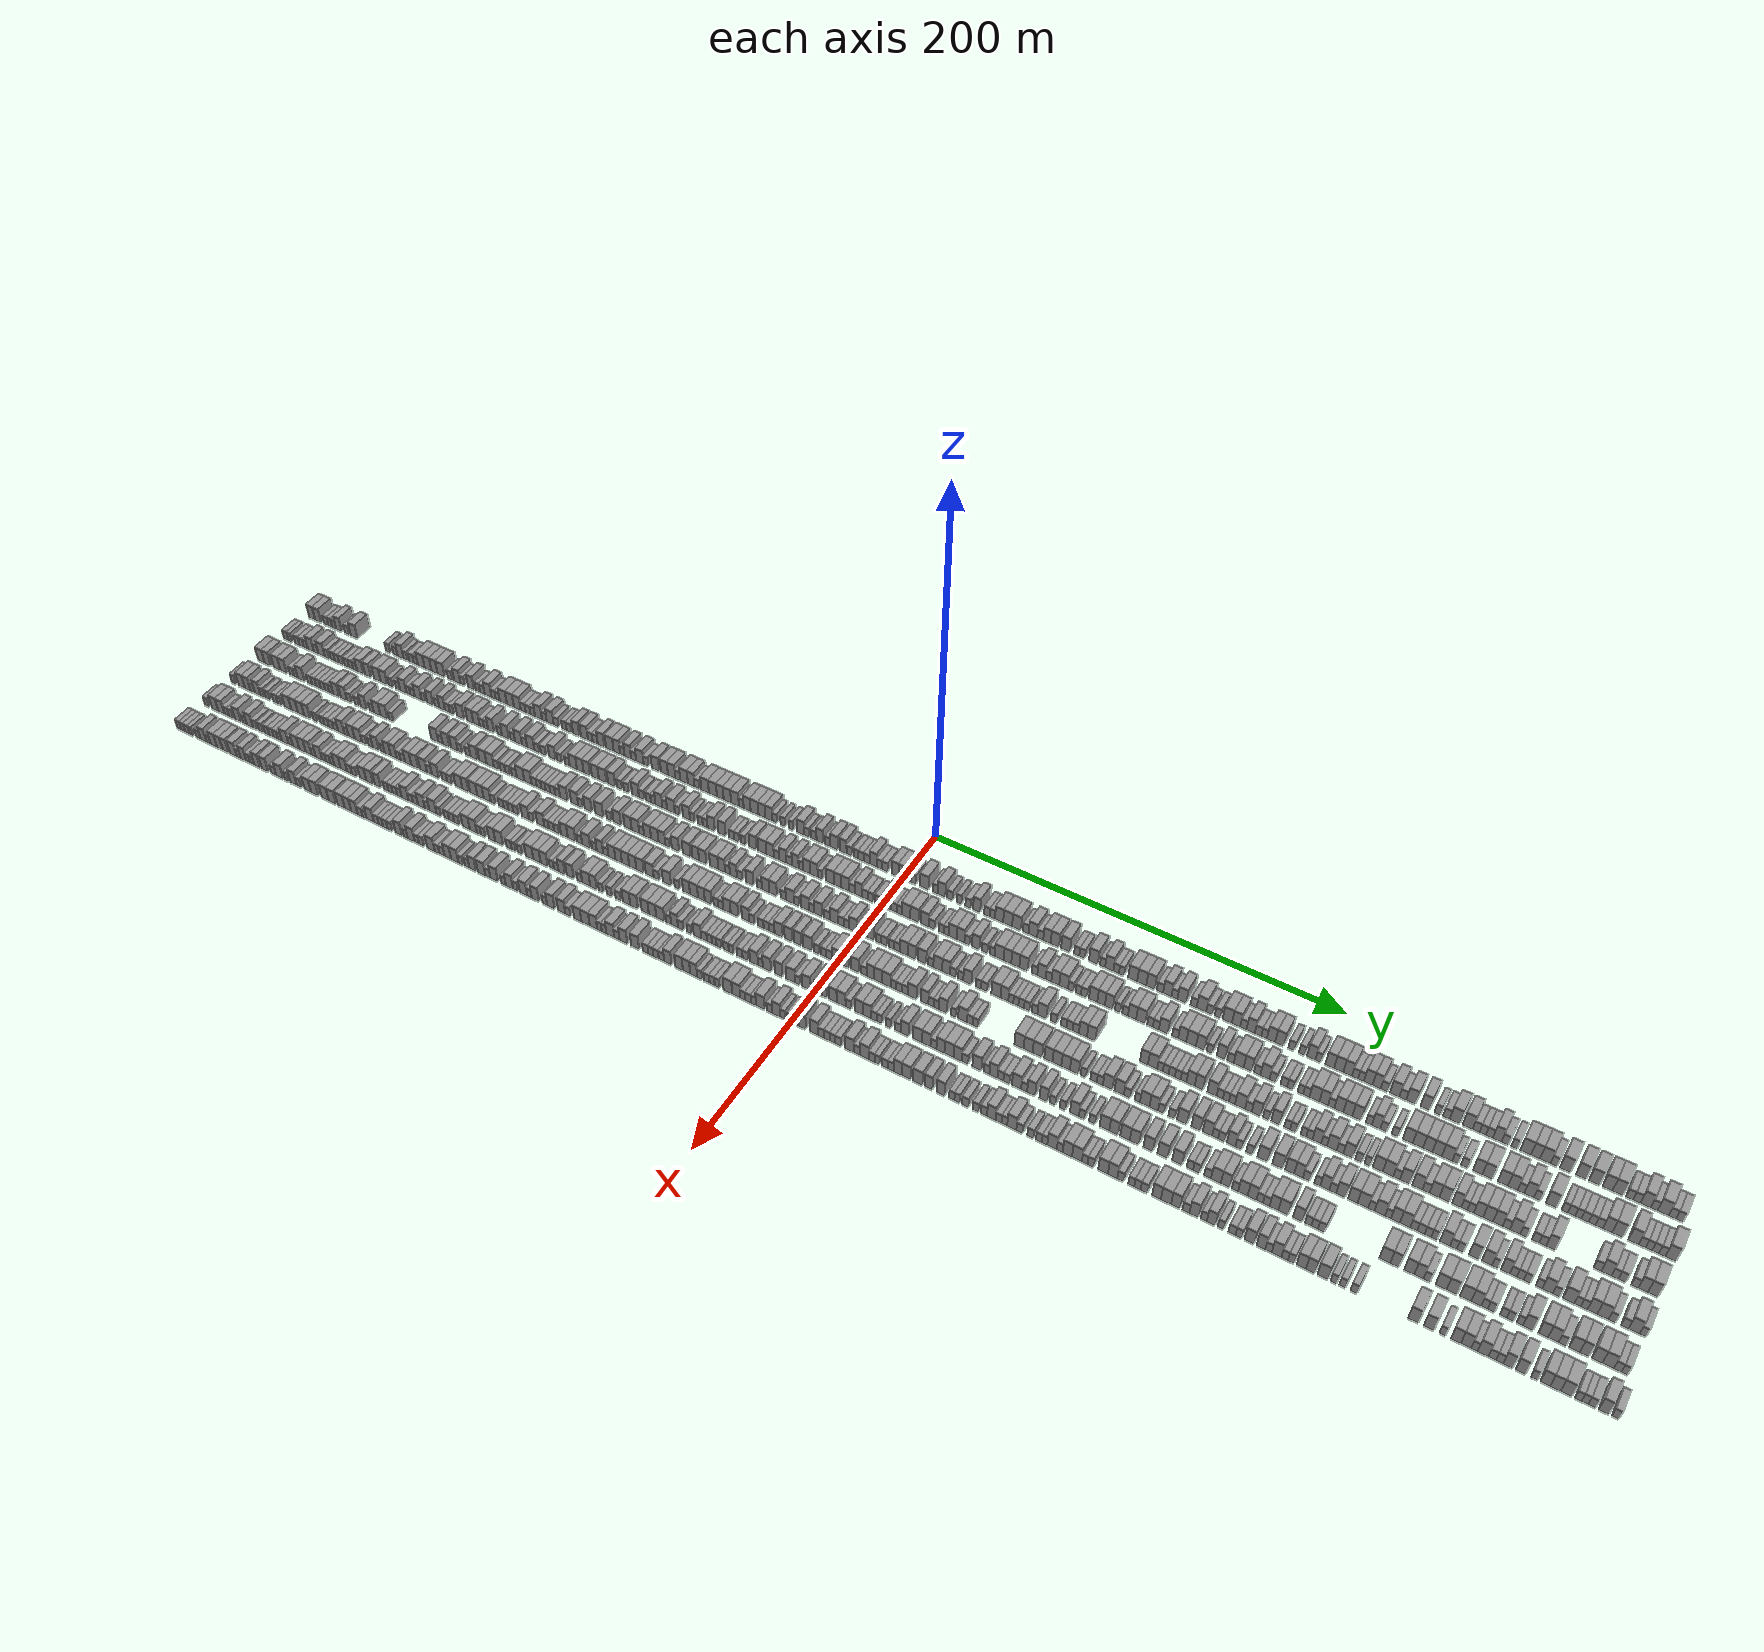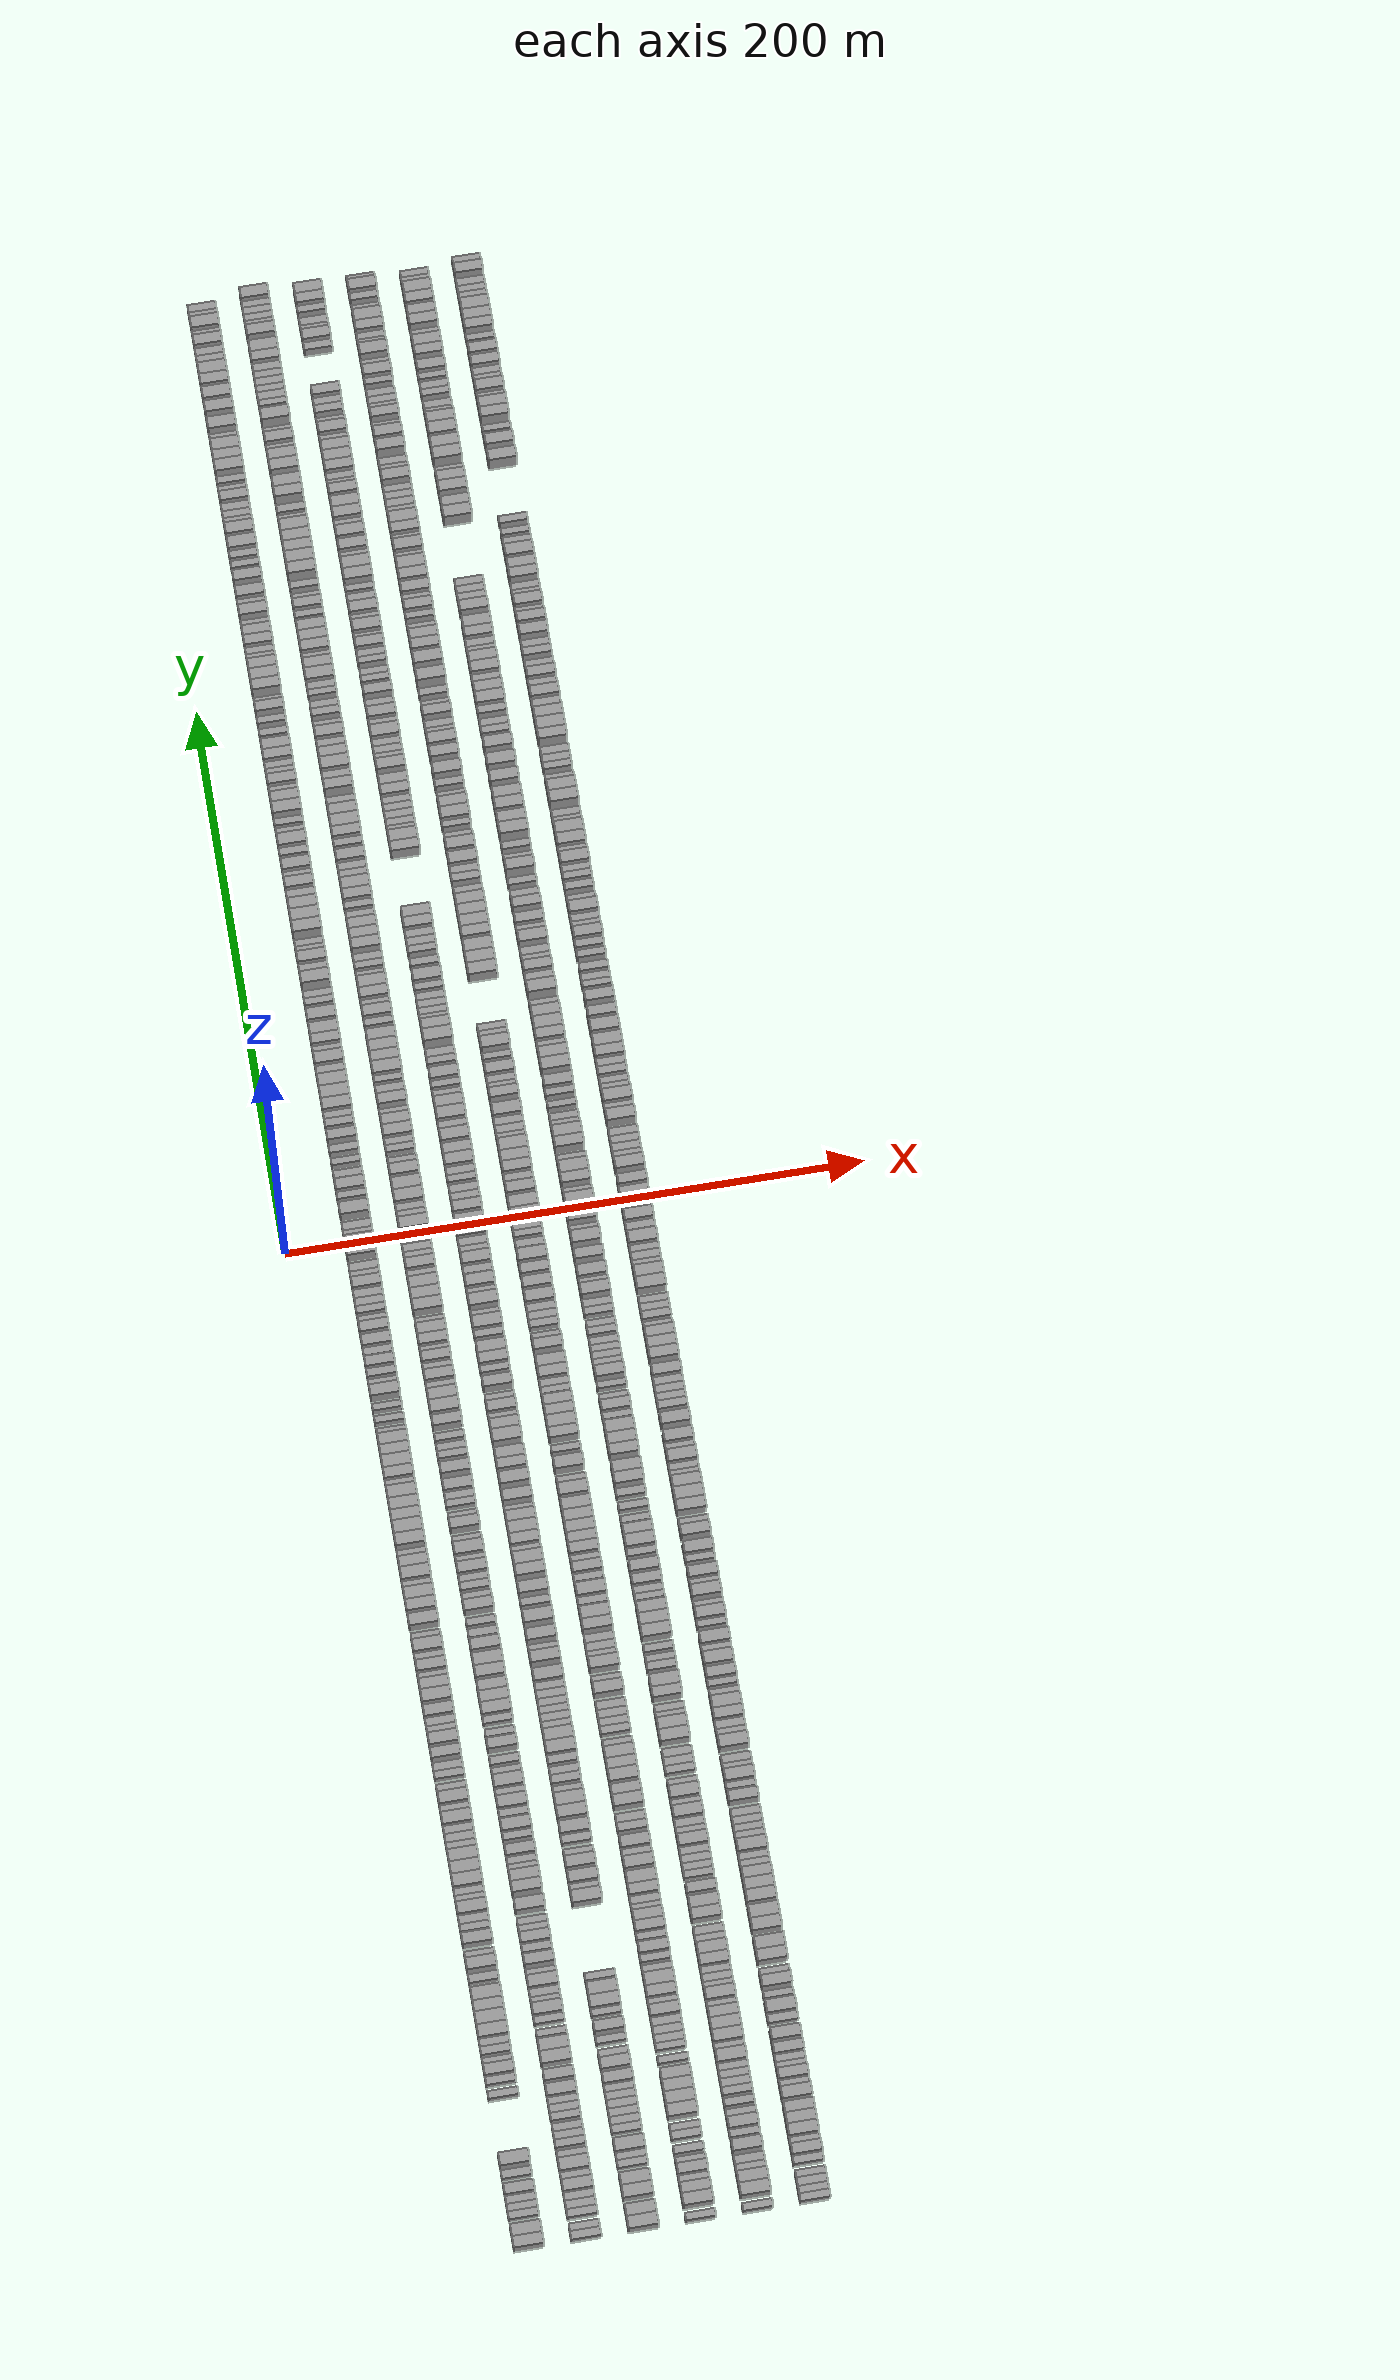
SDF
<sdf version="1.6">
 <world name="default">
  <scene>
   <sky><clouds><speed>12</speed></clouds></sky>
   <ambient>0.4 0.4 0.4 1</ambient>
   <background>0.7 0.7 0.7 1</background>
   <shadows>1</shadows>
  </scene>
  <gravity>0 0 -9.8066</gravity>
  <magnetic_field>6e-06 2.3e-05 -4.2e-05</magnetic_field>
  <physics default="0" name="default_physics" type="ode">
   <ode>
    <solver>
     <type>quick</type>
     <iters>10</iters>
     <sor>1.0</sor>
     <use_dynamic_moi_rescaling>0</use_dynamic_moi_rescaling>
    </solver>
    <constraints>
     <cfm>0</cfm>
     <erp>0.2</erp>
     <contact_max_correcting_vel>100</contact_max_correcting_vel>
     <contact_surface_layer>0.001</contact_surface_layer>
    </constraints>
   </ode>
   <max_step_size>0.004</max_step_size>
   <real_time_factor>1</real_time_factor>
   <real_time_update_rate>250</real_time_update_rate>
  </physics>
  <light name="sun" type="directional">
   <pose>0 0 10 0 0 0</pose>
   <diffuse>0.8 0.8 0.8 1</diffuse>
   <specular>0.2 0.2 0.2 1</specular>
   <attenuation>
    <range>1000</range>
    <constant>0.9</constant>
    <linear>0.01</linear>
    <quadratic>0.001</quadratic>
   </attenuation>
   <direction>-0.5 0.1 -0.9</direction>
  </light>
  <model name="building_1">
   <static>1</static>
   <pose>25.0000 -348.0444 0 0.000000 0.000000 0.000000</pose>
   <link name="link">
    <pose>0 0 4.50 0 0 0</pose>
    <collision name="collision"><geometry><box><size>10.0000 3.9112 9.0000</size></box></geometry></collision>
    <visual name="visual">
     <cast_shadows>0</cast_shadows>
     <geometry><box><size>10.0000 3.9112 9.0000</size></box></geometry>
     <material>
      <script>
       <uri>model://grey_wall/materials/scripts</uri>
       <uri>model://grey_wall/materials/textures</uri>
       <name>vrc/grey_wall</name>
      </script>
     </material>
    </visual>
   </link>
  </model>
  <model name="building_2">
   <static>1</static>
   <pose>25.0000 -344.0613 0 0.000000 0.000000 0.000000</pose>
   <link name="link">
    <pose>0 0 4.50 0 0 0</pose>
    <collision name="collision"><geometry><box><size>10.0000 4.0550 9.0000</size></box></geometry></collision>
    <visual name="visual">
     <cast_shadows>0</cast_shadows>
     <geometry><box><size>10.0000 4.0550 9.0000</size></box></geometry>
     <material>
      <script>
       <uri>model://grey_wall/materials/scripts</uri>
       <uri>model://grey_wall/materials/textures</uri>
       <name>vrc/grey_wall</name>
      </script>
     </material>
    </visual>
   </link>
  </model>
  <model name="building_3">
   <static>1</static>
   <pose>25.0000 -338.6750 0 0.000000 0.000000 0.000000</pose>
   <link name="link">
    <pose>0 0 3.00 0 0 0</pose>
    <collision name="collision"><geometry><box><size>10.0000 2.7177 6.0000</size></box></geometry></collision>
    <visual name="visual">
     <cast_shadows>0</cast_shadows>
     <geometry><box><size>10.0000 2.7177 6.0000</size></box></geometry>
     <material>
      <script>
       <uri>model://grey_wall/materials/scripts</uri>
       <uri>model://grey_wall/materials/textures</uri>
       <name>vrc/grey_wall</name>
      </script>
     </material>
    </visual>
   </link>
  </model>
  <model name="building_4">
   <static>1</static>
   <pose>25.0000 -336.0749 0 0.000000 0.000000 0.000000</pose>
   <link name="link">
    <pose>0 0 3.00 0 0 0</pose>
    <collision name="collision"><geometry><box><size>10.0000 2.4827 6.0000</size></box></geometry></collision>
    <visual name="visual">
     <cast_shadows>0</cast_shadows>
     <geometry><box><size>10.0000 2.4827 6.0000</size></box></geometry>
     <material>
      <script>
       <uri>model://grey_wall/materials/scripts</uri>
       <uri>model://grey_wall/materials/textures</uri>
       <name>vrc/grey_wall</name>
      </script>
     </material>
    </visual>
   </link>
  </model>
  <model name="building_5">
   <static>1</static>
   <pose>25.0000 -333.5000 0 0.000000 0.000000 0.000000</pose>
   <link name="link">
    <pose>0 0 3.00 0 0 0</pose>
    <collision name="collision"><geometry><box><size>10.0000 2.6671 6.0000</size></box></geometry></collision>
    <visual name="visual">
     <cast_shadows>0</cast_shadows>
     <geometry><box><size>10.0000 2.6671 6.0000</size></box></geometry>
     <material>
      <script>
       <uri>model://grey_wall/materials/scripts</uri>
       <uri>model://grey_wall/materials/textures</uri>
       <name>vrc/grey_wall</name>
      </script>
     </material>
    </visual>
   </link>
  </model>
  <model name="building_6">
   <static>1</static>
   <pose>25.0000 -330.3314 0 0.000000 0.000000 0.000000</pose>
   <link name="link">
    <pose>0 0 4.50 0 0 0</pose>
    <collision name="collision"><geometry><box><size>10.0000 3.6700 9.0000</size></box></geometry></collision>
    <visual name="visual">
     <cast_shadows>0</cast_shadows>
     <geometry><box><size>10.0000 3.6700 9.0000</size></box></geometry>
     <material>
      <script>
       <uri>model://grey_wall/materials/scripts</uri>
       <uri>model://grey_wall/materials/textures</uri>
       <name>vrc/grey_wall</name>
      </script>
     </material>
    </visual>
   </link>
  </model>
  <model name="building_7">
   <static>1</static>
   <pose>25.0000 -325.0268 0 0.000000 0.000000 0.000000</pose>
   <link name="link">
    <pose>0 0 3.00 0 0 0</pose>
    <collision name="collision"><geometry><box><size>10.0000 2.9393 6.0000</size></box></geometry></collision>
    <visual name="visual">
     <cast_shadows>0</cast_shadows>
     <geometry><box><size>10.0000 2.9393 6.0000</size></box></geometry>
     <material>
      <script>
       <uri>model://grey_wall/materials/scripts</uri>
       <uri>model://grey_wall/materials/textures</uri>
       <name>vrc/grey_wall</name>
      </script>
     </material>
    </visual>
   </link>
  </model>
  <model name="building_8">
   <static>1</static>
   <pose>25.0000 -320.3669 0 0.000000 0.000000 0.000000</pose>
   <link name="link">
    <pose>0 0 4.50 0 0 0</pose>
    <collision name="collision"><geometry><box><size>10.0000 4.3804 9.0000</size></box></geometry></collision>
    <visual name="visual">
     <cast_shadows>0</cast_shadows>
     <geometry><box><size>10.0000 4.3804 9.0000</size></box></geometry>
     <material>
      <script>
       <uri>model://grey_wall/materials/scripts</uri>
       <uri>model://grey_wall/materials/textures</uri>
       <name>vrc/grey_wall</name>
      </script>
     </material>
    </visual>
   </link>
  </model>
  <model name="building_9">
   <static>1</static>
   <pose>25.0000 -298.2334 0 0.000000 0.000000 0.000000</pose>
   <link name="link">
    <pose>0 0 3.00 0 0 0</pose>
    <collision name="collision"><geometry><box><size>10.0000 2.6289 6.0000</size></box></geometry></collision>
    <visual name="visual">
     <cast_shadows>0</cast_shadows>
     <geometry><box><size>10.0000 2.6289 6.0000</size></box></geometry>
     <material>
      <script>
       <uri>model://grey_wall/materials/scripts</uri>
       <uri>model://grey_wall/materials/textures</uri>
       <name>vrc/grey_wall</name>
      </script>
     </material>
    </visual>
   </link>
  </model>
  <model name="building_10">
   <static>1</static>
   <pose>25.0000 -293.5261 0 0.000000 0.000000 0.000000</pose>
   <link name="link">
    <pose>0 0 3.00 0 0 0</pose>
    <collision name="collision"><geometry><box><size>10.0000 2.7855 6.0000</size></box></geometry></collision>
    <visual name="visual">
     <cast_shadows>0</cast_shadows>
     <geometry><box><size>10.0000 2.7855 6.0000</size></box></geometry>
     <material>
      <script>
       <uri>model://grey_wall/materials/scripts</uri>
       <uri>model://grey_wall/materials/textures</uri>
       <name>vrc/grey_wall</name>
      </script>
     </material>
    </visual>
   </link>
  </model>
  <model name="building_11">
   <static>1</static>
   <pose>25.0000 -290.2199 0 0.000000 0.000000 0.000000</pose>
   <link name="link">
    <pose>0 0 4.50 0 0 0</pose>
    <collision name="collision"><geometry><box><size>10.0000 3.8269 9.0000</size></box></geometry></collision>
    <visual name="visual">
     <cast_shadows>0</cast_shadows>
     <geometry><box><size>10.0000 3.8269 9.0000</size></box></geometry>
     <material>
      <script>
       <uri>model://grey_wall/materials/scripts</uri>
       <uri>model://grey_wall/materials/textures</uri>
       <name>vrc/grey_wall</name>
      </script>
     </material>
    </visual>
   </link>
  </model>
  <model name="building_12">
   <static>1</static>
   <pose>25.0000 -287.0254 0 0.000000 0.000000 0.000000</pose>
   <link name="link">
    <pose>0 0 3.00 0 0 0</pose>
    <collision name="collision"><geometry><box><size>10.0000 2.5621 6.0000</size></box></geometry></collision>
    <visual name="visual">
     <cast_shadows>0</cast_shadows>
     <geometry><box><size>10.0000 2.5621 6.0000</size></box></geometry>
     <material>
      <script>
       <uri>model://grey_wall/materials/scripts</uri>
       <uri>model://grey_wall/materials/textures</uri>
       <name>vrc/grey_wall</name>
      </script>
     </material>
    </visual>
   </link>
  </model>
  <model name="building_13">
   <static>1</static>
   <pose>25.0000 -283.3257 0 0.000000 0.000000 0.000000</pose>
   <link name="link">
    <pose>0 0 3.00 0 0 0</pose>
    <collision name="collision"><geometry><box><size>10.0000 2.8373 6.0000</size></box></geometry></collision>
    <visual name="visual">
     <cast_shadows>0</cast_shadows>
     <geometry><box><size>10.0000 2.8373 6.0000</size></box></geometry>
     <material>
      <script>
       <uri>model://grey_wall/materials/scripts</uri>
       <uri>model://grey_wall/materials/textures</uri>
       <name>vrc/grey_wall</name>
      </script>
     </material>
    </visual>
   </link>
  </model>
  <model name="building_14">
   <static>1</static>
   <pose>25.0000 -280.5883 0 0.000000 0.000000 0.000000</pose>
   <link name="link">
    <pose>0 0 3.00 0 0 0</pose>
    <collision name="collision"><geometry><box><size>10.0000 2.6376 6.0000</size></box></geometry></collision>
    <visual name="visual">
     <cast_shadows>0</cast_shadows>
     <geometry><box><size>10.0000 2.6376 6.0000</size></box></geometry>
     <material>
      <script>
       <uri>model://grey_wall/materials/scripts</uri>
       <uri>model://grey_wall/materials/textures</uri>
       <name>vrc/grey_wall</name>
      </script>
     </material>
    </visual>
   </link>
  </model>
  <model name="building_15">
   <static>1</static>
   <pose>25.0000 -277.1161 0 0.000000 0.000000 0.000000</pose>
   <link name="link">
    <pose>0 0 4.50 0 0 0</pose>
    <collision name="collision"><geometry><box><size>10.0000 4.3069 9.0000</size></box></geometry></collision>
    <visual name="visual">
     <cast_shadows>0</cast_shadows>
     <geometry><box><size>10.0000 4.3069 9.0000</size></box></geometry>
     <material>
      <script>
       <uri>model://grey_wall/materials/scripts</uri>
       <uri>model://grey_wall/materials/textures</uri>
       <name>vrc/grey_wall</name>
      </script>
     </material>
    </visual>
   </link>
  </model>
  <model name="building_16">
   <static>1</static>
   <pose>25.0000 -272.7496 0 0.000000 0.000000 0.000000</pose>
   <link name="link">
    <pose>0 0 4.50 0 0 0</pose>
    <collision name="collision"><geometry><box><size>10.0000 4.4260 9.0000</size></box></geometry></collision>
    <visual name="visual">
     <cast_shadows>0</cast_shadows>
     <geometry><box><size>10.0000 4.4260 9.0000</size></box></geometry>
     <material>
      <script>
       <uri>model://grey_wall/materials/scripts</uri>
       <uri>model://grey_wall/materials/textures</uri>
       <name>vrc/grey_wall</name>
      </script>
     </material>
    </visual>
   </link>
  </model>
  <model name="building_17">
   <static>1</static>
   <pose>25.0000 -268.6727 0 0.000000 0.000000 0.000000</pose>
   <link name="link">
    <pose>0 0 4.50 0 0 0</pose>
    <collision name="collision"><geometry><box><size>10.0000 3.7279 9.0000</size></box></geometry></collision>
    <visual name="visual">
     <cast_shadows>0</cast_shadows>
     <geometry><box><size>10.0000 3.7279 9.0000</size></box></geometry>
     <material>
      <script>
       <uri>model://grey_wall/materials/scripts</uri>
       <uri>model://grey_wall/materials/textures</uri>
       <name>vrc/grey_wall</name>
      </script>
     </material>
    </visual>
   </link>
  </model>
  <model name="building_18">
   <static>1</static>
   <pose>25.0000 -264.5708 0 0.000000 0.000000 0.000000</pose>
   <link name="link">
    <pose>0 0 4.50 0 0 0</pose>
    <collision name="collision"><geometry><box><size>10.0000 4.4757 9.0000</size></box></geometry></collision>
    <visual name="visual">
     <cast_shadows>0</cast_shadows>
     <geometry><box><size>10.0000 4.4757 9.0000</size></box></geometry>
     <material>
      <script>
       <uri>model://grey_wall/materials/scripts</uri>
       <uri>model://grey_wall/materials/textures</uri>
       <name>vrc/grey_wall</name>
      </script>
     </material>
    </visual>
   </link>
  </model>
  <model name="building_19">
   <static>1</static>
   <pose>25.0000 -258.8475 0 0.000000 0.000000 0.000000</pose>
   <link name="link">
    <pose>0 0 3.00 0 0 0</pose>
    <collision name="collision"><geometry><box><size>10.0000 2.9709 6.0000</size></box></geometry></collision>
    <visual name="visual">
     <cast_shadows>0</cast_shadows>
     <geometry><box><size>10.0000 2.9709 6.0000</size></box></geometry>
     <material>
      <script>
       <uri>model://grey_wall/materials/scripts</uri>
       <uri>model://grey_wall/materials/textures</uri>
       <name>vrc/grey_wall</name>
      </script>
     </material>
    </visual>
   </link>
  </model>
  <model name="building_20">
   <static>1</static>
   <pose>25.0000 -254.3251 0 0.000000 0.000000 0.000000</pose>
   <link name="link">
    <pose>0 0 4.50 0 0 0</pose>
    <collision name="collision"><geometry><box><size>10.0000 4.0739 9.0000</size></box></geometry></collision>
    <visual name="visual">
     <cast_shadows>0</cast_shadows>
     <geometry><box><size>10.0000 4.0739 9.0000</size></box></geometry>
     <material>
      <script>
       <uri>model://grey_wall/materials/scripts</uri>
       <uri>model://grey_wall/materials/textures</uri>
       <name>vrc/grey_wall</name>
      </script>
     </material>
    </visual>
   </link>
  </model>
  <model name="building_21">
   <static>1</static>
   <pose>25.0000 -251.0014 0 0.000000 0.000000 0.000000</pose>
   <link name="link">
    <pose>0 0 3.00 0 0 0</pose>
    <collision name="collision"><geometry><box><size>10.0000 2.5734 6.0000</size></box></geometry></collision>
    <visual name="visual">
     <cast_shadows>0</cast_shadows>
     <geometry><box><size>10.0000 2.5734 6.0000</size></box></geometry>
     <material>
      <script>
       <uri>model://grey_wall/materials/scripts</uri>
       <uri>model://grey_wall/materials/textures</uri>
       <name>vrc/grey_wall</name>
      </script>
     </material>
    </visual>
   </link>
  </model>
  <model name="building_22">
   <static>1</static>
   <pose>25.0000 -245.7738 0 0.000000 0.000000 0.000000</pose>
   <link name="link">
    <pose>0 0 4.50 0 0 0</pose>
    <collision name="collision"><geometry><box><size>10.0000 3.8818 9.0000</size></box></geometry></collision>
    <visual name="visual">
     <cast_shadows>0</cast_shadows>
     <geometry><box><size>10.0000 3.8818 9.0000</size></box></geometry>
     <material>
      <script>
       <uri>model://grey_wall/materials/scripts</uri>
       <uri>model://grey_wall/materials/textures</uri>
       <name>vrc/grey_wall</name>
      </script>
     </material>
    </visual>
   </link>
  </model>
  <model name="building_23">
   <static>1</static>
   <pose>25.0000 -241.5540 0 0.000000 0.000000 0.000000</pose>
   <link name="link">
    <pose>0 0 3.00 0 0 0</pose>
    <collision name="collision"><geometry><box><size>10.0000 2.5579 6.0000</size></box></geometry></collision>
    <visual name="visual">
     <cast_shadows>0</cast_shadows>
     <geometry><box><size>10.0000 2.5579 6.0000</size></box></geometry>
     <material>
      <script>
       <uri>model://grey_wall/materials/scripts</uri>
       <uri>model://grey_wall/materials/textures</uri>
       <name>vrc/grey_wall</name>
      </script>
     </material>
    </visual>
   </link>
  </model>
  <model name="building_24">
   <static>1</static>
   <pose>25.0000 -238.8029 0 0.000000 0.000000 0.000000</pose>
   <link name="link">
    <pose>0 0 3.00 0 0 0</pose>
    <collision name="collision"><geometry><box><size>10.0000 2.9443 6.0000</size></box></geometry></collision>
    <visual name="visual">
     <cast_shadows>0</cast_shadows>
     <geometry><box><size>10.0000 2.9443 6.0000</size></box></geometry>
     <material>
      <script>
       <uri>model://grey_wall/materials/scripts</uri>
       <uri>model://grey_wall/materials/textures</uri>
       <name>vrc/grey_wall</name>
      </script>
     </material>
    </visual>
   </link>
  </model>
  <model name="building_25">
   <static>1</static>
   <pose>25.0000 -235.2367 0 0.000000 0.000000 0.000000</pose>
   <link name="link">
    <pose>0 0 4.50 0 0 0</pose>
    <collision name="collision"><geometry><box><size>10.0000 4.1882 9.0000</size></box></geometry></collision>
    <visual name="visual">
     <cast_shadows>0</cast_shadows>
     <geometry><box><size>10.0000 4.1882 9.0000</size></box></geometry>
     <material>
      <script>
       <uri>model://grey_wall/materials/scripts</uri>
       <uri>model://grey_wall/materials/textures</uri>
       <name>vrc/grey_wall</name>
      </script>
     </material>
    </visual>
   </link>
  </model>
  <model name="building_26">
   <static>1</static>
   <pose>25.0000 -231.8609 0 0.000000 0.000000 0.000000</pose>
   <link name="link">
    <pose>0 0 3.00 0 0 0</pose>
    <collision name="collision"><geometry><box><size>10.0000 2.5635 6.0000</size></box></geometry></collision>
    <visual name="visual">
     <cast_shadows>0</cast_shadows>
     <geometry><box><size>10.0000 2.5635 6.0000</size></box></geometry>
     <material>
      <script>
       <uri>model://grey_wall/materials/scripts</uri>
       <uri>model://grey_wall/materials/textures</uri>
       <name>vrc/grey_wall</name>
      </script>
     </material>
    </visual>
   </link>
  </model>
  <model name="building_27">
   <static>1</static>
   <pose>25.0000 -229.3347 0 0.000000 0.000000 0.000000</pose>
   <link name="link">
    <pose>0 0 3.00 0 0 0</pose>
    <collision name="collision"><geometry><box><size>10.0000 2.4889 6.0000</size></box></geometry></collision>
    <visual name="visual">
     <cast_shadows>0</cast_shadows>
     <geometry><box><size>10.0000 2.4889 6.0000</size></box></geometry>
     <material>
      <script>
       <uri>model://grey_wall/materials/scripts</uri>
       <uri>model://grey_wall/materials/textures</uri>
       <name>vrc/grey_wall</name>
      </script>
     </material>
    </visual>
   </link>
  </model>
  <model name="building_28">
   <static>1</static>
   <pose>25.0000 -225.8748 0 0.000000 0.000000 0.000000</pose>
   <link name="link">
    <pose>0 0 4.50 0 0 0</pose>
    <collision name="collision"><geometry><box><size>10.0000 4.4308 9.0000</size></box></geometry></collision>
    <visual name="visual">
     <cast_shadows>0</cast_shadows>
     <geometry><box><size>10.0000 4.4308 9.0000</size></box></geometry>
     <material>
      <script>
       <uri>model://grey_wall/materials/scripts</uri>
       <uri>model://grey_wall/materials/textures</uri>
       <name>vrc/grey_wall</name>
      </script>
     </material>
    </visual>
   </link>
  </model>
  <model name="building_29">
   <static>1</static>
   <pose>25.0000 -221.5319 0 0.000000 0.000000 0.000000</pose>
   <link name="link">
    <pose>0 0 4.50 0 0 0</pose>
    <collision name="collision"><geometry><box><size>10.0000 4.2551 9.0000</size></box></geometry></collision>
    <visual name="visual">
     <cast_shadows>0</cast_shadows>
     <geometry><box><size>10.0000 4.2551 9.0000</size></box></geometry>
     <material>
      <script>
       <uri>model://grey_wall/materials/scripts</uri>
       <uri>model://grey_wall/materials/textures</uri>
       <name>vrc/grey_wall</name>
      </script>
     </material>
    </visual>
   </link>
  </model>
  <model name="building_30">
   <static>1</static>
   <pose>25.0000 -217.3223 0 0.000000 0.000000 0.000000</pose>
   <link name="link">
    <pose>0 0 4.50 0 0 0</pose>
    <collision name="collision"><geometry><box><size>10.0000 4.1640 9.0000</size></box></geometry></collision>
    <visual name="visual">
     <cast_shadows>0</cast_shadows>
     <geometry><box><size>10.0000 4.1640 9.0000</size></box></geometry>
     <material>
      <script>
       <uri>model://grey_wall/materials/scripts</uri>
       <uri>model://grey_wall/materials/textures</uri>
       <name>vrc/grey_wall</name>
      </script>
     </material>
    </visual>
   </link>
  </model>
  <model name="building_31">
   <static>1</static>
   <pose>25.0000 -213.7689 0 0.000000 0.000000 0.000000</pose>
   <link name="link">
    <pose>0 0 3.00 0 0 0</pose>
    <collision name="collision"><geometry><box><size>10.0000 2.9429 6.0000</size></box></geometry></collision>
    <visual name="visual">
     <cast_shadows>0</cast_shadows>
     <geometry><box><size>10.0000 2.9429 6.0000</size></box></geometry>
     <material>
      <script>
       <uri>model://grey_wall/materials/scripts</uri>
       <uri>model://grey_wall/materials/textures</uri>
       <name>vrc/grey_wall</name>
      </script>
     </material>
    </visual>
   </link>
  </model>
  <model name="building_32">
   <static>1</static>
   <pose>25.0000 -210.8348 0 0.000000 0.000000 0.000000</pose>
   <link name="link">
    <pose>0 0 3.00 0 0 0</pose>
    <collision name="collision"><geometry><box><size>10.0000 2.9253 6.0000</size></box></geometry></collision>
    <visual name="visual">
     <cast_shadows>0</cast_shadows>
     <geometry><box><size>10.0000 2.9253 6.0000</size></box></geometry>
     <material>
      <script>
       <uri>model://grey_wall/materials/scripts</uri>
       <uri>model://grey_wall/materials/textures</uri>
       <name>vrc/grey_wall</name>
      </script>
     </material>
    </visual>
   </link>
  </model>
  <model name="building_33">
   <static>1</static>
   <pose>25.0000 -207.9864 0 0.000000 0.000000 0.000000</pose>
   <link name="link">
    <pose>0 0 3.00 0 0 0</pose>
    <collision name="collision"><geometry><box><size>10.0000 2.7715 6.0000</size></box></geometry></collision>
    <visual name="visual">
     <cast_shadows>0</cast_shadows>
     <geometry><box><size>10.0000 2.7715 6.0000</size></box></geometry>
     <material>
      <script>
       <uri>model://grey_wall/materials/scripts</uri>
       <uri>model://grey_wall/materials/textures</uri>
       <name>vrc/grey_wall</name>
      </script>
     </material>
    </visual>
   </link>
  </model>
  <model name="building_34">
   <static>1</static>
   <pose>25.0000 -204.4885 0 0.000000 0.000000 0.000000</pose>
   <link name="link">
    <pose>0 0 4.50 0 0 0</pose>
    <collision name="collision"><geometry><box><size>10.0000 4.2243 9.0000</size></box></geometry></collision>
    <visual name="visual">
     <cast_shadows>0</cast_shadows>
     <geometry><box><size>10.0000 4.2243 9.0000</size></box></geometry>
     <material>
      <script>
       <uri>model://grey_wall/materials/scripts</uri>
       <uri>model://grey_wall/materials/textures</uri>
       <name>vrc/grey_wall</name>
      </script>
     </material>
    </visual>
   </link>
  </model>
  <model name="building_35">
   <static>1</static>
   <pose>25.0000 -200.9533 0 0.000000 0.000000 0.000000</pose>
   <link name="link">
    <pose>0 0 3.00 0 0 0</pose>
    <collision name="collision"><geometry><box><size>10.0000 2.8462 6.0000</size></box></geometry></collision>
    <visual name="visual">
     <cast_shadows>0</cast_shadows>
     <geometry><box><size>10.0000 2.8462 6.0000</size></box></geometry>
     <material>
      <script>
       <uri>model://grey_wall/materials/scripts</uri>
       <uri>model://grey_wall/materials/textures</uri>
       <name>vrc/grey_wall</name>
      </script>
     </material>
    </visual>
   </link>
  </model>
  <model name="building_36">
   <static>1</static>
   <pose>25.0000 -197.4274 0 0.000000 0.000000 0.000000</pose>
   <link name="link">
    <pose>0 0 4.50 0 0 0</pose>
    <collision name="collision"><geometry><box><size>10.0000 4.2056 9.0000</size></box></geometry></collision>
    <visual name="visual">
     <cast_shadows>0</cast_shadows>
     <geometry><box><size>10.0000 4.2056 9.0000</size></box></geometry>
     <material>
      <script>
       <uri>model://grey_wall/materials/scripts</uri>
       <uri>model://grey_wall/materials/textures</uri>
       <name>vrc/grey_wall</name>
      </script>
     </material>
    </visual>
   </link>
  </model>
  <model name="building_37">
   <static>1</static>
   <pose>25.0000 -193.8503 0 0.000000 0.000000 0.000000</pose>
   <link name="link">
    <pose>0 0 3.00 0 0 0</pose>
    <collision name="collision"><geometry><box><size>10.0000 2.9484 6.0000</size></box></geometry></collision>
    <visual name="visual">
     <cast_shadows>0</cast_shadows>
     <geometry><box><size>10.0000 2.9484 6.0000</size></box></geometry>
     <material>
      <script>
       <uri>model://grey_wall/materials/scripts</uri>
       <uri>model://grey_wall/materials/textures</uri>
       <name>vrc/grey_wall</name>
      </script>
     </material>
    </visual>
   </link>
  </model>
  <model name="building_38">
   <static>1</static>
   <pose>25.0000 -189.0111 0 0.000000 0.000000 0.000000</pose>
   <link name="link">
    <pose>0 0 3.00 0 0 0</pose>
    <collision name="collision"><geometry><box><size>10.0000 2.7301 6.0000</size></box></geometry></collision>
    <visual name="visual">
     <cast_shadows>0</cast_shadows>
     <geometry><box><size>10.0000 2.7301 6.0000</size></box></geometry>
     <material>
      <script>
       <uri>model://grey_wall/materials/scripts</uri>
       <uri>model://grey_wall/materials/textures</uri>
       <name>vrc/grey_wall</name>
      </script>
     </material>
    </visual>
   </link>
  </model>
  <model name="building_39">
   <static>1</static>
   <pose>25.0000 -186.2230 0 0.000000 0.000000 0.000000</pose>
   <link name="link">
    <pose>0 0 3.00 0 0 0</pose>
    <collision name="collision"><geometry><box><size>10.0000 2.8460 6.0000</size></box></geometry></collision>
    <visual name="visual">
     <cast_shadows>0</cast_shadows>
     <geometry><box><size>10.0000 2.8460 6.0000</size></box></geometry>
     <material>
      <script>
       <uri>model://grey_wall/materials/scripts</uri>
       <uri>model://grey_wall/materials/textures</uri>
       <name>vrc/grey_wall</name>
      </script>
     </material>
    </visual>
   </link>
  </model>
  <model name="building_40">
   <static>1</static>
   <pose>25.0000 -181.9369 0 0.000000 0.000000 0.000000</pose>
   <link name="link">
    <pose>0 0 4.50 0 0 0</pose>
    <collision name="collision"><geometry><box><size>10.0000 3.7263 9.0000</size></box></geometry></collision>
    <visual name="visual">
     <cast_shadows>0</cast_shadows>
     <geometry><box><size>10.0000 3.7263 9.0000</size></box></geometry>
     <material>
      <script>
       <uri>model://grey_wall/materials/scripts</uri>
       <uri>model://grey_wall/materials/textures</uri>
       <name>vrc/grey_wall</name>
      </script>
     </material>
    </visual>
   </link>
  </model>
  <model name="building_41">
   <static>1</static>
   <pose>25.0000 -177.0103 0 0.000000 0.000000 0.000000</pose>
   <link name="link">
    <pose>0 0 4.50 0 0 0</pose>
    <collision name="collision"><geometry><box><size>10.0000 4.1269 9.0000</size></box></geometry></collision>
    <visual name="visual">
     <cast_shadows>0</cast_shadows>
     <geometry><box><size>10.0000 4.1269 9.0000</size></box></geometry>
     <material>
      <script>
       <uri>model://grey_wall/materials/scripts</uri>
       <uri>model://grey_wall/materials/textures</uri>
       <name>vrc/grey_wall</name>
      </script>
     </material>
    </visual>
   </link>
  </model>
  <model name="building_42">
   <static>1</static>
   <pose>25.0000 -173.5487 0 0.000000 0.000000 0.000000</pose>
   <link name="link">
    <pose>0 0 3.00 0 0 0</pose>
    <collision name="collision"><geometry><box><size>10.0000 2.7963 6.0000</size></box></geometry></collision>
    <visual name="visual">
     <cast_shadows>0</cast_shadows>
     <geometry><box><size>10.0000 2.7963 6.0000</size></box></geometry>
     <material>
      <script>
       <uri>model://grey_wall/materials/scripts</uri>
       <uri>model://grey_wall/materials/textures</uri>
       <name>vrc/grey_wall</name>
      </script>
     </material>
    </visual>
   </link>
  </model>
  <model name="building_43">
   <static>1</static>
   <pose>25.0000 -170.6842 0 0.000000 0.000000 0.000000</pose>
   <link name="link">
    <pose>0 0 3.00 0 0 0</pose>
    <collision name="collision"><geometry><box><size>10.0000 2.9326 6.0000</size></box></geometry></collision>
    <visual name="visual">
     <cast_shadows>0</cast_shadows>
     <geometry><box><size>10.0000 2.9326 6.0000</size></box></geometry>
     <material>
      <script>
       <uri>model://grey_wall/materials/scripts</uri>
       <uri>model://grey_wall/materials/textures</uri>
       <name>vrc/grey_wall</name>
      </script>
     </material>
    </visual>
   </link>
  </model>
  <model name="building_44">
   <static>1</static>
   <pose>25.0000 -167.2546 0 0.000000 0.000000 0.000000</pose>
   <link name="link">
    <pose>0 0 4.50 0 0 0</pose>
    <collision name="collision"><geometry><box><size>10.0000 3.9267 9.0000</size></box></geometry></collision>
    <visual name="visual">
     <cast_shadows>0</cast_shadows>
     <geometry><box><size>10.0000 3.9267 9.0000</size></box></geometry>
     <material>
      <script>
       <uri>model://grey_wall/materials/scripts</uri>
       <uri>model://grey_wall/materials/textures</uri>
       <name>vrc/grey_wall</name>
      </script>
     </material>
    </visual>
   </link>
  </model>
  <model name="building_45">
   <static>1</static>
   <pose>25.0000 -162.1022 0 0.000000 0.000000 0.000000</pose>
   <link name="link">
    <pose>0 0 4.50 0 0 0</pose>
    <collision name="collision"><geometry><box><size>10.0000 4.3781 9.0000</size></box></geometry></collision>
    <visual name="visual">
     <cast_shadows>0</cast_shadows>
     <geometry><box><size>10.0000 4.3781 9.0000</size></box></geometry>
     <material>
      <script>
       <uri>model://grey_wall/materials/scripts</uri>
       <uri>model://grey_wall/materials/textures</uri>
       <name>vrc/grey_wall</name>
      </script>
     </material>
    </visual>
   </link>
  </model>
  <model name="building_46">
   <static>1</static>
   <pose>25.0000 -158.0281 0 0.000000 0.000000 0.000000</pose>
   <link name="link">
    <pose>0 0 4.50 0 0 0</pose>
    <collision name="collision"><geometry><box><size>10.0000 3.7700 9.0000</size></box></geometry></collision>
    <visual name="visual">
     <cast_shadows>0</cast_shadows>
     <geometry><box><size>10.0000 3.7700 9.0000</size></box></geometry>
     <material>
      <script>
       <uri>model://grey_wall/materials/scripts</uri>
       <uri>model://grey_wall/materials/textures</uri>
       <name>vrc/grey_wall</name>
      </script>
     </material>
    </visual>
   </link>
  </model>
  <model name="building_47">
   <static>1</static>
   <pose>25.0000 -154.8432 0 0.000000 0.000000 0.000000</pose>
   <link name="link">
    <pose>0 0 3.00 0 0 0</pose>
    <collision name="collision"><geometry><box><size>10.0000 2.5999 6.0000</size></box></geometry></collision>
    <visual name="visual">
     <cast_shadows>0</cast_shadows>
     <geometry><box><size>10.0000 2.5999 6.0000</size></box></geometry>
     <material>
      <script>
       <uri>model://grey_wall/materials/scripts</uri>
       <uri>model://grey_wall/materials/textures</uri>
       <name>vrc/grey_wall</name>
      </script>
     </material>
    </visual>
   </link>
  </model>
  <model name="building_48">
   <static>1</static>
   <pose>25.0000 -151.6266 0 0.000000 0.000000 0.000000</pose>
   <link name="link">
    <pose>0 0 4.50 0 0 0</pose>
    <collision name="collision"><geometry><box><size>10.0000 3.8334 9.0000</size></box></geometry></collision>
    <visual name="visual">
     <cast_shadows>0</cast_shadows>
     <geometry><box><size>10.0000 3.8334 9.0000</size></box></geometry>
     <material>
      <script>
       <uri>model://grey_wall/materials/scripts</uri>
       <uri>model://grey_wall/materials/textures</uri>
       <name>vrc/grey_wall</name>
      </script>
     </material>
    </visual>
   </link>
  </model>
  <model name="building_49">
   <static>1</static>
   <pose>25.0000 -148.2320 0 0.000000 0.000000 0.000000</pose>
   <link name="link">
    <pose>0 0 3.00 0 0 0</pose>
    <collision name="collision"><geometry><box><size>10.0000 2.9559 6.0000</size></box></geometry></collision>
    <visual name="visual">
     <cast_shadows>0</cast_shadows>
     <geometry><box><size>10.0000 2.9559 6.0000</size></box></geometry>
     <material>
      <script>
       <uri>model://grey_wall/materials/scripts</uri>
       <uri>model://grey_wall/materials/textures</uri>
       <name>vrc/grey_wall</name>
      </script>
     </material>
    </visual>
   </link>
  </model>
  <model name="building_50">
   <static>1</static>
   <pose>25.0000 -144.5855 0 0.000000 0.000000 0.000000</pose>
   <link name="link">
    <pose>0 0 4.50 0 0 0</pose>
    <collision name="collision"><geometry><box><size>10.0000 4.3371 9.0000</size></box></geometry></collision>
    <visual name="visual">
     <cast_shadows>0</cast_shadows>
     <geometry><box><size>10.0000 4.3371 9.0000</size></box></geometry>
     <material>
      <script>
       <uri>model://grey_wall/materials/scripts</uri>
       <uri>model://grey_wall/materials/textures</uri>
       <name>vrc/grey_wall</name>
      </script>
     </material>
    </visual>
   </link>
  </model>
  <model name="building_51">
   <static>1</static>
   <pose>25.0000 -141.0825 0 0.000000 0.000000 0.000000</pose>
   <link name="link">
    <pose>0 0 3.00 0 0 0</pose>
    <collision name="collision"><geometry><box><size>10.0000 2.6689 6.0000</size></box></geometry></collision>
    <visual name="visual">
     <cast_shadows>0</cast_shadows>
     <geometry><box><size>10.0000 2.6689 6.0000</size></box></geometry>
     <material>
      <script>
       <uri>model://grey_wall/materials/scripts</uri>
       <uri>model://grey_wall/materials/textures</uri>
       <name>vrc/grey_wall</name>
      </script>
     </material>
    </visual>
   </link>
  </model>
  <model name="building_52">
   <static>1</static>
   <pose>25.0000 -135.6141 0 0.000000 0.000000 0.000000</pose>
   <link name="link">
    <pose>0 0 4.50 0 0 0</pose>
    <collision name="collision"><geometry><box><size>10.0000 4.2678 9.0000</size></box></geometry></collision>
    <visual name="visual">
     <cast_shadows>0</cast_shadows>
     <geometry><box><size>10.0000 4.2678 9.0000</size></box></geometry>
     <material>
      <script>
       <uri>model://grey_wall/materials/scripts</uri>
       <uri>model://grey_wall/materials/textures</uri>
       <name>vrc/grey_wall</name>
      </script>
     </material>
    </visual>
   </link>
  </model>
  <model name="building_53">
   <static>1</static>
   <pose>25.0000 -130.4871 0 0.000000 0.000000 0.000000</pose>
   <link name="link">
    <pose>0 0 4.50 0 0 0</pose>
    <collision name="collision"><geometry><box><size>10.0000 3.9863 9.0000</size></box></geometry></collision>
    <visual name="visual">
     <cast_shadows>0</cast_shadows>
     <geometry><box><size>10.0000 3.9863 9.0000</size></box></geometry>
     <material>
      <script>
       <uri>model://grey_wall/materials/scripts</uri>
       <uri>model://grey_wall/materials/textures</uri>
       <name>vrc/grey_wall</name>
      </script>
     </material>
    </visual>
   </link>
  </model>
  <model name="building_54">
   <static>1</static>
   <pose>25.0000 -126.3685 0 0.000000 0.000000 0.000000</pose>
   <link name="link">
    <pose>0 0 4.50 0 0 0</pose>
    <collision name="collision"><geometry><box><size>10.0000 4.2508 9.0000</size></box></geometry></collision>
    <visual name="visual">
     <cast_shadows>0</cast_shadows>
     <geometry><box><size>10.0000 4.2508 9.0000</size></box></geometry>
     <material>
      <script>
       <uri>model://grey_wall/materials/scripts</uri>
       <uri>model://grey_wall/materials/textures</uri>
       <name>vrc/grey_wall</name>
      </script>
     </material>
    </visual>
   </link>
  </model>
  <model name="building_55">
   <static>1</static>
   <pose>25.0000 -122.8833 0 0.000000 0.000000 0.000000</pose>
   <link name="link">
    <pose>0 0 3.00 0 0 0</pose>
    <collision name="collision"><geometry><box><size>10.0000 2.7194 6.0000</size></box></geometry></collision>
    <visual name="visual">
     <cast_shadows>0</cast_shadows>
     <geometry><box><size>10.0000 2.7194 6.0000</size></box></geometry>
     <material>
      <script>
       <uri>model://grey_wall/materials/scripts</uri>
       <uri>model://grey_wall/materials/textures</uri>
       <name>vrc/grey_wall</name>
      </script>
     </material>
    </visual>
   </link>
  </model>
  <model name="building_56">
   <static>1</static>
   <pose>25.0000 -119.3465 0 0.000000 0.000000 0.000000</pose>
   <link name="link">
    <pose>0 0 4.50 0 0 0</pose>
    <collision name="collision"><geometry><box><size>10.0000 4.3542 9.0000</size></box></geometry></collision>
    <visual name="visual">
     <cast_shadows>0</cast_shadows>
     <geometry><box><size>10.0000 4.3542 9.0000</size></box></geometry>
     <material>
      <script>
       <uri>model://grey_wall/materials/scripts</uri>
       <uri>model://grey_wall/materials/textures</uri>
       <name>vrc/grey_wall</name>
      </script>
     </material>
    </visual>
   </link>
  </model>
  <model name="building_57">
   <static>1</static>
   <pose>25.0000 -115.2882 0 0.000000 0.000000 0.000000</pose>
   <link name="link">
    <pose>0 0 4.50 0 0 0</pose>
    <collision name="collision"><geometry><box><size>10.0000 3.7624 9.0000</size></box></geometry></collision>
    <visual name="visual">
     <cast_shadows>0</cast_shadows>
     <geometry><box><size>10.0000 3.7624 9.0000</size></box></geometry>
     <material>
      <script>
       <uri>model://grey_wall/materials/scripts</uri>
       <uri>model://grey_wall/materials/textures</uri>
       <name>vrc/grey_wall</name>
      </script>
     </material>
    </visual>
   </link>
  </model>
  <model name="building_58">
   <static>1</static>
   <pose>25.0000 -112.0244 0 0.000000 0.000000 0.000000</pose>
   <link name="link">
    <pose>0 0 3.00 0 0 0</pose>
    <collision name="collision"><geometry><box><size>10.0000 2.7652 6.0000</size></box></geometry></collision>
    <visual name="visual">
     <cast_shadows>0</cast_shadows>
     <geometry><box><size>10.0000 2.7652 6.0000</size></box></geometry>
     <material>
      <script>
       <uri>model://grey_wall/materials/scripts</uri>
       <uri>model://grey_wall/materials/textures</uri>
       <name>vrc/grey_wall</name>
      </script>
     </material>
    </visual>
   </link>
  </model>
  <model name="building_59">
   <static>1</static>
   <pose>25.0000 -107.4683 0 0.000000 0.000000 0.000000</pose>
   <link name="link">
    <pose>0 0 4.50 0 0 0</pose>
    <collision name="collision"><geometry><box><size>10.0000 4.3471 9.0000</size></box></geometry></collision>
    <visual name="visual">
     <cast_shadows>0</cast_shadows>
     <geometry><box><size>10.0000 4.3471 9.0000</size></box></geometry>
     <material>
      <script>
       <uri>model://grey_wall/materials/scripts</uri>
       <uri>model://grey_wall/materials/textures</uri>
       <name>vrc/grey_wall</name>
      </script>
     </material>
    </visual>
   </link>
  </model>
  <model name="building_60">
   <static>1</static>
   <pose>25.0000 -103.0467 0 0.000000 0.000000 0.000000</pose>
   <link name="link">
    <pose>0 0 4.50 0 0 0</pose>
    <collision name="collision"><geometry><box><size>10.0000 4.4961 9.0000</size></box></geometry></collision>
    <visual name="visual">
     <cast_shadows>0</cast_shadows>
     <geometry><box><size>10.0000 4.4961 9.0000</size></box></geometry>
     <material>
      <script>
       <uri>model://grey_wall/materials/scripts</uri>
       <uri>model://grey_wall/materials/textures</uri>
       <name>vrc/grey_wall</name>
      </script>
     </material>
    </visual>
   </link>
  </model>
  <model name="building_61">
   <static>1</static>
   <pose>25.0000 -98.9112 0 0.000000 0.000000 0.000000</pose>
   <link name="link">
    <pose>0 0 4.50 0 0 0</pose>
    <collision name="collision"><geometry><box><size>10.0000 3.7748 9.0000</size></box></geometry></collision>
    <visual name="visual">
     <cast_shadows>0</cast_shadows>
     <geometry><box><size>10.0000 3.7748 9.0000</size></box></geometry>
     <material>
      <script>
       <uri>model://grey_wall/materials/scripts</uri>
       <uri>model://grey_wall/materials/textures</uri>
       <name>vrc/grey_wall</name>
      </script>
     </material>
    </visual>
   </link>
  </model>
  <model name="building_62">
   <static>1</static>
   <pose>25.0000 -94.9779 0 0.000000 0.000000 0.000000</pose>
   <link name="link">
    <pose>0 0 4.50 0 0 0</pose>
    <collision name="collision"><geometry><box><size>10.0000 4.0918 9.0000</size></box></geometry></collision>
    <visual name="visual">
     <cast_shadows>0</cast_shadows>
     <geometry><box><size>10.0000 4.0918 9.0000</size></box></geometry>
     <material>
      <script>
       <uri>model://grey_wall/materials/scripts</uri>
       <uri>model://grey_wall/materials/textures</uri>
       <name>vrc/grey_wall</name>
      </script>
     </material>
    </visual>
   </link>
  </model>
  <model name="building_63">
   <static>1</static>
   <pose>25.0000 -90.7559 0 0.000000 0.000000 0.000000</pose>
   <link name="link">
    <pose>0 0 4.50 0 0 0</pose>
    <collision name="collision"><geometry><box><size>10.0000 4.3522 9.0000</size></box></geometry></collision>
    <visual name="visual">
     <cast_shadows>0</cast_shadows>
     <geometry><box><size>10.0000 4.3522 9.0000</size></box></geometry>
     <material>
      <script>
       <uri>model://grey_wall/materials/scripts</uri>
       <uri>model://grey_wall/materials/textures</uri>
       <name>vrc/grey_wall</name>
      </script>
     </material>
    </visual>
   </link>
  </model>
  <model name="building_64">
   <static>1</static>
   <pose>25.0000 -87.2405 0 0.000000 0.000000 0.000000</pose>
   <link name="link">
    <pose>0 0 3.00 0 0 0</pose>
    <collision name="collision"><geometry><box><size>10.0000 2.6787 6.0000</size></box></geometry></collision>
    <visual name="visual">
     <cast_shadows>0</cast_shadows>
     <geometry><box><size>10.0000 2.6787 6.0000</size></box></geometry>
     <material>
      <script>
       <uri>model://grey_wall/materials/scripts</uri>
       <uri>model://grey_wall/materials/textures</uri>
       <name>vrc/grey_wall</name>
      </script>
     </material>
    </visual>
   </link>
  </model>
  <model name="building_65">
   <static>1</static>
   <pose>25.0000 -83.9820 0 0.000000 0.000000 0.000000</pose>
   <link name="link">
    <pose>0 0 4.50 0 0 0</pose>
    <collision name="collision"><geometry><box><size>10.0000 3.8382 9.0000</size></box></geometry></collision>
    <visual name="visual">
     <cast_shadows>0</cast_shadows>
     <geometry><box><size>10.0000 3.8382 9.0000</size></box></geometry>
     <material>
      <script>
       <uri>model://grey_wall/materials/scripts</uri>
       <uri>model://grey_wall/materials/textures</uri>
       <name>vrc/grey_wall</name>
      </script>
     </material>
    </visual>
   </link>
  </model>
  <model name="building_66">
   <static>1</static>
   <pose>25.0000 -79.8795 0 0.000000 0.000000 0.000000</pose>
   <link name="link">
    <pose>0 0 4.50 0 0 0</pose>
    <collision name="collision"><geometry><box><size>10.0000 4.3669 9.0000</size></box></geometry></collision>
    <visual name="visual">
     <cast_shadows>0</cast_shadows>
     <geometry><box><size>10.0000 4.3669 9.0000</size></box></geometry>
     <material>
      <script>
       <uri>model://grey_wall/materials/scripts</uri>
       <uri>model://grey_wall/materials/textures</uri>
       <name>vrc/grey_wall</name>
      </script>
     </material>
    </visual>
   </link>
  </model>
  <model name="building_67">
   <static>1</static>
   <pose>25.0000 -75.8589 0 0.000000 0.000000 0.000000</pose>
   <link name="link">
    <pose>0 0 4.50 0 0 0</pose>
    <collision name="collision"><geometry><box><size>10.0000 3.6741 9.0000</size></box></geometry></collision>
    <visual name="visual">
     <cast_shadows>0</cast_shadows>
     <geometry><box><size>10.0000 3.6741 9.0000</size></box></geometry>
     <material>
      <script>
       <uri>model://grey_wall/materials/scripts</uri>
       <uri>model://grey_wall/materials/textures</uri>
       <name>vrc/grey_wall</name>
      </script>
     </material>
    </visual>
   </link>
  </model>
  <model name="building_68">
   <static>1</static>
   <pose>25.0000 -72.0245 0 0.000000 0.000000 0.000000</pose>
   <link name="link">
    <pose>0 0 4.50 0 0 0</pose>
    <collision name="collision"><geometry><box><size>10.0000 3.9947 9.0000</size></box></geometry></collision>
    <visual name="visual">
     <cast_shadows>0</cast_shadows>
     <geometry><box><size>10.0000 3.9947 9.0000</size></box></geometry>
     <material>
      <script>
       <uri>model://grey_wall/materials/scripts</uri>
       <uri>model://grey_wall/materials/textures</uri>
       <name>vrc/grey_wall</name>
      </script>
     </material>
    </visual>
   </link>
  </model>
  <model name="building_69">
   <static>1</static>
   <pose>25.0000 -68.8213 0 0.000000 0.000000 0.000000</pose>
   <link name="link">
    <pose>0 0 3.00 0 0 0</pose>
    <collision name="collision"><geometry><box><size>10.0000 2.4117 6.0000</size></box></geometry></collision>
    <visual name="visual">
     <cast_shadows>0</cast_shadows>
     <geometry><box><size>10.0000 2.4117 6.0000</size></box></geometry>
     <material>
      <script>
       <uri>model://grey_wall/materials/scripts</uri>
       <uri>model://grey_wall/materials/textures</uri>
       <name>vrc/grey_wall</name>
      </script>
     </material>
    </visual>
   </link>
  </model>
  <model name="building_70">
   <static>1</static>
   <pose>25.0000 -64.3759 0 0.000000 0.000000 0.000000</pose>
   <link name="link">
    <pose>0 0 3.00 0 0 0</pose>
    <collision name="collision"><geometry><box><size>10.0000 2.4792 6.0000</size></box></geometry></collision>
    <visual name="visual">
     <cast_shadows>0</cast_shadows>
     <geometry><box><size>10.0000 2.4792 6.0000</size></box></geometry>
     <material>
      <script>
       <uri>model://grey_wall/materials/scripts</uri>
       <uri>model://grey_wall/materials/textures</uri>
       <name>vrc/grey_wall</name>
      </script>
     </material>
    </visual>
   </link>
  </model>
  <model name="building_71">
   <static>1</static>
   <pose>25.0000 -59.9315 0 0.000000 0.000000 0.000000</pose>
   <link name="link">
    <pose>0 0 3.00 0 0 0</pose>
    <collision name="collision"><geometry><box><size>10.0000 2.4094 6.0000</size></box></geometry></collision>
    <visual name="visual">
     <cast_shadows>0</cast_shadows>
     <geometry><box><size>10.0000 2.4094 6.0000</size></box></geometry>
     <material>
      <script>
       <uri>model://grey_wall/materials/scripts</uri>
       <uri>model://grey_wall/materials/textures</uri>
       <name>vrc/grey_wall</name>
      </script>
     </material>
    </visual>
   </link>
  </model>
  <model name="building_72">
   <static>1</static>
   <pose>25.0000 -54.6950 0 0.000000 0.000000 0.000000</pose>
   <link name="link">
    <pose>0 0 4.50 0 0 0</pose>
    <collision name="collision"><geometry><box><size>10.0000 4.0636 9.0000</size></box></geometry></collision>
    <visual name="visual">
     <cast_shadows>0</cast_shadows>
     <geometry><box><size>10.0000 4.0636 9.0000</size></box></geometry>
     <material>
      <script>
       <uri>model://grey_wall/materials/scripts</uri>
       <uri>model://grey_wall/materials/textures</uri>
       <name>vrc/grey_wall</name>
      </script>
     </material>
    </visual>
   </link>
  </model>
  <model name="building_73">
   <static>1</static>
   <pose>25.0000 -51.3653 0 0.000000 0.000000 0.000000</pose>
   <link name="link">
    <pose>0 0 3.00 0 0 0</pose>
    <collision name="collision"><geometry><box><size>10.0000 2.5958 6.0000</size></box></geometry></collision>
    <visual name="visual">
     <cast_shadows>0</cast_shadows>
     <geometry><box><size>10.0000 2.5958 6.0000</size></box></geometry>
     <material>
      <script>
       <uri>model://grey_wall/materials/scripts</uri>
       <uri>model://grey_wall/materials/textures</uri>
       <name>vrc/grey_wall</name>
      </script>
     </material>
    </visual>
   </link>
  </model>
  <model name="building_74">
   <static>1</static>
   <pose>25.0000 -47.6034 0 0.000000 0.000000 0.000000</pose>
   <link name="link">
    <pose>0 0 3.00 0 0 0</pose>
    <collision name="collision"><geometry><box><size>10.0000 2.9281 6.0000</size></box></geometry></collision>
    <visual name="visual">
     <cast_shadows>0</cast_shadows>
     <geometry><box><size>10.0000 2.9281 6.0000</size></box></geometry>
     <material>
      <script>
       <uri>model://grey_wall/materials/scripts</uri>
       <uri>model://grey_wall/materials/textures</uri>
       <name>vrc/grey_wall</name>
      </script>
     </material>
    </visual>
   </link>
  </model>
  <model name="building_75">
   <static>1</static>
   <pose>25.0000 -44.3321 0 0.000000 0.000000 0.000000</pose>
   <link name="link">
    <pose>0 0 4.50 0 0 0</pose>
    <collision name="collision"><geometry><box><size>10.0000 3.6144 9.0000</size></box></geometry></collision>
    <visual name="visual">
     <cast_shadows>0</cast_shadows>
     <geometry><box><size>10.0000 3.6144 9.0000</size></box></geometry>
     <material>
      <script>
       <uri>model://grey_wall/materials/scripts</uri>
       <uri>model://grey_wall/materials/textures</uri>
       <name>vrc/grey_wall</name>
      </script>
     </material>
    </visual>
   </link>
  </model>
  <model name="building_76">
   <static>1</static>
   <pose>25.0000 -40.1327 0 0.000000 0.000000 0.000000</pose>
   <link name="link">
    <pose>0 0 3.00 0 0 0</pose>
    <collision name="collision"><geometry><box><size>10.0000 2.7844 6.0000</size></box></geometry></collision>
    <visual name="visual">
     <cast_shadows>0</cast_shadows>
     <geometry><box><size>10.0000 2.7844 6.0000</size></box></geometry>
     <material>
      <script>
       <uri>model://grey_wall/materials/scripts</uri>
       <uri>model://grey_wall/materials/textures</uri>
       <name>vrc/grey_wall</name>
      </script>
     </material>
    </visual>
   </link>
  </model>
  <model name="building_77">
   <static>1</static>
   <pose>25.0000 -36.7621 0 0.000000 0.000000 0.000000</pose>
   <link name="link">
    <pose>0 0 4.50 0 0 0</pose>
    <collision name="collision"><geometry><box><size>10.0000 3.9568 9.0000</size></box></geometry></collision>
    <visual name="visual">
     <cast_shadows>0</cast_shadows>
     <geometry><box><size>10.0000 3.9568 9.0000</size></box></geometry>
     <material>
      <script>
       <uri>model://grey_wall/materials/scripts</uri>
       <uri>model://grey_wall/materials/textures</uri>
       <name>vrc/grey_wall</name>
      </script>
     </material>
    </visual>
   </link>
  </model>
  <model name="building_78">
   <static>1</static>
   <pose>25.0000 -31.9599 0 0.000000 0.000000 0.000000</pose>
   <link name="link">
    <pose>0 0 4.50 0 0 0</pose>
    <collision name="collision"><geometry><box><size>10.0000 3.6475 9.0000</size></box></geometry></collision>
    <visual name="visual">
     <cast_shadows>0</cast_shadows>
     <geometry><box><size>10.0000 3.6475 9.0000</size></box></geometry>
     <material>
      <script>
       <uri>model://grey_wall/materials/scripts</uri>
       <uri>model://grey_wall/materials/textures</uri>
       <name>vrc/grey_wall</name>
      </script>
     </material>
    </visual>
   </link>
  </model>
  <model name="building_79">
   <static>1</static>
   <pose>25.0000 -28.7807 0 0.000000 0.000000 0.000000</pose>
   <link name="link">
    <pose>0 0 3.00 0 0 0</pose>
    <collision name="collision"><geometry><box><size>10.0000 2.7110 6.0000</size></box></geometry></collision>
    <visual name="visual">
     <cast_shadows>0</cast_shadows>
     <geometry><box><size>10.0000 2.7110 6.0000</size></box></geometry>
     <material>
      <script>
       <uri>model://grey_wall/materials/scripts</uri>
       <uri>model://grey_wall/materials/textures</uri>
       <name>vrc/grey_wall</name>
      </script>
     </material>
    </visual>
   </link>
  </model>
  <model name="building_80">
   <static>1</static>
   <pose>25.0000 -25.1136 0 0.000000 0.000000 0.000000</pose>
   <link name="link">
    <pose>0 0 3.00 0 0 0</pose>
    <collision name="collision"><geometry><box><size>10.0000 2.6231 6.0000</size></box></geometry></collision>
    <visual name="visual">
     <cast_shadows>0</cast_shadows>
     <geometry><box><size>10.0000 2.6231 6.0000</size></box></geometry>
     <material>
      <script>
       <uri>model://grey_wall/materials/scripts</uri>
       <uri>model://grey_wall/materials/textures</uri>
       <name>vrc/grey_wall</name>
      </script>
     </material>
    </visual>
   </link>
  </model>
  <model name="building_81">
   <static>1</static>
   <pose>25.0000 -22.3759 0 0.000000 0.000000 0.000000</pose>
   <link name="link">
    <pose>0 0 3.00 0 0 0</pose>
    <collision name="collision"><geometry><box><size>10.0000 2.8523 6.0000</size></box></geometry></collision>
    <visual name="visual">
     <cast_shadows>0</cast_shadows>
     <geometry><box><size>10.0000 2.8523 6.0000</size></box></geometry>
     <material>
      <script>
       <uri>model://grey_wall/materials/scripts</uri>
       <uri>model://grey_wall/materials/textures</uri>
       <name>vrc/grey_wall</name>
      </script>
     </material>
    </visual>
   </link>
  </model>
  <model name="building_82">
   <static>1</static>
   <pose>25.0000 -19.4616 0 0.000000 0.000000 0.000000</pose>
   <link name="link">
    <pose>0 0 3.00 0 0 0</pose>
    <collision name="collision"><geometry><box><size>10.0000 2.9764 6.0000</size></box></geometry></collision>
    <visual name="visual">
     <cast_shadows>0</cast_shadows>
     <geometry><box><size>10.0000 2.9764 6.0000</size></box></geometry>
     <material>
      <script>
       <uri>model://grey_wall/materials/scripts</uri>
       <uri>model://grey_wall/materials/textures</uri>
       <name>vrc/grey_wall</name>
      </script>
     </material>
    </visual>
   </link>
  </model>
  <model name="building_83">
   <static>1</static>
   <pose>25.0000 -16.0742 0 0.000000 0.000000 0.000000</pose>
   <link name="link">
    <pose>0 0 4.50 0 0 0</pose>
    <collision name="collision"><geometry><box><size>10.0000 3.7984 9.0000</size></box></geometry></collision>
    <visual name="visual">
     <cast_shadows>0</cast_shadows>
     <geometry><box><size>10.0000 3.7984 9.0000</size></box></geometry>
     <material>
      <script>
       <uri>model://grey_wall/materials/scripts</uri>
       <uri>model://grey_wall/materials/textures</uri>
       <name>vrc/grey_wall</name>
      </script>
     </material>
    </visual>
   </link>
  </model>
  <model name="building_84">
   <static>1</static>
   <pose>25.0000 -12.7927 0 0.000000 0.000000 0.000000</pose>
   <link name="link">
    <pose>0 0 3.00 0 0 0</pose>
    <collision name="collision"><geometry><box><size>10.0000 2.7646 6.0000</size></box></geometry></collision>
    <visual name="visual">
     <cast_shadows>0</cast_shadows>
     <geometry><box><size>10.0000 2.7646 6.0000</size></box></geometry>
     <material>
      <script>
       <uri>model://grey_wall/materials/scripts</uri>
       <uri>model://grey_wall/materials/textures</uri>
       <name>vrc/grey_wall</name>
      </script>
     </material>
    </visual>
   </link>
  </model>
  <model name="building_85">
   <static>1</static>
   <pose>25.0000 -9.9157 0 0.000000 0.000000 0.000000</pose>
   <link name="link">
    <pose>0 0 3.00 0 0 0</pose>
    <collision name="collision"><geometry><box><size>10.0000 2.9894 6.0000</size></box></geometry></collision>
    <visual name="visual">
     <cast_shadows>0</cast_shadows>
     <geometry><box><size>10.0000 2.9894 6.0000</size></box></geometry>
     <material>
      <script>
       <uri>model://grey_wall/materials/scripts</uri>
       <uri>model://grey_wall/materials/textures</uri>
       <name>vrc/grey_wall</name>
      </script>
     </material>
    </visual>
   </link>
  </model>
  <model name="building_86">
   <static>1</static>
   <pose>25.0000 -4.6189 0 0.000000 0.000000 0.000000</pose>
   <link name="link">
    <pose>0 0 4.50 0 0 0</pose>
    <collision name="collision"><geometry><box><size>10.0000 3.6042 9.0000</size></box></geometry></collision>
    <visual name="visual">
     <cast_shadows>0</cast_shadows>
     <geometry><box><size>10.0000 3.6042 9.0000</size></box></geometry>
     <material>
      <script>
       <uri>model://grey_wall/materials/scripts</uri>
       <uri>model://grey_wall/materials/textures</uri>
       <name>vrc/grey_wall</name>
      </script>
     </material>
    </visual>
   </link>
  </model>
  <model name="building_87">
   <static>1</static>
   <pose>25.0000 -0.9588 0 0.000000 0.000000 0.000000</pose>
   <link name="link">
    <pose>0 0 4.50 0 0 0</pose>
    <collision name="collision"><geometry><box><size>10.0000 3.7160 9.0000</size></box></geometry></collision>
    <visual name="visual">
     <cast_shadows>0</cast_shadows>
     <geometry><box><size>10.0000 3.7160 9.0000</size></box></geometry>
     <material>
      <script>
       <uri>model://grey_wall/materials/scripts</uri>
       <uri>model://grey_wall/materials/textures</uri>
       <name>vrc/grey_wall</name>
      </script>
     </material>
    </visual>
   </link>
  </model>
  <model name="building_88">
   <static>1</static>
   <pose>25.0000 2.1606 0 0.000000 0.000000 0.000000</pose>
   <link name="link">
    <pose>0 0 3.00 0 0 0</pose>
    <collision name="collision"><geometry><box><size>10.0000 2.5228 6.0000</size></box></geometry></collision>
    <visual name="visual">
     <cast_shadows>0</cast_shadows>
     <geometry><box><size>10.0000 2.5228 6.0000</size></box></geometry>
     <material>
      <script>
       <uri>model://grey_wall/materials/scripts</uri>
       <uri>model://grey_wall/materials/textures</uri>
       <name>vrc/grey_wall</name>
      </script>
     </material>
    </visual>
   </link>
  </model>
  <model name="building_89">
   <static>1</static>
   <pose>25.0000 4.8927 0 0.000000 0.000000 0.000000</pose>
   <link name="link">
    <pose>0 0 3.00 0 0 0</pose>
    <collision name="collision"><geometry><box><size>10.0000 2.9413 6.0000</size></box></geometry></collision>
    <visual name="visual">
     <cast_shadows>0</cast_shadows>
     <geometry><box><size>10.0000 2.9413 6.0000</size></box></geometry>
     <material>
      <script>
       <uri>model://grey_wall/materials/scripts</uri>
       <uri>model://grey_wall/materials/textures</uri>
       <name>vrc/grey_wall</name>
      </script>
     </material>
    </visual>
   </link>
  </model>
  <model name="building_90">
   <static>1</static>
   <pose>25.0000 10.5723 0 0.000000 0.000000 0.000000</pose>
   <link name="link">
    <pose>0 0 4.50 0 0 0</pose>
    <collision name="collision"><geometry><box><size>10.0000 4.4178 9.0000</size></box></geometry></collision>
    <visual name="visual">
     <cast_shadows>0</cast_shadows>
     <geometry><box><size>10.0000 4.4178 9.0000</size></box></geometry>
     <material>
      <script>
       <uri>model://grey_wall/materials/scripts</uri>
       <uri>model://grey_wall/materials/textures</uri>
       <name>vrc/grey_wall</name>
      </script>
     </material>
    </visual>
   </link>
  </model>
  <model name="building_91">
   <static>1</static>
   <pose>25.0000 16.0663 0 0.000000 0.000000 0.000000</pose>
   <link name="link">
    <pose>0 0 3.00 0 0 0</pose>
    <collision name="collision"><geometry><box><size>10.0000 2.5703 6.0000</size></box></geometry></collision>
    <visual name="visual">
     <cast_shadows>0</cast_shadows>
     <geometry><box><size>10.0000 2.5703 6.0000</size></box></geometry>
     <material>
      <script>
       <uri>model://grey_wall/materials/scripts</uri>
       <uri>model://grey_wall/materials/textures</uri>
       <name>vrc/grey_wall</name>
      </script>
     </material>
    </visual>
   </link>
  </model>
  <model name="building_92">
   <static>1</static>
   <pose>25.0000 19.3270 0 0.000000 0.000000 0.000000</pose>
   <link name="link">
    <pose>0 0 4.50 0 0 0</pose>
    <collision name="collision"><geometry><box><size>10.0000 3.9511 9.0000</size></box></geometry></collision>
    <visual name="visual">
     <cast_shadows>0</cast_shadows>
     <geometry><box><size>10.0000 3.9511 9.0000</size></box></geometry>
     <material>
      <script>
       <uri>model://grey_wall/materials/scripts</uri>
       <uri>model://grey_wall/materials/textures</uri>
       <name>vrc/grey_wall</name>
      </script>
     </material>
    </visual>
   </link>
  </model>
  <model name="building_93">
   <static>1</static>
   <pose>25.0000 23.6728 0 0.000000 0.000000 0.000000</pose>
   <link name="link">
    <pose>0 0 3.00 0 0 0</pose>
    <collision name="collision"><geometry><box><size>10.0000 2.7406 6.0000</size></box></geometry></collision>
    <visual name="visual">
     <cast_shadows>0</cast_shadows>
     <geometry><box><size>10.0000 2.7406 6.0000</size></box></geometry>
     <material>
      <script>
       <uri>model://grey_wall/materials/scripts</uri>
       <uri>model://grey_wall/materials/textures</uri>
       <name>vrc/grey_wall</name>
      </script>
     </material>
    </visual>
   </link>
  </model>
  <model name="building_94">
   <static>1</static>
   <pose>25.0000 28.2843 0 0.000000 0.000000 0.000000</pose>
   <link name="link">
    <pose>0 0 3.00 0 0 0</pose>
    <collision name="collision"><geometry><box><size>10.0000 2.4824 6.0000</size></box></geometry></collision>
    <visual name="visual">
     <cast_shadows>0</cast_shadows>
     <geometry><box><size>10.0000 2.4824 6.0000</size></box></geometry>
     <material>
      <script>
       <uri>model://grey_wall/materials/scripts</uri>
       <uri>model://grey_wall/materials/textures</uri>
       <name>vrc/grey_wall</name>
      </script>
     </material>
    </visual>
   </link>
  </model>
  <model name="building_95">
   <static>1</static>
   <pose>25.0000 32.9653 0 0.000000 0.000000 0.000000</pose>
   <link name="link">
    <pose>0 0 3.00 0 0 0</pose>
    <collision name="collision"><geometry><box><size>10.0000 2.8797 6.0000</size></box></geometry></collision>
    <visual name="visual">
     <cast_shadows>0</cast_shadows>
     <geometry><box><size>10.0000 2.8797 6.0000</size></box></geometry>
     <material>
      <script>
       <uri>model://grey_wall/materials/scripts</uri>
       <uri>model://grey_wall/materials/textures</uri>
       <name>vrc/grey_wall</name>
      </script>
     </material>
    </visual>
   </link>
  </model>
  <model name="building_96">
   <static>1</static>
   <pose>25.0000 37.2083 0 0.000000 0.000000 0.000000</pose>
   <link name="link">
    <pose>0 0 4.50 0 0 0</pose>
    <collision name="collision"><geometry><box><size>10.0000 3.6063 9.0000</size></box></geometry></collision>
    <visual name="visual">
     <cast_shadows>0</cast_shadows>
     <geometry><box><size>10.0000 3.6063 9.0000</size></box></geometry>
     <material>
      <script>
       <uri>model://grey_wall/materials/scripts</uri>
       <uri>model://grey_wall/materials/textures</uri>
       <name>vrc/grey_wall</name>
      </script>
     </material>
    </visual>
   </link>
  </model>
  <model name="building_97">
   <static>1</static>
   <pose>25.0000 42.4687 0 0.000000 0.000000 0.000000</pose>
   <link name="link">
    <pose>0 0 3.00 0 0 0</pose>
    <collision name="collision"><geometry><box><size>10.0000 2.9145 6.0000</size></box></geometry></collision>
    <visual name="visual">
     <cast_shadows>0</cast_shadows>
     <geometry><box><size>10.0000 2.9145 6.0000</size></box></geometry>
     <material>
      <script>
       <uri>model://grey_wall/materials/scripts</uri>
       <uri>model://grey_wall/materials/textures</uri>
       <name>vrc/grey_wall</name>
      </script>
     </material>
    </visual>
   </link>
  </model>
  <model name="building_98">
   <static>1</static>
   <pose>25.0000 45.1825 0 0.000000 0.000000 0.000000</pose>
   <link name="link">
    <pose>0 0 3.00 0 0 0</pose>
    <collision name="collision"><geometry><box><size>10.0000 2.5129 6.0000</size></box></geometry></collision>
    <visual name="visual">
     <cast_shadows>0</cast_shadows>
     <geometry><box><size>10.0000 2.5129 6.0000</size></box></geometry>
     <material>
      <script>
       <uri>model://grey_wall/materials/scripts</uri>
       <uri>model://grey_wall/materials/textures</uri>
       <name>vrc/grey_wall</name>
      </script>
     </material>
    </visual>
   </link>
  </model>
  <model name="building_99">
   <static>1</static>
   <pose>25.0000 48.4916 0 0.000000 0.000000 0.000000</pose>
   <link name="link">
    <pose>0 0 4.50 0 0 0</pose>
    <collision name="collision"><geometry><box><size>10.0000 4.1053 9.0000</size></box></geometry></collision>
    <visual name="visual">
     <cast_shadows>0</cast_shadows>
     <geometry><box><size>10.0000 4.1053 9.0000</size></box></geometry>
     <material>
      <script>
       <uri>model://grey_wall/materials/scripts</uri>
       <uri>model://grey_wall/materials/textures</uri>
       <name>vrc/grey_wall</name>
      </script>
     </material>
    </visual>
   </link>
  </model>
  <model name="building_100">
   <static>1</static>
   <pose>25.0000 52.7604 0 0.000000 0.000000 0.000000</pose>
   <link name="link">
    <pose>0 0 4.50 0 0 0</pose>
    <collision name="collision"><geometry><box><size>10.0000 4.4323 9.0000</size></box></geometry></collision>
    <visual name="visual">
     <cast_shadows>0</cast_shadows>
     <geometry><box><size>10.0000 4.4323 9.0000</size></box></geometry>
     <material>
      <script>
       <uri>model://grey_wall/materials/scripts</uri>
       <uri>model://grey_wall/materials/textures</uri>
       <name>vrc/grey_wall</name>
      </script>
     </material>
    </visual>
   </link>
  </model>
  <model name="building_101">
   <static>1</static>
   <pose>25.0000 57.1780 0 0.000000 0.000000 0.000000</pose>
   <link name="link">
    <pose>0 0 4.50 0 0 0</pose>
    <collision name="collision"><geometry><box><size>10.0000 4.4029 9.0000</size></box></geometry></collision>
    <visual name="visual">
     <cast_shadows>0</cast_shadows>
     <geometry><box><size>10.0000 4.4029 9.0000</size></box></geometry>
     <material>
      <script>
       <uri>model://grey_wall/materials/scripts</uri>
       <uri>model://grey_wall/materials/textures</uri>
       <name>vrc/grey_wall</name>
      </script>
     </material>
    </visual>
   </link>
  </model>
  <model name="building_102">
   <static>1</static>
   <pose>25.0000 61.7750 0 0.000000 0.000000 0.000000</pose>
   <link name="link">
    <pose>0 0 3.00 0 0 0</pose>
    <collision name="collision"><geometry><box><size>10.0000 2.7911 6.0000</size></box></geometry></collision>
    <visual name="visual">
     <cast_shadows>0</cast_shadows>
     <geometry><box><size>10.0000 2.7911 6.0000</size></box></geometry>
     <material>
      <script>
       <uri>model://grey_wall/materials/scripts</uri>
       <uri>model://grey_wall/materials/textures</uri>
       <name>vrc/grey_wall</name>
      </script>
     </material>
    </visual>
   </link>
  </model>
  <model name="building_103">
   <static>1</static>
   <pose>25.0000 65.2869 0 0.000000 0.000000 0.000000</pose>
   <link name="link">
    <pose>0 0 4.50 0 0 0</pose>
    <collision name="collision"><geometry><box><size>10.0000 4.2329 9.0000</size></box></geometry></collision>
    <visual name="visual">
     <cast_shadows>0</cast_shadows>
     <geometry><box><size>10.0000 4.2329 9.0000</size></box></geometry>
     <material>
      <script>
       <uri>model://grey_wall/materials/scripts</uri>
       <uri>model://grey_wall/materials/textures</uri>
       <name>vrc/grey_wall</name>
      </script>
     </material>
    </visual>
   </link>
  </model>
  <model name="building_104">
   <static>1</static>
   <pose>25.0000 68.8806 0 0.000000 0.000000 0.000000</pose>
   <link name="link">
    <pose>0 0 3.00 0 0 0</pose>
    <collision name="collision"><geometry><box><size>10.0000 2.9543 6.0000</size></box></geometry></collision>
    <visual name="visual">
     <cast_shadows>0</cast_shadows>
     <geometry><box><size>10.0000 2.9543 6.0000</size></box></geometry>
     <material>
      <script>
       <uri>model://grey_wall/materials/scripts</uri>
       <uri>model://grey_wall/materials/textures</uri>
       <name>vrc/grey_wall</name>
      </script>
     </material>
    </visual>
   </link>
  </model>
  <model name="building_105">
   <static>1</static>
   <pose>25.0000 72.1689 0 0.000000 0.000000 0.000000</pose>
   <link name="link">
    <pose>0 0 4.50 0 0 0</pose>
    <collision name="collision"><geometry><box><size>10.0000 3.6223 9.0000</size></box></geometry></collision>
    <visual name="visual">
     <cast_shadows>0</cast_shadows>
     <geometry><box><size>10.0000 3.6223 9.0000</size></box></geometry>
     <material>
      <script>
       <uri>model://grey_wall/materials/scripts</uri>
       <uri>model://grey_wall/materials/textures</uri>
       <name>vrc/grey_wall</name>
      </script>
     </material>
    </visual>
   </link>
  </model>
  <model name="building_106">
   <static>1</static>
   <pose>25.0000 76.0509 0 0.000000 0.000000 0.000000</pose>
   <link name="link">
    <pose>0 0 4.50 0 0 0</pose>
    <collision name="collision"><geometry><box><size>10.0000 4.1418 9.0000</size></box></geometry></collision>
    <visual name="visual">
     <cast_shadows>0</cast_shadows>
     <geometry><box><size>10.0000 4.1418 9.0000</size></box></geometry>
     <material>
      <script>
       <uri>model://grey_wall/materials/scripts</uri>
       <uri>model://grey_wall/materials/textures</uri>
       <name>vrc/grey_wall</name>
      </script>
     </material>
    </visual>
   </link>
  </model>
  <model name="building_107">
   <static>1</static>
   <pose>25.0000 81.2848 0 0.000000 0.000000 0.000000</pose>
   <link name="link">
    <pose>0 0 4.50 0 0 0</pose>
    <collision name="collision"><geometry><box><size>10.0000 4.3260 9.0000</size></box></geometry></collision>
    <visual name="visual">
     <cast_shadows>0</cast_shadows>
     <geometry><box><size>10.0000 4.3260 9.0000</size></box></geometry>
     <material>
      <script>
       <uri>model://grey_wall/materials/scripts</uri>
       <uri>model://grey_wall/materials/textures</uri>
       <name>vrc/grey_wall</name>
      </script>
     </material>
    </visual>
   </link>
  </model>
  <model name="building_108">
   <static>1</static>
   <pose>25.0000 86.7393 0 0.000000 0.000000 0.000000</pose>
   <link name="link">
    <pose>0 0 3.00 0 0 0</pose>
    <collision name="collision"><geometry><box><size>10.0000 2.5830 6.0000</size></box></geometry></collision>
    <visual name="visual">
     <cast_shadows>0</cast_shadows>
     <geometry><box><size>10.0000 2.5830 6.0000</size></box></geometry>
     <material>
      <script>
       <uri>model://grey_wall/materials/scripts</uri>
       <uri>model://grey_wall/materials/textures</uri>
       <name>vrc/grey_wall</name>
      </script>
     </material>
    </visual>
   </link>
  </model>
  <model name="building_109">
   <static>1</static>
   <pose>25.0000 89.3430 0 0.000000 0.000000 0.000000</pose>
   <link name="link">
    <pose>0 0 3.00 0 0 0</pose>
    <collision name="collision"><geometry><box><size>10.0000 2.6244 6.0000</size></box></geometry></collision>
    <visual name="visual">
     <cast_shadows>0</cast_shadows>
     <geometry><box><size>10.0000 2.6244 6.0000</size></box></geometry>
     <material>
      <script>
       <uri>model://grey_wall/materials/scripts</uri>
       <uri>model://grey_wall/materials/textures</uri>
       <name>vrc/grey_wall</name>
      </script>
     </material>
    </visual>
   </link>
  </model>
  <model name="building_110">
   <static>1</static>
   <pose>25.0000 94.8181 0 0.000000 0.000000 0.000000</pose>
   <link name="link">
    <pose>0 0 4.50 0 0 0</pose>
    <collision name="collision"><geometry><box><size>10.0000 4.3258 9.0000</size></box></geometry></collision>
    <visual name="visual">
     <cast_shadows>0</cast_shadows>
     <geometry><box><size>10.0000 4.3258 9.0000</size></box></geometry>
     <material>
      <script>
       <uri>model://grey_wall/materials/scripts</uri>
       <uri>model://grey_wall/materials/textures</uri>
       <name>vrc/grey_wall</name>
      </script>
     </material>
    </visual>
   </link>
  </model>
  <model name="building_111">
   <static>1</static>
   <pose>25.0000 99.2209 0 0.000000 0.000000 0.000000</pose>
   <link name="link">
    <pose>0 0 3.00 0 0 0</pose>
    <collision name="collision"><geometry><box><size>10.0000 2.4798 6.0000</size></box></geometry></collision>
    <visual name="visual">
     <cast_shadows>0</cast_shadows>
     <geometry><box><size>10.0000 2.4798 6.0000</size></box></geometry>
     <material>
      <script>
       <uri>model://grey_wall/materials/scripts</uri>
       <uri>model://grey_wall/materials/textures</uri>
       <name>vrc/grey_wall</name>
      </script>
     </material>
    </visual>
   </link>
  </model>
  <model name="building_112">
   <static>1</static>
   <pose>25.0000 102.4314 0 0.000000 0.000000 0.000000</pose>
   <link name="link">
    <pose>0 0 4.50 0 0 0</pose>
    <collision name="collision"><geometry><box><size>10.0000 3.9411 9.0000</size></box></geometry></collision>
    <visual name="visual">
     <cast_shadows>0</cast_shadows>
     <geometry><box><size>10.0000 3.9411 9.0000</size></box></geometry>
     <material>
      <script>
       <uri>model://grey_wall/materials/scripts</uri>
       <uri>model://grey_wall/materials/textures</uri>
       <name>vrc/grey_wall</name>
      </script>
     </material>
    </visual>
   </link>
  </model>
  <model name="building_113">
   <static>1</static>
   <pose>25.0000 105.7370 0 0.000000 0.000000 0.000000</pose>
   <link name="link">
    <pose>0 0 3.00 0 0 0</pose>
    <collision name="collision"><geometry><box><size>10.0000 2.6701 6.0000</size></box></geometry></collision>
    <visual name="visual">
     <cast_shadows>0</cast_shadows>
     <geometry><box><size>10.0000 2.6701 6.0000</size></box></geometry>
     <material>
      <script>
       <uri>model://grey_wall/materials/scripts</uri>
       <uri>model://grey_wall/materials/textures</uri>
       <name>vrc/grey_wall</name>
      </script>
     </material>
    </visual>
   </link>
  </model>
  <model name="building_114">
   <static>1</static>
   <pose>25.0000 108.2783 0 0.000000 0.000000 0.000000</pose>
   <link name="link">
    <pose>0 0 3.00 0 0 0</pose>
    <collision name="collision"><geometry><box><size>10.0000 2.4124 6.0000</size></box></geometry></collision>
    <visual name="visual">
     <cast_shadows>0</cast_shadows>
     <geometry><box><size>10.0000 2.4124 6.0000</size></box></geometry>
     <material>
      <script>
       <uri>model://grey_wall/materials/scripts</uri>
       <uri>model://grey_wall/materials/textures</uri>
       <name>vrc/grey_wall</name>
      </script>
     </material>
    </visual>
   </link>
  </model>
  <model name="building_115">
   <static>1</static>
   <pose>25.0000 113.6145 0 0.000000 0.000000 0.000000</pose>
   <link name="link">
    <pose>0 0 4.50 0 0 0</pose>
    <collision name="collision"><geometry><box><size>10.0000 4.2600 9.0000</size></box></geometry></collision>
    <visual name="visual">
     <cast_shadows>0</cast_shadows>
     <geometry><box><size>10.0000 4.2600 9.0000</size></box></geometry>
     <material>
      <script>
       <uri>model://grey_wall/materials/scripts</uri>
       <uri>model://grey_wall/materials/textures</uri>
       <name>vrc/grey_wall</name>
      </script>
     </material>
    </visual>
   </link>
  </model>
  <model name="building_116">
   <static>1</static>
   <pose>25.0000 117.8980 0 0.000000 0.000000 0.000000</pose>
   <link name="link">
    <pose>0 0 4.50 0 0 0</pose>
    <collision name="collision"><geometry><box><size>10.0000 4.3071 9.0000</size></box></geometry></collision>
    <visual name="visual">
     <cast_shadows>0</cast_shadows>
     <geometry><box><size>10.0000 4.3071 9.0000</size></box></geometry>
     <material>
      <script>
       <uri>model://grey_wall/materials/scripts</uri>
       <uri>model://grey_wall/materials/textures</uri>
       <name>vrc/grey_wall</name>
      </script>
     </material>
    </visual>
   </link>
  </model>
  <model name="building_117">
   <static>1</static>
   <pose>25.0000 122.0608 0 0.000000 0.000000 0.000000</pose>
   <link name="link">
    <pose>0 0 4.50 0 0 0</pose>
    <collision name="collision"><geometry><box><size>10.0000 4.0184 9.0000</size></box></geometry></collision>
    <visual name="visual">
     <cast_shadows>0</cast_shadows>
     <geometry><box><size>10.0000 4.0184 9.0000</size></box></geometry>
     <material>
      <script>
       <uri>model://grey_wall/materials/scripts</uri>
       <uri>model://grey_wall/materials/textures</uri>
       <name>vrc/grey_wall</name>
      </script>
     </material>
    </visual>
   </link>
  </model>
  <model name="building_118">
   <static>1</static>
   <pose>25.0000 126.5311 0 0.000000 0.000000 0.000000</pose>
   <link name="link">
    <pose>0 0 3.00 0 0 0</pose>
    <collision name="collision"><geometry><box><size>10.0000 2.9223 6.0000</size></box></geometry></collision>
    <visual name="visual">
     <cast_shadows>0</cast_shadows>
     <geometry><box><size>10.0000 2.9223 6.0000</size></box></geometry>
     <material>
      <script>
       <uri>model://grey_wall/materials/scripts</uri>
       <uri>model://grey_wall/materials/textures</uri>
       <name>vrc/grey_wall</name>
      </script>
     </material>
    </visual>
   </link>
  </model>
  <model name="building_119">
   <static>1</static>
   <pose>25.0000 129.9398 0 0.000000 0.000000 0.000000</pose>
   <link name="link">
    <pose>0 0 4.50 0 0 0</pose>
    <collision name="collision"><geometry><box><size>10.0000 3.8950 9.0000</size></box></geometry></collision>
    <visual name="visual">
     <cast_shadows>0</cast_shadows>
     <geometry><box><size>10.0000 3.8950 9.0000</size></box></geometry>
     <material>
      <script>
       <uri>model://grey_wall/materials/scripts</uri>
       <uri>model://grey_wall/materials/textures</uri>
       <name>vrc/grey_wall</name>
      </script>
     </material>
    </visual>
   </link>
  </model>
  <model name="building_120">
   <static>1</static>
   <pose>25.0000 133.2835 0 0.000000 0.000000 0.000000</pose>
   <link name="link">
    <pose>0 0 3.00 0 0 0</pose>
    <collision name="collision"><geometry><box><size>10.0000 2.7924 6.0000</size></box></geometry></collision>
    <visual name="visual">
     <cast_shadows>0</cast_shadows>
     <geometry><box><size>10.0000 2.7924 6.0000</size></box></geometry>
     <material>
      <script>
       <uri>model://grey_wall/materials/scripts</uri>
       <uri>model://grey_wall/materials/textures</uri>
       <name>vrc/grey_wall</name>
      </script>
     </material>
    </visual>
   </link>
  </model>
  <model name="building_121">
   <static>1</static>
   <pose>25.0000 136.7344 0 0.000000 0.000000 0.000000</pose>
   <link name="link">
    <pose>0 0 4.50 0 0 0</pose>
    <collision name="collision"><geometry><box><size>10.0000 4.1093 9.0000</size></box></geometry></collision>
    <visual name="visual">
     <cast_shadows>0</cast_shadows>
     <geometry><box><size>10.0000 4.1093 9.0000</size></box></geometry>
     <material>
      <script>
       <uri>model://grey_wall/materials/scripts</uri>
       <uri>model://grey_wall/materials/textures</uri>
       <name>vrc/grey_wall</name>
      </script>
     </material>
    </visual>
   </link>
  </model>
  <model name="building_122">
   <static>1</static>
   <pose>25.0000 142.2306 0 0.000000 0.000000 0.000000</pose>
   <link name="link">
    <pose>0 0 3.00 0 0 0</pose>
    <collision name="collision"><geometry><box><size>10.0000 2.8831 6.0000</size></box></geometry></collision>
    <visual name="visual">
     <cast_shadows>0</cast_shadows>
     <geometry><box><size>10.0000 2.8831 6.0000</size></box></geometry>
     <material>
      <script>
       <uri>model://grey_wall/materials/scripts</uri>
       <uri>model://grey_wall/materials/textures</uri>
       <name>vrc/grey_wall</name>
      </script>
     </material>
    </visual>
   </link>
  </model>
  <model name="building_123">
   <static>1</static>
   <pose>25.0000 145.8740 0 0.000000 0.000000 0.000000</pose>
   <link name="link">
    <pose>0 0 4.50 0 0 0</pose>
    <collision name="collision"><geometry><box><size>10.0000 4.4038 9.0000</size></box></geometry></collision>
    <visual name="visual">
     <cast_shadows>0</cast_shadows>
     <geometry><box><size>10.0000 4.4038 9.0000</size></box></geometry>
     <material>
      <script>
       <uri>model://grey_wall/materials/scripts</uri>
       <uri>model://grey_wall/materials/textures</uri>
       <name>vrc/grey_wall</name>
      </script>
     </material>
    </visual>
   </link>
  </model>
  <model name="building_124">
   <static>1</static>
   <pose>25.0000 149.5333 0 0.000000 0.000000 0.000000</pose>
   <link name="link">
    <pose>0 0 3.00 0 0 0</pose>
    <collision name="collision"><geometry><box><size>10.0000 2.9147 6.0000</size></box></geometry></collision>
    <visual name="visual">
     <cast_shadows>0</cast_shadows>
     <geometry><box><size>10.0000 2.9147 6.0000</size></box></geometry>
     <material>
      <script>
       <uri>model://grey_wall/materials/scripts</uri>
       <uri>model://grey_wall/materials/textures</uri>
       <name>vrc/grey_wall</name>
      </script>
     </material>
    </visual>
   </link>
  </model>
  <model name="building_125">
   <static>1</static>
   <pose>25.0000 153.3127 0 0.000000 0.000000 0.000000</pose>
   <link name="link">
    <pose>0 0 3.00 0 0 0</pose>
    <collision name="collision"><geometry><box><size>10.0000 2.6441 6.0000</size></box></geometry></collision>
    <visual name="visual">
     <cast_shadows>0</cast_shadows>
     <geometry><box><size>10.0000 2.6441 6.0000</size></box></geometry>
     <material>
      <script>
       <uri>model://grey_wall/materials/scripts</uri>
       <uri>model://grey_wall/materials/textures</uri>
       <name>vrc/grey_wall</name>
      </script>
     </material>
    </visual>
   </link>
  </model>
  <model name="building_126">
   <static>1</static>
   <pose>25.0000 157.7696 0 0.000000 0.000000 0.000000</pose>
   <link name="link">
    <pose>0 0 4.50 0 0 0</pose>
    <collision name="collision"><geometry><box><size>10.0000 4.2698 9.0000</size></box></geometry></collision>
    <visual name="visual">
     <cast_shadows>0</cast_shadows>
     <geometry><box><size>10.0000 4.2698 9.0000</size></box></geometry>
     <material>
      <script>
       <uri>model://grey_wall/materials/scripts</uri>
       <uri>model://grey_wall/materials/textures</uri>
       <name>vrc/grey_wall</name>
      </script>
     </material>
    </visual>
   </link>
  </model>
  <model name="building_127">
   <static>1</static>
   <pose>25.0000 161.7961 0 0.000000 0.000000 0.000000</pose>
   <link name="link">
    <pose>0 0 4.50 0 0 0</pose>
    <collision name="collision"><geometry><box><size>10.0000 3.7832 9.0000</size></box></geometry></collision>
    <visual name="visual">
     <cast_shadows>0</cast_shadows>
     <geometry><box><size>10.0000 3.7832 9.0000</size></box></geometry>
     <material>
      <script>
       <uri>model://grey_wall/materials/scripts</uri>
       <uri>model://grey_wall/materials/textures</uri>
       <name>vrc/grey_wall</name>
      </script>
     </material>
    </visual>
   </link>
  </model>
  <model name="building_128">
   <static>1</static>
   <pose>25.0000 165.1028 0 0.000000 0.000000 0.000000</pose>
   <link name="link">
    <pose>0 0 3.00 0 0 0</pose>
    <collision name="collision"><geometry><box><size>10.0000 2.8303 6.0000</size></box></geometry></collision>
    <visual name="visual">
     <cast_shadows>0</cast_shadows>
     <geometry><box><size>10.0000 2.8303 6.0000</size></box></geometry>
     <material>
      <script>
       <uri>model://grey_wall/materials/scripts</uri>
       <uri>model://grey_wall/materials/textures</uri>
       <name>vrc/grey_wall</name>
      </script>
     </material>
    </visual>
   </link>
  </model>
  <model name="building_129">
   <static>1</static>
   <pose>25.0000 168.3962 0 0.000000 0.000000 0.000000</pose>
   <link name="link">
    <pose>0 0 4.50 0 0 0</pose>
    <collision name="collision"><geometry><box><size>10.0000 3.7565 9.0000</size></box></geometry></collision>
    <visual name="visual">
     <cast_shadows>0</cast_shadows>
     <geometry><box><size>10.0000 3.7565 9.0000</size></box></geometry>
     <material>
      <script>
       <uri>model://grey_wall/materials/scripts</uri>
       <uri>model://grey_wall/materials/textures</uri>
       <name>vrc/grey_wall</name>
      </script>
     </material>
    </visual>
   </link>
  </model>
  <model name="building_130">
   <static>1</static>
   <pose>25.0000 171.7660 0 0.000000 0.000000 0.000000</pose>
   <link name="link">
    <pose>0 0 3.00 0 0 0</pose>
    <collision name="collision"><geometry><box><size>10.0000 2.9831 6.0000</size></box></geometry></collision>
    <visual name="visual">
     <cast_shadows>0</cast_shadows>
     <geometry><box><size>10.0000 2.9831 6.0000</size></box></geometry>
     <material>
      <script>
       <uri>model://grey_wall/materials/scripts</uri>
       <uri>model://grey_wall/materials/textures</uri>
       <name>vrc/grey_wall</name>
      </script>
     </material>
    </visual>
   </link>
  </model>
  <model name="building_131">
   <static>1</static>
   <pose>25.0000 174.5107 0 0.000000 0.000000 0.000000</pose>
   <link name="link">
    <pose>0 0 3.00 0 0 0</pose>
    <collision name="collision"><geometry><box><size>10.0000 2.5063 6.0000</size></box></geometry></collision>
    <visual name="visual">
     <cast_shadows>0</cast_shadows>
     <geometry><box><size>10.0000 2.5063 6.0000</size></box></geometry>
     <material>
      <script>
       <uri>model://grey_wall/materials/scripts</uri>
       <uri>model://grey_wall/materials/textures</uri>
       <name>vrc/grey_wall</name>
      </script>
     </material>
    </visual>
   </link>
  </model>
  <model name="building_132">
   <static>1</static>
   <pose>25.0000 177.6328 0 0.000000 0.000000 0.000000</pose>
   <link name="link">
    <pose>0 0 4.50 0 0 0</pose>
    <collision name="collision"><geometry><box><size>10.0000 3.7377 9.0000</size></box></geometry></collision>
    <visual name="visual">
     <cast_shadows>0</cast_shadows>
     <geometry><box><size>10.0000 3.7377 9.0000</size></box></geometry>
     <material>
      <script>
       <uri>model://grey_wall/materials/scripts</uri>
       <uri>model://grey_wall/materials/textures</uri>
       <name>vrc/grey_wall</name>
      </script>
     </material>
    </visual>
   </link>
  </model>
  <model name="building_133">
   <static>1</static>
   <pose>25.0000 181.4493 0 0.000000 0.000000 0.000000</pose>
   <link name="link">
    <pose>0 0 4.50 0 0 0</pose>
    <collision name="collision"><geometry><box><size>10.0000 3.8953 9.0000</size></box></geometry></collision>
    <visual name="visual">
     <cast_shadows>0</cast_shadows>
     <geometry><box><size>10.0000 3.8953 9.0000</size></box></geometry>
     <material>
      <script>
       <uri>model://grey_wall/materials/scripts</uri>
       <uri>model://grey_wall/materials/textures</uri>
       <name>vrc/grey_wall</name>
      </script>
     </material>
    </visual>
   </link>
  </model>
  <model name="building_134">
   <static>1</static>
   <pose>25.0000 186.7796 0 0.000000 0.000000 0.000000</pose>
   <link name="link">
    <pose>0 0 3.00 0 0 0</pose>
    <collision name="collision"><geometry><box><size>10.0000 2.7653 6.0000</size></box></geometry></collision>
    <visual name="visual">
     <cast_shadows>0</cast_shadows>
     <geometry><box><size>10.0000 2.7653 6.0000</size></box></geometry>
     <material>
      <script>
       <uri>model://grey_wall/materials/scripts</uri>
       <uri>model://grey_wall/materials/textures</uri>
       <name>vrc/grey_wall</name>
      </script>
     </material>
    </visual>
   </link>
  </model>
  <model name="building_135">
   <static>1</static>
   <pose>25.0000 191.4811 0 0.000000 0.000000 0.000000</pose>
   <link name="link">
    <pose>0 0 3.00 0 0 0</pose>
    <collision name="collision"><geometry><box><size>10.0000 2.6375 6.0000</size></box></geometry></collision>
    <visual name="visual">
     <cast_shadows>0</cast_shadows>
     <geometry><box><size>10.0000 2.6375 6.0000</size></box></geometry>
     <material>
      <script>
       <uri>model://grey_wall/materials/scripts</uri>
       <uri>model://grey_wall/materials/textures</uri>
       <name>vrc/grey_wall</name>
      </script>
     </material>
    </visual>
   </link>
  </model>
  <model name="building_136">
   <static>1</static>
   <pose>25.0000 195.6498 0 0.000000 0.000000 0.000000</pose>
   <link name="link">
    <pose>0 0 4.50 0 0 0</pose>
    <collision name="collision"><geometry><box><size>10.0000 3.6999 9.0000</size></box></geometry></collision>
    <visual name="visual">
     <cast_shadows>0</cast_shadows>
     <geometry><box><size>10.0000 3.6999 9.0000</size></box></geometry>
     <material>
      <script>
       <uri>model://grey_wall/materials/scripts</uri>
       <uri>model://grey_wall/materials/textures</uri>
       <name>vrc/grey_wall</name>
      </script>
     </material>
    </visual>
   </link>
  </model>
  <model name="building_137">
   <static>1</static>
   <pose>25.0000 198.7063 0 0.000000 0.000000 0.000000</pose>
   <link name="link">
    <pose>0 0 3.00 0 0 0</pose>
    <collision name="collision"><geometry><box><size>10.0000 2.4130 6.0000</size></box></geometry></collision>
    <visual name="visual">
     <cast_shadows>0</cast_shadows>
     <geometry><box><size>10.0000 2.4130 6.0000</size></box></geometry>
     <material>
      <script>
       <uri>model://grey_wall/materials/scripts</uri>
       <uri>model://grey_wall/materials/textures</uri>
       <name>vrc/grey_wall</name>
      </script>
     </material>
    </visual>
   </link>
  </model>
  <model name="building_138">
   <static>1</static>
   <pose>25.0000 203.8510 0 0.000000 0.000000 0.000000</pose>
   <link name="link">
    <pose>0 0 4.50 0 0 0</pose>
    <collision name="collision"><geometry><box><size>10.0000 3.8765 9.0000</size></box></geometry></collision>
    <visual name="visual">
     <cast_shadows>0</cast_shadows>
     <geometry><box><size>10.0000 3.8765 9.0000</size></box></geometry>
     <material>
      <script>
       <uri>model://grey_wall/materials/scripts</uri>
       <uri>model://grey_wall/materials/textures</uri>
       <name>vrc/grey_wall</name>
      </script>
     </material>
    </visual>
   </link>
  </model>
  <model name="building_139">
   <static>1</static>
   <pose>25.0000 207.8339 0 0.000000 0.000000 0.000000</pose>
   <link name="link">
    <pose>0 0 4.50 0 0 0</pose>
    <collision name="collision"><geometry><box><size>10.0000 4.0893 9.0000</size></box></geometry></collision>
    <visual name="visual">
     <cast_shadows>0</cast_shadows>
     <geometry><box><size>10.0000 4.0893 9.0000</size></box></geometry>
     <material>
      <script>
       <uri>model://grey_wall/materials/scripts</uri>
       <uri>model://grey_wall/materials/textures</uri>
       <name>vrc/grey_wall</name>
      </script>
     </material>
    </visual>
   </link>
  </model>
  <model name="building_140">
   <static>1</static>
   <pose>25.0000 211.7727 0 0.000000 0.000000 0.000000</pose>
   <link name="link">
    <pose>0 0 4.50 0 0 0</pose>
    <collision name="collision"><geometry><box><size>10.0000 3.7884 9.0000</size></box></geometry></collision>
    <visual name="visual">
     <cast_shadows>0</cast_shadows>
     <geometry><box><size>10.0000 3.7884 9.0000</size></box></geometry>
     <material>
      <script>
       <uri>model://grey_wall/materials/scripts</uri>
       <uri>model://grey_wall/materials/textures</uri>
       <name>vrc/grey_wall</name>
      </script>
     </material>
    </visual>
   </link>
  </model>
  <model name="building_141">
   <static>1</static>
   <pose>25.0000 215.0135 0 0.000000 0.000000 0.000000</pose>
   <link name="link">
    <pose>0 0 3.00 0 0 0</pose>
    <collision name="collision"><geometry><box><size>10.0000 2.6931 6.0000</size></box></geometry></collision>
    <visual name="visual">
     <cast_shadows>0</cast_shadows>
     <geometry><box><size>10.0000 2.6931 6.0000</size></box></geometry>
     <material>
      <script>
       <uri>model://grey_wall/materials/scripts</uri>
       <uri>model://grey_wall/materials/textures</uri>
       <name>vrc/grey_wall</name>
      </script>
     </material>
    </visual>
   </link>
  </model>
  <model name="building_142">
   <static>1</static>
   <pose>25.0000 217.6169 0 0.000000 0.000000 0.000000</pose>
   <link name="link">
    <pose>0 0 3.00 0 0 0</pose>
    <collision name="collision"><geometry><box><size>10.0000 2.5136 6.0000</size></box></geometry></collision>
    <visual name="visual">
     <cast_shadows>0</cast_shadows>
     <geometry><box><size>10.0000 2.5136 6.0000</size></box></geometry>
     <material>
      <script>
       <uri>model://grey_wall/materials/scripts</uri>
       <uri>model://grey_wall/materials/textures</uri>
       <name>vrc/grey_wall</name>
      </script>
     </material>
    </visual>
   </link>
  </model>
  <model name="building_143">
   <static>1</static>
   <pose>25.0000 220.7184 0 0.000000 0.000000 0.000000</pose>
   <link name="link">
    <pose>0 0 4.50 0 0 0</pose>
    <collision name="collision"><geometry><box><size>10.0000 3.6894 9.0000</size></box></geometry></collision>
    <visual name="visual">
     <cast_shadows>0</cast_shadows>
     <geometry><box><size>10.0000 3.6894 9.0000</size></box></geometry>
     <material>
      <script>
       <uri>model://grey_wall/materials/scripts</uri>
       <uri>model://grey_wall/materials/textures</uri>
       <name>vrc/grey_wall</name>
      </script>
     </material>
    </visual>
   </link>
  </model>
  <model name="building_144">
   <static>1</static>
   <pose>25.0000 224.3788 0 0.000000 0.000000 0.000000</pose>
   <link name="link">
    <pose>0 0 4.50 0 0 0</pose>
    <collision name="collision"><geometry><box><size>10.0000 3.6313 9.0000</size></box></geometry></collision>
    <visual name="visual">
     <cast_shadows>0</cast_shadows>
     <geometry><box><size>10.0000 3.6313 9.0000</size></box></geometry>
     <material>
      <script>
       <uri>model://grey_wall/materials/scripts</uri>
       <uri>model://grey_wall/materials/textures</uri>
       <name>vrc/grey_wall</name>
      </script>
     </material>
    </visual>
   </link>
  </model>
  <model name="building_145">
   <static>1</static>
   <pose>25.0000 227.6578 0 0.000000 0.000000 0.000000</pose>
   <link name="link">
    <pose>0 0 3.00 0 0 0</pose>
    <collision name="collision"><geometry><box><size>10.0000 2.9268 6.0000</size></box></geometry></collision>
    <visual name="visual">
     <cast_shadows>0</cast_shadows>
     <geometry><box><size>10.0000 2.9268 6.0000</size></box></geometry>
     <material>
      <script>
       <uri>model://grey_wall/materials/scripts</uri>
       <uri>model://grey_wall/materials/textures</uri>
       <name>vrc/grey_wall</name>
      </script>
     </material>
    </visual>
   </link>
  </model>
  <model name="building_146">
   <static>1</static>
   <pose>25.0000 232.1601 0 0.000000 0.000000 0.000000</pose>
   <link name="link">
    <pose>0 0 4.50 0 0 0</pose>
    <collision name="collision"><geometry><box><size>10.0000 4.0779 9.0000</size></box></geometry></collision>
    <visual name="visual">
     <cast_shadows>0</cast_shadows>
     <geometry><box><size>10.0000 4.0779 9.0000</size></box></geometry>
     <material>
      <script>
       <uri>model://grey_wall/materials/scripts</uri>
       <uri>model://grey_wall/materials/textures</uri>
       <name>vrc/grey_wall</name>
      </script>
     </material>
    </visual>
   </link>
  </model>
  <model name="building_147">
   <static>1</static>
   <pose>25.0000 235.6760 0 0.000000 0.000000 0.000000</pose>
   <link name="link">
    <pose>0 0 3.00 0 0 0</pose>
    <collision name="collision"><geometry><box><size>10.0000 2.9537 6.0000</size></box></geometry></collision>
    <visual name="visual">
     <cast_shadows>0</cast_shadows>
     <geometry><box><size>10.0000 2.9537 6.0000</size></box></geometry>
     <material>
      <script>
       <uri>model://grey_wall/materials/scripts</uri>
       <uri>model://grey_wall/materials/textures</uri>
       <name>vrc/grey_wall</name>
      </script>
     </material>
    </visual>
   </link>
  </model>
  <model name="building_148">
   <static>1</static>
   <pose>25.0000 239.2007 0 0.000000 0.000000 0.000000</pose>
   <link name="link">
    <pose>0 0 4.50 0 0 0</pose>
    <collision name="collision"><geometry><box><size>10.0000 4.0957 9.0000</size></box></geometry></collision>
    <visual name="visual">
     <cast_shadows>0</cast_shadows>
     <geometry><box><size>10.0000 4.0957 9.0000</size></box></geometry>
     <material>
      <script>
       <uri>model://grey_wall/materials/scripts</uri>
       <uri>model://grey_wall/materials/textures</uri>
       <name>vrc/grey_wall</name>
      </script>
     </material>
    </visual>
   </link>
  </model>
  <model name="building_149">
   <static>1</static>
   <pose>25.0000 245.2184 0 0.000000 0.000000 0.000000</pose>
   <link name="link">
    <pose>0 0 4.50 0 0 0</pose>
    <collision name="collision"><geometry><box><size>10.0000 3.9396 9.0000</size></box></geometry></collision>
    <visual name="visual">
     <cast_shadows>0</cast_shadows>
     <geometry><box><size>10.0000 3.9396 9.0000</size></box></geometry>
     <material>
      <script>
       <uri>model://grey_wall/materials/scripts</uri>
       <uri>model://grey_wall/materials/textures</uri>
       <name>vrc/grey_wall</name>
      </script>
     </material>
    </visual>
   </link>
  </model>
  <model name="building_150">
   <static>1</static>
   <pose>25.0000 250.4902 0 0.000000 0.000000 0.000000</pose>
   <link name="link">
    <pose>0 0 3.00 0 0 0</pose>
    <collision name="collision"><geometry><box><size>10.0000 2.6041 6.0000</size></box></geometry></collision>
    <visual name="visual">
     <cast_shadows>0</cast_shadows>
     <geometry><box><size>10.0000 2.6041 6.0000</size></box></geometry>
     <material>
      <script>
       <uri>model://grey_wall/materials/scripts</uri>
       <uri>model://grey_wall/materials/textures</uri>
       <name>vrc/grey_wall</name>
      </script>
     </material>
    </visual>
   </link>
  </model>
  <model name="building_151">
   <static>1</static>
   <pose>25.0000 254.2244 0 0.000000 0.000000 0.000000</pose>
   <link name="link">
    <pose>0 0 3.00 0 0 0</pose>
    <collision name="collision"><geometry><box><size>10.0000 2.8643 6.0000</size></box></geometry></collision>
    <visual name="visual">
     <cast_shadows>0</cast_shadows>
     <geometry><box><size>10.0000 2.8643 6.0000</size></box></geometry>
     <material>
      <script>
       <uri>model://grey_wall/materials/scripts</uri>
       <uri>model://grey_wall/materials/textures</uri>
       <name>vrc/grey_wall</name>
      </script>
     </material>
    </visual>
   </link>
  </model>
  <model name="building_152">
   <static>1</static>
   <pose>25.0000 257.8896 0 0.000000 0.000000 0.000000</pose>
   <link name="link">
    <pose>0 0 4.50 0 0 0</pose>
    <collision name="collision"><geometry><box><size>10.0000 4.4660 9.0000</size></box></geometry></collision>
    <visual name="visual">
     <cast_shadows>0</cast_shadows>
     <geometry><box><size>10.0000 4.4660 9.0000</size></box></geometry>
     <material>
      <script>
       <uri>model://grey_wall/materials/scripts</uri>
       <uri>model://grey_wall/materials/textures</uri>
       <name>vrc/grey_wall</name>
      </script>
     </material>
    </visual>
   </link>
  </model>
  <model name="building_153">
   <static>1</static>
   <pose>25.0000 263.2380 0 0.000000 0.000000 0.000000</pose>
   <link name="link">
    <pose>0 0 4.50 0 0 0</pose>
    <collision name="collision"><geometry><box><size>10.0000 4.2309 9.0000</size></box></geometry></collision>
    <visual name="visual">
     <cast_shadows>0</cast_shadows>
     <geometry><box><size>10.0000 4.2309 9.0000</size></box></geometry>
     <material>
      <script>
       <uri>model://grey_wall/materials/scripts</uri>
       <uri>model://grey_wall/materials/textures</uri>
       <name>vrc/grey_wall</name>
      </script>
     </material>
    </visual>
   </link>
  </model>
  <model name="building_154">
   <static>1</static>
   <pose>25.0000 266.7898 0 0.000000 0.000000 0.000000</pose>
   <link name="link">
    <pose>0 0 3.00 0 0 0</pose>
    <collision name="collision"><geometry><box><size>10.0000 2.8727 6.0000</size></box></geometry></collision>
    <visual name="visual">
     <cast_shadows>0</cast_shadows>
     <geometry><box><size>10.0000 2.8727 6.0000</size></box></geometry>
     <material>
      <script>
       <uri>model://grey_wall/materials/scripts</uri>
       <uri>model://grey_wall/materials/textures</uri>
       <name>vrc/grey_wall</name>
      </script>
     </material>
    </visual>
   </link>
  </model>
  <model name="building_155">
   <static>1</static>
   <pose>25.0000 269.5417 0 0.000000 0.000000 0.000000</pose>
   <link name="link">
    <pose>0 0 3.00 0 0 0</pose>
    <collision name="collision"><geometry><box><size>10.0000 2.6310 6.0000</size></box></geometry></collision>
    <visual name="visual">
     <cast_shadows>0</cast_shadows>
     <geometry><box><size>10.0000 2.6310 6.0000</size></box></geometry>
     <material>
      <script>
       <uri>model://grey_wall/materials/scripts</uri>
       <uri>model://grey_wall/materials/textures</uri>
       <name>vrc/grey_wall</name>
      </script>
     </material>
    </visual>
   </link>
  </model>
  <model name="building_156">
   <static>1</static>
   <pose>25.0000 272.3061 0 0.000000 0.000000 0.000000</pose>
   <link name="link">
    <pose>0 0 3.00 0 0 0</pose>
    <collision name="collision"><geometry><box><size>10.0000 2.8977 6.0000</size></box></geometry></collision>
    <visual name="visual">
     <cast_shadows>0</cast_shadows>
     <geometry><box><size>10.0000 2.8977 6.0000</size></box></geometry>
     <material>
      <script>
       <uri>model://grey_wall/materials/scripts</uri>
       <uri>model://grey_wall/materials/textures</uri>
       <name>vrc/grey_wall</name>
      </script>
     </material>
    </visual>
   </link>
  </model>
  <model name="building_157">
   <static>1</static>
   <pose>25.0000 275.5672 0 0.000000 0.000000 0.000000</pose>
   <link name="link">
    <pose>0 0 4.50 0 0 0</pose>
    <collision name="collision"><geometry><box><size>10.0000 3.6246 9.0000</size></box></geometry></collision>
    <visual name="visual">
     <cast_shadows>0</cast_shadows>
     <geometry><box><size>10.0000 3.6246 9.0000</size></box></geometry>
     <material>
      <script>
       <uri>model://grey_wall/materials/scripts</uri>
       <uri>model://grey_wall/materials/textures</uri>
       <name>vrc/grey_wall</name>
      </script>
     </material>
    </visual>
   </link>
  </model>
  <model name="building_158">
   <static>1</static>
   <pose>25.0000 278.8790 0 0.000000 0.000000 0.000000</pose>
   <link name="link">
    <pose>0 0 3.00 0 0 0</pose>
    <collision name="collision"><geometry><box><size>10.0000 2.9989 6.0000</size></box></geometry></collision>
    <visual name="visual">
     <cast_shadows>0</cast_shadows>
     <geometry><box><size>10.0000 2.9989 6.0000</size></box></geometry>
     <material>
      <script>
       <uri>model://grey_wall/materials/scripts</uri>
       <uri>model://grey_wall/materials/textures</uri>
       <name>vrc/grey_wall</name>
      </script>
     </material>
    </visual>
   </link>
  </model>
  <model name="building_159">
   <static>1</static>
   <pose>25.0000 282.7313 0 0.000000 0.000000 0.000000</pose>
   <link name="link">
    <pose>0 0 3.00 0 0 0</pose>
    <collision name="collision"><geometry><box><size>10.0000 2.7057 6.0000</size></box></geometry></collision>
    <visual name="visual">
     <cast_shadows>0</cast_shadows>
     <geometry><box><size>10.0000 2.7057 6.0000</size></box></geometry>
     <material>
      <script>
       <uri>model://grey_wall/materials/scripts</uri>
       <uri>model://grey_wall/materials/textures</uri>
       <name>vrc/grey_wall</name>
      </script>
     </material>
    </visual>
   </link>
  </model>
  <model name="building_160">
   <static>1</static>
   <pose>25.0000 287.2923 0 0.000000 0.000000 0.000000</pose>
   <link name="link">
    <pose>0 0 4.50 0 0 0</pose>
    <collision name="collision"><geometry><box><size>10.0000 4.4163 9.0000</size></box></geometry></collision>
    <visual name="visual">
     <cast_shadows>0</cast_shadows>
     <geometry><box><size>10.0000 4.4163 9.0000</size></box></geometry>
     <material>
      <script>
       <uri>model://grey_wall/materials/scripts</uri>
       <uri>model://grey_wall/materials/textures</uri>
       <name>vrc/grey_wall</name>
      </script>
     </material>
    </visual>
   </link>
  </model>
  <model name="building_161">
   <static>1</static>
   <pose>25.0000 291.3336 0 0.000000 0.000000 0.000000</pose>
   <link name="link">
    <pose>0 0 4.50 0 0 0</pose>
    <collision name="collision"><geometry><box><size>10.0000 3.6663 9.0000</size></box></geometry></collision>
    <visual name="visual">
     <cast_shadows>0</cast_shadows>
     <geometry><box><size>10.0000 3.6663 9.0000</size></box></geometry>
     <material>
      <script>
       <uri>model://grey_wall/materials/scripts</uri>
       <uri>model://grey_wall/materials/textures</uri>
       <name>vrc/grey_wall</name>
      </script>
     </material>
    </visual>
   </link>
  </model>
  <model name="building_162">
   <static>1</static>
   <pose>25.0000 295.3309 0 0.000000 0.000000 0.000000</pose>
   <link name="link">
    <pose>0 0 4.50 0 0 0</pose>
    <collision name="collision"><geometry><box><size>10.0000 4.3283 9.0000</size></box></geometry></collision>
    <visual name="visual">
     <cast_shadows>0</cast_shadows>
     <geometry><box><size>10.0000 4.3283 9.0000</size></box></geometry>
     <material>
      <script>
       <uri>model://grey_wall/materials/scripts</uri>
       <uri>model://grey_wall/materials/textures</uri>
       <name>vrc/grey_wall</name>
      </script>
     </material>
    </visual>
   </link>
  </model>
  <model name="building_163">
   <static>1</static>
   <pose>25.0000 298.9459 0 0.000000 0.000000 0.000000</pose>
   <link name="link">
    <pose>0 0 3.00 0 0 0</pose>
    <collision name="collision"><geometry><box><size>10.0000 2.9016 6.0000</size></box></geometry></collision>
    <visual name="visual">
     <cast_shadows>0</cast_shadows>
     <geometry><box><size>10.0000 2.9016 6.0000</size></box></geometry>
     <material>
      <script>
       <uri>model://grey_wall/materials/scripts</uri>
       <uri>model://grey_wall/materials/textures</uri>
       <name>vrc/grey_wall</name>
      </script>
     </material>
    </visual>
   </link>
  </model>
  <model name="building_164">
   <static>1</static>
   <pose>25.0000 303.6295 0 0.000000 0.000000 0.000000</pose>
   <link name="link">
    <pose>0 0 4.50 0 0 0</pose>
    <collision name="collision"><geometry><box><size>10.0000 4.4657 9.0000</size></box></geometry></collision>
    <visual name="visual">
     <cast_shadows>0</cast_shadows>
     <geometry><box><size>10.0000 4.4657 9.0000</size></box></geometry>
     <material>
      <script>
       <uri>model://grey_wall/materials/scripts</uri>
       <uri>model://grey_wall/materials/textures</uri>
       <name>vrc/grey_wall</name>
      </script>
     </material>
    </visual>
   </link>
  </model>
  <model name="building_165">
   <static>1</static>
   <pose>25.0000 309.9881 0 0.000000 0.000000 0.000000</pose>
   <link name="link">
    <pose>0 0 4.50 0 0 0</pose>
    <collision name="collision"><geometry><box><size>10.0000 4.2514 9.0000</size></box></geometry></collision>
    <visual name="visual">
     <cast_shadows>0</cast_shadows>
     <geometry><box><size>10.0000 4.2514 9.0000</size></box></geometry>
     <material>
      <script>
       <uri>model://grey_wall/materials/scripts</uri>
       <uri>model://grey_wall/materials/textures</uri>
       <name>vrc/grey_wall</name>
      </script>
     </material>
    </visual>
   </link>
  </model>
  <model name="building_166">
   <static>1</static>
   <pose>25.0000 315.3311 0 0.000000 0.000000 0.000000</pose>
   <link name="link">
    <pose>0 0 4.50 0 0 0</pose>
    <collision name="collision"><geometry><box><size>10.0000 4.4346 9.0000</size></box></geometry></collision>
    <visual name="visual">
     <cast_shadows>0</cast_shadows>
     <geometry><box><size>10.0000 4.4346 9.0000</size></box></geometry>
     <material>
      <script>
       <uri>model://grey_wall/materials/scripts</uri>
       <uri>model://grey_wall/materials/textures</uri>
       <name>vrc/grey_wall</name>
      </script>
     </material>
    </visual>
   </link>
  </model>
  <model name="building_167">
   <static>1</static>
   <pose>25.0000 320.5160 0 0.000000 0.000000 0.000000</pose>
   <link name="link">
    <pose>0 0 4.50 0 0 0</pose>
    <collision name="collision"><geometry><box><size>10.0000 3.9352 9.0000</size></box></geometry></collision>
    <visual name="visual">
     <cast_shadows>0</cast_shadows>
     <geometry><box><size>10.0000 3.9352 9.0000</size></box></geometry>
     <material>
      <script>
       <uri>model://grey_wall/materials/scripts</uri>
       <uri>model://grey_wall/materials/textures</uri>
       <name>vrc/grey_wall</name>
      </script>
     </material>
    </visual>
   </link>
  </model>
  <model name="building_168">
   <static>1</static>
   <pose>25.0000 324.6832 0 0.000000 0.000000 0.000000</pose>
   <link name="link">
    <pose>0 0 4.50 0 0 0</pose>
    <collision name="collision"><geometry><box><size>10.0000 4.3991 9.0000</size></box></geometry></collision>
    <visual name="visual">
     <cast_shadows>0</cast_shadows>
     <geometry><box><size>10.0000 4.3991 9.0000</size></box></geometry>
     <material>
      <script>
       <uri>model://grey_wall/materials/scripts</uri>
       <uri>model://grey_wall/materials/textures</uri>
       <name>vrc/grey_wall</name>
      </script>
     </material>
    </visual>
   </link>
  </model>
  <model name="building_169">
   <static>1</static>
   <pose>25.0000 329.2970 0 0.000000 0.000000 0.000000</pose>
   <link name="link">
    <pose>0 0 3.00 0 0 0</pose>
    <collision name="collision"><geometry><box><size>10.0000 2.8285 6.0000</size></box></geometry></collision>
    <visual name="visual">
     <cast_shadows>0</cast_shadows>
     <geometry><box><size>10.0000 2.8285 6.0000</size></box></geometry>
     <material>
      <script>
       <uri>model://grey_wall/materials/scripts</uri>
       <uri>model://grey_wall/materials/textures</uri>
       <name>vrc/grey_wall</name>
      </script>
     </material>
    </visual>
   </link>
  </model>
  <model name="building_170">
   <static>1</static>
   <pose>25.0000 332.1664 0 0.000000 0.000000 0.000000</pose>
   <link name="link">
    <pose>0 0 3.00 0 0 0</pose>
    <collision name="collision"><geometry><box><size>10.0000 2.9102 6.0000</size></box></geometry></collision>
    <visual name="visual">
     <cast_shadows>0</cast_shadows>
     <geometry><box><size>10.0000 2.9102 6.0000</size></box></geometry>
     <material>
      <script>
       <uri>model://grey_wall/materials/scripts</uri>
       <uri>model://grey_wall/materials/textures</uri>
       <name>vrc/grey_wall</name>
      </script>
     </material>
    </visual>
   </link>
  </model>
  <model name="building_171">
   <static>1</static>
   <pose>25.0000 335.6250 0 0.000000 0.000000 0.000000</pose>
   <link name="link">
    <pose>0 0 4.50 0 0 0</pose>
    <collision name="collision"><geometry><box><size>10.0000 4.0071 9.0000</size></box></geometry></collision>
    <visual name="visual">
     <cast_shadows>0</cast_shadows>
     <geometry><box><size>10.0000 4.0071 9.0000</size></box></geometry>
     <material>
      <script>
       <uri>model://grey_wall/materials/scripts</uri>
       <uri>model://grey_wall/materials/textures</uri>
       <name>vrc/grey_wall</name>
      </script>
     </material>
    </visual>
   </link>
  </model>
  <model name="building_172">
   <static>1</static>
   <pose>25.0000 338.9838 0 0.000000 0.000000 0.000000</pose>
   <link name="link">
    <pose>0 0 3.00 0 0 0</pose>
    <collision name="collision"><geometry><box><size>10.0000 2.7105 6.0000</size></box></geometry></collision>
    <visual name="visual">
     <cast_shadows>0</cast_shadows>
     <geometry><box><size>10.0000 2.7105 6.0000</size></box></geometry>
     <material>
      <script>
       <uri>model://grey_wall/materials/scripts</uri>
       <uri>model://grey_wall/materials/textures</uri>
       <name>vrc/grey_wall</name>
      </script>
     </material>
    </visual>
   </link>
  </model>
  <model name="building_173">
   <static>1</static>
   <pose>25.0000 342.5417 0 0.000000 0.000000 0.000000</pose>
   <link name="link">
    <pose>0 0 4.50 0 0 0</pose>
    <collision name="collision"><geometry><box><size>10.0000 4.4052 9.0000</size></box></geometry></collision>
    <visual name="visual">
     <cast_shadows>0</cast_shadows>
     <geometry><box><size>10.0000 4.4052 9.0000</size></box></geometry>
     <material>
      <script>
       <uri>model://grey_wall/materials/scripts</uri>
       <uri>model://grey_wall/materials/textures</uri>
       <name>vrc/grey_wall</name>
      </script>
     </material>
    </visual>
   </link>
  </model>
  <model name="building_174">
   <static>1</static>
   <pose>25.0000 346.1648 0 0.000000 0.000000 0.000000</pose>
   <link name="link">
    <pose>0 0 3.00 0 0 0</pose>
    <collision name="collision"><geometry><box><size>10.0000 2.8411 6.0000</size></box></geometry></collision>
    <visual name="visual">
     <cast_shadows>0</cast_shadows>
     <geometry><box><size>10.0000 2.8411 6.0000</size></box></geometry>
     <material>
      <script>
       <uri>model://grey_wall/materials/scripts</uri>
       <uri>model://grey_wall/materials/textures</uri>
       <name>vrc/grey_wall</name>
      </script>
     </material>
    </visual>
   </link>
  </model>
  <model name="building_175">
   <static>1</static>
   <pose>25.0000 349.0305 0 0.000000 0.000000 0.000000</pose>
   <link name="link">
    <pose>0 0 3.00 0 0 0</pose>
    <collision name="collision"><geometry><box><size>10.0000 2.8903 6.0000</size></box></geometry></collision>
    <visual name="visual">
     <cast_shadows>0</cast_shadows>
     <geometry><box><size>10.0000 2.8903 6.0000</size></box></geometry>
     <material>
      <script>
       <uri>model://grey_wall/materials/scripts</uri>
       <uri>model://grey_wall/materials/textures</uri>
       <name>vrc/grey_wall</name>
      </script>
     </material>
    </visual>
   </link>
  </model>
  <model name="building_176">
   <static>1</static>
   <pose>44.0000 -348.5429 0 0.000000 0.000000 0.000000</pose>
   <link name="link">
    <pose>0 0 3.00 0 0 0</pose>
    <collision name="collision"><geometry><box><size>10.0000 2.9143 6.0000</size></box></geometry></collision>
    <visual name="visual">
     <cast_shadows>0</cast_shadows>
     <geometry><box><size>10.0000 2.9143 6.0000</size></box></geometry>
     <material>
      <script>
       <uri>model://grey_wall/materials/scripts</uri>
       <uri>model://grey_wall/materials/textures</uri>
       <name>vrc/grey_wall</name>
      </script>
     </material>
    </visual>
   </link>
  </model>
  <model name="building_177">
   <static>1</static>
   <pose>44.0000 -345.8422 0 0.000000 0.000000 0.000000</pose>
   <link name="link">
    <pose>0 0 3.00 0 0 0</pose>
    <collision name="collision"><geometry><box><size>10.0000 2.4870 6.0000</size></box></geometry></collision>
    <visual name="visual">
     <cast_shadows>0</cast_shadows>
     <geometry><box><size>10.0000 2.4870 6.0000</size></box></geometry>
     <material>
      <script>
       <uri>model://grey_wall/materials/scripts</uri>
       <uri>model://grey_wall/materials/textures</uri>
       <name>vrc/grey_wall</name>
      </script>
     </material>
    </visual>
   </link>
  </model>
  <model name="building_178">
   <static>1</static>
   <pose>44.0000 -341.1885 0 0.000000 0.000000 0.000000</pose>
   <link name="link">
    <pose>0 0 3.00 0 0 0</pose>
    <collision name="collision"><geometry><box><size>10.0000 2.8203 6.0000</size></box></geometry></collision>
    <visual name="visual">
     <cast_shadows>0</cast_shadows>
     <geometry><box><size>10.0000 2.8203 6.0000</size></box></geometry>
     <material>
      <script>
       <uri>model://grey_wall/materials/scripts</uri>
       <uri>model://grey_wall/materials/textures</uri>
       <name>vrc/grey_wall</name>
      </script>
     </material>
    </visual>
   </link>
  </model>
  <model name="building_179">
   <static>1</static>
   <pose>44.0000 -338.3701 0 0.000000 0.000000 0.000000</pose>
   <link name="link">
    <pose>0 0 3.00 0 0 0</pose>
    <collision name="collision"><geometry><box><size>10.0000 2.8165 6.0000</size></box></geometry></collision>
    <visual name="visual">
     <cast_shadows>0</cast_shadows>
     <geometry><box><size>10.0000 2.8165 6.0000</size></box></geometry>
     <material>
      <script>
       <uri>model://grey_wall/materials/scripts</uri>
       <uri>model://grey_wall/materials/textures</uri>
       <name>vrc/grey_wall</name>
      </script>
     </material>
    </visual>
   </link>
  </model>
  <model name="building_180">
   <static>1</static>
   <pose>44.0000 -335.6150 0 0.000000 0.000000 0.000000</pose>
   <link name="link">
    <pose>0 0 3.00 0 0 0</pose>
    <collision name="collision"><geometry><box><size>10.0000 2.6939 6.0000</size></box></geometry></collision>
    <visual name="visual">
     <cast_shadows>0</cast_shadows>
     <geometry><box><size>10.0000 2.6939 6.0000</size></box></geometry>
     <material>
      <script>
       <uri>model://grey_wall/materials/scripts</uri>
       <uri>model://grey_wall/materials/textures</uri>
       <name>vrc/grey_wall</name>
      </script>
     </material>
    </visual>
   </link>
  </model>
  <model name="building_181">
   <static>1</static>
   <pose>44.0000 -332.2743 0 0.000000 0.000000 0.000000</pose>
   <link name="link">
    <pose>0 0 4.50 0 0 0</pose>
    <collision name="collision"><geometry><box><size>10.0000 3.9874 9.0000</size></box></geometry></collision>
    <visual name="visual">
     <cast_shadows>0</cast_shadows>
     <geometry><box><size>10.0000 3.9874 9.0000</size></box></geometry>
     <material>
      <script>
       <uri>model://grey_wall/materials/scripts</uri>
       <uri>model://grey_wall/materials/textures</uri>
       <name>vrc/grey_wall</name>
      </script>
     </material>
    </visual>
   </link>
  </model>
  <model name="building_182">
   <static>1</static>
   <pose>44.0000 -328.8659 0 0.000000 0.000000 0.000000</pose>
   <link name="link">
    <pose>0 0 3.00 0 0 0</pose>
    <collision name="collision"><geometry><box><size>10.0000 2.8293 6.0000</size></box></geometry></collision>
    <visual name="visual">
     <cast_shadows>0</cast_shadows>
     <geometry><box><size>10.0000 2.8293 6.0000</size></box></geometry>
     <material>
      <script>
       <uri>model://grey_wall/materials/scripts</uri>
       <uri>model://grey_wall/materials/textures</uri>
       <name>vrc/grey_wall</name>
      </script>
     </material>
    </visual>
   </link>
  </model>
  <model name="building_183">
   <static>1</static>
   <pose>44.0000 -325.2651 0 0.000000 0.000000 0.000000</pose>
   <link name="link">
    <pose>0 0 4.50 0 0 0</pose>
    <collision name="collision"><geometry><box><size>10.0000 4.3725 9.0000</size></box></geometry></collision>
    <visual name="visual">
     <cast_shadows>0</cast_shadows>
     <geometry><box><size>10.0000 4.3725 9.0000</size></box></geometry>
     <material>
      <script>
       <uri>model://grey_wall/materials/scripts</uri>
       <uri>model://grey_wall/materials/textures</uri>
       <name>vrc/grey_wall</name>
      </script>
     </material>
    </visual>
   </link>
  </model>
  <model name="building_184">
   <static>1</static>
   <pose>44.0000 -321.6777 0 0.000000 0.000000 0.000000</pose>
   <link name="link">
    <pose>0 0 3.00 0 0 0</pose>
    <collision name="collision"><geometry><box><size>10.0000 2.8022 6.0000</size></box></geometry></collision>
    <visual name="visual">
     <cast_shadows>0</cast_shadows>
     <geometry><box><size>10.0000 2.8022 6.0000</size></box></geometry>
     <material>
      <script>
       <uri>model://grey_wall/materials/scripts</uri>
       <uri>model://grey_wall/materials/textures</uri>
       <name>vrc/grey_wall</name>
      </script>
     </material>
    </visual>
   </link>
  </model>
  <model name="building_185">
   <static>1</static>
   <pose>44.0000 -317.8862 0 0.000000 0.000000 0.000000</pose>
   <link name="link">
    <pose>0 0 3.00 0 0 0</pose>
    <collision name="collision"><geometry><box><size>10.0000 2.7808 6.0000</size></box></geometry></collision>
    <visual name="visual">
     <cast_shadows>0</cast_shadows>
     <geometry><box><size>10.0000 2.7808 6.0000</size></box></geometry>
     <material>
      <script>
       <uri>model://grey_wall/materials/scripts</uri>
       <uri>model://grey_wall/materials/textures</uri>
       <name>vrc/grey_wall</name>
      </script>
     </material>
    </visual>
   </link>
  </model>
  <model name="building_186">
   <static>1</static>
   <pose>44.0000 -315.1603 0 0.000000 0.000000 0.000000</pose>
   <link name="link">
    <pose>0 0 3.00 0 0 0</pose>
    <collision name="collision"><geometry><box><size>10.0000 2.6709 6.0000</size></box></geometry></collision>
    <visual name="visual">
     <cast_shadows>0</cast_shadows>
     <geometry><box><size>10.0000 2.6709 6.0000</size></box></geometry>
     <material>
      <script>
       <uri>model://grey_wall/materials/scripts</uri>
       <uri>model://grey_wall/materials/textures</uri>
       <name>vrc/grey_wall</name>
      </script>
     </material>
    </visual>
   </link>
  </model>
  <model name="building_187">
   <static>1</static>
   <pose>44.0000 -312.4803 0 0.000000 0.000000 0.000000</pose>
   <link name="link">
    <pose>0 0 3.00 0 0 0</pose>
    <collision name="collision"><geometry><box><size>10.0000 2.6891 6.0000</size></box></geometry></collision>
    <visual name="visual">
     <cast_shadows>0</cast_shadows>
     <geometry><box><size>10.0000 2.6891 6.0000</size></box></geometry>
     <material>
      <script>
       <uri>model://grey_wall/materials/scripts</uri>
       <uri>model://grey_wall/materials/textures</uri>
       <name>vrc/grey_wall</name>
      </script>
     </material>
    </visual>
   </link>
  </model>
  <model name="building_188">
   <static>1</static>
   <pose>44.0000 -308.8038 0 0.000000 0.000000 0.000000</pose>
   <link name="link">
    <pose>0 0 3.00 0 0 0</pose>
    <collision name="collision"><geometry><box><size>10.0000 2.6638 6.0000</size></box></geometry></collision>
    <visual name="visual">
     <cast_shadows>0</cast_shadows>
     <geometry><box><size>10.0000 2.6638 6.0000</size></box></geometry>
     <material>
      <script>
       <uri>model://grey_wall/materials/scripts</uri>
       <uri>model://grey_wall/materials/textures</uri>
       <name>vrc/grey_wall</name>
      </script>
     </material>
    </visual>
   </link>
  </model>
  <model name="building_189">
   <static>1</static>
   <pose>44.0000 -306.1226 0 0.000000 0.000000 0.000000</pose>
   <link name="link">
    <pose>0 0 3.00 0 0 0</pose>
    <collision name="collision"><geometry><box><size>10.0000 2.6987 6.0000</size></box></geometry></collision>
    <visual name="visual">
     <cast_shadows>0</cast_shadows>
     <geometry><box><size>10.0000 2.6987 6.0000</size></box></geometry>
     <material>
      <script>
       <uri>model://grey_wall/materials/scripts</uri>
       <uri>model://grey_wall/materials/textures</uri>
       <name>vrc/grey_wall</name>
      </script>
     </material>
    </visual>
   </link>
  </model>
  <model name="building_190">
   <static>1</static>
   <pose>44.0000 -303.5347 0 0.000000 0.000000 0.000000</pose>
   <link name="link">
    <pose>0 0 3.00 0 0 0</pose>
    <collision name="collision"><geometry><box><size>10.0000 2.4771 6.0000</size></box></geometry></collision>
    <visual name="visual">
     <cast_shadows>0</cast_shadows>
     <geometry><box><size>10.0000 2.4771 6.0000</size></box></geometry>
     <material>
      <script>
       <uri>model://grey_wall/materials/scripts</uri>
       <uri>model://grey_wall/materials/textures</uri>
       <name>vrc/grey_wall</name>
      </script>
     </material>
    </visual>
   </link>
  </model>
  <model name="building_191">
   <static>1</static>
   <pose>44.0000 -300.2235 0 0.000000 0.000000 0.000000</pose>
   <link name="link">
    <pose>0 0 4.50 0 0 0</pose>
    <collision name="collision"><geometry><box><size>10.0000 4.1454 9.0000</size></box></geometry></collision>
    <visual name="visual">
     <cast_shadows>0</cast_shadows>
     <geometry><box><size>10.0000 4.1454 9.0000</size></box></geometry>
     <material>
      <script>
       <uri>model://grey_wall/materials/scripts</uri>
       <uri>model://grey_wall/materials/textures</uri>
       <name>vrc/grey_wall</name>
      </script>
     </material>
    </visual>
   </link>
  </model>
  <model name="building_192">
   <static>1</static>
   <pose>44.0000 -295.2904 0 0.000000 0.000000 0.000000</pose>
   <link name="link">
    <pose>0 0 4.50 0 0 0</pose>
    <collision name="collision"><geometry><box><size>10.0000 3.7208 9.0000</size></box></geometry></collision>
    <visual name="visual">
     <cast_shadows>0</cast_shadows>
     <geometry><box><size>10.0000 3.7208 9.0000</size></box></geometry>
     <material>
      <script>
       <uri>model://grey_wall/materials/scripts</uri>
       <uri>model://grey_wall/materials/textures</uri>
       <name>vrc/grey_wall</name>
      </script>
     </material>
    </visual>
   </link>
  </model>
  <model name="building_193">
   <static>1</static>
   <pose>44.0000 -289.3147 0 0.000000 0.000000 0.000000</pose>
   <link name="link">
    <pose>0 0 4.50 0 0 0</pose>
    <collision name="collision"><geometry><box><size>10.0000 4.2306 9.0000</size></box></geometry></collision>
    <visual name="visual">
     <cast_shadows>0</cast_shadows>
     <geometry><box><size>10.0000 4.2306 9.0000</size></box></geometry>
     <material>
      <script>
       <uri>model://grey_wall/materials/scripts</uri>
       <uri>model://grey_wall/materials/textures</uri>
       <name>vrc/grey_wall</name>
      </script>
     </material>
    </visual>
   </link>
  </model>
  <model name="building_194">
   <static>1</static>
   <pose>44.0000 -285.0796 0 0.000000 0.000000 0.000000</pose>
   <link name="link">
    <pose>0 0 4.50 0 0 0</pose>
    <collision name="collision"><geometry><box><size>10.0000 4.2394 9.0000</size></box></geometry></collision>
    <visual name="visual">
     <cast_shadows>0</cast_shadows>
     <geometry><box><size>10.0000 4.2394 9.0000</size></box></geometry>
     <material>
      <script>
       <uri>model://grey_wall/materials/scripts</uri>
       <uri>model://grey_wall/materials/textures</uri>
       <name>vrc/grey_wall</name>
      </script>
     </material>
    </visual>
   </link>
  </model>
  <model name="building_195">
   <static>1</static>
   <pose>44.0000 -280.7379 0 0.000000 0.000000 0.000000</pose>
   <link name="link">
    <pose>0 0 3.00 0 0 0</pose>
    <collision name="collision"><geometry><box><size>10.0000 2.4440 6.0000</size></box></geometry></collision>
    <visual name="visual">
     <cast_shadows>0</cast_shadows>
     <geometry><box><size>10.0000 2.4440 6.0000</size></box></geometry>
     <material>
      <script>
       <uri>model://grey_wall/materials/scripts</uri>
       <uri>model://grey_wall/materials/textures</uri>
       <name>vrc/grey_wall</name>
      </script>
     </material>
    </visual>
   </link>
  </model>
  <model name="building_196">
   <static>1</static>
   <pose>44.0000 -276.1926 0 0.000000 0.000000 0.000000</pose>
   <link name="link">
    <pose>0 0 3.00 0 0 0</pose>
    <collision name="collision"><geometry><box><size>10.0000 2.6465 6.0000</size></box></geometry></collision>
    <visual name="visual">
     <cast_shadows>0</cast_shadows>
     <geometry><box><size>10.0000 2.6465 6.0000</size></box></geometry>
     <material>
      <script>
       <uri>model://grey_wall/materials/scripts</uri>
       <uri>model://grey_wall/materials/textures</uri>
       <name>vrc/grey_wall</name>
      </script>
     </material>
    </visual>
   </link>
  </model>
  <model name="building_197">
   <static>1</static>
   <pose>44.0000 -272.8329 0 0.000000 0.000000 0.000000</pose>
   <link name="link">
    <pose>0 0 4.50 0 0 0</pose>
    <collision name="collision"><geometry><box><size>10.0000 4.0730 9.0000</size></box></geometry></collision>
    <visual name="visual">
     <cast_shadows>0</cast_shadows>
     <geometry><box><size>10.0000 4.0730 9.0000</size></box></geometry>
     <material>
      <script>
       <uri>model://grey_wall/materials/scripts</uri>
       <uri>model://grey_wall/materials/textures</uri>
       <name>vrc/grey_wall</name>
      </script>
     </material>
    </visual>
   </link>
  </model>
  <model name="building_198">
   <static>1</static>
   <pose>44.0000 -269.5819 0 0.000000 0.000000 0.000000</pose>
   <link name="link">
    <pose>0 0 3.00 0 0 0</pose>
    <collision name="collision"><geometry><box><size>10.0000 2.4291 6.0000</size></box></geometry></collision>
    <visual name="visual">
     <cast_shadows>0</cast_shadows>
     <geometry><box><size>10.0000 2.4291 6.0000</size></box></geometry>
     <material>
      <script>
       <uri>model://grey_wall/materials/scripts</uri>
       <uri>model://grey_wall/materials/textures</uri>
       <name>vrc/grey_wall</name>
      </script>
     </material>
    </visual>
   </link>
  </model>
  <model name="building_199">
   <static>1</static>
   <pose>44.0000 -266.9707 0 0.000000 0.000000 0.000000</pose>
   <link name="link">
    <pose>0 0 3.00 0 0 0</pose>
    <collision name="collision"><geometry><box><size>10.0000 2.7932 6.0000</size></box></geometry></collision>
    <visual name="visual">
     <cast_shadows>0</cast_shadows>
     <geometry><box><size>10.0000 2.7932 6.0000</size></box></geometry>
     <material>
      <script>
       <uri>model://grey_wall/materials/scripts</uri>
       <uri>model://grey_wall/materials/textures</uri>
       <name>vrc/grey_wall</name>
      </script>
     </material>
    </visual>
   </link>
  </model>
  <model name="building_200">
   <static>1</static>
   <pose>44.0000 -263.4921 0 0.000000 0.000000 0.000000</pose>
   <link name="link">
    <pose>0 0 4.50 0 0 0</pose>
    <collision name="collision"><geometry><box><size>10.0000 4.1641 9.0000</size></box></geometry></collision>
    <visual name="visual">
     <cast_shadows>0</cast_shadows>
     <geometry><box><size>10.0000 4.1641 9.0000</size></box></geometry>
     <material>
      <script>
       <uri>model://grey_wall/materials/scripts</uri>
       <uri>model://grey_wall/materials/textures</uri>
       <name>vrc/grey_wall</name>
      </script>
     </material>
    </visual>
   </link>
  </model>
  <model name="building_201">
   <static>1</static>
   <pose>44.0000 -260.1705 0 0.000000 0.000000 0.000000</pose>
   <link name="link">
    <pose>0 0 3.00 0 0 0</pose>
    <collision name="collision"><geometry><box><size>10.0000 2.4790 6.0000</size></box></geometry></collision>
    <visual name="visual">
     <cast_shadows>0</cast_shadows>
     <geometry><box><size>10.0000 2.4790 6.0000</size></box></geometry>
     <material>
      <script>
       <uri>model://grey_wall/materials/scripts</uri>
       <uri>model://grey_wall/materials/textures</uri>
       <name>vrc/grey_wall</name>
      </script>
     </material>
    </visual>
   </link>
  </model>
  <model name="building_202">
   <static>1</static>
   <pose>44.0000 -256.0577 0 0.000000 0.000000 0.000000</pose>
   <link name="link">
    <pose>0 0 4.50 0 0 0</pose>
    <collision name="collision"><geometry><box><size>10.0000 3.7467 9.0000</size></box></geometry></collision>
    <visual name="visual">
     <cast_shadows>0</cast_shadows>
     <geometry><box><size>10.0000 3.7467 9.0000</size></box></geometry>
     <material>
      <script>
       <uri>model://grey_wall/materials/scripts</uri>
       <uri>model://grey_wall/materials/textures</uri>
       <name>vrc/grey_wall</name>
      </script>
     </material>
    </visual>
   </link>
  </model>
  <model name="building_203">
   <static>1</static>
   <pose>44.0000 -251.7704 0 0.000000 0.000000 0.000000</pose>
   <link name="link">
    <pose>0 0 3.00 0 0 0</pose>
    <collision name="collision"><geometry><box><size>10.0000 2.8279 6.0000</size></box></geometry></collision>
    <visual name="visual">
     <cast_shadows>0</cast_shadows>
     <geometry><box><size>10.0000 2.8279 6.0000</size></box></geometry>
     <material>
      <script>
       <uri>model://grey_wall/materials/scripts</uri>
       <uri>model://grey_wall/materials/textures</uri>
       <name>vrc/grey_wall</name>
      </script>
     </material>
    </visual>
   </link>
  </model>
  <model name="building_204">
   <static>1</static>
   <pose>44.0000 -248.5393 0 0.000000 0.000000 0.000000</pose>
   <link name="link">
    <pose>0 0 4.50 0 0 0</pose>
    <collision name="collision"><geometry><box><size>10.0000 3.6343 9.0000</size></box></geometry></collision>
    <visual name="visual">
     <cast_shadows>0</cast_shadows>
     <geometry><box><size>10.0000 3.6343 9.0000</size></box></geometry>
     <material>
      <script>
       <uri>model://grey_wall/materials/scripts</uri>
       <uri>model://grey_wall/materials/textures</uri>
       <name>vrc/grey_wall</name>
      </script>
     </material>
    </visual>
   </link>
  </model>
  <model name="building_205">
   <static>1</static>
   <pose>44.0000 -245.2808 0 0.000000 0.000000 0.000000</pose>
   <link name="link">
    <pose>0 0 3.00 0 0 0</pose>
    <collision name="collision"><geometry><box><size>10.0000 2.8827 6.0000</size></box></geometry></collision>
    <visual name="visual">
     <cast_shadows>0</cast_shadows>
     <geometry><box><size>10.0000 2.8827 6.0000</size></box></geometry>
     <material>
      <script>
       <uri>model://grey_wall/materials/scripts</uri>
       <uri>model://grey_wall/materials/textures</uri>
       <name>vrc/grey_wall</name>
      </script>
     </material>
    </visual>
   </link>
  </model>
  <model name="building_206">
   <static>1</static>
   <pose>44.0000 -242.6287 0 0.000000 0.000000 0.000000</pose>
   <link name="link">
    <pose>0 0 3.00 0 0 0</pose>
    <collision name="collision"><geometry><box><size>10.0000 2.4214 6.0000</size></box></geometry></collision>
    <visual name="visual">
     <cast_shadows>0</cast_shadows>
     <geometry><box><size>10.0000 2.4214 6.0000</size></box></geometry>
     <material>
      <script>
       <uri>model://grey_wall/materials/scripts</uri>
       <uri>model://grey_wall/materials/textures</uri>
       <name>vrc/grey_wall</name>
      </script>
     </material>
    </visual>
   </link>
  </model>
  <model name="building_207">
   <static>1</static>
   <pose>44.0000 -237.2893 0 0.000000 0.000000 0.000000</pose>
   <link name="link">
    <pose>0 0 4.50 0 0 0</pose>
    <collision name="collision"><geometry><box><size>10.0000 4.2575 9.0000</size></box></geometry></collision>
    <visual name="visual">
     <cast_shadows>0</cast_shadows>
     <geometry><box><size>10.0000 4.2575 9.0000</size></box></geometry>
     <material>
      <script>
       <uri>model://grey_wall/materials/scripts</uri>
       <uri>model://grey_wall/materials/textures</uri>
       <name>vrc/grey_wall</name>
      </script>
     </material>
    </visual>
   </link>
  </model>
  <model name="building_208">
   <static>1</static>
   <pose>44.0000 -231.2517 0 0.000000 0.000000 0.000000</pose>
   <link name="link">
    <pose>0 0 4.50 0 0 0</pose>
    <collision name="collision"><geometry><box><size>10.0000 3.8177 9.0000</size></box></geometry></collision>
    <visual name="visual">
     <cast_shadows>0</cast_shadows>
     <geometry><box><size>10.0000 3.8177 9.0000</size></box></geometry>
     <material>
      <script>
       <uri>model://grey_wall/materials/scripts</uri>
       <uri>model://grey_wall/materials/textures</uri>
       <name>vrc/grey_wall</name>
      </script>
     </material>
    </visual>
   </link>
  </model>
  <model name="building_209">
   <static>1</static>
   <pose>44.0000 -227.4219 0 0.000000 0.000000 0.000000</pose>
   <link name="link">
    <pose>0 0 4.50 0 0 0</pose>
    <collision name="collision"><geometry><box><size>10.0000 3.8418 9.0000</size></box></geometry></collision>
    <visual name="visual">
     <cast_shadows>0</cast_shadows>
     <geometry><box><size>10.0000 3.8418 9.0000</size></box></geometry>
     <material>
      <script>
       <uri>model://grey_wall/materials/scripts</uri>
       <uri>model://grey_wall/materials/textures</uri>
       <name>vrc/grey_wall</name>
      </script>
     </material>
    </visual>
   </link>
  </model>
  <model name="building_210">
   <static>1</static>
   <pose>44.0000 -224.2671 0 0.000000 0.000000 0.000000</pose>
   <link name="link">
    <pose>0 0 3.00 0 0 0</pose>
    <collision name="collision"><geometry><box><size>10.0000 2.4679 6.0000</size></box></geometry></collision>
    <visual name="visual">
     <cast_shadows>0</cast_shadows>
     <geometry><box><size>10.0000 2.4679 6.0000</size></box></geometry>
     <material>
      <script>
       <uri>model://grey_wall/materials/scripts</uri>
       <uri>model://grey_wall/materials/textures</uri>
       <name>vrc/grey_wall</name>
      </script>
     </material>
    </visual>
   </link>
  </model>
  <model name="building_211">
   <static>1</static>
   <pose>44.0000 -221.7772 0 0.000000 0.000000 0.000000</pose>
   <link name="link">
    <pose>0 0 3.00 0 0 0</pose>
    <collision name="collision"><geometry><box><size>10.0000 2.5117 6.0000</size></box></geometry></collision>
    <visual name="visual">
     <cast_shadows>0</cast_shadows>
     <geometry><box><size>10.0000 2.5117 6.0000</size></box></geometry>
     <material>
      <script>
       <uri>model://grey_wall/materials/scripts</uri>
       <uri>model://grey_wall/materials/textures</uri>
       <name>vrc/grey_wall</name>
      </script>
     </material>
    </visual>
   </link>
  </model>
  <model name="building_212">
   <static>1</static>
   <pose>44.0000 -218.6221 0 0.000000 0.000000 0.000000</pose>
   <link name="link">
    <pose>0 0 4.50 0 0 0</pose>
    <collision name="collision"><geometry><box><size>10.0000 3.7985 9.0000</size></box></geometry></collision>
    <visual name="visual">
     <cast_shadows>0</cast_shadows>
     <geometry><box><size>10.0000 3.7985 9.0000</size></box></geometry>
     <material>
      <script>
       <uri>model://grey_wall/materials/scripts</uri>
       <uri>model://grey_wall/materials/textures</uri>
       <name>vrc/grey_wall</name>
      </script>
     </material>
    </visual>
   </link>
  </model>
  <model name="building_213">
   <static>1</static>
   <pose>44.0000 -213.3801 0 0.000000 0.000000 0.000000</pose>
   <link name="link">
    <pose>0 0 3.00 0 0 0</pose>
    <collision name="collision"><geometry><box><size>10.0000 2.6856 6.0000</size></box></geometry></collision>
    <visual name="visual">
     <cast_shadows>0</cast_shadows>
     <geometry><box><size>10.0000 2.6856 6.0000</size></box></geometry>
     <material>
      <script>
       <uri>model://grey_wall/materials/scripts</uri>
       <uri>model://grey_wall/materials/textures</uri>
       <name>vrc/grey_wall</name>
      </script>
     </material>
    </visual>
   </link>
  </model>
  <model name="building_214">
   <static>1</static>
   <pose>44.0000 -209.9576 0 0.000000 0.000000 0.000000</pose>
   <link name="link">
    <pose>0 0 4.50 0 0 0</pose>
    <collision name="collision"><geometry><box><size>10.0000 4.1595 9.0000</size></box></geometry></collision>
    <visual name="visual">
     <cast_shadows>0</cast_shadows>
     <geometry><box><size>10.0000 4.1595 9.0000</size></box></geometry>
     <material>
      <script>
       <uri>model://grey_wall/materials/scripts</uri>
       <uri>model://grey_wall/materials/textures</uri>
       <name>vrc/grey_wall</name>
      </script>
     </material>
    </visual>
   </link>
  </model>
  <model name="building_215">
   <static>1</static>
   <pose>44.0000 -205.5115 0 0.000000 0.000000 0.000000</pose>
   <link name="link">
    <pose>0 0 3.00 0 0 0</pose>
    <collision name="collision"><geometry><box><size>10.0000 2.7327 6.0000</size></box></geometry></collision>
    <visual name="visual">
     <cast_shadows>0</cast_shadows>
     <geometry><box><size>10.0000 2.7327 6.0000</size></box></geometry>
     <material>
      <script>
       <uri>model://grey_wall/materials/scripts</uri>
       <uri>model://grey_wall/materials/textures</uri>
       <name>vrc/grey_wall</name>
      </script>
     </material>
    </visual>
   </link>
  </model>
  <model name="building_216">
   <static>1</static>
   <pose>44.0000 -202.0435 0 0.000000 0.000000 0.000000</pose>
   <link name="link">
    <pose>0 0 4.50 0 0 0</pose>
    <collision name="collision"><geometry><box><size>10.0000 4.2032 9.0000</size></box></geometry></collision>
    <visual name="visual">
     <cast_shadows>0</cast_shadows>
     <geometry><box><size>10.0000 4.2032 9.0000</size></box></geometry>
     <material>
      <script>
       <uri>model://grey_wall/materials/scripts</uri>
       <uri>model://grey_wall/materials/textures</uri>
       <name>vrc/grey_wall</name>
      </script>
     </material>
    </visual>
   </link>
  </model>
  <model name="building_217">
   <static>1</static>
   <pose>44.0000 -198.4869 0 0.000000 0.000000 0.000000</pose>
   <link name="link">
    <pose>0 0 3.00 0 0 0</pose>
    <collision name="collision"><geometry><box><size>10.0000 2.9101 6.0000</size></box></geometry></collision>
    <visual name="visual">
     <cast_shadows>0</cast_shadows>
     <geometry><box><size>10.0000 2.9101 6.0000</size></box></geometry>
     <material>
      <script>
       <uri>model://grey_wall/materials/scripts</uri>
       <uri>model://grey_wall/materials/textures</uri>
       <name>vrc/grey_wall</name>
      </script>
     </material>
    </visual>
   </link>
  </model>
  <model name="building_218">
   <static>1</static>
   <pose>44.0000 -194.8480 0 0.000000 0.000000 0.000000</pose>
   <link name="link">
    <pose>0 0 4.50 0 0 0</pose>
    <collision name="collision"><geometry><box><size>10.0000 4.3676 9.0000</size></box></geometry></collision>
    <visual name="visual">
     <cast_shadows>0</cast_shadows>
     <geometry><box><size>10.0000 4.3676 9.0000</size></box></geometry>
     <material>
      <script>
       <uri>model://grey_wall/materials/scripts</uri>
       <uri>model://grey_wall/materials/textures</uri>
       <name>vrc/grey_wall</name>
      </script>
     </material>
    </visual>
   </link>
  </model>
  <model name="building_219">
   <static>1</static>
   <pose>44.0000 -191.2102 0 0.000000 0.000000 0.000000</pose>
   <link name="link">
    <pose>0 0 3.00 0 0 0</pose>
    <collision name="collision"><geometry><box><size>10.0000 2.9081 6.0000</size></box></geometry></collision>
    <visual name="visual">
     <cast_shadows>0</cast_shadows>
     <geometry><box><size>10.0000 2.9081 6.0000</size></box></geometry>
     <material>
      <script>
       <uri>model://grey_wall/materials/scripts</uri>
       <uri>model://grey_wall/materials/textures</uri>
       <name>vrc/grey_wall</name>
      </script>
     </material>
    </visual>
   </link>
  </model>
  <model name="building_220">
   <static>1</static>
   <pose>44.0000 -187.2780 0 0.000000 0.000000 0.000000</pose>
   <link name="link">
    <pose>0 0 3.00 0 0 0</pose>
    <collision name="collision"><geometry><box><size>10.0000 2.9564 6.0000</size></box></geometry></collision>
    <visual name="visual">
     <cast_shadows>0</cast_shadows>
     <geometry><box><size>10.0000 2.9564 6.0000</size></box></geometry>
     <material>
      <script>
       <uri>model://grey_wall/materials/scripts</uri>
       <uri>model://grey_wall/materials/textures</uri>
       <name>vrc/grey_wall</name>
      </script>
     </material>
    </visual>
   </link>
  </model>
  <model name="building_221">
   <static>1</static>
   <pose>44.0000 -181.9205 0 0.000000 0.000000 0.000000</pose>
   <link name="link">
    <pose>0 0 4.50 0 0 0</pose>
    <collision name="collision"><geometry><box><size>10.0000 3.7586 9.0000</size></box></geometry></collision>
    <visual name="visual">
     <cast_shadows>0</cast_shadows>
     <geometry><box><size>10.0000 3.7586 9.0000</size></box></geometry>
     <material>
      <script>
       <uri>model://grey_wall/materials/scripts</uri>
       <uri>model://grey_wall/materials/textures</uri>
       <name>vrc/grey_wall</name>
      </script>
     </material>
    </visual>
   </link>
  </model>
  <model name="building_222">
   <static>1</static>
   <pose>44.0000 -177.7584 0 0.000000 0.000000 0.000000</pose>
   <link name="link">
    <pose>0 0 3.00 0 0 0</pose>
    <collision name="collision"><geometry><box><size>10.0000 2.5655 6.0000</size></box></geometry></collision>
    <visual name="visual">
     <cast_shadows>0</cast_shadows>
     <geometry><box><size>10.0000 2.5655 6.0000</size></box></geometry>
     <material>
      <script>
       <uri>model://grey_wall/materials/scripts</uri>
       <uri>model://grey_wall/materials/textures</uri>
       <name>vrc/grey_wall</name>
      </script>
     </material>
    </visual>
   </link>
  </model>
  <model name="building_223">
   <static>1</static>
   <pose>44.0000 -173.1225 0 0.000000 0.000000 0.000000</pose>
   <link name="link">
    <pose>0 0 3.00 0 0 0</pose>
    <collision name="collision"><geometry><box><size>10.0000 2.7062 6.0000</size></box></geometry></collision>
    <visual name="visual">
     <cast_shadows>0</cast_shadows>
     <geometry><box><size>10.0000 2.7062 6.0000</size></box></geometry>
     <material>
      <script>
       <uri>model://grey_wall/materials/scripts</uri>
       <uri>model://grey_wall/materials/textures</uri>
       <name>vrc/grey_wall</name>
      </script>
     </material>
    </visual>
   </link>
  </model>
  <model name="building_224">
   <static>1</static>
   <pose>44.0000 -169.6858 0 0.000000 0.000000 0.000000</pose>
   <link name="link">
    <pose>0 0 4.50 0 0 0</pose>
    <collision name="collision"><geometry><box><size>10.0000 4.1672 9.0000</size></box></geometry></collision>
    <visual name="visual">
     <cast_shadows>0</cast_shadows>
     <geometry><box><size>10.0000 4.1672 9.0000</size></box></geometry>
     <material>
      <script>
       <uri>model://grey_wall/materials/scripts</uri>
       <uri>model://grey_wall/materials/textures</uri>
       <name>vrc/grey_wall</name>
      </script>
     </material>
    </visual>
   </link>
  </model>
  <model name="building_225">
   <static>1</static>
   <pose>44.0000 -165.6264 0 0.000000 0.000000 0.000000</pose>
   <link name="link">
    <pose>0 0 4.50 0 0 0</pose>
    <collision name="collision"><geometry><box><size>10.0000 3.9516 9.0000</size></box></geometry></collision>
    <visual name="visual">
     <cast_shadows>0</cast_shadows>
     <geometry><box><size>10.0000 3.9516 9.0000</size></box></geometry>
     <material>
      <script>
       <uri>model://grey_wall/materials/scripts</uri>
       <uri>model://grey_wall/materials/textures</uri>
       <name>vrc/grey_wall</name>
      </script>
     </material>
    </visual>
   </link>
  </model>
  <model name="building_226">
   <static>1</static>
   <pose>44.0000 -161.7976 0 0.000000 0.000000 0.000000</pose>
   <link name="link">
    <pose>0 0 4.50 0 0 0</pose>
    <collision name="collision"><geometry><box><size>10.0000 3.7060 9.0000</size></box></geometry></collision>
    <visual name="visual">
     <cast_shadows>0</cast_shadows>
     <geometry><box><size>10.0000 3.7060 9.0000</size></box></geometry>
     <material>
      <script>
       <uri>model://grey_wall/materials/scripts</uri>
       <uri>model://grey_wall/materials/textures</uri>
       <name>vrc/grey_wall</name>
      </script>
     </material>
    </visual>
   </link>
  </model>
  <model name="building_227">
   <static>1</static>
   <pose>44.0000 -156.8939 0 0.000000 0.000000 0.000000</pose>
   <link name="link">
    <pose>0 0 4.50 0 0 0</pose>
    <collision name="collision"><geometry><box><size>10.0000 4.1015 9.0000</size></box></geometry></collision>
    <visual name="visual">
     <cast_shadows>0</cast_shadows>
     <geometry><box><size>10.0000 4.1015 9.0000</size></box></geometry>
     <material>
      <script>
       <uri>model://grey_wall/materials/scripts</uri>
       <uri>model://grey_wall/materials/textures</uri>
       <name>vrc/grey_wall</name>
      </script>
     </material>
    </visual>
   </link>
  </model>
  <model name="building_228">
   <static>1</static>
   <pose>44.0000 -152.6460 0 0.000000 0.000000 0.000000</pose>
   <link name="link">
    <pose>0 0 4.50 0 0 0</pose>
    <collision name="collision"><geometry><box><size>10.0000 4.3942 9.0000</size></box></geometry></collision>
    <visual name="visual">
     <cast_shadows>0</cast_shadows>
     <geometry><box><size>10.0000 4.3942 9.0000</size></box></geometry>
     <material>
      <script>
       <uri>model://grey_wall/materials/scripts</uri>
       <uri>model://grey_wall/materials/textures</uri>
       <name>vrc/grey_wall</name>
      </script>
     </material>
    </visual>
   </link>
  </model>
  <model name="building_229">
   <static>1</static>
   <pose>44.0000 -147.4326 0 0.000000 0.000000 0.000000</pose>
   <link name="link">
    <pose>0 0 4.50 0 0 0</pose>
    <collision name="collision"><geometry><box><size>10.0000 4.0327 9.0000</size></box></geometry></collision>
    <visual name="visual">
     <cast_shadows>0</cast_shadows>
     <geometry><box><size>10.0000 4.0327 9.0000</size></box></geometry>
     <material>
      <script>
       <uri>model://grey_wall/materials/scripts</uri>
       <uri>model://grey_wall/materials/textures</uri>
       <name>vrc/grey_wall</name>
      </script>
     </material>
    </visual>
   </link>
  </model>
  <model name="building_230">
   <static>1</static>
   <pose>44.0000 -142.9363 0 0.000000 0.000000 0.000000</pose>
   <link name="link">
    <pose>0 0 3.00 0 0 0</pose>
    <collision name="collision"><geometry><box><size>10.0000 2.9598 6.0000</size></box></geometry></collision>
    <visual name="visual">
     <cast_shadows>0</cast_shadows>
     <geometry><box><size>10.0000 2.9598 6.0000</size></box></geometry>
     <material>
      <script>
       <uri>model://grey_wall/materials/scripts</uri>
       <uri>model://grey_wall/materials/textures</uri>
       <name>vrc/grey_wall</name>
      </script>
     </material>
    </visual>
   </link>
  </model>
  <model name="building_231">
   <static>1</static>
   <pose>44.0000 -139.0976 0 0.000000 0.000000 0.000000</pose>
   <link name="link">
    <pose>0 0 3.00 0 0 0</pose>
    <collision name="collision"><geometry><box><size>10.0000 2.7177 6.0000</size></box></geometry></collision>
    <visual name="visual">
     <cast_shadows>0</cast_shadows>
     <geometry><box><size>10.0000 2.7177 6.0000</size></box></geometry>
     <material>
      <script>
       <uri>model://grey_wall/materials/scripts</uri>
       <uri>model://grey_wall/materials/textures</uri>
       <name>vrc/grey_wall</name>
      </script>
     </material>
    </visual>
   </link>
  </model>
  <model name="building_232">
   <static>1</static>
   <pose>44.0000 -133.7875 0 0.000000 0.000000 0.000000</pose>
   <link name="link">
    <pose>0 0 4.50 0 0 0</pose>
    <collision name="collision"><geometry><box><size>10.0000 3.9026 9.0000</size></box></geometry></collision>
    <visual name="visual">
     <cast_shadows>0</cast_shadows>
     <geometry><box><size>10.0000 3.9026 9.0000</size></box></geometry>
     <material>
      <script>
       <uri>model://grey_wall/materials/scripts</uri>
       <uri>model://grey_wall/materials/textures</uri>
       <name>vrc/grey_wall</name>
      </script>
     </material>
    </visual>
   </link>
  </model>
  <model name="building_233">
   <static>1</static>
   <pose>44.0000 -130.3579 0 0.000000 0.000000 0.000000</pose>
   <link name="link">
    <pose>0 0 3.00 0 0 0</pose>
    <collision name="collision"><geometry><box><size>10.0000 2.9566 6.0000</size></box></geometry></collision>
    <visual name="visual">
     <cast_shadows>0</cast_shadows>
     <geometry><box><size>10.0000 2.9566 6.0000</size></box></geometry>
     <material>
      <script>
       <uri>model://grey_wall/materials/scripts</uri>
       <uri>model://grey_wall/materials/textures</uri>
       <name>vrc/grey_wall</name>
      </script>
     </material>
    </visual>
   </link>
  </model>
  <model name="building_234">
   <static>1</static>
   <pose>44.0000 -126.4583 0 0.000000 0.000000 0.000000</pose>
   <link name="link">
    <pose>0 0 3.00 0 0 0</pose>
    <collision name="collision"><geometry><box><size>10.0000 2.8428 6.0000</size></box></geometry></collision>
    <visual name="visual">
     <cast_shadows>0</cast_shadows>
     <geometry><box><size>10.0000 2.8428 6.0000</size></box></geometry>
     <material>
      <script>
       <uri>model://grey_wall/materials/scripts</uri>
       <uri>model://grey_wall/materials/textures</uri>
       <name>vrc/grey_wall</name>
      </script>
     </material>
    </visual>
   </link>
  </model>
  <model name="building_235">
   <static>1</static>
   <pose>44.0000 -123.7779 0 0.000000 0.000000 0.000000</pose>
   <link name="link">
    <pose>0 0 3.00 0 0 0</pose>
    <collision name="collision"><geometry><box><size>10.0000 2.5179 6.0000</size></box></geometry></collision>
    <visual name="visual">
     <cast_shadows>0</cast_shadows>
     <geometry><box><size>10.0000 2.5179 6.0000</size></box></geometry>
     <material>
      <script>
       <uri>model://grey_wall/materials/scripts</uri>
       <uri>model://grey_wall/materials/textures</uri>
       <name>vrc/grey_wall</name>
      </script>
     </material>
    </visual>
   </link>
  </model>
  <model name="building_236">
   <static>1</static>
   <pose>44.0000 -120.5390 0 0.000000 0.000000 0.000000</pose>
   <link name="link">
    <pose>0 0 4.50 0 0 0</pose>
    <collision name="collision"><geometry><box><size>10.0000 3.9599 9.0000</size></box></geometry></collision>
    <visual name="visual">
     <cast_shadows>0</cast_shadows>
     <geometry><box><size>10.0000 3.9599 9.0000</size></box></geometry>
     <material>
      <script>
       <uri>model://grey_wall/materials/scripts</uri>
       <uri>model://grey_wall/materials/textures</uri>
       <name>vrc/grey_wall</name>
      </script>
     </material>
    </visual>
   </link>
  </model>
  <model name="building_237">
   <static>1</static>
   <pose>44.0000 -117.2515 0 0.000000 0.000000 0.000000</pose>
   <link name="link">
    <pose>0 0 3.00 0 0 0</pose>
    <collision name="collision"><geometry><box><size>10.0000 2.6151 6.0000</size></box></geometry></collision>
    <visual name="visual">
     <cast_shadows>0</cast_shadows>
     <geometry><box><size>10.0000 2.6151 6.0000</size></box></geometry>
     <material>
      <script>
       <uri>model://grey_wall/materials/scripts</uri>
       <uri>model://grey_wall/materials/textures</uri>
       <name>vrc/grey_wall</name>
      </script>
     </material>
    </visual>
   </link>
  </model>
  <model name="building_238">
   <static>1</static>
   <pose>44.0000 -113.7543 0 0.000000 0.000000 0.000000</pose>
   <link name="link">
    <pose>0 0 4.50 0 0 0</pose>
    <collision name="collision"><geometry><box><size>10.0000 4.3792 9.0000</size></box></geometry></collision>
    <visual name="visual">
     <cast_shadows>0</cast_shadows>
     <geometry><box><size>10.0000 4.3792 9.0000</size></box></geometry>
     <material>
      <script>
       <uri>model://grey_wall/materials/scripts</uri>
       <uri>model://grey_wall/materials/textures</uri>
       <name>vrc/grey_wall</name>
      </script>
     </material>
    </visual>
   </link>
  </model>
  <model name="building_239">
   <static>1</static>
   <pose>44.0000 -110.2550 0 0.000000 0.000000 0.000000</pose>
   <link name="link">
    <pose>0 0 3.00 0 0 0</pose>
    <collision name="collision"><geometry><box><size>10.0000 2.6194 6.0000</size></box></geometry></collision>
    <visual name="visual">
     <cast_shadows>0</cast_shadows>
     <geometry><box><size>10.0000 2.6194 6.0000</size></box></geometry>
     <material>
      <script>
       <uri>model://grey_wall/materials/scripts</uri>
       <uri>model://grey_wall/materials/textures</uri>
       <name>vrc/grey_wall</name>
      </script>
     </material>
    </visual>
   </link>
  </model>
  <model name="building_240">
   <static>1</static>
   <pose>44.0000 -105.0268 0 0.000000 0.000000 0.000000</pose>
   <link name="link">
    <pose>0 0 4.50 0 0 0</pose>
    <collision name="collision"><geometry><box><size>10.0000 3.8369 9.0000</size></box></geometry></collision>
    <visual name="visual">
     <cast_shadows>0</cast_shadows>
     <geometry><box><size>10.0000 3.8369 9.0000</size></box></geometry>
     <material>
      <script>
       <uri>model://grey_wall/materials/scripts</uri>
       <uri>model://grey_wall/materials/textures</uri>
       <name>vrc/grey_wall</name>
      </script>
     </material>
    </visual>
   </link>
  </model>
  <model name="building_241">
   <static>1</static>
   <pose>44.0000 -101.8732 0 0.000000 0.000000 0.000000</pose>
   <link name="link">
    <pose>0 0 3.00 0 0 0</pose>
    <collision name="collision"><geometry><box><size>10.0000 2.4703 6.0000</size></box></geometry></collision>
    <visual name="visual">
     <cast_shadows>0</cast_shadows>
     <geometry><box><size>10.0000 2.4703 6.0000</size></box></geometry>
     <material>
      <script>
       <uri>model://grey_wall/materials/scripts</uri>
       <uri>model://grey_wall/materials/textures</uri>
       <name>vrc/grey_wall</name>
      </script>
     </material>
    </visual>
   </link>
  </model>
  <model name="building_242">
   <static>1</static>
   <pose>44.0000 -97.3467 0 0.000000 0.000000 0.000000</pose>
   <link name="link">
    <pose>0 0 3.00 0 0 0</pose>
    <collision name="collision"><geometry><box><size>10.0000 2.5826 6.0000</size></box></geometry></collision>
    <visual name="visual">
     <cast_shadows>0</cast_shadows>
     <geometry><box><size>10.0000 2.5826 6.0000</size></box></geometry>
     <material>
      <script>
       <uri>model://grey_wall/materials/scripts</uri>
       <uri>model://grey_wall/materials/textures</uri>
       <name>vrc/grey_wall</name>
      </script>
     </material>
    </visual>
   </link>
  </model>
  <model name="building_243">
   <static>1</static>
   <pose>44.0000 -94.7155 0 0.000000 0.000000 0.000000</pose>
   <link name="link">
    <pose>0 0 3.00 0 0 0</pose>
    <collision name="collision"><geometry><box><size>10.0000 2.6799 6.0000</size></box></geometry></collision>
    <visual name="visual">
     <cast_shadows>0</cast_shadows>
     <geometry><box><size>10.0000 2.6799 6.0000</size></box></geometry>
     <material>
      <script>
       <uri>model://grey_wall/materials/scripts</uri>
       <uri>model://grey_wall/materials/textures</uri>
       <name>vrc/grey_wall</name>
      </script>
     </material>
    </visual>
   </link>
  </model>
  <model name="building_244">
   <static>1</static>
   <pose>44.0000 -91.3852 0 0.000000 0.000000 0.000000</pose>
   <link name="link">
    <pose>0 0 4.50 0 0 0</pose>
    <collision name="collision"><geometry><box><size>10.0000 3.9808 9.0000</size></box></geometry></collision>
    <visual name="visual">
     <cast_shadows>0</cast_shadows>
     <geometry><box><size>10.0000 3.9808 9.0000</size></box></geometry>
     <material>
      <script>
       <uri>model://grey_wall/materials/scripts</uri>
       <uri>model://grey_wall/materials/textures</uri>
       <name>vrc/grey_wall</name>
      </script>
     </material>
    </visual>
   </link>
  </model>
  <model name="building_245">
   <static>1</static>
   <pose>44.0000 -85.4035 0 0.000000 0.000000 0.000000</pose>
   <link name="link">
    <pose>0 0 4.50 0 0 0</pose>
    <collision name="collision"><geometry><box><size>10.0000 3.9826 9.0000</size></box></geometry></collision>
    <visual name="visual">
     <cast_shadows>0</cast_shadows>
     <geometry><box><size>10.0000 3.9826 9.0000</size></box></geometry>
     <material>
      <script>
       <uri>model://grey_wall/materials/scripts</uri>
       <uri>model://grey_wall/materials/textures</uri>
       <name>vrc/grey_wall</name>
      </script>
     </material>
    </visual>
   </link>
  </model>
  <model name="building_246">
   <static>1</static>
   <pose>44.0000 -80.0729 0 0.000000 0.000000 0.000000</pose>
   <link name="link">
    <pose>0 0 3.00 0 0 0</pose>
    <collision name="collision"><geometry><box><size>10.0000 2.6786 6.0000</size></box></geometry></collision>
    <visual name="visual">
     <cast_shadows>0</cast_shadows>
     <geometry><box><size>10.0000 2.6786 6.0000</size></box></geometry>
     <material>
      <script>
       <uri>model://grey_wall/materials/scripts</uri>
       <uri>model://grey_wall/materials/textures</uri>
       <name>vrc/grey_wall</name>
      </script>
     </material>
    </visual>
   </link>
  </model>
  <model name="building_247">
   <static>1</static>
   <pose>44.0000 -77.4470 0 0.000000 0.000000 0.000000</pose>
   <link name="link">
    <pose>0 0 3.00 0 0 0</pose>
    <collision name="collision"><geometry><box><size>10.0000 2.5732 6.0000</size></box></geometry></collision>
    <visual name="visual">
     <cast_shadows>0</cast_shadows>
     <geometry><box><size>10.0000 2.5732 6.0000</size></box></geometry>
     <material>
      <script>
       <uri>model://grey_wall/materials/scripts</uri>
       <uri>model://grey_wall/materials/textures</uri>
       <name>vrc/grey_wall</name>
      </script>
     </material>
    </visual>
   </link>
  </model>
  <model name="building_248">
   <static>1</static>
   <pose>44.0000 -73.8383 0 0.000000 0.000000 0.000000</pose>
   <link name="link">
    <pose>0 0 3.00 0 0 0</pose>
    <collision name="collision"><geometry><box><size>10.0000 2.6443 6.0000</size></box></geometry></collision>
    <visual name="visual">
     <cast_shadows>0</cast_shadows>
     <geometry><box><size>10.0000 2.6443 6.0000</size></box></geometry>
     <material>
      <script>
       <uri>model://grey_wall/materials/scripts</uri>
       <uri>model://grey_wall/materials/textures</uri>
       <name>vrc/grey_wall</name>
      </script>
     </material>
    </visual>
   </link>
  </model>
  <model name="building_249">
   <static>1</static>
   <pose>44.0000 -68.6126 0 0.000000 0.000000 0.000000</pose>
   <link name="link">
    <pose>0 0 4.50 0 0 0</pose>
    <collision name="collision"><geometry><box><size>10.0000 3.8069 9.0000</size></box></geometry></collision>
    <visual name="visual">
     <cast_shadows>0</cast_shadows>
     <geometry><box><size>10.0000 3.8069 9.0000</size></box></geometry>
     <material>
      <script>
       <uri>model://grey_wall/materials/scripts</uri>
       <uri>model://grey_wall/materials/textures</uri>
       <name>vrc/grey_wall</name>
      </script>
     </material>
    </visual>
   </link>
  </model>
  <model name="building_250">
   <static>1</static>
   <pose>44.0000 -63.4990 0 0.000000 0.000000 0.000000</pose>
   <link name="link">
    <pose>0 0 4.50 0 0 0</pose>
    <collision name="collision"><geometry><box><size>10.0000 4.4204 9.0000</size></box></geometry></collision>
    <visual name="visual">
     <cast_shadows>0</cast_shadows>
     <geometry><box><size>10.0000 4.4204 9.0000</size></box></geometry>
     <material>
      <script>
       <uri>model://grey_wall/materials/scripts</uri>
       <uri>model://grey_wall/materials/textures</uri>
       <name>vrc/grey_wall</name>
      </script>
     </material>
    </visual>
   </link>
  </model>
  <model name="building_251">
   <static>1</static>
   <pose>44.0000 -59.2640 0 0.000000 0.000000 0.000000</pose>
   <link name="link">
    <pose>0 0 4.50 0 0 0</pose>
    <collision name="collision"><geometry><box><size>10.0000 4.0496 9.0000</size></box></geometry></collision>
    <visual name="visual">
     <cast_shadows>0</cast_shadows>
     <geometry><box><size>10.0000 4.0496 9.0000</size></box></geometry>
     <material>
      <script>
       <uri>model://grey_wall/materials/scripts</uri>
       <uri>model://grey_wall/materials/textures</uri>
       <name>vrc/grey_wall</name>
      </script>
     </material>
    </visual>
   </link>
  </model>
  <model name="building_252">
   <static>1</static>
   <pose>44.0000 -55.7771 0 0.000000 0.000000 0.000000</pose>
   <link name="link">
    <pose>0 0 3.00 0 0 0</pose>
    <collision name="collision"><geometry><box><size>10.0000 2.9241 6.0000</size></box></geometry></collision>
    <visual name="visual">
     <cast_shadows>0</cast_shadows>
     <geometry><box><size>10.0000 2.9241 6.0000</size></box></geometry>
     <material>
      <script>
       <uri>model://grey_wall/materials/scripts</uri>
       <uri>model://grey_wall/materials/textures</uri>
       <name>vrc/grey_wall</name>
      </script>
     </material>
    </visual>
   </link>
  </model>
  <model name="building_253">
   <static>1</static>
   <pose>44.0000 -52.3902 0 0.000000 0.000000 0.000000</pose>
   <link name="link">
    <pose>0 0 4.50 0 0 0</pose>
    <collision name="collision"><geometry><box><size>10.0000 3.8498 9.0000</size></box></geometry></collision>
    <visual name="visual">
     <cast_shadows>0</cast_shadows>
     <geometry><box><size>10.0000 3.8498 9.0000</size></box></geometry>
     <material>
      <script>
       <uri>model://grey_wall/materials/scripts</uri>
       <uri>model://grey_wall/materials/textures</uri>
       <name>vrc/grey_wall</name>
      </script>
     </material>
    </visual>
   </link>
  </model>
  <model name="building_254">
   <static>1</static>
   <pose>44.0000 -49.0264 0 0.000000 0.000000 0.000000</pose>
   <link name="link">
    <pose>0 0 3.00 0 0 0</pose>
    <collision name="collision"><geometry><box><size>10.0000 2.8777 6.0000</size></box></geometry></collision>
    <visual name="visual">
     <cast_shadows>0</cast_shadows>
     <geometry><box><size>10.0000 2.8777 6.0000</size></box></geometry>
     <material>
      <script>
       <uri>model://grey_wall/materials/scripts</uri>
       <uri>model://grey_wall/materials/textures</uri>
       <name>vrc/grey_wall</name>
      </script>
     </material>
    </visual>
   </link>
  </model>
  <model name="building_255">
   <static>1</static>
   <pose>44.0000 -45.7698 0 0.000000 0.000000 0.000000</pose>
   <link name="link">
    <pose>0 0 4.50 0 0 0</pose>
    <collision name="collision"><geometry><box><size>10.0000 3.6356 9.0000</size></box></geometry></collision>
    <visual name="visual">
     <cast_shadows>0</cast_shadows>
     <geometry><box><size>10.0000 3.6356 9.0000</size></box></geometry>
     <material>
      <script>
       <uri>model://grey_wall/materials/scripts</uri>
       <uri>model://grey_wall/materials/textures</uri>
       <name>vrc/grey_wall</name>
      </script>
     </material>
    </visual>
   </link>
  </model>
  <model name="building_256">
   <static>1</static>
   <pose>44.0000 -42.7292 0 0.000000 0.000000 0.000000</pose>
   <link name="link">
    <pose>0 0 3.00 0 0 0</pose>
    <collision name="collision"><geometry><box><size>10.0000 2.4457 6.0000</size></box></geometry></collision>
    <visual name="visual">
     <cast_shadows>0</cast_shadows>
     <geometry><box><size>10.0000 2.4457 6.0000</size></box></geometry>
     <material>
      <script>
       <uri>model://grey_wall/materials/scripts</uri>
       <uri>model://grey_wall/materials/textures</uri>
       <name>vrc/grey_wall</name>
      </script>
     </material>
    </visual>
   </link>
  </model>
  <model name="building_257">
   <static>1</static>
   <pose>44.0000 -39.6415 0 0.000000 0.000000 0.000000</pose>
   <link name="link">
    <pose>0 0 4.50 0 0 0</pose>
    <collision name="collision"><geometry><box><size>10.0000 3.7298 9.0000</size></box></geometry></collision>
    <visual name="visual">
     <cast_shadows>0</cast_shadows>
     <geometry><box><size>10.0000 3.7298 9.0000</size></box></geometry>
     <material>
      <script>
       <uri>model://grey_wall/materials/scripts</uri>
       <uri>model://grey_wall/materials/textures</uri>
       <name>vrc/grey_wall</name>
      </script>
     </material>
    </visual>
   </link>
  </model>
  <model name="building_258">
   <static>1</static>
   <pose>44.0000 -35.8293 0 0.000000 0.000000 0.000000</pose>
   <link name="link">
    <pose>0 0 4.50 0 0 0</pose>
    <collision name="collision"><geometry><box><size>10.0000 3.8946 9.0000</size></box></geometry></collision>
    <visual name="visual">
     <cast_shadows>0</cast_shadows>
     <geometry><box><size>10.0000 3.8946 9.0000</size></box></geometry>
     <material>
      <script>
       <uri>model://grey_wall/materials/scripts</uri>
       <uri>model://grey_wall/materials/textures</uri>
       <name>vrc/grey_wall</name>
      </script>
     </material>
    </visual>
   </link>
  </model>
  <model name="building_259">
   <static>1</static>
   <pose>44.0000 -32.6297 0 0.000000 0.000000 0.000000</pose>
   <link name="link">
    <pose>0 0 3.00 0 0 0</pose>
    <collision name="collision"><geometry><box><size>10.0000 2.5044 6.0000</size></box></geometry></collision>
    <visual name="visual">
     <cast_shadows>0</cast_shadows>
     <geometry><box><size>10.0000 2.5044 6.0000</size></box></geometry>
     <material>
      <script>
       <uri>model://grey_wall/materials/scripts</uri>
       <uri>model://grey_wall/materials/textures</uri>
       <name>vrc/grey_wall</name>
      </script>
     </material>
    </visual>
   </link>
  </model>
  <model name="building_260">
   <static>1</static>
   <pose>44.0000 -27.3362 0 0.000000 0.000000 0.000000</pose>
   <link name="link">
    <pose>0 0 4.50 0 0 0</pose>
    <collision name="collision"><geometry><box><size>10.0000 4.0826 9.0000</size></box></geometry></collision>
    <visual name="visual">
     <cast_shadows>0</cast_shadows>
     <geometry><box><size>10.0000 4.0826 9.0000</size></box></geometry>
     <material>
      <script>
       <uri>model://grey_wall/materials/scripts</uri>
       <uri>model://grey_wall/materials/textures</uri>
       <name>vrc/grey_wall</name>
      </script>
     </material>
    </visual>
   </link>
  </model>
  <model name="building_261">
   <static>1</static>
   <pose>44.0000 -23.3222 0 0.000000 0.000000 0.000000</pose>
   <link name="link">
    <pose>0 0 4.50 0 0 0</pose>
    <collision name="collision"><geometry><box><size>10.0000 3.9454 9.0000</size></box></geometry></collision>
    <visual name="visual">
     <cast_shadows>0</cast_shadows>
     <geometry><box><size>10.0000 3.9454 9.0000</size></box></geometry>
     <material>
      <script>
       <uri>model://grey_wall/materials/scripts</uri>
       <uri>model://grey_wall/materials/textures</uri>
       <name>vrc/grey_wall</name>
      </script>
     </material>
    </visual>
   </link>
  </model>
  <model name="building_262">
   <static>1</static>
   <pose>44.0000 -19.3012 0 0.000000 0.000000 0.000000</pose>
   <link name="link">
    <pose>0 0 4.50 0 0 0</pose>
    <collision name="collision"><geometry><box><size>10.0000 4.0967 9.0000</size></box></geometry></collision>
    <visual name="visual">
     <cast_shadows>0</cast_shadows>
     <geometry><box><size>10.0000 4.0967 9.0000</size></box></geometry>
     <material>
      <script>
       <uri>model://grey_wall/materials/scripts</uri>
       <uri>model://grey_wall/materials/textures</uri>
       <name>vrc/grey_wall</name>
      </script>
     </material>
    </visual>
   </link>
  </model>
  <model name="building_263">
   <static>1</static>
   <pose>44.0000 -15.7885 0 0.000000 0.000000 0.000000</pose>
   <link name="link">
    <pose>0 0 3.00 0 0 0</pose>
    <collision name="collision"><geometry><box><size>10.0000 2.9286 6.0000</size></box></geometry></collision>
    <visual name="visual">
     <cast_shadows>0</cast_shadows>
     <geometry><box><size>10.0000 2.9286 6.0000</size></box></geometry>
     <material>
      <script>
       <uri>model://grey_wall/materials/scripts</uri>
       <uri>model://grey_wall/materials/textures</uri>
       <name>vrc/grey_wall</name>
      </script>
     </material>
    </visual>
   </link>
  </model>
  <model name="building_264">
   <static>1</static>
   <pose>44.0000 -12.4292 0 0.000000 0.000000 0.000000</pose>
   <link name="link">
    <pose>0 0 4.50 0 0 0</pose>
    <collision name="collision"><geometry><box><size>10.0000 3.7901 9.0000</size></box></geometry></collision>
    <visual name="visual">
     <cast_shadows>0</cast_shadows>
     <geometry><box><size>10.0000 3.7901 9.0000</size></box></geometry>
     <material>
      <script>
       <uri>model://grey_wall/materials/scripts</uri>
       <uri>model://grey_wall/materials/textures</uri>
       <name>vrc/grey_wall</name>
      </script>
     </material>
    </visual>
   </link>
  </model>
  <model name="building_265">
   <static>1</static>
   <pose>44.0000 -9.0709 0 0.000000 0.000000 0.000000</pose>
   <link name="link">
    <pose>0 0 3.00 0 0 0</pose>
    <collision name="collision"><geometry><box><size>10.0000 2.9265 6.0000</size></box></geometry></collision>
    <visual name="visual">
     <cast_shadows>0</cast_shadows>
     <geometry><box><size>10.0000 2.9265 6.0000</size></box></geometry>
     <material>
      <script>
       <uri>model://grey_wall/materials/scripts</uri>
       <uri>model://grey_wall/materials/textures</uri>
       <name>vrc/grey_wall</name>
      </script>
     </material>
    </visual>
   </link>
  </model>
  <model name="building_266">
   <static>1</static>
   <pose>44.0000 -6.1941 0 0.000000 0.000000 0.000000</pose>
   <link name="link">
    <pose>0 0 3.00 0 0 0</pose>
    <collision name="collision"><geometry><box><size>10.0000 2.8271 6.0000</size></box></geometry></collision>
    <visual name="visual">
     <cast_shadows>0</cast_shadows>
     <geometry><box><size>10.0000 2.8271 6.0000</size></box></geometry>
     <material>
      <script>
       <uri>model://grey_wall/materials/scripts</uri>
       <uri>model://grey_wall/materials/textures</uri>
       <name>vrc/grey_wall</name>
      </script>
     </material>
    </visual>
   </link>
  </model>
  <model name="building_267">
   <static>1</static>
   <pose>44.0000 -2.3669 0 0.000000 0.000000 0.000000</pose>
   <link name="link">
    <pose>0 0 3.00 0 0 0</pose>
    <collision name="collision"><geometry><box><size>10.0000 2.8273 6.0000</size></box></geometry></collision>
    <visual name="visual">
     <cast_shadows>0</cast_shadows>
     <geometry><box><size>10.0000 2.8273 6.0000</size></box></geometry>
     <material>
      <script>
       <uri>model://grey_wall/materials/scripts</uri>
       <uri>model://grey_wall/materials/textures</uri>
       <name>vrc/grey_wall</name>
      </script>
     </material>
    </visual>
   </link>
  </model>
  <model name="building_268">
   <static>1</static>
   <pose>44.0000 2.1466 0 0.000000 0.000000 0.000000</pose>
   <link name="link">
    <pose>0 0 4.50 0 0 0</pose>
    <collision name="collision"><geometry><box><size>10.0000 4.1997 9.0000</size></box></geometry></collision>
    <visual name="visual">
     <cast_shadows>0</cast_shadows>
     <geometry><box><size>10.0000 4.1997 9.0000</size></box></geometry>
     <material>
      <script>
       <uri>model://grey_wall/materials/scripts</uri>
       <uri>model://grey_wall/materials/textures</uri>
       <name>vrc/grey_wall</name>
      </script>
     </material>
    </visual>
   </link>
  </model>
  <model name="building_269">
   <static>1</static>
   <pose>44.0000 5.7174 0 0.000000 0.000000 0.000000</pose>
   <link name="link">
    <pose>0 0 3.00 0 0 0</pose>
    <collision name="collision"><geometry><box><size>10.0000 2.9419 6.0000</size></box></geometry></collision>
    <visual name="visual">
     <cast_shadows>0</cast_shadows>
     <geometry><box><size>10.0000 2.9419 6.0000</size></box></geometry>
     <material>
      <script>
       <uri>model://grey_wall/materials/scripts</uri>
       <uri>model://grey_wall/materials/textures</uri>
       <name>vrc/grey_wall</name>
      </script>
     </material>
    </visual>
   </link>
  </model>
  <model name="building_270">
   <static>1</static>
   <pose>44.0000 8.4803 0 0.000000 0.000000 0.000000</pose>
   <link name="link">
    <pose>0 0 3.00 0 0 0</pose>
    <collision name="collision"><geometry><box><size>10.0000 2.5839 6.0000</size></box></geometry></collision>
    <visual name="visual">
     <cast_shadows>0</cast_shadows>
     <geometry><box><size>10.0000 2.5839 6.0000</size></box></geometry>
     <material>
      <script>
       <uri>model://grey_wall/materials/scripts</uri>
       <uri>model://grey_wall/materials/textures</uri>
       <name>vrc/grey_wall</name>
      </script>
     </material>
    </visual>
   </link>
  </model>
  <model name="building_271">
   <static>1</static>
   <pose>44.0000 11.9617 0 0.000000 0.000000 0.000000</pose>
   <link name="link">
    <pose>0 0 4.50 0 0 0</pose>
    <collision name="collision"><geometry><box><size>10.0000 4.3789 9.0000</size></box></geometry></collision>
    <visual name="visual">
     <cast_shadows>0</cast_shadows>
     <geometry><box><size>10.0000 4.3789 9.0000</size></box></geometry>
     <material>
      <script>
       <uri>model://grey_wall/materials/scripts</uri>
       <uri>model://grey_wall/materials/textures</uri>
       <name>vrc/grey_wall</name>
      </script>
     </material>
    </visual>
   </link>
  </model>
  <model name="building_272">
   <static>1</static>
   <pose>44.0000 16.3287 0 0.000000 0.000000 0.000000</pose>
   <link name="link">
    <pose>0 0 4.50 0 0 0</pose>
    <collision name="collision"><geometry><box><size>10.0000 4.3550 9.0000</size></box></geometry></collision>
    <visual name="visual">
     <cast_shadows>0</cast_shadows>
     <geometry><box><size>10.0000 4.3550 9.0000</size></box></geometry>
     <material>
      <script>
       <uri>model://grey_wall/materials/scripts</uri>
       <uri>model://grey_wall/materials/textures</uri>
       <name>vrc/grey_wall</name>
      </script>
     </material>
    </visual>
   </link>
  </model>
  <model name="building_273">
   <static>1</static>
   <pose>44.0000 21.5159 0 0.000000 0.000000 0.000000</pose>
   <link name="link">
    <pose>0 0 4.50 0 0 0</pose>
    <collision name="collision"><geometry><box><size>10.0000 4.0196 9.0000</size></box></geometry></collision>
    <visual name="visual">
     <cast_shadows>0</cast_shadows>
     <geometry><box><size>10.0000 4.0196 9.0000</size></box></geometry>
     <material>
      <script>
       <uri>model://grey_wall/materials/scripts</uri>
       <uri>model://grey_wall/materials/textures</uri>
       <name>vrc/grey_wall</name>
      </script>
     </material>
    </visual>
   </link>
  </model>
  <model name="building_274">
   <static>1</static>
   <pose>44.0000 25.0243 0 0.000000 0.000000 0.000000</pose>
   <link name="link">
    <pose>0 0 3.00 0 0 0</pose>
    <collision name="collision"><geometry><box><size>10.0000 2.9971 6.0000</size></box></geometry></collision>
    <visual name="visual">
     <cast_shadows>0</cast_shadows>
     <geometry><box><size>10.0000 2.9971 6.0000</size></box></geometry>
     <material>
      <script>
       <uri>model://grey_wall/materials/scripts</uri>
       <uri>model://grey_wall/materials/textures</uri>
       <name>vrc/grey_wall</name>
      </script>
     </material>
    </visual>
   </link>
  </model>
  <model name="building_275">
   <static>1</static>
   <pose>44.0000 29.8168 0 0.000000 0.000000 0.000000</pose>
   <link name="link">
    <pose>0 0 3.00 0 0 0</pose>
    <collision name="collision"><geometry><box><size>10.0000 2.5878 6.0000</size></box></geometry></collision>
    <visual name="visual">
     <cast_shadows>0</cast_shadows>
     <geometry><box><size>10.0000 2.5878 6.0000</size></box></geometry>
     <material>
      <script>
       <uri>model://grey_wall/materials/scripts</uri>
       <uri>model://grey_wall/materials/textures</uri>
       <name>vrc/grey_wall</name>
      </script>
     </material>
    </visual>
   </link>
  </model>
  <model name="building_276">
   <static>1</static>
   <pose>44.0000 32.3701 0 0.000000 0.000000 0.000000</pose>
   <link name="link">
    <pose>0 0 3.00 0 0 0</pose>
    <collision name="collision"><geometry><box><size>10.0000 2.5187 6.0000</size></box></geometry></collision>
    <visual name="visual">
     <cast_shadows>0</cast_shadows>
     <geometry><box><size>10.0000 2.5187 6.0000</size></box></geometry>
     <material>
      <script>
       <uri>model://grey_wall/materials/scripts</uri>
       <uri>model://grey_wall/materials/textures</uri>
       <name>vrc/grey_wall</name>
      </script>
     </material>
    </visual>
   </link>
  </model>
  <model name="building_277">
   <static>1</static>
   <pose>44.0000 35.6614 0 0.000000 0.000000 0.000000</pose>
   <link name="link">
    <pose>0 0 4.50 0 0 0</pose>
    <collision name="collision"><geometry><box><size>10.0000 4.0640 9.0000</size></box></geometry></collision>
    <visual name="visual">
     <cast_shadows>0</cast_shadows>
     <geometry><box><size>10.0000 4.0640 9.0000</size></box></geometry>
     <material>
      <script>
       <uri>model://grey_wall/materials/scripts</uri>
       <uri>model://grey_wall/materials/textures</uri>
       <name>vrc/grey_wall</name>
      </script>
     </material>
    </visual>
   </link>
  </model>
  <model name="building_278">
   <static>1</static>
   <pose>44.0000 39.5808 0 0.000000 0.000000 0.000000</pose>
   <link name="link">
    <pose>0 0 4.50 0 0 0</pose>
    <collision name="collision"><geometry><box><size>10.0000 3.7749 9.0000</size></box></geometry></collision>
    <visual name="visual">
     <cast_shadows>0</cast_shadows>
     <geometry><box><size>10.0000 3.7749 9.0000</size></box></geometry>
     <material>
      <script>
       <uri>model://grey_wall/materials/scripts</uri>
       <uri>model://grey_wall/materials/textures</uri>
       <name>vrc/grey_wall</name>
      </script>
     </material>
    </visual>
   </link>
  </model>
  <model name="building_279">
   <static>1</static>
   <pose>44.0000 42.8353 0 0.000000 0.000000 0.000000</pose>
   <link name="link">
    <pose>0 0 3.00 0 0 0</pose>
    <collision name="collision"><geometry><box><size>10.0000 2.7340 6.0000</size></box></geometry></collision>
    <visual name="visual">
     <cast_shadows>0</cast_shadows>
     <geometry><box><size>10.0000 2.7340 6.0000</size></box></geometry>
     <material>
      <script>
       <uri>model://grey_wall/materials/scripts</uri>
       <uri>model://grey_wall/materials/textures</uri>
       <name>vrc/grey_wall</name>
      </script>
     </material>
    </visual>
   </link>
  </model>
  <model name="building_280">
   <static>1</static>
   <pose>44.0000 47.1238 0 0.000000 0.000000 0.000000</pose>
   <link name="link">
    <pose>0 0 4.50 0 0 0</pose>
    <collision name="collision"><geometry><box><size>10.0000 3.8430 9.0000</size></box></geometry></collision>
    <visual name="visual">
     <cast_shadows>0</cast_shadows>
     <geometry><box><size>10.0000 3.8430 9.0000</size></box></geometry>
     <material>
      <script>
       <uri>model://grey_wall/materials/scripts</uri>
       <uri>model://grey_wall/materials/textures</uri>
       <name>vrc/grey_wall</name>
      </script>
     </material>
    </visual>
   </link>
  </model>
  <model name="building_281">
   <static>1</static>
   <pose>44.0000 51.4929 0 0.000000 0.000000 0.000000</pose>
   <link name="link">
    <pose>0 0 3.00 0 0 0</pose>
    <collision name="collision"><geometry><box><size>10.0000 2.8951 6.0000</size></box></geometry></collision>
    <visual name="visual">
     <cast_shadows>0</cast_shadows>
     <geometry><box><size>10.0000 2.8951 6.0000</size></box></geometry>
     <material>
      <script>
       <uri>model://grey_wall/materials/scripts</uri>
       <uri>model://grey_wall/materials/textures</uri>
       <name>vrc/grey_wall</name>
      </script>
     </material>
    </visual>
   </link>
  </model>
  <model name="building_282">
   <static>1</static>
   <pose>44.0000 55.1789 0 0.000000 0.000000 0.000000</pose>
   <link name="link">
    <pose>0 0 3.00 0 0 0</pose>
    <collision name="collision"><geometry><box><size>10.0000 2.4768 6.0000</size></box></geometry></collision>
    <visual name="visual">
     <cast_shadows>0</cast_shadows>
     <geometry><box><size>10.0000 2.4768 6.0000</size></box></geometry>
     <material>
      <script>
       <uri>model://grey_wall/materials/scripts</uri>
       <uri>model://grey_wall/materials/textures</uri>
       <name>vrc/grey_wall</name>
      </script>
     </material>
    </visual>
   </link>
  </model>
  <model name="building_283">
   <static>1</static>
   <pose>44.0000 58.6474 0 0.000000 0.000000 0.000000</pose>
   <link name="link">
    <pose>0 0 4.50 0 0 0</pose>
    <collision name="collision"><geometry><box><size>10.0000 4.4602 9.0000</size></box></geometry></collision>
    <visual name="visual">
     <cast_shadows>0</cast_shadows>
     <geometry><box><size>10.0000 4.4602 9.0000</size></box></geometry>
     <material>
      <script>
       <uri>model://grey_wall/materials/scripts</uri>
       <uri>model://grey_wall/materials/textures</uri>
       <name>vrc/grey_wall</name>
      </script>
     </material>
    </visual>
   </link>
  </model>
  <model name="building_284">
   <static>1</static>
   <pose>44.0000 62.7200 0 0.000000 0.000000 0.000000</pose>
   <link name="link">
    <pose>0 0 4.50 0 0 0</pose>
    <collision name="collision"><geometry><box><size>10.0000 3.6850 9.0000</size></box></geometry></collision>
    <visual name="visual">
     <cast_shadows>0</cast_shadows>
     <geometry><box><size>10.0000 3.6850 9.0000</size></box></geometry>
     <material>
      <script>
       <uri>model://grey_wall/materials/scripts</uri>
       <uri>model://grey_wall/materials/textures</uri>
       <name>vrc/grey_wall</name>
      </script>
     </material>
    </visual>
   </link>
  </model>
  <model name="building_285">
   <static>1</static>
   <pose>44.0000 66.5497 0 0.000000 0.000000 0.000000</pose>
   <link name="link">
    <pose>0 0 4.50 0 0 0</pose>
    <collision name="collision"><geometry><box><size>10.0000 3.9743 9.0000</size></box></geometry></collision>
    <visual name="visual">
     <cast_shadows>0</cast_shadows>
     <geometry><box><size>10.0000 3.9743 9.0000</size></box></geometry>
     <material>
      <script>
       <uri>model://grey_wall/materials/scripts</uri>
       <uri>model://grey_wall/materials/textures</uri>
       <name>vrc/grey_wall</name>
      </script>
     </material>
    </visual>
   </link>
  </model>
  <model name="building_286">
   <static>1</static>
   <pose>44.0000 70.5510 0 0.000000 0.000000 0.000000</pose>
   <link name="link">
    <pose>0 0 4.50 0 0 0</pose>
    <collision name="collision"><geometry><box><size>10.0000 4.0282 9.0000</size></box></geometry></collision>
    <visual name="visual">
     <cast_shadows>0</cast_shadows>
     <geometry><box><size>10.0000 4.0282 9.0000</size></box></geometry>
     <material>
      <script>
       <uri>model://grey_wall/materials/scripts</uri>
       <uri>model://grey_wall/materials/textures</uri>
       <name>vrc/grey_wall</name>
      </script>
     </material>
    </visual>
   </link>
  </model>
  <model name="building_287">
   <static>1</static>
   <pose>44.0000 75.9290 0 0.000000 0.000000 0.000000</pose>
   <link name="link">
    <pose>0 0 3.00 0 0 0</pose>
    <collision name="collision"><geometry><box><size>10.0000 2.7278 6.0000</size></box></geometry></collision>
    <visual name="visual">
     <cast_shadows>0</cast_shadows>
     <geometry><box><size>10.0000 2.7278 6.0000</size></box></geometry>
     <material>
      <script>
       <uri>model://grey_wall/materials/scripts</uri>
       <uri>model://grey_wall/materials/textures</uri>
       <name>vrc/grey_wall</name>
      </script>
     </material>
    </visual>
   </link>
  </model>
  <model name="building_288">
   <static>1</static>
   <pose>44.0000 79.2973 0 0.000000 0.000000 0.000000</pose>
   <link name="link">
    <pose>0 0 4.50 0 0 0</pose>
    <collision name="collision"><geometry><box><size>10.0000 4.0089 9.0000</size></box></geometry></collision>
    <visual name="visual">
     <cast_shadows>0</cast_shadows>
     <geometry><box><size>10.0000 4.0089 9.0000</size></box></geometry>
     <material>
      <script>
       <uri>model://grey_wall/materials/scripts</uri>
       <uri>model://grey_wall/materials/textures</uri>
       <name>vrc/grey_wall</name>
      </script>
     </material>
    </visual>
   </link>
  </model>
  <model name="building_289">
   <static>1</static>
   <pose>44.0000 82.7048 0 0.000000 0.000000 0.000000</pose>
   <link name="link">
    <pose>0 0 3.00 0 0 0</pose>
    <collision name="collision"><geometry><box><size>10.0000 2.8059 6.0000</size></box></geometry></collision>
    <visual name="visual">
     <cast_shadows>0</cast_shadows>
     <geometry><box><size>10.0000 2.8059 6.0000</size></box></geometry>
     <material>
      <script>
       <uri>model://grey_wall/materials/scripts</uri>
       <uri>model://grey_wall/materials/textures</uri>
       <name>vrc/grey_wall</name>
      </script>
     </material>
    </visual>
   </link>
  </model>
  <model name="building_290">
   <static>1</static>
   <pose>44.0000 85.9934 0 0.000000 0.000000 0.000000</pose>
   <link name="link">
    <pose>0 0 4.50 0 0 0</pose>
    <collision name="collision"><geometry><box><size>10.0000 3.7713 9.0000</size></box></geometry></collision>
    <visual name="visual">
     <cast_shadows>0</cast_shadows>
     <geometry><box><size>10.0000 3.7713 9.0000</size></box></geometry>
     <material>
      <script>
       <uri>model://grey_wall/materials/scripts</uri>
       <uri>model://grey_wall/materials/textures</uri>
       <name>vrc/grey_wall</name>
      </script>
     </material>
    </visual>
   </link>
  </model>
  <model name="building_291">
   <static>1</static>
   <pose>44.0000 89.9793 0 0.000000 0.000000 0.000000</pose>
   <link name="link">
    <pose>0 0 4.50 0 0 0</pose>
    <collision name="collision"><geometry><box><size>10.0000 4.2006 9.0000</size></box></geometry></collision>
    <visual name="visual">
     <cast_shadows>0</cast_shadows>
     <geometry><box><size>10.0000 4.2006 9.0000</size></box></geometry>
     <material>
      <script>
       <uri>model://grey_wall/materials/scripts</uri>
       <uri>model://grey_wall/materials/textures</uri>
       <name>vrc/grey_wall</name>
      </script>
     </material>
    </visual>
   </link>
  </model>
  <model name="building_292">
   <static>1</static>
   <pose>44.0000 93.3676 0 0.000000 0.000000 0.000000</pose>
   <link name="link">
    <pose>0 0 3.00 0 0 0</pose>
    <collision name="collision"><geometry><box><size>10.0000 2.5759 6.0000</size></box></geometry></collision>
    <visual name="visual">
     <cast_shadows>0</cast_shadows>
     <geometry><box><size>10.0000 2.5759 6.0000</size></box></geometry>
     <material>
      <script>
       <uri>model://grey_wall/materials/scripts</uri>
       <uri>model://grey_wall/materials/textures</uri>
       <name>vrc/grey_wall</name>
      </script>
     </material>
    </visual>
   </link>
  </model>
  <model name="building_293">
   <static>1</static>
   <pose>44.0000 96.9485 0 0.000000 0.000000 0.000000</pose>
   <link name="link">
    <pose>0 0 3.00 0 0 0</pose>
    <collision name="collision"><geometry><box><size>10.0000 2.5858 6.0000</size></box></geometry></collision>
    <visual name="visual">
     <cast_shadows>0</cast_shadows>
     <geometry><box><size>10.0000 2.5858 6.0000</size></box></geometry>
     <material>
      <script>
       <uri>model://grey_wall/materials/scripts</uri>
       <uri>model://grey_wall/materials/textures</uri>
       <name>vrc/grey_wall</name>
      </script>
     </material>
    </visual>
   </link>
  </model>
  <model name="building_294">
   <static>1</static>
   <pose>44.0000 99.6641 0 0.000000 0.000000 0.000000</pose>
   <link name="link">
    <pose>0 0 3.00 0 0 0</pose>
    <collision name="collision"><geometry><box><size>10.0000 2.8456 6.0000</size></box></geometry></collision>
    <visual name="visual">
     <cast_shadows>0</cast_shadows>
     <geometry><box><size>10.0000 2.8456 6.0000</size></box></geometry>
     <material>
      <script>
       <uri>model://grey_wall/materials/scripts</uri>
       <uri>model://grey_wall/materials/textures</uri>
       <name>vrc/grey_wall</name>
      </script>
     </material>
    </visual>
   </link>
  </model>
  <model name="building_295">
   <static>1</static>
   <pose>44.0000 104.0544 0 0.000000 0.000000 0.000000</pose>
   <link name="link">
    <pose>0 0 4.50 0 0 0</pose>
    <collision name="collision"><geometry><box><size>10.0000 3.9349 9.0000</size></box></geometry></collision>
    <visual name="visual">
     <cast_shadows>0</cast_shadows>
     <geometry><box><size>10.0000 3.9349 9.0000</size></box></geometry>
     <material>
      <script>
       <uri>model://grey_wall/materials/scripts</uri>
       <uri>model://grey_wall/materials/textures</uri>
       <name>vrc/grey_wall</name>
      </script>
     </material>
    </visual>
   </link>
  </model>
  <model name="building_296">
   <static>1</static>
   <pose>44.0000 107.8331 0 0.000000 0.000000 0.000000</pose>
   <link name="link">
    <pose>0 0 4.50 0 0 0</pose>
    <collision name="collision"><geometry><box><size>10.0000 3.6225 9.0000</size></box></geometry></collision>
    <visual name="visual">
     <cast_shadows>0</cast_shadows>
     <geometry><box><size>10.0000 3.6225 9.0000</size></box></geometry>
     <material>
      <script>
       <uri>model://grey_wall/materials/scripts</uri>
       <uri>model://grey_wall/materials/textures</uri>
       <name>vrc/grey_wall</name>
      </script>
     </material>
    </visual>
   </link>
  </model>
  <model name="building_297">
   <static>1</static>
   <pose>44.0000 111.5086 0 0.000000 0.000000 0.000000</pose>
   <link name="link">
    <pose>0 0 4.50 0 0 0</pose>
    <collision name="collision"><geometry><box><size>10.0000 3.7287 9.0000</size></box></geometry></collision>
    <visual name="visual">
     <cast_shadows>0</cast_shadows>
     <geometry><box><size>10.0000 3.7287 9.0000</size></box></geometry>
     <material>
      <script>
       <uri>model://grey_wall/materials/scripts</uri>
       <uri>model://grey_wall/materials/textures</uri>
       <name>vrc/grey_wall</name>
      </script>
     </material>
    </visual>
   </link>
  </model>
  <model name="building_298">
   <static>1</static>
   <pose>44.0000 115.5905 0 0.000000 0.000000 0.000000</pose>
   <link name="link">
    <pose>0 0 3.00 0 0 0</pose>
    <collision name="collision"><geometry><box><size>10.0000 2.4350 6.0000</size></box></geometry></collision>
    <visual name="visual">
     <cast_shadows>0</cast_shadows>
     <geometry><box><size>10.0000 2.4350 6.0000</size></box></geometry>
     <material>
      <script>
       <uri>model://grey_wall/materials/scripts</uri>
       <uri>model://grey_wall/materials/textures</uri>
       <name>vrc/grey_wall</name>
      </script>
     </material>
    </visual>
   </link>
  </model>
  <model name="building_299">
   <static>1</static>
   <pose>44.0000 119.1432 0 0.000000 0.000000 0.000000</pose>
   <link name="link">
    <pose>0 0 3.00 0 0 0</pose>
    <collision name="collision"><geometry><box><size>10.0000 2.6704 6.0000</size></box></geometry></collision>
    <visual name="visual">
     <cast_shadows>0</cast_shadows>
     <geometry><box><size>10.0000 2.6704 6.0000</size></box></geometry>
     <material>
      <script>
       <uri>model://grey_wall/materials/scripts</uri>
       <uri>model://grey_wall/materials/textures</uri>
       <name>vrc/grey_wall</name>
      </script>
     </material>
    </visual>
   </link>
  </model>
  <model name="building_300">
   <static>1</static>
   <pose>44.0000 122.3847 0 0.000000 0.000000 0.000000</pose>
   <link name="link">
    <pose>0 0 4.50 0 0 0</pose>
    <collision name="collision"><geometry><box><size>10.0000 3.8125 9.0000</size></box></geometry></collision>
    <visual name="visual">
     <cast_shadows>0</cast_shadows>
     <geometry><box><size>10.0000 3.8125 9.0000</size></box></geometry>
     <material>
      <script>
       <uri>model://grey_wall/materials/scripts</uri>
       <uri>model://grey_wall/materials/textures</uri>
       <name>vrc/grey_wall</name>
      </script>
     </material>
    </visual>
   </link>
  </model>
  <model name="building_301">
   <static>1</static>
   <pose>44.0000 126.3880 0 0.000000 0.000000 0.000000</pose>
   <link name="link">
    <pose>0 0 4.50 0 0 0</pose>
    <collision name="collision"><geometry><box><size>10.0000 4.1942 9.0000</size></box></geometry></collision>
    <visual name="visual">
     <cast_shadows>0</cast_shadows>
     <geometry><box><size>10.0000 4.1942 9.0000</size></box></geometry>
     <material>
      <script>
       <uri>model://grey_wall/materials/scripts</uri>
       <uri>model://grey_wall/materials/textures</uri>
       <name>vrc/grey_wall</name>
      </script>
     </material>
    </visual>
   </link>
  </model>
  <model name="building_302">
   <static>1</static>
   <pose>44.0000 130.7755 0 0.000000 0.000000 0.000000</pose>
   <link name="link">
    <pose>0 0 3.00 0 0 0</pose>
    <collision name="collision"><geometry><box><size>10.0000 2.5808 6.0000</size></box></geometry></collision>
    <visual name="visual">
     <cast_shadows>0</cast_shadows>
     <geometry><box><size>10.0000 2.5808 6.0000</size></box></geometry>
     <material>
      <script>
       <uri>model://grey_wall/materials/scripts</uri>
       <uri>model://grey_wall/materials/textures</uri>
       <name>vrc/grey_wall</name>
      </script>
     </material>
    </visual>
   </link>
  </model>
  <model name="building_303">
   <static>1</static>
   <pose>44.0000 133.4644 0 0.000000 0.000000 0.000000</pose>
   <link name="link">
    <pose>0 0 3.00 0 0 0</pose>
    <collision name="collision"><geometry><box><size>10.0000 2.7968 6.0000</size></box></geometry></collision>
    <visual name="visual">
     <cast_shadows>0</cast_shadows>
     <geometry><box><size>10.0000 2.7968 6.0000</size></box></geometry>
     <material>
      <script>
       <uri>model://grey_wall/materials/scripts</uri>
       <uri>model://grey_wall/materials/textures</uri>
       <name>vrc/grey_wall</name>
      </script>
     </material>
    </visual>
   </link>
  </model>
  <model name="building_304">
   <static>1</static>
   <pose>44.0000 136.9016 0 0.000000 0.000000 0.000000</pose>
   <link name="link">
    <pose>0 0 4.50 0 0 0</pose>
    <collision name="collision"><geometry><box><size>10.0000 4.0778 9.0000</size></box></geometry></collision>
    <visual name="visual">
     <cast_shadows>0</cast_shadows>
     <geometry><box><size>10.0000 4.0778 9.0000</size></box></geometry>
     <material>
      <script>
       <uri>model://grey_wall/materials/scripts</uri>
       <uri>model://grey_wall/materials/textures</uri>
       <name>vrc/grey_wall</name>
      </script>
     </material>
    </visual>
   </link>
  </model>
  <model name="building_305">
   <static>1</static>
   <pose>44.0000 142.3354 0 0.000000 0.000000 0.000000</pose>
   <link name="link">
    <pose>0 0 3.00 0 0 0</pose>
    <collision name="collision"><geometry><box><size>10.0000 2.7898 6.0000</size></box></geometry></collision>
    <visual name="visual">
     <cast_shadows>0</cast_shadows>
     <geometry><box><size>10.0000 2.7898 6.0000</size></box></geometry>
     <material>
      <script>
       <uri>model://grey_wall/materials/scripts</uri>
       <uri>model://grey_wall/materials/textures</uri>
       <name>vrc/grey_wall</name>
      </script>
     </material>
    </visual>
   </link>
  </model>
  <model name="building_306">
   <static>1</static>
   <pose>44.0000 145.6039 0 0.000000 0.000000 0.000000</pose>
   <link name="link">
    <pose>0 0 4.50 0 0 0</pose>
    <collision name="collision"><geometry><box><size>10.0000 3.7473 9.0000</size></box></geometry></collision>
    <visual name="visual">
     <cast_shadows>0</cast_shadows>
     <geometry><box><size>10.0000 3.7473 9.0000</size></box></geometry>
     <material>
      <script>
       <uri>model://grey_wall/materials/scripts</uri>
       <uri>model://grey_wall/materials/textures</uri>
       <name>vrc/grey_wall</name>
      </script>
     </material>
    </visual>
   </link>
  </model>
  <model name="building_307">
   <static>1</static>
   <pose>44.0000 149.6913 0 0.000000 0.000000 0.000000</pose>
   <link name="link">
    <pose>0 0 4.50 0 0 0</pose>
    <collision name="collision"><geometry><box><size>10.0000 4.4275 9.0000</size></box></geometry></collision>
    <visual name="visual">
     <cast_shadows>0</cast_shadows>
     <geometry><box><size>10.0000 4.4275 9.0000</size></box></geometry>
     <material>
      <script>
       <uri>model://grey_wall/materials/scripts</uri>
       <uri>model://grey_wall/materials/textures</uri>
       <name>vrc/grey_wall</name>
      </script>
     </material>
    </visual>
   </link>
  </model>
  <model name="building_308">
   <static>1</static>
   <pose>44.0000 153.8310 0 0.000000 0.000000 0.000000</pose>
   <link name="link">
    <pose>0 0 4.50 0 0 0</pose>
    <collision name="collision"><geometry><box><size>10.0000 3.8520 9.0000</size></box></geometry></collision>
    <visual name="visual">
     <cast_shadows>0</cast_shadows>
     <geometry><box><size>10.0000 3.8520 9.0000</size></box></geometry>
     <material>
      <script>
       <uri>model://grey_wall/materials/scripts</uri>
       <uri>model://grey_wall/materials/textures</uri>
       <name>vrc/grey_wall</name>
      </script>
     </material>
    </visual>
   </link>
  </model>
  <model name="building_309">
   <static>1</static>
   <pose>44.0000 158.0472 0 0.000000 0.000000 0.000000</pose>
   <link name="link">
    <pose>0 0 3.00 0 0 0</pose>
    <collision name="collision"><geometry><box><size>10.0000 2.5805 6.0000</size></box></geometry></collision>
    <visual name="visual">
     <cast_shadows>0</cast_shadows>
     <geometry><box><size>10.0000 2.5805 6.0000</size></box></geometry>
     <material>
      <script>
       <uri>model://grey_wall/materials/scripts</uri>
       <uri>model://grey_wall/materials/textures</uri>
       <name>vrc/grey_wall</name>
      </script>
     </material>
    </visual>
   </link>
  </model>
  <model name="building_310">
   <static>1</static>
   <pose>44.0000 163.2415 0 0.000000 0.000000 0.000000</pose>
   <link name="link">
    <pose>0 0 4.50 0 0 0</pose>
    <collision name="collision"><geometry><box><size>10.0000 3.8081 9.0000</size></box></geometry></collision>
    <visual name="visual">
     <cast_shadows>0</cast_shadows>
     <geometry><box><size>10.0000 3.8081 9.0000</size></box></geometry>
     <material>
      <script>
       <uri>model://grey_wall/materials/scripts</uri>
       <uri>model://grey_wall/materials/textures</uri>
       <name>vrc/grey_wall</name>
      </script>
     </material>
    </visual>
   </link>
  </model>
  <model name="building_311">
   <static>1</static>
   <pose>44.0000 167.5803 0 0.000000 0.000000 0.000000</pose>
   <link name="link">
    <pose>0 0 3.00 0 0 0</pose>
    <collision name="collision"><geometry><box><size>10.0000 2.8695 6.0000</size></box></geometry></collision>
    <visual name="visual">
     <cast_shadows>0</cast_shadows>
     <geometry><box><size>10.0000 2.8695 6.0000</size></box></geometry>
     <material>
      <script>
       <uri>model://grey_wall/materials/scripts</uri>
       <uri>model://grey_wall/materials/textures</uri>
       <name>vrc/grey_wall</name>
      </script>
     </material>
    </visual>
   </link>
  </model>
  <model name="building_312">
   <static>1</static>
   <pose>44.0000 171.2440 0 0.000000 0.000000 0.000000</pose>
   <link name="link">
    <pose>0 0 4.50 0 0 0</pose>
    <collision name="collision"><geometry><box><size>10.0000 4.4579 9.0000</size></box></geometry></collision>
    <visual name="visual">
     <cast_shadows>0</cast_shadows>
     <geometry><box><size>10.0000 4.4579 9.0000</size></box></geometry>
     <material>
      <script>
       <uri>model://grey_wall/materials/scripts</uri>
       <uri>model://grey_wall/materials/textures</uri>
       <name>vrc/grey_wall</name>
      </script>
     </material>
    </visual>
   </link>
  </model>
  <model name="building_313">
   <static>1</static>
   <pose>44.0000 175.2839 0 0.000000 0.000000 0.000000</pose>
   <link name="link">
    <pose>0 0 4.50 0 0 0</pose>
    <collision name="collision"><geometry><box><size>10.0000 3.6220 9.0000</size></box></geometry></collision>
    <visual name="visual">
     <cast_shadows>0</cast_shadows>
     <geometry><box><size>10.0000 3.6220 9.0000</size></box></geometry>
     <material>
      <script>
       <uri>model://grey_wall/materials/scripts</uri>
       <uri>model://grey_wall/materials/textures</uri>
       <name>vrc/grey_wall</name>
      </script>
     </material>
    </visual>
   </link>
  </model>
  <model name="building_314">
   <static>1</static>
   <pose>44.0000 179.5180 0 0.000000 0.000000 0.000000</pose>
   <link name="link">
    <pose>0 0 3.00 0 0 0</pose>
    <collision name="collision"><geometry><box><size>10.0000 2.8461 6.0000</size></box></geometry></collision>
    <visual name="visual">
     <cast_shadows>0</cast_shadows>
     <geometry><box><size>10.0000 2.8461 6.0000</size></box></geometry>
     <material>
      <script>
       <uri>model://grey_wall/materials/scripts</uri>
       <uri>model://grey_wall/materials/textures</uri>
       <name>vrc/grey_wall</name>
      </script>
     </material>
    </visual>
   </link>
  </model>
  <model name="building_315">
   <static>1</static>
   <pose>44.0000 182.9793 0 0.000000 0.000000 0.000000</pose>
   <link name="link">
    <pose>0 0 4.50 0 0 0</pose>
    <collision name="collision"><geometry><box><size>10.0000 4.0766 9.0000</size></box></geometry></collision>
    <visual name="visual">
     <cast_shadows>0</cast_shadows>
     <geometry><box><size>10.0000 4.0766 9.0000</size></box></geometry>
     <material>
      <script>
       <uri>model://grey_wall/materials/scripts</uri>
       <uri>model://grey_wall/materials/textures</uri>
       <name>vrc/grey_wall</name>
      </script>
     </material>
    </visual>
   </link>
  </model>
  <model name="building_316">
   <static>1</static>
   <pose>44.0000 186.4367 0 0.000000 0.000000 0.000000</pose>
   <link name="link">
    <pose>0 0 3.00 0 0 0</pose>
    <collision name="collision"><geometry><box><size>10.0000 2.8381 6.0000</size></box></geometry></collision>
    <visual name="visual">
     <cast_shadows>0</cast_shadows>
     <geometry><box><size>10.0000 2.8381 6.0000</size></box></geometry>
     <material>
      <script>
       <uri>model://grey_wall/materials/scripts</uri>
       <uri>model://grey_wall/materials/textures</uri>
       <name>vrc/grey_wall</name>
      </script>
     </material>
    </visual>
   </link>
  </model>
  <model name="building_317">
   <static>1</static>
   <pose>44.0000 191.3075 0 0.000000 0.000000 0.000000</pose>
   <link name="link">
    <pose>0 0 3.00 0 0 0</pose>
    <collision name="collision"><geometry><box><size>10.0000 2.9035 6.0000</size></box></geometry></collision>
    <visual name="visual">
     <cast_shadows>0</cast_shadows>
     <geometry><box><size>10.0000 2.9035 6.0000</size></box></geometry>
     <material>
      <script>
       <uri>model://grey_wall/materials/scripts</uri>
       <uri>model://grey_wall/materials/textures</uri>
       <name>vrc/grey_wall</name>
      </script>
     </material>
    </visual>
   </link>
  </model>
  <model name="building_318">
   <static>1</static>
   <pose>44.0000 194.0905 0 0.000000 0.000000 0.000000</pose>
   <link name="link">
    <pose>0 0 3.00 0 0 0</pose>
    <collision name="collision"><geometry><box><size>10.0000 2.6626 6.0000</size></box></geometry></collision>
    <visual name="visual">
     <cast_shadows>0</cast_shadows>
     <geometry><box><size>10.0000 2.6626 6.0000</size></box></geometry>
     <material>
      <script>
       <uri>model://grey_wall/materials/scripts</uri>
       <uri>model://grey_wall/materials/textures</uri>
       <name>vrc/grey_wall</name>
      </script>
     </material>
    </visual>
   </link>
  </model>
  <model name="building_319">
   <static>1</static>
   <pose>44.0000 198.6370 0 0.000000 0.000000 0.000000</pose>
   <link name="link">
    <pose>0 0 3.00 0 0 0</pose>
    <collision name="collision"><geometry><box><size>10.0000 2.4304 6.0000</size></box></geometry></collision>
    <visual name="visual">
     <cast_shadows>0</cast_shadows>
     <geometry><box><size>10.0000 2.4304 6.0000</size></box></geometry>
     <material>
      <script>
       <uri>model://grey_wall/materials/scripts</uri>
       <uri>model://grey_wall/materials/textures</uri>
       <name>vrc/grey_wall</name>
      </script>
     </material>
    </visual>
   </link>
  </model>
  <model name="building_320">
   <static>1</static>
   <pose>44.0000 201.2159 0 0.000000 0.000000 0.000000</pose>
   <link name="link">
    <pose>0 0 3.00 0 0 0</pose>
    <collision name="collision"><geometry><box><size>10.0000 2.7273 6.0000</size></box></geometry></collision>
    <visual name="visual">
     <cast_shadows>0</cast_shadows>
     <geometry><box><size>10.0000 2.7273 6.0000</size></box></geometry>
     <material>
      <script>
       <uri>model://grey_wall/materials/scripts</uri>
       <uri>model://grey_wall/materials/textures</uri>
       <name>vrc/grey_wall</name>
      </script>
     </material>
    </visual>
   </link>
  </model>
  <model name="building_321">
   <static>1</static>
   <pose>44.0000 204.7712 0 0.000000 0.000000 0.000000</pose>
   <link name="link">
    <pose>0 0 4.50 0 0 0</pose>
    <collision name="collision"><geometry><box><size>10.0000 4.3834 9.0000</size></box></geometry></collision>
    <visual name="visual">
     <cast_shadows>0</cast_shadows>
     <geometry><box><size>10.0000 4.3834 9.0000</size></box></geometry>
     <material>
      <script>
       <uri>model://grey_wall/materials/scripts</uri>
       <uri>model://grey_wall/materials/textures</uri>
       <name>vrc/grey_wall</name>
      </script>
     </material>
    </visual>
   </link>
  </model>
  <model name="building_322">
   <static>1</static>
   <pose>44.0000 208.8375 0 0.000000 0.000000 0.000000</pose>
   <link name="link">
    <pose>0 0 4.50 0 0 0</pose>
    <collision name="collision"><geometry><box><size>10.0000 3.7492 9.0000</size></box></geometry></collision>
    <visual name="visual">
     <cast_shadows>0</cast_shadows>
     <geometry><box><size>10.0000 3.7492 9.0000</size></box></geometry>
     <material>
      <script>
       <uri>model://grey_wall/materials/scripts</uri>
       <uri>model://grey_wall/materials/textures</uri>
       <name>vrc/grey_wall</name>
      </script>
     </material>
    </visual>
   </link>
  </model>
  <model name="building_323">
   <static>1</static>
   <pose>44.0000 212.0858 0 0.000000 0.000000 0.000000</pose>
   <link name="link">
    <pose>0 0 3.00 0 0 0</pose>
    <collision name="collision"><geometry><box><size>10.0000 2.7475 6.0000</size></box></geometry></collision>
    <visual name="visual">
     <cast_shadows>0</cast_shadows>
     <geometry><box><size>10.0000 2.7475 6.0000</size></box></geometry>
     <material>
      <script>
       <uri>model://grey_wall/materials/scripts</uri>
       <uri>model://grey_wall/materials/textures</uri>
       <name>vrc/grey_wall</name>
      </script>
     </material>
    </visual>
   </link>
  </model>
  <model name="building_324">
   <static>1</static>
   <pose>44.0000 215.4020 0 0.000000 0.000000 0.000000</pose>
   <link name="link">
    <pose>0 0 4.50 0 0 0</pose>
    <collision name="collision"><geometry><box><size>10.0000 3.8847 9.0000</size></box></geometry></collision>
    <visual name="visual">
     <cast_shadows>0</cast_shadows>
     <geometry><box><size>10.0000 3.8847 9.0000</size></box></geometry>
     <material>
      <script>
       <uri>model://grey_wall/materials/scripts</uri>
       <uri>model://grey_wall/materials/textures</uri>
       <name>vrc/grey_wall</name>
      </script>
     </material>
    </visual>
   </link>
  </model>
  <model name="building_325">
   <static>1</static>
   <pose>44.0000 219.2356 0 0.000000 0.000000 0.000000</pose>
   <link name="link">
    <pose>0 0 4.50 0 0 0</pose>
    <collision name="collision"><geometry><box><size>10.0000 3.7825 9.0000</size></box></geometry></collision>
    <visual name="visual">
     <cast_shadows>0</cast_shadows>
     <geometry><box><size>10.0000 3.7825 9.0000</size></box></geometry>
     <material>
      <script>
       <uri>model://grey_wall/materials/scripts</uri>
       <uri>model://grey_wall/materials/textures</uri>
       <name>vrc/grey_wall</name>
      </script>
     </material>
    </visual>
   </link>
  </model>
  <model name="building_326">
   <static>1</static>
   <pose>44.0000 223.0625 0 0.000000 0.000000 0.000000</pose>
   <link name="link">
    <pose>0 0 4.50 0 0 0</pose>
    <collision name="collision"><geometry><box><size>10.0000 3.8713 9.0000</size></box></geometry></collision>
    <visual name="visual">
     <cast_shadows>0</cast_shadows>
     <geometry><box><size>10.0000 3.8713 9.0000</size></box></geometry>
     <material>
      <script>
       <uri>model://grey_wall/materials/scripts</uri>
       <uri>model://grey_wall/materials/textures</uri>
       <name>vrc/grey_wall</name>
      </script>
     </material>
    </visual>
   </link>
  </model>
  <model name="building_327">
   <static>1</static>
   <pose>44.0000 228.3055 0 0.000000 0.000000 0.000000</pose>
   <link name="link">
    <pose>0 0 3.00 0 0 0</pose>
    <collision name="collision"><geometry><box><size>10.0000 2.6148 6.0000</size></box></geometry></collision>
    <visual name="visual">
     <cast_shadows>0</cast_shadows>
     <geometry><box><size>10.0000 2.6148 6.0000</size></box></geometry>
     <material>
      <script>
       <uri>model://grey_wall/materials/scripts</uri>
       <uri>model://grey_wall/materials/textures</uri>
       <name>vrc/grey_wall</name>
      </script>
     </material>
    </visual>
   </link>
  </model>
  <model name="building_328">
   <static>1</static>
   <pose>44.0000 231.4243 0 0.000000 0.000000 0.000000</pose>
   <link name="link">
    <pose>0 0 4.50 0 0 0</pose>
    <collision name="collision"><geometry><box><size>10.0000 3.6228 9.0000</size></box></geometry></collision>
    <visual name="visual">
     <cast_shadows>0</cast_shadows>
     <geometry><box><size>10.0000 3.6228 9.0000</size></box></geometry>
     <material>
      <script>
       <uri>model://grey_wall/materials/scripts</uri>
       <uri>model://grey_wall/materials/textures</uri>
       <name>vrc/grey_wall</name>
      </script>
     </material>
    </visual>
   </link>
  </model>
  <model name="building_329">
   <static>1</static>
   <pose>44.0000 234.6250 0 0.000000 0.000000 0.000000</pose>
   <link name="link">
    <pose>0 0 3.00 0 0 0</pose>
    <collision name="collision"><geometry><box><size>10.0000 2.7786 6.0000</size></box></geometry></collision>
    <visual name="visual">
     <cast_shadows>0</cast_shadows>
     <geometry><box><size>10.0000 2.7786 6.0000</size></box></geometry>
     <material>
      <script>
       <uri>model://grey_wall/materials/scripts</uri>
       <uri>model://grey_wall/materials/textures</uri>
       <name>vrc/grey_wall</name>
      </script>
     </material>
    </visual>
   </link>
  </model>
  <model name="building_330">
   <static>1</static>
   <pose>44.0000 239.3749 0 0.000000 0.000000 0.000000</pose>
   <link name="link">
    <pose>0 0 3.00 0 0 0</pose>
    <collision name="collision"><geometry><box><size>10.0000 2.7212 6.0000</size></box></geometry></collision>
    <visual name="visual">
     <cast_shadows>0</cast_shadows>
     <geometry><box><size>10.0000 2.7212 6.0000</size></box></geometry>
     <material>
      <script>
       <uri>model://grey_wall/materials/scripts</uri>
       <uri>model://grey_wall/materials/textures</uri>
       <name>vrc/grey_wall</name>
      </script>
     </material>
    </visual>
   </link>
  </model>
  <model name="building_331">
   <static>1</static>
   <pose>44.0000 244.8494 0 0.000000 0.000000 0.000000</pose>
   <link name="link">
    <pose>0 0 4.50 0 0 0</pose>
    <collision name="collision"><geometry><box><size>10.0000 4.2278 9.0000</size></box></geometry></collision>
    <visual name="visual">
     <cast_shadows>0</cast_shadows>
     <geometry><box><size>10.0000 4.2278 9.0000</size></box></geometry>
     <material>
      <script>
       <uri>model://grey_wall/materials/scripts</uri>
       <uri>model://grey_wall/materials/textures</uri>
       <name>vrc/grey_wall</name>
      </script>
     </material>
    </visual>
   </link>
  </model>
  <model name="building_332">
   <static>1</static>
   <pose>44.0000 249.1106 0 0.000000 0.000000 0.000000</pose>
   <link name="link">
    <pose>0 0 4.50 0 0 0</pose>
    <collision name="collision"><geometry><box><size>10.0000 4.2945 9.0000</size></box></geometry></collision>
    <visual name="visual">
     <cast_shadows>0</cast_shadows>
     <geometry><box><size>10.0000 4.2945 9.0000</size></box></geometry>
     <material>
      <script>
       <uri>model://grey_wall/materials/scripts</uri>
       <uri>model://grey_wall/materials/textures</uri>
       <name>vrc/grey_wall</name>
      </script>
     </material>
    </visual>
   </link>
  </model>
  <model name="building_333">
   <static>1</static>
   <pose>44.0000 253.2051 0 0.000000 0.000000 0.000000</pose>
   <link name="link">
    <pose>0 0 4.50 0 0 0</pose>
    <collision name="collision"><geometry><box><size>10.0000 3.8946 9.0000</size></box></geometry></collision>
    <visual name="visual">
     <cast_shadows>0</cast_shadows>
     <geometry><box><size>10.0000 3.8946 9.0000</size></box></geometry>
     <material>
      <script>
       <uri>model://grey_wall/materials/scripts</uri>
       <uri>model://grey_wall/materials/textures</uri>
       <name>vrc/grey_wall</name>
      </script>
     </material>
    </visual>
   </link>
  </model>
  <model name="building_334">
   <static>1</static>
   <pose>44.0000 257.1389 0 0.000000 0.000000 0.000000</pose>
   <link name="link">
    <pose>0 0 4.50 0 0 0</pose>
    <collision name="collision"><geometry><box><size>10.0000 3.9730 9.0000</size></box></geometry></collision>
    <visual name="visual">
     <cast_shadows>0</cast_shadows>
     <geometry><box><size>10.0000 3.9730 9.0000</size></box></geometry>
     <material>
      <script>
       <uri>model://grey_wall/materials/scripts</uri>
       <uri>model://grey_wall/materials/textures</uri>
       <name>vrc/grey_wall</name>
      </script>
     </material>
    </visual>
   </link>
  </model>
  <model name="building_335">
   <static>1</static>
   <pose>44.0000 261.3014 0 0.000000 0.000000 0.000000</pose>
   <link name="link">
    <pose>0 0 4.50 0 0 0</pose>
    <collision name="collision"><geometry><box><size>10.0000 4.3520 9.0000</size></box></geometry></collision>
    <visual name="visual">
     <cast_shadows>0</cast_shadows>
     <geometry><box><size>10.0000 4.3520 9.0000</size></box></geometry>
     <material>
      <script>
       <uri>model://grey_wall/materials/scripts</uri>
       <uri>model://grey_wall/materials/textures</uri>
       <name>vrc/grey_wall</name>
      </script>
     </material>
    </visual>
   </link>
  </model>
  <model name="building_336">
   <static>1</static>
   <pose>44.0000 264.7501 0 0.000000 0.000000 0.000000</pose>
   <link name="link">
    <pose>0 0 3.00 0 0 0</pose>
    <collision name="collision"><geometry><box><size>10.0000 2.5453 6.0000</size></box></geometry></collision>
    <visual name="visual">
     <cast_shadows>0</cast_shadows>
     <geometry><box><size>10.0000 2.5453 6.0000</size></box></geometry>
     <material>
      <script>
       <uri>model://grey_wall/materials/scripts</uri>
       <uri>model://grey_wall/materials/textures</uri>
       <name>vrc/grey_wall</name>
      </script>
     </material>
    </visual>
   </link>
  </model>
  <model name="building_337">
   <static>1</static>
   <pose>44.0000 268.5173 0 0.000000 0.000000 0.000000</pose>
   <link name="link">
    <pose>0 0 3.00 0 0 0</pose>
    <collision name="collision"><geometry><box><size>10.0000 2.9891 6.0000</size></box></geometry></collision>
    <visual name="visual">
     <cast_shadows>0</cast_shadows>
     <geometry><box><size>10.0000 2.9891 6.0000</size></box></geometry>
     <material>
      <script>
       <uri>model://grey_wall/materials/scripts</uri>
       <uri>model://grey_wall/materials/textures</uri>
       <name>vrc/grey_wall</name>
      </script>
     </material>
    </visual>
   </link>
  </model>
  <model name="building_338">
   <static>1</static>
   <pose>44.0000 273.9746 0 0.000000 0.000000 0.000000</pose>
   <link name="link">
    <pose>0 0 4.50 0 0 0</pose>
    <collision name="collision"><geometry><box><size>10.0000 3.9256 9.0000</size></box></geometry></collision>
    <visual name="visual">
     <cast_shadows>0</cast_shadows>
     <geometry><box><size>10.0000 3.9256 9.0000</size></box></geometry>
     <material>
      <script>
       <uri>model://grey_wall/materials/scripts</uri>
       <uri>model://grey_wall/materials/textures</uri>
       <name>vrc/grey_wall</name>
      </script>
     </material>
    </visual>
   </link>
  </model>
  <model name="building_339">
   <static>1</static>
   <pose>44.0000 278.0499 0 0.000000 0.000000 0.000000</pose>
   <link name="link">
    <pose>0 0 4.50 0 0 0</pose>
    <collision name="collision"><geometry><box><size>10.0000 4.2251 9.0000</size></box></geometry></collision>
    <visual name="visual">
     <cast_shadows>0</cast_shadows>
     <geometry><box><size>10.0000 4.2251 9.0000</size></box></geometry>
     <material>
      <script>
       <uri>model://grey_wall/materials/scripts</uri>
       <uri>model://grey_wall/materials/textures</uri>
       <name>vrc/grey_wall</name>
      </script>
     </material>
    </visual>
   </link>
  </model>
  <model name="building_340">
   <static>1</static>
   <pose>44.0000 284.2600 0 0.000000 0.000000 0.000000</pose>
   <link name="link">
    <pose>0 0 4.50 0 0 0</pose>
    <collision name="collision"><geometry><box><size>10.0000 4.1950 9.0000</size></box></geometry></collision>
    <visual name="visual">
     <cast_shadows>0</cast_shadows>
     <geometry><box><size>10.0000 4.1950 9.0000</size></box></geometry>
     <material>
      <script>
       <uri>model://grey_wall/materials/scripts</uri>
       <uri>model://grey_wall/materials/textures</uri>
       <name>vrc/grey_wall</name>
      </script>
     </material>
    </visual>
   </link>
  </model>
  <model name="building_341">
   <static>1</static>
   <pose>44.0000 288.3390 0 0.000000 0.000000 0.000000</pose>
   <link name="link">
    <pose>0 0 4.50 0 0 0</pose>
    <collision name="collision"><geometry><box><size>10.0000 3.9630 9.0000</size></box></geometry></collision>
    <visual name="visual">
     <cast_shadows>0</cast_shadows>
     <geometry><box><size>10.0000 3.9630 9.0000</size></box></geometry>
     <material>
      <script>
       <uri>model://grey_wall/materials/scripts</uri>
       <uri>model://grey_wall/materials/textures</uri>
       <name>vrc/grey_wall</name>
      </script>
     </material>
    </visual>
   </link>
  </model>
  <model name="building_342">
   <static>1</static>
   <pose>44.0000 291.6717 0 0.000000 0.000000 0.000000</pose>
   <link name="link">
    <pose>0 0 3.00 0 0 0</pose>
    <collision name="collision"><geometry><box><size>10.0000 2.7025 6.0000</size></box></geometry></collision>
    <visual name="visual">
     <cast_shadows>0</cast_shadows>
     <geometry><box><size>10.0000 2.7025 6.0000</size></box></geometry>
     <material>
      <script>
       <uri>model://grey_wall/materials/scripts</uri>
       <uri>model://grey_wall/materials/textures</uri>
       <name>vrc/grey_wall</name>
      </script>
     </material>
    </visual>
   </link>
  </model>
  <model name="building_343">
   <static>1</static>
   <pose>44.0000 294.9807 0 0.000000 0.000000 0.000000</pose>
   <link name="link">
    <pose>0 0 4.50 0 0 0</pose>
    <collision name="collision"><geometry><box><size>10.0000 3.9155 9.0000</size></box></geometry></collision>
    <visual name="visual">
     <cast_shadows>0</cast_shadows>
     <geometry><box><size>10.0000 3.9155 9.0000</size></box></geometry>
     <material>
      <script>
       <uri>model://grey_wall/materials/scripts</uri>
       <uri>model://grey_wall/materials/textures</uri>
       <name>vrc/grey_wall</name>
      </script>
     </material>
    </visual>
   </link>
  </model>
  <model name="building_344">
   <static>1</static>
   <pose>44.0000 298.2829 0 0.000000 0.000000 0.000000</pose>
   <link name="link">
    <pose>0 0 3.00 0 0 0</pose>
    <collision name="collision"><geometry><box><size>10.0000 2.6888 6.0000</size></box></geometry></collision>
    <visual name="visual">
     <cast_shadows>0</cast_shadows>
     <geometry><box><size>10.0000 2.6888 6.0000</size></box></geometry>
     <material>
      <script>
       <uri>model://grey_wall/materials/scripts</uri>
       <uri>model://grey_wall/materials/textures</uri>
       <name>vrc/grey_wall</name>
      </script>
     </material>
    </visual>
   </link>
  </model>
  <model name="building_345">
   <static>1</static>
   <pose>44.0000 303.8205 0 0.000000 0.000000 0.000000</pose>
   <link name="link">
    <pose>0 0 4.50 0 0 0</pose>
    <collision name="collision"><geometry><box><size>10.0000 4.3864 9.0000</size></box></geometry></collision>
    <visual name="visual">
     <cast_shadows>0</cast_shadows>
     <geometry><box><size>10.0000 4.3864 9.0000</size></box></geometry>
     <material>
      <script>
       <uri>model://grey_wall/materials/scripts</uri>
       <uri>model://grey_wall/materials/textures</uri>
       <name>vrc/grey_wall</name>
      </script>
     </material>
    </visual>
   </link>
  </model>
  <model name="building_346">
   <static>1</static>
   <pose>44.0000 309.2150 0 0.000000 0.000000 0.000000</pose>
   <link name="link">
    <pose>0 0 3.00 0 0 0</pose>
    <collision name="collision"><geometry><box><size>10.0000 2.4026 6.0000</size></box></geometry></collision>
    <visual name="visual">
     <cast_shadows>0</cast_shadows>
     <geometry><box><size>10.0000 2.4026 6.0000</size></box></geometry>
     <material>
      <script>
       <uri>model://grey_wall/materials/scripts</uri>
       <uri>model://grey_wall/materials/textures</uri>
       <name>vrc/grey_wall</name>
      </script>
     </material>
    </visual>
   </link>
  </model>
  <model name="building_347">
   <static>1</static>
   <pose>44.0000 311.9154 0 0.000000 0.000000 0.000000</pose>
   <link name="link">
    <pose>0 0 3.00 0 0 0</pose>
    <collision name="collision"><geometry><box><size>10.0000 2.9984 6.0000</size></box></geometry></collision>
    <visual name="visual">
     <cast_shadows>0</cast_shadows>
     <geometry><box><size>10.0000 2.9984 6.0000</size></box></geometry>
     <material>
      <script>
       <uri>model://grey_wall/materials/scripts</uri>
       <uri>model://grey_wall/materials/textures</uri>
       <name>vrc/grey_wall</name>
      </script>
     </material>
    </visual>
   </link>
  </model>
  <model name="building_348">
   <static>1</static>
   <pose>44.0000 314.6530 0 0.000000 0.000000 0.000000</pose>
   <link name="link">
    <pose>0 0 3.00 0 0 0</pose>
    <collision name="collision"><geometry><box><size>10.0000 2.4767 6.0000</size></box></geometry></collision>
    <visual name="visual">
     <cast_shadows>0</cast_shadows>
     <geometry><box><size>10.0000 2.4767 6.0000</size></box></geometry>
     <material>
      <script>
       <uri>model://grey_wall/materials/scripts</uri>
       <uri>model://grey_wall/materials/textures</uri>
       <name>vrc/grey_wall</name>
      </script>
     </material>
    </visual>
   </link>
  </model>
  <model name="building_349">
   <static>1</static>
   <pose>44.0000 317.3443 0 0.000000 0.000000 0.000000</pose>
   <link name="link">
    <pose>0 0 3.00 0 0 0</pose>
    <collision name="collision"><geometry><box><size>10.0000 2.9060 6.0000</size></box></geometry></collision>
    <visual name="visual">
     <cast_shadows>0</cast_shadows>
     <geometry><box><size>10.0000 2.9060 6.0000</size></box></geometry>
     <material>
      <script>
       <uri>model://grey_wall/materials/scripts</uri>
       <uri>model://grey_wall/materials/textures</uri>
       <name>vrc/grey_wall</name>
      </script>
     </material>
    </visual>
   </link>
  </model>
  <model name="building_350">
   <static>1</static>
   <pose>44.0000 320.1047 0 0.000000 0.000000 0.000000</pose>
   <link name="link">
    <pose>0 0 3.00 0 0 0</pose>
    <collision name="collision"><geometry><box><size>10.0000 2.6148 6.0000</size></box></geometry></collision>
    <visual name="visual">
     <cast_shadows>0</cast_shadows>
     <geometry><box><size>10.0000 2.6148 6.0000</size></box></geometry>
     <material>
      <script>
       <uri>model://grey_wall/materials/scripts</uri>
       <uri>model://grey_wall/materials/textures</uri>
       <name>vrc/grey_wall</name>
      </script>
     </material>
    </visual>
   </link>
  </model>
  <model name="building_351">
   <static>1</static>
   <pose>44.0000 322.8916 0 0.000000 0.000000 0.000000</pose>
   <link name="link">
    <pose>0 0 3.00 0 0 0</pose>
    <collision name="collision"><geometry><box><size>10.0000 2.9589 6.0000</size></box></geometry></collision>
    <visual name="visual">
     <cast_shadows>0</cast_shadows>
     <geometry><box><size>10.0000 2.9589 6.0000</size></box></geometry>
     <material>
      <script>
       <uri>model://grey_wall/materials/scripts</uri>
       <uri>model://grey_wall/materials/textures</uri>
       <name>vrc/grey_wall</name>
      </script>
     </material>
    </visual>
   </link>
  </model>
  <model name="building_352">
   <static>1</static>
   <pose>44.0000 326.1762 0 0.000000 0.000000 0.000000</pose>
   <link name="link">
    <pose>0 0 4.50 0 0 0</pose>
    <collision name="collision"><geometry><box><size>10.0000 3.6104 9.0000</size></box></geometry></collision>
    <visual name="visual">
     <cast_shadows>0</cast_shadows>
     <geometry><box><size>10.0000 3.6104 9.0000</size></box></geometry>
     <material>
      <script>
       <uri>model://grey_wall/materials/scripts</uri>
       <uri>model://grey_wall/materials/textures</uri>
       <name>vrc/grey_wall</name>
      </script>
     </material>
    </visual>
   </link>
  </model>
  <model name="building_353">
   <static>1</static>
   <pose>44.0000 330.1451 0 0.000000 0.000000 0.000000</pose>
   <link name="link">
    <pose>0 0 4.50 0 0 0</pose>
    <collision name="collision"><geometry><box><size>10.0000 4.3275 9.0000</size></box></geometry></collision>
    <visual name="visual">
     <cast_shadows>0</cast_shadows>
     <geometry><box><size>10.0000 4.3275 9.0000</size></box></geometry>
     <material>
      <script>
       <uri>model://grey_wall/materials/scripts</uri>
       <uri>model://grey_wall/materials/textures</uri>
       <name>vrc/grey_wall</name>
      </script>
     </material>
    </visual>
   </link>
  </model>
  <model name="building_354">
   <static>1</static>
   <pose>44.0000 336.3506 0 0.000000 0.000000 0.000000</pose>
   <link name="link">
    <pose>0 0 4.50 0 0 0</pose>
    <collision name="collision"><geometry><box><size>10.0000 4.0834 9.0000</size></box></geometry></collision>
    <visual name="visual">
     <cast_shadows>0</cast_shadows>
     <geometry><box><size>10.0000 4.0834 9.0000</size></box></geometry>
     <material>
      <script>
       <uri>model://grey_wall/materials/scripts</uri>
       <uri>model://grey_wall/materials/textures</uri>
       <name>vrc/grey_wall</name>
      </script>
     </material>
    </visual>
   </link>
  </model>
  <model name="building_355">
   <static>1</static>
   <pose>44.0000 339.7278 0 0.000000 0.000000 0.000000</pose>
   <link name="link">
    <pose>0 0 3.00 0 0 0</pose>
    <collision name="collision"><geometry><box><size>10.0000 2.6710 6.0000</size></box></geometry></collision>
    <visual name="visual">
     <cast_shadows>0</cast_shadows>
     <geometry><box><size>10.0000 2.6710 6.0000</size></box></geometry>
     <material>
      <script>
       <uri>model://grey_wall/materials/scripts</uri>
       <uri>model://grey_wall/materials/textures</uri>
       <name>vrc/grey_wall</name>
      </script>
     </material>
    </visual>
   </link>
  </model>
  <model name="building_356">
   <static>1</static>
   <pose>44.0000 342.3290 0 0.000000 0.000000 0.000000</pose>
   <link name="link">
    <pose>0 0 3.00 0 0 0</pose>
    <collision name="collision"><geometry><box><size>10.0000 2.5314 6.0000</size></box></geometry></collision>
    <visual name="visual">
     <cast_shadows>0</cast_shadows>
     <geometry><box><size>10.0000 2.5314 6.0000</size></box></geometry>
     <material>
      <script>
       <uri>model://grey_wall/materials/scripts</uri>
       <uri>model://grey_wall/materials/textures</uri>
       <name>vrc/grey_wall</name>
      </script>
     </material>
    </visual>
   </link>
  </model>
  <model name="building_357">
   <static>1</static>
   <pose>44.0000 344.9046 0 0.000000 0.000000 0.000000</pose>
   <link name="link">
    <pose>0 0 3.00 0 0 0</pose>
    <collision name="collision"><geometry><box><size>10.0000 2.6199 6.0000</size></box></geometry></collision>
    <visual name="visual">
     <cast_shadows>0</cast_shadows>
     <geometry><box><size>10.0000 2.6199 6.0000</size></box></geometry>
     <material>
      <script>
       <uri>model://grey_wall/materials/scripts</uri>
       <uri>model://grey_wall/materials/textures</uri>
       <name>vrc/grey_wall</name>
      </script>
     </material>
    </visual>
   </link>
  </model>
  <model name="building_358">
   <static>1</static>
   <pose>44.0000 347.4434 0 0.000000 0.000000 0.000000</pose>
   <link name="link">
    <pose>0 0 3.00 0 0 0</pose>
    <collision name="collision"><geometry><box><size>10.0000 2.4576 6.0000</size></box></geometry></collision>
    <visual name="visual">
     <cast_shadows>0</cast_shadows>
     <geometry><box><size>10.0000 2.4576 6.0000</size></box></geometry>
     <material>
      <script>
       <uri>model://grey_wall/materials/scripts</uri>
       <uri>model://grey_wall/materials/textures</uri>
       <name>vrc/grey_wall</name>
      </script>
     </material>
    </visual>
   </link>
  </model>
  <model name="building_359">
   <static>1</static>
   <pose>44.0000 350.7960 0 0.000000 0.000000 0.000000</pose>
   <link name="link">
    <pose>0 0 4.50 0 0 0</pose>
    <collision name="collision"><geometry><box><size>10.0000 4.2476 9.0000</size></box></geometry></collision>
    <visual name="visual">
     <cast_shadows>0</cast_shadows>
     <geometry><box><size>10.0000 4.2476 9.0000</size></box></geometry>
     <material>
      <script>
       <uri>model://grey_wall/materials/scripts</uri>
       <uri>model://grey_wall/materials/textures</uri>
       <name>vrc/grey_wall</name>
      </script>
     </material>
    </visual>
   </link>
  </model>
  <model name="building_360">
   <static>1</static>
   <pose>63.0000 -347.8915 0 0.000000 0.000000 0.000000</pose>
   <link name="link">
    <pose>0 0 4.50 0 0 0</pose>
    <collision name="collision"><geometry><box><size>10.0000 4.2170 9.0000</size></box></geometry></collision>
    <visual name="visual">
     <cast_shadows>0</cast_shadows>
     <geometry><box><size>10.0000 4.2170 9.0000</size></box></geometry>
     <material>
      <script>
       <uri>model://grey_wall/materials/scripts</uri>
       <uri>model://grey_wall/materials/textures</uri>
       <name>vrc/grey_wall</name>
      </script>
     </material>
    </visual>
   </link>
  </model>
  <model name="building_361">
   <static>1</static>
   <pose>63.0000 -343.7668 0 0.000000 0.000000 0.000000</pose>
   <link name="link">
    <pose>0 0 4.50 0 0 0</pose>
    <collision name="collision"><geometry><box><size>10.0000 4.0324 9.0000</size></box></geometry></collision>
    <visual name="visual">
     <cast_shadows>0</cast_shadows>
     <geometry><box><size>10.0000 4.0324 9.0000</size></box></geometry>
     <material>
      <script>
       <uri>model://grey_wall/materials/scripts</uri>
       <uri>model://grey_wall/materials/textures</uri>
       <name>vrc/grey_wall</name>
      </script>
     </material>
    </visual>
   </link>
  </model>
  <model name="building_362">
   <static>1</static>
   <pose>63.0000 -337.5872 0 0.000000 0.000000 0.000000</pose>
   <link name="link">
    <pose>0 0 4.50 0 0 0</pose>
    <collision name="collision"><geometry><box><size>10.0000 4.3268 9.0000</size></box></geometry></collision>
    <visual name="visual">
     <cast_shadows>0</cast_shadows>
     <geometry><box><size>10.0000 4.3268 9.0000</size></box></geometry>
     <material>
      <script>
       <uri>model://grey_wall/materials/scripts</uri>
       <uri>model://grey_wall/materials/textures</uri>
       <name>vrc/grey_wall</name>
      </script>
     </material>
    </visual>
   </link>
  </model>
  <model name="building_363">
   <static>1</static>
   <pose>63.0000 -333.3351 0 0.000000 0.000000 0.000000</pose>
   <link name="link">
    <pose>0 0 4.50 0 0 0</pose>
    <collision name="collision"><geometry><box><size>10.0000 4.1774 9.0000</size></box></geometry></collision>
    <visual name="visual">
     <cast_shadows>0</cast_shadows>
     <geometry><box><size>10.0000 4.1774 9.0000</size></box></geometry>
     <material>
      <script>
       <uri>model://grey_wall/materials/scripts</uri>
       <uri>model://grey_wall/materials/textures</uri>
       <name>vrc/grey_wall</name>
      </script>
     </material>
    </visual>
   </link>
  </model>
  <model name="building_364">
   <static>1</static>
   <pose>63.0000 -327.9137 0 0.000000 0.000000 0.000000</pose>
   <link name="link">
    <pose>0 0 3.00 0 0 0</pose>
    <collision name="collision"><geometry><box><size>10.0000 2.6655 6.0000</size></box></geometry></collision>
    <visual name="visual">
     <cast_shadows>0</cast_shadows>
     <geometry><box><size>10.0000 2.6655 6.0000</size></box></geometry>
     <material>
      <script>
       <uri>model://grey_wall/materials/scripts</uri>
       <uri>model://grey_wall/materials/textures</uri>
       <name>vrc/grey_wall</name>
      </script>
     </material>
    </visual>
   </link>
  </model>
  <model name="building_365">
   <static>1</static>
   <pose>63.0000 -325.3591 0 0.000000 0.000000 0.000000</pose>
   <link name="link">
    <pose>0 0 3.00 0 0 0</pose>
    <collision name="collision"><geometry><box><size>10.0000 2.4436 6.0000</size></box></geometry></collision>
    <visual name="visual">
     <cast_shadows>0</cast_shadows>
     <geometry><box><size>10.0000 2.4436 6.0000</size></box></geometry>
     <material>
      <script>
       <uri>model://grey_wall/materials/scripts</uri>
       <uri>model://grey_wall/materials/textures</uri>
       <name>vrc/grey_wall</name>
      </script>
     </material>
    </visual>
   </link>
  </model>
  <model name="building_366">
   <static>1</static>
   <pose>63.0000 -321.9104 0 0.000000 0.000000 0.000000</pose>
   <link name="link">
    <pose>0 0 4.50 0 0 0</pose>
    <collision name="collision"><geometry><box><size>10.0000 4.4539 9.0000</size></box></geometry></collision>
    <visual name="visual">
     <cast_shadows>0</cast_shadows>
     <geometry><box><size>10.0000 4.4539 9.0000</size></box></geometry>
     <material>
      <script>
       <uri>model://grey_wall/materials/scripts</uri>
       <uri>model://grey_wall/materials/textures</uri>
       <name>vrc/grey_wall</name>
      </script>
     </material>
    </visual>
   </link>
  </model>
  <model name="building_367">
   <static>1</static>
   <pose>63.0000 -316.2302 0 0.000000 0.000000 0.000000</pose>
   <link name="link">
    <pose>0 0 3.00 0 0 0</pose>
    <collision name="collision"><geometry><box><size>10.0000 2.9065 6.0000</size></box></geometry></collision>
    <visual name="visual">
     <cast_shadows>0</cast_shadows>
     <geometry><box><size>10.0000 2.9065 6.0000</size></box></geometry>
     <material>
      <script>
       <uri>model://grey_wall/materials/scripts</uri>
       <uri>model://grey_wall/materials/textures</uri>
       <name>vrc/grey_wall</name>
      </script>
     </material>
    </visual>
   </link>
  </model>
  <model name="building_368">
   <static>1</static>
   <pose>63.0000 -313.4119 0 0.000000 0.000000 0.000000</pose>
   <link name="link">
    <pose>0 0 3.00 0 0 0</pose>
    <collision name="collision"><geometry><box><size>10.0000 2.7301 6.0000</size></box></geometry></collision>
    <visual name="visual">
     <cast_shadows>0</cast_shadows>
     <geometry><box><size>10.0000 2.7301 6.0000</size></box></geometry>
     <material>
      <script>
       <uri>model://grey_wall/materials/scripts</uri>
       <uri>model://grey_wall/materials/textures</uri>
       <name>vrc/grey_wall</name>
      </script>
     </material>
    </visual>
   </link>
  </model>
  <model name="building_369">
   <static>1</static>
   <pose>63.0000 -310.6686 0 0.000000 0.000000 0.000000</pose>
   <link name="link">
    <pose>0 0 3.00 0 0 0</pose>
    <collision name="collision"><geometry><box><size>10.0000 2.7565 6.0000</size></box></geometry></collision>
    <visual name="visual">
     <cast_shadows>0</cast_shadows>
     <geometry><box><size>10.0000 2.7565 6.0000</size></box></geometry>
     <material>
      <script>
       <uri>model://grey_wall/materials/scripts</uri>
       <uri>model://grey_wall/materials/textures</uri>
       <name>vrc/grey_wall</name>
      </script>
     </material>
    </visual>
   </link>
  </model>
  <model name="building_370">
   <static>1</static>
   <pose>63.0000 -307.8311 0 0.000000 0.000000 0.000000</pose>
   <link name="link">
    <pose>0 0 3.00 0 0 0</pose>
    <collision name="collision"><geometry><box><size>10.0000 2.9185 6.0000</size></box></geometry></collision>
    <visual name="visual">
     <cast_shadows>0</cast_shadows>
     <geometry><box><size>10.0000 2.9185 6.0000</size></box></geometry>
     <material>
      <script>
       <uri>model://grey_wall/materials/scripts</uri>
       <uri>model://grey_wall/materials/textures</uri>
       <name>vrc/grey_wall</name>
      </script>
     </material>
    </visual>
   </link>
  </model>
  <model name="building_371">
   <static>1</static>
   <pose>63.0000 -305.0564 0 0.000000 0.000000 0.000000</pose>
   <link name="link">
    <pose>0 0 3.00 0 0 0</pose>
    <collision name="collision"><geometry><box><size>10.0000 2.6308 6.0000</size></box></geometry></collision>
    <visual name="visual">
     <cast_shadows>0</cast_shadows>
     <geometry><box><size>10.0000 2.6308 6.0000</size></box></geometry>
     <material>
      <script>
       <uri>model://grey_wall/materials/scripts</uri>
       <uri>model://grey_wall/materials/textures</uri>
       <name>vrc/grey_wall</name>
      </script>
     </material>
    </visual>
   </link>
  </model>
  <model name="building_372">
   <static>1</static>
   <pose>63.0000 -302.5045 0 0.000000 0.000000 0.000000</pose>
   <link name="link">
    <pose>0 0 3.00 0 0 0</pose>
    <collision name="collision"><geometry><box><size>10.0000 2.4731 6.0000</size></box></geometry></collision>
    <visual name="visual">
     <cast_shadows>0</cast_shadows>
     <geometry><box><size>10.0000 2.4731 6.0000</size></box></geometry>
     <material>
      <script>
       <uri>model://grey_wall/materials/scripts</uri>
       <uri>model://grey_wall/materials/textures</uri>
       <name>vrc/grey_wall</name>
      </script>
     </material>
    </visual>
   </link>
  </model>
  <model name="building_373">
   <static>1</static>
   <pose>63.0000 -299.3580 0 0.000000 0.000000 0.000000</pose>
   <link name="link">
    <pose>0 0 4.50 0 0 0</pose>
    <collision name="collision"><geometry><box><size>10.0000 3.8198 9.0000</size></box></geometry></collision>
    <visual name="visual">
     <cast_shadows>0</cast_shadows>
     <geometry><box><size>10.0000 3.8198 9.0000</size></box></geometry>
     <material>
      <script>
       <uri>model://grey_wall/materials/scripts</uri>
       <uri>model://grey_wall/materials/textures</uri>
       <name>vrc/grey_wall</name>
      </script>
     </material>
    </visual>
   </link>
  </model>
  <model name="building_374">
   <static>1</static>
   <pose>63.0000 -294.4588 0 0.000000 0.000000 0.000000</pose>
   <link name="link">
    <pose>0 0 4.50 0 0 0</pose>
    <collision name="collision"><geometry><box><size>10.0000 3.9787 9.0000</size></box></geometry></collision>
    <visual name="visual">
     <cast_shadows>0</cast_shadows>
     <geometry><box><size>10.0000 3.9787 9.0000</size></box></geometry>
     <material>
      <script>
       <uri>model://grey_wall/materials/scripts</uri>
       <uri>model://grey_wall/materials/textures</uri>
       <name>vrc/grey_wall</name>
      </script>
     </material>
    </visual>
   </link>
  </model>
  <model name="building_375">
   <static>1</static>
   <pose>63.0000 -290.9715 0 0.000000 0.000000 0.000000</pose>
   <link name="link">
    <pose>0 0 3.00 0 0 0</pose>
    <collision name="collision"><geometry><box><size>10.0000 2.9959 6.0000</size></box></geometry></collision>
    <visual name="visual">
     <cast_shadows>0</cast_shadows>
     <geometry><box><size>10.0000 2.9959 6.0000</size></box></geometry>
     <material>
      <script>
       <uri>model://grey_wall/materials/scripts</uri>
       <uri>model://grey_wall/materials/textures</uri>
       <name>vrc/grey_wall</name>
      </script>
     </material>
    </visual>
   </link>
  </model>
  <model name="building_376">
   <static>1</static>
   <pose>63.0000 -286.1486 0 0.000000 0.000000 0.000000</pose>
   <link name="link">
    <pose>0 0 3.00 0 0 0</pose>
    <collision name="collision"><geometry><box><size>10.0000 2.6498 6.0000</size></box></geometry></collision>
    <visual name="visual">
     <cast_shadows>0</cast_shadows>
     <geometry><box><size>10.0000 2.6498 6.0000</size></box></geometry>
     <material>
      <script>
       <uri>model://grey_wall/materials/scripts</uri>
       <uri>model://grey_wall/materials/textures</uri>
       <name>vrc/grey_wall</name>
      </script>
     </material>
    </visual>
   </link>
  </model>
  <model name="building_377">
   <static>1</static>
   <pose>63.0000 -281.9613 0 0.000000 0.000000 0.000000</pose>
   <link name="link">
    <pose>0 0 4.50 0 0 0</pose>
    <collision name="collision"><geometry><box><size>10.0000 3.7246 9.0000</size></box></geometry></collision>
    <visual name="visual">
     <cast_shadows>0</cast_shadows>
     <geometry><box><size>10.0000 3.7246 9.0000</size></box></geometry>
     <material>
      <script>
       <uri>model://grey_wall/materials/scripts</uri>
       <uri>model://grey_wall/materials/textures</uri>
       <name>vrc/grey_wall</name>
      </script>
     </material>
    </visual>
   </link>
  </model>
  <model name="building_378">
   <static>1</static>
   <pose>63.0000 -276.8846 0 0.000000 0.000000 0.000000</pose>
   <link name="link">
    <pose>0 0 3.00 0 0 0</pose>
    <collision name="collision"><geometry><box><size>10.0000 2.4287 6.0000</size></box></geometry></collision>
    <visual name="visual">
     <cast_shadows>0</cast_shadows>
     <geometry><box><size>10.0000 2.4287 6.0000</size></box></geometry>
     <material>
      <script>
       <uri>model://grey_wall/materials/scripts</uri>
       <uri>model://grey_wall/materials/textures</uri>
       <name>vrc/grey_wall</name>
      </script>
     </material>
    </visual>
   </link>
  </model>
  <model name="building_379">
   <static>1</static>
   <pose>63.0000 -273.5285 0 0.000000 0.000000 0.000000</pose>
   <link name="link">
    <pose>0 0 4.50 0 0 0</pose>
    <collision name="collision"><geometry><box><size>10.0000 4.2835 9.0000</size></box></geometry></collision>
    <visual name="visual">
     <cast_shadows>0</cast_shadows>
     <geometry><box><size>10.0000 4.2835 9.0000</size></box></geometry>
     <material>
      <script>
       <uri>model://grey_wall/materials/scripts</uri>
       <uri>model://grey_wall/materials/textures</uri>
       <name>vrc/grey_wall</name>
      </script>
     </material>
    </visual>
   </link>
  </model>
  <model name="building_380">
   <static>1</static>
   <pose>63.0000 -269.1720 0 0.000000 0.000000 0.000000</pose>
   <link name="link">
    <pose>0 0 4.50 0 0 0</pose>
    <collision name="collision"><geometry><box><size>10.0000 4.4294 9.0000</size></box></geometry></collision>
    <visual name="visual">
     <cast_shadows>0</cast_shadows>
     <geometry><box><size>10.0000 4.4294 9.0000</size></box></geometry>
     <material>
      <script>
       <uri>model://grey_wall/materials/scripts</uri>
       <uri>model://grey_wall/materials/textures</uri>
       <name>vrc/grey_wall</name>
      </script>
     </material>
    </visual>
   </link>
  </model>
  <model name="building_381">
   <static>1</static>
   <pose>63.0000 -264.6550 0 0.000000 0.000000 0.000000</pose>
   <link name="link">
    <pose>0 0 3.00 0 0 0</pose>
    <collision name="collision"><geometry><box><size>10.0000 2.6046 6.0000</size></box></geometry></collision>
    <visual name="visual">
     <cast_shadows>0</cast_shadows>
     <geometry><box><size>10.0000 2.6046 6.0000</size></box></geometry>
     <material>
      <script>
       <uri>model://grey_wall/materials/scripts</uri>
       <uri>model://grey_wall/materials/textures</uri>
       <name>vrc/grey_wall</name>
      </script>
     </material>
    </visual>
   </link>
  </model>
  <model name="building_382">
   <static>1</static>
   <pose>63.0000 -237.8261 0 0.000000 0.000000 0.000000</pose>
   <link name="link">
    <pose>0 0 4.50 0 0 0</pose>
    <collision name="collision"><geometry><box><size>10.0000 4.3511 9.0000</size></box></geometry></collision>
    <visual name="visual">
     <cast_shadows>0</cast_shadows>
     <geometry><box><size>10.0000 4.3511 9.0000</size></box></geometry>
     <material>
      <script>
       <uri>model://grey_wall/materials/scripts</uri>
       <uri>model://grey_wall/materials/textures</uri>
       <name>vrc/grey_wall</name>
      </script>
     </material>
    </visual>
   </link>
  </model>
  <model name="building_383">
   <static>1</static>
   <pose>63.0000 -234.3246 0 0.000000 0.000000 0.000000</pose>
   <link name="link">
    <pose>0 0 3.00 0 0 0</pose>
    <collision name="collision"><geometry><box><size>10.0000 2.6518 6.0000</size></box></geometry></collision>
    <visual name="visual">
     <cast_shadows>0</cast_shadows>
     <geometry><box><size>10.0000 2.6518 6.0000</size></box></geometry>
     <material>
      <script>
       <uri>model://grey_wall/materials/scripts</uri>
       <uri>model://grey_wall/materials/textures</uri>
       <name>vrc/grey_wall</name>
      </script>
     </material>
    </visual>
   </link>
  </model>
  <model name="building_384">
   <static>1</static>
   <pose>63.0000 -230.9627 0 0.000000 0.000000 0.000000</pose>
   <link name="link">
    <pose>0 0 4.50 0 0 0</pose>
    <collision name="collision"><geometry><box><size>10.0000 4.0722 9.0000</size></box></geometry></collision>
    <visual name="visual">
     <cast_shadows>0</cast_shadows>
     <geometry><box><size>10.0000 4.0722 9.0000</size></box></geometry>
     <material>
      <script>
       <uri>model://grey_wall/materials/scripts</uri>
       <uri>model://grey_wall/materials/textures</uri>
       <name>vrc/grey_wall</name>
      </script>
     </material>
    </visual>
   </link>
  </model>
  <model name="building_385">
   <static>1</static>
   <pose>63.0000 -225.8861 0 0.000000 0.000000 0.000000</pose>
   <link name="link">
    <pose>0 0 4.50 0 0 0</pose>
    <collision name="collision"><geometry><box><size>10.0000 4.0809 9.0000</size></box></geometry></collision>
    <visual name="visual">
     <cast_shadows>0</cast_shadows>
     <geometry><box><size>10.0000 4.0809 9.0000</size></box></geometry>
     <material>
      <script>
       <uri>model://grey_wall/materials/scripts</uri>
       <uri>model://grey_wall/materials/textures</uri>
       <name>vrc/grey_wall</name>
      </script>
     </material>
    </visual>
   </link>
  </model>
  <model name="building_386">
   <static>1</static>
   <pose>63.0000 -222.4978 0 0.000000 0.000000 0.000000</pose>
   <link name="link">
    <pose>0 0 3.00 0 0 0</pose>
    <collision name="collision"><geometry><box><size>10.0000 2.6957 6.0000</size></box></geometry></collision>
    <visual name="visual">
     <cast_shadows>0</cast_shadows>
     <geometry><box><size>10.0000 2.6957 6.0000</size></box></geometry>
     <material>
      <script>
       <uri>model://grey_wall/materials/scripts</uri>
       <uri>model://grey_wall/materials/textures</uri>
       <name>vrc/grey_wall</name>
      </script>
     </material>
    </visual>
   </link>
  </model>
  <model name="building_387">
   <static>1</static>
   <pose>63.0000 -217.6544 0 0.000000 0.000000 0.000000</pose>
   <link name="link">
    <pose>0 0 3.00 0 0 0</pose>
    <collision name="collision"><geometry><box><size>10.0000 2.9911 6.0000</size></box></geometry></collision>
    <visual name="visual">
     <cast_shadows>0</cast_shadows>
     <geometry><box><size>10.0000 2.9911 6.0000</size></box></geometry>
     <material>
      <script>
       <uri>model://grey_wall/materials/scripts</uri>
       <uri>model://grey_wall/materials/textures</uri>
       <name>vrc/grey_wall</name>
      </script>
     </material>
    </visual>
   </link>
  </model>
  <model name="building_388">
   <static>1</static>
   <pose>63.0000 -214.0386 0 0.000000 0.000000 0.000000</pose>
   <link name="link">
    <pose>0 0 4.50 0 0 0</pose>
    <collision name="collision"><geometry><box><size>10.0000 4.2406 9.0000</size></box></geometry></collision>
    <visual name="visual">
     <cast_shadows>0</cast_shadows>
     <geometry><box><size>10.0000 4.2406 9.0000</size></box></geometry>
     <material>
      <script>
       <uri>model://grey_wall/materials/scripts</uri>
       <uri>model://grey_wall/materials/textures</uri>
       <name>vrc/grey_wall</name>
      </script>
     </material>
    </visual>
   </link>
  </model>
  <model name="building_389">
   <static>1</static>
   <pose>63.0000 -208.7802 0 0.000000 0.000000 0.000000</pose>
   <link name="link">
    <pose>0 0 4.50 0 0 0</pose>
    <collision name="collision"><geometry><box><size>10.0000 4.2761 9.0000</size></box></geometry></collision>
    <visual name="visual">
     <cast_shadows>0</cast_shadows>
     <geometry><box><size>10.0000 4.2761 9.0000</size></box></geometry>
     <material>
      <script>
       <uri>model://grey_wall/materials/scripts</uri>
       <uri>model://grey_wall/materials/textures</uri>
       <name>vrc/grey_wall</name>
      </script>
     </material>
    </visual>
   </link>
  </model>
  <model name="building_390">
   <static>1</static>
   <pose>63.0000 -204.4242 0 0.000000 0.000000 0.000000</pose>
   <link name="link">
    <pose>0 0 4.50 0 0 0</pose>
    <collision name="collision"><geometry><box><size>10.0000 4.4360 9.0000</size></box></geometry></collision>
    <visual name="visual">
     <cast_shadows>0</cast_shadows>
     <geometry><box><size>10.0000 4.4360 9.0000</size></box></geometry>
     <material>
      <script>
       <uri>model://grey_wall/materials/scripts</uri>
       <uri>model://grey_wall/materials/textures</uri>
       <name>vrc/grey_wall</name>
      </script>
     </material>
    </visual>
   </link>
  </model>
  <model name="building_391">
   <static>1</static>
   <pose>63.0000 -200.7921 0 0.000000 0.000000 0.000000</pose>
   <link name="link">
    <pose>0 0 3.00 0 0 0</pose>
    <collision name="collision"><geometry><box><size>10.0000 2.8282 6.0000</size></box></geometry></collision>
    <visual name="visual">
     <cast_shadows>0</cast_shadows>
     <geometry><box><size>10.0000 2.8282 6.0000</size></box></geometry>
     <material>
      <script>
       <uri>model://grey_wall/materials/scripts</uri>
       <uri>model://grey_wall/materials/textures</uri>
       <name>vrc/grey_wall</name>
      </script>
     </material>
    </visual>
   </link>
  </model>
  <model name="building_392">
   <static>1</static>
   <pose>63.0000 -196.8790 0 0.000000 0.000000 0.000000</pose>
   <link name="link">
    <pose>0 0 3.00 0 0 0</pose>
    <collision name="collision"><geometry><box><size>10.0000 2.9980 6.0000</size></box></geometry></collision>
    <visual name="visual">
     <cast_shadows>0</cast_shadows>
     <geometry><box><size>10.0000 2.9980 6.0000</size></box></geometry>
     <material>
      <script>
       <uri>model://grey_wall/materials/scripts</uri>
       <uri>model://grey_wall/materials/textures</uri>
       <name>vrc/grey_wall</name>
      </script>
     </material>
    </visual>
   </link>
  </model>
  <model name="building_393">
   <static>1</static>
   <pose>63.0000 -193.9946 0 0.000000 0.000000 0.000000</pose>
   <link name="link">
    <pose>0 0 3.00 0 0 0</pose>
    <collision name="collision"><geometry><box><size>10.0000 2.7707 6.0000</size></box></geometry></collision>
    <visual name="visual">
     <cast_shadows>0</cast_shadows>
     <geometry><box><size>10.0000 2.7707 6.0000</size></box></geometry>
     <material>
      <script>
       <uri>model://grey_wall/materials/scripts</uri>
       <uri>model://grey_wall/materials/textures</uri>
       <name>vrc/grey_wall</name>
      </script>
     </material>
    </visual>
   </link>
  </model>
  <model name="building_394">
   <static>1</static>
   <pose>63.0000 -190.1261 0 0.000000 0.000000 0.000000</pose>
   <link name="link">
    <pose>0 0 3.00 0 0 0</pose>
    <collision name="collision"><geometry><box><size>10.0000 2.9664 6.0000</size></box></geometry></collision>
    <visual name="visual">
     <cast_shadows>0</cast_shadows>
     <geometry><box><size>10.0000 2.9664 6.0000</size></box></geometry>
     <material>
      <script>
       <uri>model://grey_wall/materials/scripts</uri>
       <uri>model://grey_wall/materials/textures</uri>
       <name>vrc/grey_wall</name>
      </script>
     </material>
    </visual>
   </link>
  </model>
  <model name="building_395">
   <static>1</static>
   <pose>63.0000 -186.4249 0 0.000000 0.000000 0.000000</pose>
   <link name="link">
    <pose>0 0 4.50 0 0 0</pose>
    <collision name="collision"><geometry><box><size>10.0000 4.4359 9.0000</size></box></geometry></collision>
    <visual name="visual">
     <cast_shadows>0</cast_shadows>
     <geometry><box><size>10.0000 4.4359 9.0000</size></box></geometry>
     <material>
      <script>
       <uri>model://grey_wall/materials/scripts</uri>
       <uri>model://grey_wall/materials/textures</uri>
       <name>vrc/grey_wall</name>
      </script>
     </material>
    </visual>
   </link>
  </model>
  <model name="building_396">
   <static>1</static>
   <pose>63.0000 -182.0969 0 0.000000 0.000000 0.000000</pose>
   <link name="link">
    <pose>0 0 4.50 0 0 0</pose>
    <collision name="collision"><geometry><box><size>10.0000 4.2201 9.0000</size></box></geometry></collision>
    <visual name="visual">
     <cast_shadows>0</cast_shadows>
     <geometry><box><size>10.0000 4.2201 9.0000</size></box></geometry>
     <material>
      <script>
       <uri>model://grey_wall/materials/scripts</uri>
       <uri>model://grey_wall/materials/textures</uri>
       <name>vrc/grey_wall</name>
      </script>
     </material>
    </visual>
   </link>
  </model>
  <model name="building_397">
   <static>1</static>
   <pose>63.0000 -178.5004 0 0.000000 0.000000 0.000000</pose>
   <link name="link">
    <pose>0 0 3.00 0 0 0</pose>
    <collision name="collision"><geometry><box><size>10.0000 2.9729 6.0000</size></box></geometry></collision>
    <visual name="visual">
     <cast_shadows>0</cast_shadows>
     <geometry><box><size>10.0000 2.9729 6.0000</size></box></geometry>
     <material>
      <script>
       <uri>model://grey_wall/materials/scripts</uri>
       <uri>model://grey_wall/materials/textures</uri>
       <name>vrc/grey_wall</name>
      </script>
     </material>
    </visual>
   </link>
  </model>
  <model name="building_398">
   <static>1</static>
   <pose>63.0000 -175.6428 0 0.000000 0.000000 0.000000</pose>
   <link name="link">
    <pose>0 0 3.00 0 0 0</pose>
    <collision name="collision"><geometry><box><size>10.0000 2.7421 6.0000</size></box></geometry></collision>
    <visual name="visual">
     <cast_shadows>0</cast_shadows>
     <geometry><box><size>10.0000 2.7421 6.0000</size></box></geometry>
     <material>
      <script>
       <uri>model://grey_wall/materials/scripts</uri>
       <uri>model://grey_wall/materials/textures</uri>
       <name>vrc/grey_wall</name>
      </script>
     </material>
    </visual>
   </link>
  </model>
  <model name="building_399">
   <static>1</static>
   <pose>63.0000 -173.0016 0 0.000000 0.000000 0.000000</pose>
   <link name="link">
    <pose>0 0 3.00 0 0 0</pose>
    <collision name="collision"><geometry><box><size>10.0000 2.5402 6.0000</size></box></geometry></collision>
    <visual name="visual">
     <cast_shadows>0</cast_shadows>
     <geometry><box><size>10.0000 2.5402 6.0000</size></box></geometry>
     <material>
      <script>
       <uri>model://grey_wall/materials/scripts</uri>
       <uri>model://grey_wall/materials/textures</uri>
       <name>vrc/grey_wall</name>
      </script>
     </material>
    </visual>
   </link>
  </model>
  <model name="building_400">
   <static>1</static>
   <pose>63.0000 -170.3908 0 0.000000 0.000000 0.000000</pose>
   <link name="link">
    <pose>0 0 3.00 0 0 0</pose>
    <collision name="collision"><geometry><box><size>10.0000 2.6815 6.0000</size></box></geometry></collision>
    <visual name="visual">
     <cast_shadows>0</cast_shadows>
     <geometry><box><size>10.0000 2.6815 6.0000</size></box></geometry>
     <material>
      <script>
       <uri>model://grey_wall/materials/scripts</uri>
       <uri>model://grey_wall/materials/textures</uri>
       <name>vrc/grey_wall</name>
      </script>
     </material>
    </visual>
   </link>
  </model>
  <model name="building_401">
   <static>1</static>
   <pose>63.0000 -167.6010 0 0.000000 0.000000 0.000000</pose>
   <link name="link">
    <pose>0 0 3.00 0 0 0</pose>
    <collision name="collision"><geometry><box><size>10.0000 2.8982 6.0000</size></box></geometry></collision>
    <visual name="visual">
     <cast_shadows>0</cast_shadows>
     <geometry><box><size>10.0000 2.8982 6.0000</size></box></geometry>
     <material>
      <script>
       <uri>model://grey_wall/materials/scripts</uri>
       <uri>model://grey_wall/materials/textures</uri>
       <name>vrc/grey_wall</name>
      </script>
     </material>
    </visual>
   </link>
  </model>
  <model name="building_402">
   <static>1</static>
   <pose>63.0000 -164.7800 0 0.000000 0.000000 0.000000</pose>
   <link name="link">
    <pose>0 0 3.00 0 0 0</pose>
    <collision name="collision"><geometry><box><size>10.0000 2.7436 6.0000</size></box></geometry></collision>
    <visual name="visual">
     <cast_shadows>0</cast_shadows>
     <geometry><box><size>10.0000 2.7436 6.0000</size></box></geometry>
     <material>
      <script>
       <uri>model://grey_wall/materials/scripts</uri>
       <uri>model://grey_wall/materials/textures</uri>
       <name>vrc/grey_wall</name>
      </script>
     </material>
    </visual>
   </link>
  </model>
  <model name="building_403">
   <static>1</static>
   <pose>63.0000 -161.2093 0 0.000000 0.000000 0.000000</pose>
   <link name="link">
    <pose>0 0 4.50 0 0 0</pose>
    <collision name="collision"><geometry><box><size>10.0000 4.3978 9.0000</size></box></geometry></collision>
    <visual name="visual">
     <cast_shadows>0</cast_shadows>
     <geometry><box><size>10.0000 4.3978 9.0000</size></box></geometry>
     <material>
      <script>
       <uri>model://grey_wall/materials/scripts</uri>
       <uri>model://grey_wall/materials/textures</uri>
       <name>vrc/grey_wall</name>
      </script>
     </material>
    </visual>
   </link>
  </model>
  <model name="building_404">
   <static>1</static>
   <pose>63.0000 -154.9741 0 0.000000 0.000000 0.000000</pose>
   <link name="link">
    <pose>0 0 4.50 0 0 0</pose>
    <collision name="collision"><geometry><box><size>10.0000 4.0728 9.0000</size></box></geometry></collision>
    <visual name="visual">
     <cast_shadows>0</cast_shadows>
     <geometry><box><size>10.0000 4.0728 9.0000</size></box></geometry>
     <material>
      <script>
       <uri>model://grey_wall/materials/scripts</uri>
       <uri>model://grey_wall/materials/textures</uri>
       <name>vrc/grey_wall</name>
      </script>
     </material>
    </visual>
   </link>
  </model>
  <model name="building_405">
   <static>1</static>
   <pose>63.0000 -151.5875 0 0.000000 0.000000 0.000000</pose>
   <link name="link">
    <pose>0 0 3.00 0 0 0</pose>
    <collision name="collision"><geometry><box><size>10.0000 2.7004 6.0000</size></box></geometry></collision>
    <visual name="visual">
     <cast_shadows>0</cast_shadows>
     <geometry><box><size>10.0000 2.7004 6.0000</size></box></geometry>
     <material>
      <script>
       <uri>model://grey_wall/materials/scripts</uri>
       <uri>model://grey_wall/materials/textures</uri>
       <name>vrc/grey_wall</name>
      </script>
     </material>
    </visual>
   </link>
  </model>
  <model name="building_406">
   <static>1</static>
   <pose>63.0000 -147.1741 0 0.000000 0.000000 0.000000</pose>
   <link name="link">
    <pose>0 0 4.50 0 0 0</pose>
    <collision name="collision"><geometry><box><size>10.0000 4.1262 9.0000</size></box></geometry></collision>
    <visual name="visual">
     <cast_shadows>0</cast_shadows>
     <geometry><box><size>10.0000 4.1262 9.0000</size></box></geometry>
     <material>
      <script>
       <uri>model://grey_wall/materials/scripts</uri>
       <uri>model://grey_wall/materials/textures</uri>
       <name>vrc/grey_wall</name>
      </script>
     </material>
    </visual>
   </link>
  </model>
  <model name="building_407">
   <static>1</static>
   <pose>63.0000 -140.8776 0 0.000000 0.000000 0.000000</pose>
   <link name="link">
    <pose>0 0 4.50 0 0 0</pose>
    <collision name="collision"><geometry><box><size>10.0000 4.4669 9.0000</size></box></geometry></collision>
    <visual name="visual">
     <cast_shadows>0</cast_shadows>
     <geometry><box><size>10.0000 4.4669 9.0000</size></box></geometry>
     <material>
      <script>
       <uri>model://grey_wall/materials/scripts</uri>
       <uri>model://grey_wall/materials/textures</uri>
       <name>vrc/grey_wall</name>
      </script>
     </material>
    </visual>
   </link>
  </model>
  <model name="building_408">
   <static>1</static>
   <pose>63.0000 -135.2355 0 0.000000 0.000000 0.000000</pose>
   <link name="link">
    <pose>0 0 3.00 0 0 0</pose>
    <collision name="collision"><geometry><box><size>10.0000 2.8173 6.0000</size></box></geometry></collision>
    <visual name="visual">
     <cast_shadows>0</cast_shadows>
     <geometry><box><size>10.0000 2.8173 6.0000</size></box></geometry>
     <material>
      <script>
       <uri>model://grey_wall/materials/scripts</uri>
       <uri>model://grey_wall/materials/textures</uri>
       <name>vrc/grey_wall</name>
      </script>
     </material>
    </visual>
   </link>
  </model>
  <model name="building_409">
   <static>1</static>
   <pose>63.0000 -130.7440 0 0.000000 0.000000 0.000000</pose>
   <link name="link">
    <pose>0 0 4.50 0 0 0</pose>
    <collision name="collision"><geometry><box><size>10.0000 4.1656 9.0000</size></box></geometry></collision>
    <visual name="visual">
     <cast_shadows>0</cast_shadows>
     <geometry><box><size>10.0000 4.1656 9.0000</size></box></geometry>
     <material>
      <script>
       <uri>model://grey_wall/materials/scripts</uri>
       <uri>model://grey_wall/materials/textures</uri>
       <name>vrc/grey_wall</name>
      </script>
     </material>
    </visual>
   </link>
  </model>
  <model name="building_410">
   <static>1</static>
   <pose>63.0000 -124.6398 0 0.000000 0.000000 0.000000</pose>
   <link name="link">
    <pose>0 0 4.50 0 0 0</pose>
    <collision name="collision"><geometry><box><size>10.0000 4.0427 9.0000</size></box></geometry></collision>
    <visual name="visual">
     <cast_shadows>0</cast_shadows>
     <geometry><box><size>10.0000 4.0427 9.0000</size></box></geometry>
     <material>
      <script>
       <uri>model://grey_wall/materials/scripts</uri>
       <uri>model://grey_wall/materials/textures</uri>
       <name>vrc/grey_wall</name>
      </script>
     </material>
    </visual>
   </link>
  </model>
  <model name="building_411">
   <static>1</static>
   <pose>63.0000 -120.4646 0 0.000000 0.000000 0.000000</pose>
   <link name="link">
    <pose>0 0 4.50 0 0 0</pose>
    <collision name="collision"><geometry><box><size>10.0000 4.3078 9.0000</size></box></geometry></collision>
    <visual name="visual">
     <cast_shadows>0</cast_shadows>
     <geometry><box><size>10.0000 4.3078 9.0000</size></box></geometry>
     <material>
      <script>
       <uri>model://grey_wall/materials/scripts</uri>
       <uri>model://grey_wall/materials/textures</uri>
       <name>vrc/grey_wall</name>
      </script>
     </material>
    </visual>
   </link>
  </model>
  <model name="building_412">
   <static>1</static>
   <pose>63.0000 -116.9890 0 0.000000 0.000000 0.000000</pose>
   <link name="link">
    <pose>0 0 3.00 0 0 0</pose>
    <collision name="collision"><geometry><box><size>10.0000 2.6433 6.0000</size></box></geometry></collision>
    <visual name="visual">
     <cast_shadows>0</cast_shadows>
     <geometry><box><size>10.0000 2.6433 6.0000</size></box></geometry>
     <material>
      <script>
       <uri>model://grey_wall/materials/scripts</uri>
       <uri>model://grey_wall/materials/textures</uri>
       <name>vrc/grey_wall</name>
      </script>
     </material>
    </visual>
   </link>
  </model>
  <model name="building_413">
   <static>1</static>
   <pose>63.0000 -113.7252 0 0.000000 0.000000 0.000000</pose>
   <link name="link">
    <pose>0 0 4.50 0 0 0</pose>
    <collision name="collision"><geometry><box><size>10.0000 3.8844 9.0000</size></box></geometry></collision>
    <visual name="visual">
     <cast_shadows>0</cast_shadows>
     <geometry><box><size>10.0000 3.8844 9.0000</size></box></geometry>
     <material>
      <script>
       <uri>model://grey_wall/materials/scripts</uri>
       <uri>model://grey_wall/materials/textures</uri>
       <name>vrc/grey_wall</name>
      </script>
     </material>
    </visual>
   </link>
  </model>
  <model name="building_414">
   <static>1</static>
   <pose>63.0000 -109.6898 0 0.000000 0.000000 0.000000</pose>
   <link name="link">
    <pose>0 0 4.50 0 0 0</pose>
    <collision name="collision"><geometry><box><size>10.0000 4.1863 9.0000</size></box></geometry></collision>
    <visual name="visual">
     <cast_shadows>0</cast_shadows>
     <geometry><box><size>10.0000 4.1863 9.0000</size></box></geometry>
     <material>
      <script>
       <uri>model://grey_wall/materials/scripts</uri>
       <uri>model://grey_wall/materials/textures</uri>
       <name>vrc/grey_wall</name>
      </script>
     </material>
    </visual>
   </link>
  </model>
  <model name="building_415">
   <static>1</static>
   <pose>63.0000 -105.6903 0 0.000000 0.000000 0.000000</pose>
   <link name="link">
    <pose>0 0 4.50 0 0 0</pose>
    <collision name="collision"><geometry><box><size>10.0000 3.8129 9.0000</size></box></geometry></collision>
    <visual name="visual">
     <cast_shadows>0</cast_shadows>
     <geometry><box><size>10.0000 3.8129 9.0000</size></box></geometry>
     <material>
      <script>
       <uri>model://grey_wall/materials/scripts</uri>
       <uri>model://grey_wall/materials/textures</uri>
       <name>vrc/grey_wall</name>
      </script>
     </material>
    </visual>
   </link>
  </model>
  <model name="building_416">
   <static>1</static>
   <pose>63.0000 -102.5619 0 0.000000 0.000000 0.000000</pose>
   <link name="link">
    <pose>0 0 3.00 0 0 0</pose>
    <collision name="collision"><geometry><box><size>10.0000 2.4438 6.0000</size></box></geometry></collision>
    <visual name="visual">
     <cast_shadows>0</cast_shadows>
     <geometry><box><size>10.0000 2.4438 6.0000</size></box></geometry>
     <material>
      <script>
       <uri>model://grey_wall/materials/scripts</uri>
       <uri>model://grey_wall/materials/textures</uri>
       <name>vrc/grey_wall</name>
      </script>
     </material>
    </visual>
   </link>
  </model>
  <model name="building_417">
   <static>1</static>
   <pose>63.0000 -98.3172 0 0.000000 0.000000 0.000000</pose>
   <link name="link">
    <pose>0 0 4.50 0 0 0</pose>
    <collision name="collision"><geometry><box><size>10.0000 4.0457 9.0000</size></box></geometry></collision>
    <visual name="visual">
     <cast_shadows>0</cast_shadows>
     <geometry><box><size>10.0000 4.0457 9.0000</size></box></geometry>
     <material>
      <script>
       <uri>model://grey_wall/materials/scripts</uri>
       <uri>model://grey_wall/materials/textures</uri>
       <name>vrc/grey_wall</name>
      </script>
     </material>
    </visual>
   </link>
  </model>
  <model name="building_418">
   <static>1</static>
   <pose>63.0000 -92.1365 0 0.000000 0.000000 0.000000</pose>
   <link name="link">
    <pose>0 0 4.50 0 0 0</pose>
    <collision name="collision"><geometry><box><size>10.0000 4.3155 9.0000</size></box></geometry></collision>
    <visual name="visual">
     <cast_shadows>0</cast_shadows>
     <geometry><box><size>10.0000 4.3155 9.0000</size></box></geometry>
     <material>
      <script>
       <uri>model://grey_wall/materials/scripts</uri>
       <uri>model://grey_wall/materials/textures</uri>
       <name>vrc/grey_wall</name>
      </script>
     </material>
    </visual>
   </link>
  </model>
  <model name="building_419">
   <static>1</static>
   <pose>63.0000 -87.1653 0 0.000000 0.000000 0.000000</pose>
   <link name="link">
    <pose>0 0 4.50 0 0 0</pose>
    <collision name="collision"><geometry><box><size>10.0000 3.6269 9.0000</size></box></geometry></collision>
    <visual name="visual">
     <cast_shadows>0</cast_shadows>
     <geometry><box><size>10.0000 3.6269 9.0000</size></box></geometry>
     <material>
      <script>
       <uri>model://grey_wall/materials/scripts</uri>
       <uri>model://grey_wall/materials/textures</uri>
       <name>vrc/grey_wall</name>
      </script>
     </material>
    </visual>
   </link>
  </model>
  <model name="building_420">
   <static>1</static>
   <pose>63.0000 -83.3730 0 0.000000 0.000000 0.000000</pose>
   <link name="link">
    <pose>0 0 4.50 0 0 0</pose>
    <collision name="collision"><geometry><box><size>10.0000 3.9577 9.0000</size></box></geometry></collision>
    <visual name="visual">
     <cast_shadows>0</cast_shadows>
     <geometry><box><size>10.0000 3.9577 9.0000</size></box></geometry>
     <material>
      <script>
       <uri>model://grey_wall/materials/scripts</uri>
       <uri>model://grey_wall/materials/textures</uri>
       <name>vrc/grey_wall</name>
      </script>
     </material>
    </visual>
   </link>
  </model>
  <model name="building_421">
   <static>1</static>
   <pose>63.0000 -77.1628 0 0.000000 0.000000 0.000000</pose>
   <link name="link">
    <pose>0 0 4.50 0 0 0</pose>
    <collision name="collision"><geometry><box><size>10.0000 4.4627 9.0000</size></box></geometry></collision>
    <visual name="visual">
     <cast_shadows>0</cast_shadows>
     <geometry><box><size>10.0000 4.4627 9.0000</size></box></geometry>
     <material>
      <script>
       <uri>model://grey_wall/materials/scripts</uri>
       <uri>model://grey_wall/materials/textures</uri>
       <name>vrc/grey_wall</name>
      </script>
     </material>
    </visual>
   </link>
  </model>
  <model name="building_422">
   <static>1</static>
   <pose>63.0000 -73.0749 0 0.000000 0.000000 0.000000</pose>
   <link name="link">
    <pose>0 0 4.50 0 0 0</pose>
    <collision name="collision"><geometry><box><size>10.0000 3.7130 9.0000</size></box></geometry></collision>
    <visual name="visual">
     <cast_shadows>0</cast_shadows>
     <geometry><box><size>10.0000 3.7130 9.0000</size></box></geometry>
     <material>
      <script>
       <uri>model://grey_wall/materials/scripts</uri>
       <uri>model://grey_wall/materials/textures</uri>
       <name>vrc/grey_wall</name>
      </script>
     </material>
    </visual>
   </link>
  </model>
  <model name="building_423">
   <static>1</static>
   <pose>63.0000 -69.9224 0 0.000000 0.000000 0.000000</pose>
   <link name="link">
    <pose>0 0 3.00 0 0 0</pose>
    <collision name="collision"><geometry><box><size>10.0000 2.5919 6.0000</size></box></geometry></collision>
    <visual name="visual">
     <cast_shadows>0</cast_shadows>
     <geometry><box><size>10.0000 2.5919 6.0000</size></box></geometry>
     <material>
      <script>
       <uri>model://grey_wall/materials/scripts</uri>
       <uri>model://grey_wall/materials/textures</uri>
       <name>vrc/grey_wall</name>
      </script>
     </material>
    </visual>
   </link>
  </model>
  <model name="building_424">
   <static>1</static>
   <pose>63.0000 -66.7343 0 0.000000 0.000000 0.000000</pose>
   <link name="link">
    <pose>0 0 4.50 0 0 0</pose>
    <collision name="collision"><geometry><box><size>10.0000 3.7844 9.0000</size></box></geometry></collision>
    <visual name="visual">
     <cast_shadows>0</cast_shadows>
     <geometry><box><size>10.0000 3.7844 9.0000</size></box></geometry>
     <material>
      <script>
       <uri>model://grey_wall/materials/scripts</uri>
       <uri>model://grey_wall/materials/textures</uri>
       <name>vrc/grey_wall</name>
      </script>
     </material>
    </visual>
   </link>
  </model>
  <model name="building_425">
   <static>1</static>
   <pose>63.0000 -63.3742 0 0.000000 0.000000 0.000000</pose>
   <link name="link">
    <pose>0 0 3.00 0 0 0</pose>
    <collision name="collision"><geometry><box><size>10.0000 2.9357 6.0000</size></box></geometry></collision>
    <visual name="visual">
     <cast_shadows>0</cast_shadows>
     <geometry><box><size>10.0000 2.9357 6.0000</size></box></geometry>
     <material>
      <script>
       <uri>model://grey_wall/materials/scripts</uri>
       <uri>model://grey_wall/materials/textures</uri>
       <name>vrc/grey_wall</name>
      </script>
     </material>
    </visual>
   </link>
  </model>
  <model name="building_426">
   <static>1</static>
   <pose>63.0000 -57.9956 0 0.000000 0.000000 0.000000</pose>
   <link name="link">
    <pose>0 0 4.50 0 0 0</pose>
    <collision name="collision"><geometry><box><size>10.0000 3.8215 9.0000</size></box></geometry></collision>
    <visual name="visual">
     <cast_shadows>0</cast_shadows>
     <geometry><box><size>10.0000 3.8215 9.0000</size></box></geometry>
     <material>
      <script>
       <uri>model://grey_wall/materials/scripts</uri>
       <uri>model://grey_wall/materials/textures</uri>
       <name>vrc/grey_wall</name>
      </script>
     </material>
    </visual>
   </link>
  </model>
  <model name="building_427">
   <static>1</static>
   <pose>63.0000 -52.8049 0 0.000000 0.000000 0.000000</pose>
   <link name="link">
    <pose>0 0 3.00 0 0 0</pose>
    <collision name="collision"><geometry><box><size>10.0000 2.5599 6.0000</size></box></geometry></collision>
    <visual name="visual">
     <cast_shadows>0</cast_shadows>
     <geometry><box><size>10.0000 2.5599 6.0000</size></box></geometry>
     <material>
      <script>
       <uri>model://grey_wall/materials/scripts</uri>
       <uri>model://grey_wall/materials/textures</uri>
       <name>vrc/grey_wall</name>
      </script>
     </material>
    </visual>
   </link>
  </model>
  <model name="building_428">
   <static>1</static>
   <pose>63.0000 -49.5975 0 0.000000 0.000000 0.000000</pose>
   <link name="link">
    <pose>0 0 4.50 0 0 0</pose>
    <collision name="collision"><geometry><box><size>10.0000 3.8548 9.0000</size></box></geometry></collision>
    <visual name="visual">
     <cast_shadows>0</cast_shadows>
     <geometry><box><size>10.0000 3.8548 9.0000</size></box></geometry>
     <material>
      <script>
       <uri>model://grey_wall/materials/scripts</uri>
       <uri>model://grey_wall/materials/textures</uri>
       <name>vrc/grey_wall</name>
      </script>
     </material>
    </visual>
   </link>
  </model>
  <model name="building_429">
   <static>1</static>
   <pose>63.0000 -45.6355 0 0.000000 0.000000 0.000000</pose>
   <link name="link">
    <pose>0 0 4.50 0 0 0</pose>
    <collision name="collision"><geometry><box><size>10.0000 4.0693 9.0000</size></box></geometry></collision>
    <visual name="visual">
     <cast_shadows>0</cast_shadows>
     <geometry><box><size>10.0000 4.0693 9.0000</size></box></geometry>
     <material>
      <script>
       <uri>model://grey_wall/materials/scripts</uri>
       <uri>model://grey_wall/materials/textures</uri>
       <name>vrc/grey_wall</name>
      </script>
     </material>
    </visual>
   </link>
  </model>
  <model name="building_430">
   <static>1</static>
   <pose>63.0000 -40.2303 0 0.000000 0.000000 0.000000</pose>
   <link name="link">
    <pose>0 0 3.00 0 0 0</pose>
    <collision name="collision"><geometry><box><size>10.0000 2.7412 6.0000</size></box></geometry></collision>
    <visual name="visual">
     <cast_shadows>0</cast_shadows>
     <geometry><box><size>10.0000 2.7412 6.0000</size></box></geometry>
     <material>
      <script>
       <uri>model://grey_wall/materials/scripts</uri>
       <uri>model://grey_wall/materials/textures</uri>
       <name>vrc/grey_wall</name>
      </script>
     </material>
    </visual>
   </link>
  </model>
  <model name="building_431">
   <static>1</static>
   <pose>63.0000 -36.6545 0 0.000000 0.000000 0.000000</pose>
   <link name="link">
    <pose>0 0 4.50 0 0 0</pose>
    <collision name="collision"><geometry><box><size>10.0000 4.4103 9.0000</size></box></geometry></collision>
    <visual name="visual">
     <cast_shadows>0</cast_shadows>
     <geometry><box><size>10.0000 4.4103 9.0000</size></box></geometry>
     <material>
      <script>
       <uri>model://grey_wall/materials/scripts</uri>
       <uri>model://grey_wall/materials/textures</uri>
       <name>vrc/grey_wall</name>
      </script>
     </material>
    </visual>
   </link>
  </model>
  <model name="building_432">
   <static>1</static>
   <pose>63.0000 -33.1635 0 0.000000 0.000000 0.000000</pose>
   <link name="link">
    <pose>0 0 3.00 0 0 0</pose>
    <collision name="collision"><geometry><box><size>10.0000 2.5718 6.0000</size></box></geometry></collision>
    <visual name="visual">
     <cast_shadows>0</cast_shadows>
     <geometry><box><size>10.0000 2.5718 6.0000</size></box></geometry>
     <material>
      <script>
       <uri>model://grey_wall/materials/scripts</uri>
       <uri>model://grey_wall/materials/textures</uri>
       <name>vrc/grey_wall</name>
      </script>
     </material>
    </visual>
   </link>
  </model>
  <model name="building_433">
   <static>1</static>
   <pose>63.0000 -28.6907 0 0.000000 0.000000 0.000000</pose>
   <link name="link">
    <pose>0 0 4.50 0 0 0</pose>
    <collision name="collision"><geometry><box><size>10.0000 4.3739 9.0000</size></box></geometry></collision>
    <visual name="visual">
     <cast_shadows>0</cast_shadows>
     <geometry><box><size>10.0000 4.3739 9.0000</size></box></geometry>
     <material>
      <script>
       <uri>model://grey_wall/materials/scripts</uri>
       <uri>model://grey_wall/materials/textures</uri>
       <name>vrc/grey_wall</name>
      </script>
     </material>
    </visual>
   </link>
  </model>
  <model name="building_434">
   <static>1</static>
   <pose>63.0000 -25.2057 0 0.000000 0.000000 0.000000</pose>
   <link name="link">
    <pose>0 0 3.00 0 0 0</pose>
    <collision name="collision"><geometry><box><size>10.0000 2.5960 6.0000</size></box></geometry></collision>
    <visual name="visual">
     <cast_shadows>0</cast_shadows>
     <geometry><box><size>10.0000 2.5960 6.0000</size></box></geometry>
     <material>
      <script>
       <uri>model://grey_wall/materials/scripts</uri>
       <uri>model://grey_wall/materials/textures</uri>
       <name>vrc/grey_wall</name>
      </script>
     </material>
    </visual>
   </link>
  </model>
  <model name="building_435">
   <static>1</static>
   <pose>63.0000 -21.8024 0 0.000000 0.000000 0.000000</pose>
   <link name="link">
    <pose>0 0 4.50 0 0 0</pose>
    <collision name="collision"><geometry><box><size>10.0000 4.2107 9.0000</size></box></geometry></collision>
    <visual name="visual">
     <cast_shadows>0</cast_shadows>
     <geometry><box><size>10.0000 4.2107 9.0000</size></box></geometry>
     <material>
      <script>
       <uri>model://grey_wall/materials/scripts</uri>
       <uri>model://grey_wall/materials/textures</uri>
       <name>vrc/grey_wall</name>
      </script>
     </material>
    </visual>
   </link>
  </model>
  <model name="building_436">
   <static>1</static>
   <pose>63.0000 -17.2670 0 0.000000 0.000000 0.000000</pose>
   <link name="link">
    <pose>0 0 3.00 0 0 0</pose>
    <collision name="collision"><geometry><box><size>10.0000 2.8600 6.0000</size></box></geometry></collision>
    <visual name="visual">
     <cast_shadows>0</cast_shadows>
     <geometry><box><size>10.0000 2.8600 6.0000</size></box></geometry>
     <material>
      <script>
       <uri>model://grey_wall/materials/scripts</uri>
       <uri>model://grey_wall/materials/textures</uri>
       <name>vrc/grey_wall</name>
      </script>
     </material>
    </visual>
   </link>
  </model>
  <model name="building_437">
   <static>1</static>
   <pose>63.0000 -13.7755 0 0.000000 0.000000 0.000000</pose>
   <link name="link">
    <pose>0 0 4.50 0 0 0</pose>
    <collision name="collision"><geometry><box><size>10.0000 4.1230 9.0000</size></box></geometry></collision>
    <visual name="visual">
     <cast_shadows>0</cast_shadows>
     <geometry><box><size>10.0000 4.1230 9.0000</size></box></geometry>
     <material>
      <script>
       <uri>model://grey_wall/materials/scripts</uri>
       <uri>model://grey_wall/materials/textures</uri>
       <name>vrc/grey_wall</name>
      </script>
     </material>
    </visual>
   </link>
  </model>
  <model name="building_438">
   <static>1</static>
   <pose>63.0000 -10.2452 0 0.000000 0.000000 0.000000</pose>
   <link name="link">
    <pose>0 0 3.00 0 0 0</pose>
    <collision name="collision"><geometry><box><size>10.0000 2.9377 6.0000</size></box></geometry></collision>
    <visual name="visual">
     <cast_shadows>0</cast_shadows>
     <geometry><box><size>10.0000 2.9377 6.0000</size></box></geometry>
     <material>
      <script>
       <uri>model://grey_wall/materials/scripts</uri>
       <uri>model://grey_wall/materials/textures</uri>
       <name>vrc/grey_wall</name>
      </script>
     </material>
    </visual>
   </link>
  </model>
  <model name="building_439">
   <static>1</static>
   <pose>63.0000 -7.3107 0 0.000000 0.000000 0.000000</pose>
   <link name="link">
    <pose>0 0 3.00 0 0 0</pose>
    <collision name="collision"><geometry><box><size>10.0000 2.9314 6.0000</size></box></geometry></collision>
    <visual name="visual">
     <cast_shadows>0</cast_shadows>
     <geometry><box><size>10.0000 2.9314 6.0000</size></box></geometry>
     <material>
      <script>
       <uri>model://grey_wall/materials/scripts</uri>
       <uri>model://grey_wall/materials/textures</uri>
       <name>vrc/grey_wall</name>
      </script>
     </material>
    </visual>
   </link>
  </model>
  <model name="building_440">
   <static>1</static>
   <pose>63.0000 -3.8833 0 0.000000 0.000000 0.000000</pose>
   <link name="link">
    <pose>0 0 4.50 0 0 0</pose>
    <collision name="collision"><geometry><box><size>10.0000 3.9234 9.0000</size></box></geometry></collision>
    <visual name="visual">
     <cast_shadows>0</cast_shadows>
     <geometry><box><size>10.0000 3.9234 9.0000</size></box></geometry>
     <material>
      <script>
       <uri>model://grey_wall/materials/scripts</uri>
       <uri>model://grey_wall/materials/textures</uri>
       <name>vrc/grey_wall</name>
      </script>
     </material>
    </visual>
   </link>
  </model>
  <model name="building_441">
   <static>1</static>
   <pose>63.0000 -0.7138 0 0.000000 0.000000 0.000000</pose>
   <link name="link">
    <pose>0 0 3.00 0 0 0</pose>
    <collision name="collision"><geometry><box><size>10.0000 2.4156 6.0000</size></box></geometry></collision>
    <visual name="visual">
     <cast_shadows>0</cast_shadows>
     <geometry><box><size>10.0000 2.4156 6.0000</size></box></geometry>
     <material>
      <script>
       <uri>model://grey_wall/materials/scripts</uri>
       <uri>model://grey_wall/materials/textures</uri>
       <name>vrc/grey_wall</name>
      </script>
     </material>
    </visual>
   </link>
  </model>
  <model name="building_442">
   <static>1</static>
   <pose>63.0000 1.7585 0 0.000000 0.000000 0.000000</pose>
   <link name="link">
    <pose>0 0 3.00 0 0 0</pose>
    <collision name="collision"><geometry><box><size>10.0000 2.5289 6.0000</size></box></geometry></collision>
    <visual name="visual">
     <cast_shadows>0</cast_shadows>
     <geometry><box><size>10.0000 2.5289 6.0000</size></box></geometry>
     <material>
      <script>
       <uri>model://grey_wall/materials/scripts</uri>
       <uri>model://grey_wall/materials/textures</uri>
       <name>vrc/grey_wall</name>
      </script>
     </material>
    </visual>
   </link>
  </model>
  <model name="building_443">
   <static>1</static>
   <pose>63.0000 4.9178 0 0.000000 0.000000 0.000000</pose>
   <link name="link">
    <pose>0 0 4.50 0 0 0</pose>
    <collision name="collision"><geometry><box><size>10.0000 3.7897 9.0000</size></box></geometry></collision>
    <visual name="visual">
     <cast_shadows>0</cast_shadows>
     <geometry><box><size>10.0000 3.7897 9.0000</size></box></geometry>
     <material>
      <script>
       <uri>model://grey_wall/materials/scripts</uri>
       <uri>model://grey_wall/materials/textures</uri>
       <name>vrc/grey_wall</name>
      </script>
     </material>
    </visual>
   </link>
  </model>
  <model name="building_444">
   <static>1</static>
   <pose>63.0000 9.1336 0 0.000000 0.000000 0.000000</pose>
   <link name="link">
    <pose>0 0 3.00 0 0 0</pose>
    <collision name="collision"><geometry><box><size>10.0000 2.6420 6.0000</size></box></geometry></collision>
    <visual name="visual">
     <cast_shadows>0</cast_shadows>
     <geometry><box><size>10.0000 2.6420 6.0000</size></box></geometry>
     <material>
      <script>
       <uri>model://grey_wall/materials/scripts</uri>
       <uri>model://grey_wall/materials/textures</uri>
       <name>vrc/grey_wall</name>
      </script>
     </material>
    </visual>
   </link>
  </model>
  <model name="building_445">
   <static>1</static>
   <pose>63.0000 11.9358 0 0.000000 0.000000 0.000000</pose>
   <link name="link">
    <pose>0 0 3.00 0 0 0</pose>
    <collision name="collision"><geometry><box><size>10.0000 2.9624 6.0000</size></box></geometry></collision>
    <visual name="visual">
     <cast_shadows>0</cast_shadows>
     <geometry><box><size>10.0000 2.9624 6.0000</size></box></geometry>
     <material>
      <script>
       <uri>model://grey_wall/materials/scripts</uri>
       <uri>model://grey_wall/materials/textures</uri>
       <name>vrc/grey_wall</name>
      </script>
     </material>
    </visual>
   </link>
  </model>
  <model name="building_446">
   <static>1</static>
   <pose>63.0000 15.7001 0 0.000000 0.000000 0.000000</pose>
   <link name="link">
    <pose>0 0 3.00 0 0 0</pose>
    <collision name="collision"><geometry><box><size>10.0000 2.5662 6.0000</size></box></geometry></collision>
    <visual name="visual">
     <cast_shadows>0</cast_shadows>
     <geometry><box><size>10.0000 2.5662 6.0000</size></box></geometry>
     <material>
      <script>
       <uri>model://grey_wall/materials/scripts</uri>
       <uri>model://grey_wall/materials/textures</uri>
       <name>vrc/grey_wall</name>
      </script>
     </material>
    </visual>
   </link>
  </model>
  <model name="building_447">
   <static>1</static>
   <pose>63.0000 18.4236 0 0.000000 0.000000 0.000000</pose>
   <link name="link">
    <pose>0 0 3.00 0 0 0</pose>
    <collision name="collision"><geometry><box><size>10.0000 2.8808 6.0000</size></box></geometry></collision>
    <visual name="visual">
     <cast_shadows>0</cast_shadows>
     <geometry><box><size>10.0000 2.8808 6.0000</size></box></geometry>
     <material>
      <script>
       <uri>model://grey_wall/materials/scripts</uri>
       <uri>model://grey_wall/materials/textures</uri>
       <name>vrc/grey_wall</name>
      </script>
     </material>
    </visual>
   </link>
  </model>
  <model name="building_448">
   <static>1</static>
   <pose>63.0000 21.9294 0 0.000000 0.000000 0.000000</pose>
   <link name="link">
    <pose>0 0 4.50 0 0 0</pose>
    <collision name="collision"><geometry><box><size>10.0000 4.1309 9.0000</size></box></geometry></collision>
    <visual name="visual">
     <cast_shadows>0</cast_shadows>
     <geometry><box><size>10.0000 4.1309 9.0000</size></box></geometry>
     <material>
      <script>
       <uri>model://grey_wall/materials/scripts</uri>
       <uri>model://grey_wall/materials/textures</uri>
       <name>vrc/grey_wall</name>
      </script>
     </material>
    </visual>
   </link>
  </model>
  <model name="building_449">
   <static>1</static>
   <pose>63.0000 25.8467 0 0.000000 0.000000 0.000000</pose>
   <link name="link">
    <pose>0 0 4.50 0 0 0</pose>
    <collision name="collision"><geometry><box><size>10.0000 3.7036 9.0000</size></box></geometry></collision>
    <visual name="visual">
     <cast_shadows>0</cast_shadows>
     <geometry><box><size>10.0000 3.7036 9.0000</size></box></geometry>
     <material>
      <script>
       <uri>model://grey_wall/materials/scripts</uri>
       <uri>model://grey_wall/materials/textures</uri>
       <name>vrc/grey_wall</name>
      </script>
     </material>
    </visual>
   </link>
  </model>
  <model name="building_450">
   <static>1</static>
   <pose>63.0000 30.8493 0 0.000000 0.000000 0.000000</pose>
   <link name="link">
    <pose>0 0 4.50 0 0 0</pose>
    <collision name="collision"><geometry><box><size>10.0000 4.3016 9.0000</size></box></geometry></collision>
    <visual name="visual">
     <cast_shadows>0</cast_shadows>
     <geometry><box><size>10.0000 4.3016 9.0000</size></box></geometry>
     <material>
      <script>
       <uri>model://grey_wall/materials/scripts</uri>
       <uri>model://grey_wall/materials/textures</uri>
       <name>vrc/grey_wall</name>
      </script>
     </material>
    </visual>
   </link>
  </model>
  <model name="building_451">
   <static>1</static>
   <pose>63.0000 35.2560 0 0.000000 0.000000 0.000000</pose>
   <link name="link">
    <pose>0 0 3.00 0 0 0</pose>
    <collision name="collision"><geometry><box><size>10.0000 2.5118 6.0000</size></box></geometry></collision>
    <visual name="visual">
     <cast_shadows>0</cast_shadows>
     <geometry><box><size>10.0000 2.5118 6.0000</size></box></geometry>
     <material>
      <script>
       <uri>model://grey_wall/materials/scripts</uri>
       <uri>model://grey_wall/materials/textures</uri>
       <name>vrc/grey_wall</name>
      </script>
     </material>
    </visual>
   </link>
  </model>
  <model name="building_452">
   <static>1</static>
   <pose>63.0000 38.7018 0 0.000000 0.000000 0.000000</pose>
   <link name="link">
    <pose>0 0 4.50 0 0 0</pose>
    <collision name="collision"><geometry><box><size>10.0000 4.3797 9.0000</size></box></geometry></collision>
    <visual name="visual">
     <cast_shadows>0</cast_shadows>
     <geometry><box><size>10.0000 4.3797 9.0000</size></box></geometry>
     <material>
      <script>
       <uri>model://grey_wall/materials/scripts</uri>
       <uri>model://grey_wall/materials/textures</uri>
       <name>vrc/grey_wall</name>
      </script>
     </material>
    </visual>
   </link>
  </model>
  <model name="building_453">
   <static>1</static>
   <pose>63.0000 42.8533 0 0.000000 0.000000 0.000000</pose>
   <link name="link">
    <pose>0 0 4.50 0 0 0</pose>
    <collision name="collision"><geometry><box><size>10.0000 3.9233 9.0000</size></box></geometry></collision>
    <visual name="visual">
     <cast_shadows>0</cast_shadows>
     <geometry><box><size>10.0000 3.9233 9.0000</size></box></geometry>
     <material>
      <script>
       <uri>model://grey_wall/materials/scripts</uri>
       <uri>model://grey_wall/materials/textures</uri>
       <name>vrc/grey_wall</name>
      </script>
     </material>
    </visual>
   </link>
  </model>
  <model name="building_454">
   <static>1</static>
   <pose>63.0000 46.2962 0 0.000000 0.000000 0.000000</pose>
   <link name="link">
    <pose>0 0 3.00 0 0 0</pose>
    <collision name="collision"><geometry><box><size>10.0000 2.9625 6.0000</size></box></geometry></collision>
    <visual name="visual">
     <cast_shadows>0</cast_shadows>
     <geometry><box><size>10.0000 2.9625 6.0000</size></box></geometry>
     <material>
      <script>
       <uri>model://grey_wall/materials/scripts</uri>
       <uri>model://grey_wall/materials/textures</uri>
       <name>vrc/grey_wall</name>
      </script>
     </material>
    </visual>
   </link>
  </model>
  <model name="building_455">
   <static>1</static>
   <pose>63.0000 50.0409 0 0.000000 0.000000 0.000000</pose>
   <link name="link">
    <pose>0 0 3.00 0 0 0</pose>
    <collision name="collision"><geometry><box><size>10.0000 2.5269 6.0000</size></box></geometry></collision>
    <visual name="visual">
     <cast_shadows>0</cast_shadows>
     <geometry><box><size>10.0000 2.5269 6.0000</size></box></geometry>
     <material>
      <script>
       <uri>model://grey_wall/materials/scripts</uri>
       <uri>model://grey_wall/materials/textures</uri>
       <name>vrc/grey_wall</name>
      </script>
     </material>
    </visual>
   </link>
  </model>
  <model name="building_456">
   <static>1</static>
   <pose>63.0000 53.3402 0 0.000000 0.000000 0.000000</pose>
   <link name="link">
    <pose>0 0 4.50 0 0 0</pose>
    <collision name="collision"><geometry><box><size>10.0000 4.0716 9.0000</size></box></geometry></collision>
    <visual name="visual">
     <cast_shadows>0</cast_shadows>
     <geometry><box><size>10.0000 4.0716 9.0000</size></box></geometry>
     <material>
      <script>
       <uri>model://grey_wall/materials/scripts</uri>
       <uri>model://grey_wall/materials/textures</uri>
       <name>vrc/grey_wall</name>
      </script>
     </material>
    </visual>
   </link>
  </model>
  <model name="building_457">
   <static>1</static>
   <pose>63.0000 58.7051 0 0.000000 0.000000 0.000000</pose>
   <link name="link">
    <pose>0 0 3.00 0 0 0</pose>
    <collision name="collision"><geometry><box><size>10.0000 2.6583 6.0000</size></box></geometry></collision>
    <visual name="visual">
     <cast_shadows>0</cast_shadows>
     <geometry><box><size>10.0000 2.6583 6.0000</size></box></geometry>
     <material>
      <script>
       <uri>model://grey_wall/materials/scripts</uri>
       <uri>model://grey_wall/materials/textures</uri>
       <name>vrc/grey_wall</name>
      </script>
     </material>
    </visual>
   </link>
  </model>
  <model name="building_458">
   <static>1</static>
   <pose>63.0000 61.5131 0 0.000000 0.000000 0.000000</pose>
   <link name="link">
    <pose>0 0 3.00 0 0 0</pose>
    <collision name="collision"><geometry><box><size>10.0000 2.9576 6.0000</size></box></geometry></collision>
    <visual name="visual">
     <cast_shadows>0</cast_shadows>
     <geometry><box><size>10.0000 2.9576 6.0000</size></box></geometry>
     <material>
      <script>
       <uri>model://grey_wall/materials/scripts</uri>
       <uri>model://grey_wall/materials/textures</uri>
       <name>vrc/grey_wall</name>
      </script>
     </material>
    </visual>
   </link>
  </model>
  <model name="building_459">
   <static>1</static>
   <pose>63.0000 67.2338 0 0.000000 0.000000 0.000000</pose>
   <link name="link">
    <pose>0 0 4.50 0 0 0</pose>
    <collision name="collision"><geometry><box><size>10.0000 4.4837 9.0000</size></box></geometry></collision>
    <visual name="visual">
     <cast_shadows>0</cast_shadows>
     <geometry><box><size>10.0000 4.4837 9.0000</size></box></geometry>
     <material>
      <script>
       <uri>model://grey_wall/materials/scripts</uri>
       <uri>model://grey_wall/materials/textures</uri>
       <name>vrc/grey_wall</name>
      </script>
     </material>
    </visual>
   </link>
  </model>
  <model name="building_460">
   <static>1</static>
   <pose>63.0000 71.3196 0 0.000000 0.000000 0.000000</pose>
   <link name="link">
    <pose>0 0 4.50 0 0 0</pose>
    <collision name="collision"><geometry><box><size>10.0000 3.6880 9.0000</size></box></geometry></collision>
    <visual name="visual">
     <cast_shadows>0</cast_shadows>
     <geometry><box><size>10.0000 3.6880 9.0000</size></box></geometry>
     <material>
      <script>
       <uri>model://grey_wall/materials/scripts</uri>
       <uri>model://grey_wall/materials/textures</uri>
       <name>vrc/grey_wall</name>
      </script>
     </material>
    </visual>
   </link>
  </model>
  <model name="building_461">
   <static>1</static>
   <pose>63.0000 74.3735 0 0.000000 0.000000 0.000000</pose>
   <link name="link">
    <pose>0 0 3.00 0 0 0</pose>
    <collision name="collision"><geometry><box><size>10.0000 2.4196 6.0000</size></box></geometry></collision>
    <visual name="visual">
     <cast_shadows>0</cast_shadows>
     <geometry><box><size>10.0000 2.4196 6.0000</size></box></geometry>
     <material>
      <script>
       <uri>model://grey_wall/materials/scripts</uri>
       <uri>model://grey_wall/materials/textures</uri>
       <name>vrc/grey_wall</name>
      </script>
     </material>
    </visual>
   </link>
  </model>
  <model name="building_462">
   <static>1</static>
   <pose>63.0000 76.8125 0 0.000000 0.000000 0.000000</pose>
   <link name="link">
    <pose>0 0 3.00 0 0 0</pose>
    <collision name="collision"><geometry><box><size>10.0000 2.4585 6.0000</size></box></geometry></collision>
    <visual name="visual">
     <cast_shadows>0</cast_shadows>
     <geometry><box><size>10.0000 2.4585 6.0000</size></box></geometry>
     <material>
      <script>
       <uri>model://grey_wall/materials/scripts</uri>
       <uri>model://grey_wall/materials/textures</uri>
       <name>vrc/grey_wall</name>
      </script>
     </material>
    </visual>
   </link>
  </model>
  <model name="building_463">
   <static>1</static>
   <pose>63.0000 79.3978 0 0.000000 0.000000 0.000000</pose>
   <link name="link">
    <pose>0 0 3.00 0 0 0</pose>
    <collision name="collision"><geometry><box><size>10.0000 2.7122 6.0000</size></box></geometry></collision>
    <visual name="visual">
     <cast_shadows>0</cast_shadows>
     <geometry><box><size>10.0000 2.7122 6.0000</size></box></geometry>
     <material>
      <script>
       <uri>model://grey_wall/materials/scripts</uri>
       <uri>model://grey_wall/materials/textures</uri>
       <name>vrc/grey_wall</name>
      </script>
     </material>
    </visual>
   </link>
  </model>
  <model name="building_464">
   <static>1</static>
   <pose>63.0000 82.1235 0 0.000000 0.000000 0.000000</pose>
   <link name="link">
    <pose>0 0 3.00 0 0 0</pose>
    <collision name="collision"><geometry><box><size>10.0000 2.7392 6.0000</size></box></geometry></collision>
    <visual name="visual">
     <cast_shadows>0</cast_shadows>
     <geometry><box><size>10.0000 2.7392 6.0000</size></box></geometry>
     <material>
      <script>
       <uri>model://grey_wall/materials/scripts</uri>
       <uri>model://grey_wall/materials/textures</uri>
       <name>vrc/grey_wall</name>
      </script>
     </material>
    </visual>
   </link>
  </model>
  <model name="building_465">
   <static>1</static>
   <pose>63.0000 85.8149 0 0.000000 0.000000 0.000000</pose>
   <link name="link">
    <pose>0 0 3.00 0 0 0</pose>
    <collision name="collision"><geometry><box><size>10.0000 2.6436 6.0000</size></box></geometry></collision>
    <visual name="visual">
     <cast_shadows>0</cast_shadows>
     <geometry><box><size>10.0000 2.6436 6.0000</size></box></geometry>
     <material>
      <script>
       <uri>model://grey_wall/materials/scripts</uri>
       <uri>model://grey_wall/materials/textures</uri>
       <name>vrc/grey_wall</name>
      </script>
     </material>
    </visual>
   </link>
  </model>
  <model name="building_466">
   <static>1</static>
   <pose>63.0000 89.2924 0 0.000000 0.000000 0.000000</pose>
   <link name="link">
    <pose>0 0 4.50 0 0 0</pose>
    <collision name="collision"><geometry><box><size>10.0000 4.3114 9.0000</size></box></geometry></collision>
    <visual name="visual">
     <cast_shadows>0</cast_shadows>
     <geometry><box><size>10.0000 4.3114 9.0000</size></box></geometry>
     <material>
      <script>
       <uri>model://grey_wall/materials/scripts</uri>
       <uri>model://grey_wall/materials/textures</uri>
       <name>vrc/grey_wall</name>
      </script>
     </material>
    </visual>
   </link>
  </model>
  <model name="building_467">
   <static>1</static>
   <pose>63.0000 94.8716 0 0.000000 0.000000 0.000000</pose>
   <link name="link">
    <pose>0 0 3.00 0 0 0</pose>
    <collision name="collision"><geometry><box><size>10.0000 2.8469 6.0000</size></box></geometry></collision>
    <visual name="visual">
     <cast_shadows>0</cast_shadows>
     <geometry><box><size>10.0000 2.8469 6.0000</size></box></geometry>
     <material>
      <script>
       <uri>model://grey_wall/materials/scripts</uri>
       <uri>model://grey_wall/materials/textures</uri>
       <name>vrc/grey_wall</name>
      </script>
     </material>
    </visual>
   </link>
  </model>
  <model name="building_468">
   <static>1</static>
   <pose>63.0000 99.6085 0 0.000000 0.000000 0.000000</pose>
   <link name="link">
    <pose>0 0 3.00 0 0 0</pose>
    <collision name="collision"><geometry><box><size>10.0000 2.6270 6.0000</size></box></geometry></collision>
    <visual name="visual">
     <cast_shadows>0</cast_shadows>
     <geometry><box><size>10.0000 2.6270 6.0000</size></box></geometry>
     <material>
      <script>
       <uri>model://grey_wall/materials/scripts</uri>
       <uri>model://grey_wall/materials/textures</uri>
       <name>vrc/grey_wall</name>
      </script>
     </material>
    </visual>
   </link>
  </model>
  <model name="building_469">
   <static>1</static>
   <pose>63.0000 102.4008 0 0.000000 0.000000 0.000000</pose>
   <link name="link">
    <pose>0 0 3.00 0 0 0</pose>
    <collision name="collision"><geometry><box><size>10.0000 2.9577 6.0000</size></box></geometry></collision>
    <visual name="visual">
     <cast_shadows>0</cast_shadows>
     <geometry><box><size>10.0000 2.9577 6.0000</size></box></geometry>
     <material>
      <script>
       <uri>model://grey_wall/materials/scripts</uri>
       <uri>model://grey_wall/materials/textures</uri>
       <name>vrc/grey_wall</name>
      </script>
     </material>
    </visual>
   </link>
  </model>
  <model name="building_470">
   <static>1</static>
   <pose>63.0000 105.3233 0 0.000000 0.000000 0.000000</pose>
   <link name="link">
    <pose>0 0 3.00 0 0 0</pose>
    <collision name="collision"><geometry><box><size>10.0000 2.8873 6.0000</size></box></geometry></collision>
    <visual name="visual">
     <cast_shadows>0</cast_shadows>
     <geometry><box><size>10.0000 2.8873 6.0000</size></box></geometry>
     <material>
      <script>
       <uri>model://grey_wall/materials/scripts</uri>
       <uri>model://grey_wall/materials/textures</uri>
       <name>vrc/grey_wall</name>
      </script>
     </material>
    </visual>
   </link>
  </model>
  <model name="building_471">
   <static>1</static>
   <pose>63.0000 108.6572 0 0.000000 0.000000 0.000000</pose>
   <link name="link">
    <pose>0 0 4.50 0 0 0</pose>
    <collision name="collision"><geometry><box><size>10.0000 3.7804 9.0000</size></box></geometry></collision>
    <visual name="visual">
     <cast_shadows>0</cast_shadows>
     <geometry><box><size>10.0000 3.7804 9.0000</size></box></geometry>
     <material>
      <script>
       <uri>model://grey_wall/materials/scripts</uri>
       <uri>model://grey_wall/materials/textures</uri>
       <name>vrc/grey_wall</name>
      </script>
     </material>
    </visual>
   </link>
  </model>
  <model name="building_472">
   <static>1</static>
   <pose>63.0000 112.4885 0 0.000000 0.000000 0.000000</pose>
   <link name="link">
    <pose>0 0 4.50 0 0 0</pose>
    <collision name="collision"><geometry><box><size>10.0000 3.8822 9.0000</size></box></geometry></collision>
    <visual name="visual">
     <cast_shadows>0</cast_shadows>
     <geometry><box><size>10.0000 3.8822 9.0000</size></box></geometry>
     <material>
      <script>
       <uri>model://grey_wall/materials/scripts</uri>
       <uri>model://grey_wall/materials/textures</uri>
       <name>vrc/grey_wall</name>
      </script>
     </material>
    </visual>
   </link>
  </model>
  <model name="building_473">
   <static>1</static>
   <pose>63.0000 136.8981 0 0.000000 0.000000 0.000000</pose>
   <link name="link">
    <pose>0 0 4.50 0 0 0</pose>
    <collision name="collision"><geometry><box><size>10.0000 3.6457 9.0000</size></box></geometry></collision>
    <visual name="visual">
     <cast_shadows>0</cast_shadows>
     <geometry><box><size>10.0000 3.6457 9.0000</size></box></geometry>
     <material>
      <script>
       <uri>model://grey_wall/materials/scripts</uri>
       <uri>model://grey_wall/materials/textures</uri>
       <name>vrc/grey_wall</name>
      </script>
     </material>
    </visual>
   </link>
  </model>
  <model name="building_474">
   <static>1</static>
   <pose>63.0000 140.8406 0 0.000000 0.000000 0.000000</pose>
   <link name="link">
    <pose>0 0 4.50 0 0 0</pose>
    <collision name="collision"><geometry><box><size>10.0000 4.2393 9.0000</size></box></geometry></collision>
    <visual name="visual">
     <cast_shadows>0</cast_shadows>
     <geometry><box><size>10.0000 4.2393 9.0000</size></box></geometry>
     <material>
      <script>
       <uri>model://grey_wall/materials/scripts</uri>
       <uri>model://grey_wall/materials/textures</uri>
       <name>vrc/grey_wall</name>
      </script>
     </material>
    </visual>
   </link>
  </model>
  <model name="building_475">
   <static>1</static>
   <pose>63.0000 144.2237 0 0.000000 0.000000 0.000000</pose>
   <link name="link">
    <pose>0 0 3.00 0 0 0</pose>
    <collision name="collision"><geometry><box><size>10.0000 2.5268 6.0000</size></box></geometry></collision>
    <visual name="visual">
     <cast_shadows>0</cast_shadows>
     <geometry><box><size>10.0000 2.5268 6.0000</size></box></geometry>
     <material>
      <script>
       <uri>model://grey_wall/materials/scripts</uri>
       <uri>model://grey_wall/materials/textures</uri>
       <name>vrc/grey_wall</name>
      </script>
     </material>
    </visual>
   </link>
  </model>
  <model name="building_476">
   <static>1</static>
   <pose>63.0000 146.7887 0 0.000000 0.000000 0.000000</pose>
   <link name="link">
    <pose>0 0 3.00 0 0 0</pose>
    <collision name="collision"><geometry><box><size>10.0000 2.6033 6.0000</size></box></geometry></collision>
    <visual name="visual">
     <cast_shadows>0</cast_shadows>
     <geometry><box><size>10.0000 2.6033 6.0000</size></box></geometry>
     <material>
      <script>
       <uri>model://grey_wall/materials/scripts</uri>
       <uri>model://grey_wall/materials/textures</uri>
       <name>vrc/grey_wall</name>
      </script>
     </material>
    </visual>
   </link>
  </model>
  <model name="building_477">
   <static>1</static>
   <pose>63.0000 149.5066 0 0.000000 0.000000 0.000000</pose>
   <link name="link">
    <pose>0 0 3.00 0 0 0</pose>
    <collision name="collision"><geometry><box><size>10.0000 2.8325 6.0000</size></box></geometry></collision>
    <visual name="visual">
     <cast_shadows>0</cast_shadows>
     <geometry><box><size>10.0000 2.8325 6.0000</size></box></geometry>
     <material>
      <script>
       <uri>model://grey_wall/materials/scripts</uri>
       <uri>model://grey_wall/materials/textures</uri>
       <name>vrc/grey_wall</name>
      </script>
     </material>
    </visual>
   </link>
  </model>
  <model name="building_478">
   <static>1</static>
   <pose>63.0000 152.2543 0 0.000000 0.000000 0.000000</pose>
   <link name="link">
    <pose>0 0 3.00 0 0 0</pose>
    <collision name="collision"><geometry><box><size>10.0000 2.6630 6.0000</size></box></geometry></collision>
    <visual name="visual">
     <cast_shadows>0</cast_shadows>
     <geometry><box><size>10.0000 2.6630 6.0000</size></box></geometry>
     <material>
      <script>
       <uri>model://grey_wall/materials/scripts</uri>
       <uri>model://grey_wall/materials/textures</uri>
       <name>vrc/grey_wall</name>
      </script>
     </material>
    </visual>
   </link>
  </model>
  <model name="building_479">
   <static>1</static>
   <pose>63.0000 154.8863 0 0.000000 0.000000 0.000000</pose>
   <link name="link">
    <pose>0 0 3.00 0 0 0</pose>
    <collision name="collision"><geometry><box><size>10.0000 2.6009 6.0000</size></box></geometry></collision>
    <visual name="visual">
     <cast_shadows>0</cast_shadows>
     <geometry><box><size>10.0000 2.6009 6.0000</size></box></geometry>
     <material>
      <script>
       <uri>model://grey_wall/materials/scripts</uri>
       <uri>model://grey_wall/materials/textures</uri>
       <name>vrc/grey_wall</name>
      </script>
     </material>
    </visual>
   </link>
  </model>
  <model name="building_480">
   <static>1</static>
   <pose>63.0000 158.0498 0 0.000000 0.000000 0.000000</pose>
   <link name="link">
    <pose>0 0 4.50 0 0 0</pose>
    <collision name="collision"><geometry><box><size>10.0000 3.7262 9.0000</size></box></geometry></collision>
    <visual name="visual">
     <cast_shadows>0</cast_shadows>
     <geometry><box><size>10.0000 3.7262 9.0000</size></box></geometry>
     <material>
      <script>
       <uri>model://grey_wall/materials/scripts</uri>
       <uri>model://grey_wall/materials/textures</uri>
       <name>vrc/grey_wall</name>
      </script>
     </material>
    </visual>
   </link>
  </model>
  <model name="building_481">
   <static>1</static>
   <pose>63.0000 161.7470 0 0.000000 0.000000 0.000000</pose>
   <link name="link">
    <pose>0 0 4.50 0 0 0</pose>
    <collision name="collision"><geometry><box><size>10.0000 3.6681 9.0000</size></box></geometry></collision>
    <visual name="visual">
     <cast_shadows>0</cast_shadows>
     <geometry><box><size>10.0000 3.6681 9.0000</size></box></geometry>
     <material>
      <script>
       <uri>model://grey_wall/materials/scripts</uri>
       <uri>model://grey_wall/materials/textures</uri>
       <name>vrc/grey_wall</name>
      </script>
     </material>
    </visual>
   </link>
  </model>
  <model name="building_482">
   <static>1</static>
   <pose>63.0000 167.6338 0 0.000000 0.000000 0.000000</pose>
   <link name="link">
    <pose>0 0 4.50 0 0 0</pose>
    <collision name="collision"><geometry><box><size>10.0000 4.1057 9.0000</size></box></geometry></collision>
    <visual name="visual">
     <cast_shadows>0</cast_shadows>
     <geometry><box><size>10.0000 4.1057 9.0000</size></box></geometry>
     <material>
      <script>
       <uri>model://grey_wall/materials/scripts</uri>
       <uri>model://grey_wall/materials/textures</uri>
       <name>vrc/grey_wall</name>
      </script>
     </material>
    </visual>
   </link>
  </model>
  <model name="building_483">
   <static>1</static>
   <pose>63.0000 171.0807 0 0.000000 0.000000 0.000000</pose>
   <link name="link">
    <pose>0 0 3.00 0 0 0</pose>
    <collision name="collision"><geometry><box><size>10.0000 2.7881 6.0000</size></box></geometry></collision>
    <visual name="visual">
     <cast_shadows>0</cast_shadows>
     <geometry><box><size>10.0000 2.7881 6.0000</size></box></geometry>
     <material>
      <script>
       <uri>model://grey_wall/materials/scripts</uri>
       <uri>model://grey_wall/materials/textures</uri>
       <name>vrc/grey_wall</name>
      </script>
     </material>
    </visual>
   </link>
  </model>
  <model name="building_484">
   <static>1</static>
   <pose>63.0000 173.8352 0 0.000000 0.000000 0.000000</pose>
   <link name="link">
    <pose>0 0 3.00 0 0 0</pose>
    <collision name="collision"><geometry><box><size>10.0000 2.7208 6.0000</size></box></geometry></collision>
    <visual name="visual">
     <cast_shadows>0</cast_shadows>
     <geometry><box><size>10.0000 2.7208 6.0000</size></box></geometry>
     <material>
      <script>
       <uri>model://grey_wall/materials/scripts</uri>
       <uri>model://grey_wall/materials/textures</uri>
       <name>vrc/grey_wall</name>
      </script>
     </material>
    </visual>
   </link>
  </model>
  <model name="building_485">
   <static>1</static>
   <pose>63.0000 176.5197 0 0.000000 0.000000 0.000000</pose>
   <link name="link">
    <pose>0 0 3.00 0 0 0</pose>
    <collision name="collision"><geometry><box><size>10.0000 2.6481 6.0000</size></box></geometry></collision>
    <visual name="visual">
     <cast_shadows>0</cast_shadows>
     <geometry><box><size>10.0000 2.6481 6.0000</size></box></geometry>
     <material>
      <script>
       <uri>model://grey_wall/materials/scripts</uri>
       <uri>model://grey_wall/materials/textures</uri>
       <name>vrc/grey_wall</name>
      </script>
     </material>
    </visual>
   </link>
  </model>
  <model name="building_486">
   <static>1</static>
   <pose>63.0000 180.0721 0 0.000000 0.000000 0.000000</pose>
   <link name="link">
    <pose>0 0 4.50 0 0 0</pose>
    <collision name="collision"><geometry><box><size>10.0000 4.4567 9.0000</size></box></geometry></collision>
    <visual name="visual">
     <cast_shadows>0</cast_shadows>
     <geometry><box><size>10.0000 4.4567 9.0000</size></box></geometry>
     <material>
      <script>
       <uri>model://grey_wall/materials/scripts</uri>
       <uri>model://grey_wall/materials/textures</uri>
       <name>vrc/grey_wall</name>
      </script>
     </material>
    </visual>
   </link>
  </model>
  <model name="building_487">
   <static>1</static>
   <pose>63.0000 183.7830 0 0.000000 0.000000 0.000000</pose>
   <link name="link">
    <pose>0 0 3.00 0 0 0</pose>
    <collision name="collision"><geometry><box><size>10.0000 2.9651 6.0000</size></box></geometry></collision>
    <visual name="visual">
     <cast_shadows>0</cast_shadows>
     <geometry><box><size>10.0000 2.9651 6.0000</size></box></geometry>
     <material>
      <script>
       <uri>model://grey_wall/materials/scripts</uri>
       <uri>model://grey_wall/materials/textures</uri>
       <name>vrc/grey_wall</name>
      </script>
     </material>
    </visual>
   </link>
  </model>
  <model name="building_488">
   <static>1</static>
   <pose>63.0000 187.2101 0 0.000000 0.000000 0.000000</pose>
   <link name="link">
    <pose>0 0 4.50 0 0 0</pose>
    <collision name="collision"><geometry><box><size>10.0000 3.8890 9.0000</size></box></geometry></collision>
    <visual name="visual">
     <cast_shadows>0</cast_shadows>
     <geometry><box><size>10.0000 3.8890 9.0000</size></box></geometry>
     <material>
      <script>
       <uri>model://grey_wall/materials/scripts</uri>
       <uri>model://grey_wall/materials/textures</uri>
       <name>vrc/grey_wall</name>
      </script>
     </material>
    </visual>
   </link>
  </model>
  <model name="building_489">
   <static>1</static>
   <pose>63.0000 191.4696 0 0.000000 0.000000 0.000000</pose>
   <link name="link">
    <pose>0 0 3.00 0 0 0</pose>
    <collision name="collision"><geometry><box><size>10.0000 2.6301 6.0000</size></box></geometry></collision>
    <visual name="visual">
     <cast_shadows>0</cast_shadows>
     <geometry><box><size>10.0000 2.6301 6.0000</size></box></geometry>
     <material>
      <script>
       <uri>model://grey_wall/materials/scripts</uri>
       <uri>model://grey_wall/materials/textures</uri>
       <name>vrc/grey_wall</name>
      </script>
     </material>
    </visual>
   </link>
  </model>
  <model name="building_490">
   <static>1</static>
   <pose>63.0000 195.6108 0 0.000000 0.000000 0.000000</pose>
   <link name="link">
    <pose>0 0 4.50 0 0 0</pose>
    <collision name="collision"><geometry><box><size>10.0000 3.6524 9.0000</size></box></geometry></collision>
    <visual name="visual">
     <cast_shadows>0</cast_shadows>
     <geometry><box><size>10.0000 3.6524 9.0000</size></box></geometry>
     <material>
      <script>
       <uri>model://grey_wall/materials/scripts</uri>
       <uri>model://grey_wall/materials/textures</uri>
       <name>vrc/grey_wall</name>
      </script>
     </material>
    </visual>
   </link>
  </model>
  <model name="building_491">
   <static>1</static>
   <pose>63.0000 200.7070 0 0.000000 0.000000 0.000000</pose>
   <link name="link">
    <pose>0 0 3.00 0 0 0</pose>
    <collision name="collision"><geometry><box><size>10.0000 2.5400 6.0000</size></box></geometry></collision>
    <visual name="visual">
     <cast_shadows>0</cast_shadows>
     <geometry><box><size>10.0000 2.5400 6.0000</size></box></geometry>
     <material>
      <script>
       <uri>model://grey_wall/materials/scripts</uri>
       <uri>model://grey_wall/materials/textures</uri>
       <name>vrc/grey_wall</name>
      </script>
     </material>
    </visual>
   </link>
  </model>
  <model name="building_492">
   <static>1</static>
   <pose>63.0000 203.2400 0 0.000000 0.000000 0.000000</pose>
   <link name="link">
    <pose>0 0 3.00 0 0 0</pose>
    <collision name="collision"><geometry><box><size>10.0000 2.5259 6.0000</size></box></geometry></collision>
    <visual name="visual">
     <cast_shadows>0</cast_shadows>
     <geometry><box><size>10.0000 2.5259 6.0000</size></box></geometry>
     <material>
      <script>
       <uri>model://grey_wall/materials/scripts</uri>
       <uri>model://grey_wall/materials/textures</uri>
       <name>vrc/grey_wall</name>
      </script>
     </material>
    </visual>
   </link>
  </model>
  <model name="building_493">
   <static>1</static>
   <pose>63.0000 207.7308 0 0.000000 0.000000 0.000000</pose>
   <link name="link">
    <pose>0 0 3.00 0 0 0</pose>
    <collision name="collision"><geometry><box><size>10.0000 2.4558 6.0000</size></box></geometry></collision>
    <visual name="visual">
     <cast_shadows>0</cast_shadows>
     <geometry><box><size>10.0000 2.4558 6.0000</size></box></geometry>
     <material>
      <script>
       <uri>model://grey_wall/materials/scripts</uri>
       <uri>model://grey_wall/materials/textures</uri>
       <name>vrc/grey_wall</name>
      </script>
     </material>
    </visual>
   </link>
  </model>
  <model name="building_494">
   <static>1</static>
   <pose>63.0000 210.2831 0 0.000000 0.000000 0.000000</pose>
   <link name="link">
    <pose>0 0 3.00 0 0 0</pose>
    <collision name="collision"><geometry><box><size>10.0000 2.6488 6.0000</size></box></geometry></collision>
    <visual name="visual">
     <cast_shadows>0</cast_shadows>
     <geometry><box><size>10.0000 2.6488 6.0000</size></box></geometry>
     <material>
      <script>
       <uri>model://grey_wall/materials/scripts</uri>
       <uri>model://grey_wall/materials/textures</uri>
       <name>vrc/grey_wall</name>
      </script>
     </material>
    </visual>
   </link>
  </model>
  <model name="building_495">
   <static>1</static>
   <pose>63.0000 213.4709 0 0.000000 0.000000 0.000000</pose>
   <link name="link">
    <pose>0 0 4.50 0 0 0</pose>
    <collision name="collision"><geometry><box><size>10.0000 3.7268 9.0000</size></box></geometry></collision>
    <visual name="visual">
     <cast_shadows>0</cast_shadows>
     <geometry><box><size>10.0000 3.7268 9.0000</size></box></geometry>
     <material>
      <script>
       <uri>model://grey_wall/materials/scripts</uri>
       <uri>model://grey_wall/materials/textures</uri>
       <name>vrc/grey_wall</name>
      </script>
     </material>
    </visual>
   </link>
  </model>
  <model name="building_496">
   <static>1</static>
   <pose>63.0000 216.5606 0 0.000000 0.000000 0.000000</pose>
   <link name="link">
    <pose>0 0 3.00 0 0 0</pose>
    <collision name="collision"><geometry><box><size>10.0000 2.4525 6.0000</size></box></geometry></collision>
    <visual name="visual">
     <cast_shadows>0</cast_shadows>
     <geometry><box><size>10.0000 2.4525 6.0000</size></box></geometry>
     <material>
      <script>
       <uri>model://grey_wall/materials/scripts</uri>
       <uri>model://grey_wall/materials/textures</uri>
       <name>vrc/grey_wall</name>
      </script>
     </material>
    </visual>
   </link>
  </model>
  <model name="building_497">
   <static>1</static>
   <pose>63.0000 219.9248 0 0.000000 0.000000 0.000000</pose>
   <link name="link">
    <pose>0 0 4.50 0 0 0</pose>
    <collision name="collision"><geometry><box><size>10.0000 4.2760 9.0000</size></box></geometry></collision>
    <visual name="visual">
     <cast_shadows>0</cast_shadows>
     <geometry><box><size>10.0000 4.2760 9.0000</size></box></geometry>
     <material>
      <script>
       <uri>model://grey_wall/materials/scripts</uri>
       <uri>model://grey_wall/materials/textures</uri>
       <name>vrc/grey_wall</name>
      </script>
     </material>
    </visual>
   </link>
  </model>
  <model name="building_498">
   <static>1</static>
   <pose>63.0000 223.4700 0 0.000000 0.000000 0.000000</pose>
   <link name="link">
    <pose>0 0 3.00 0 0 0</pose>
    <collision name="collision"><geometry><box><size>10.0000 2.8144 6.0000</size></box></geometry></collision>
    <visual name="visual">
     <cast_shadows>0</cast_shadows>
     <geometry><box><size>10.0000 2.8144 6.0000</size></box></geometry>
     <material>
      <script>
       <uri>model://grey_wall/materials/scripts</uri>
       <uri>model://grey_wall/materials/textures</uri>
       <name>vrc/grey_wall</name>
      </script>
     </material>
    </visual>
   </link>
  </model>
  <model name="building_499">
   <static>1</static>
   <pose>63.0000 226.8602 0 0.000000 0.000000 0.000000</pose>
   <link name="link">
    <pose>0 0 4.50 0 0 0</pose>
    <collision name="collision"><geometry><box><size>10.0000 3.9658 9.0000</size></box></geometry></collision>
    <visual name="visual">
     <cast_shadows>0</cast_shadows>
     <geometry><box><size>10.0000 3.9658 9.0000</size></box></geometry>
     <material>
      <script>
       <uri>model://grey_wall/materials/scripts</uri>
       <uri>model://grey_wall/materials/textures</uri>
       <name>vrc/grey_wall</name>
      </script>
     </material>
    </visual>
   </link>
  </model>
  <model name="building_500">
   <static>1</static>
   <pose>63.0000 231.3030 0 0.000000 0.000000 0.000000</pose>
   <link name="link">
    <pose>0 0 3.00 0 0 0</pose>
    <collision name="collision"><geometry><box><size>10.0000 2.9198 6.0000</size></box></geometry></collision>
    <visual name="visual">
     <cast_shadows>0</cast_shadows>
     <geometry><box><size>10.0000 2.9198 6.0000</size></box></geometry>
     <material>
      <script>
       <uri>model://grey_wall/materials/scripts</uri>
       <uri>model://grey_wall/materials/textures</uri>
       <name>vrc/grey_wall</name>
      </script>
     </material>
    </visual>
   </link>
  </model>
  <model name="building_501">
   <static>1</static>
   <pose>63.0000 234.9936 0 0.000000 0.000000 0.000000</pose>
   <link name="link">
    <pose>0 0 3.00 0 0 0</pose>
    <collision name="collision"><geometry><box><size>10.0000 2.4616 6.0000</size></box></geometry></collision>
    <visual name="visual">
     <cast_shadows>0</cast_shadows>
     <geometry><box><size>10.0000 2.4616 6.0000</size></box></geometry>
     <material>
      <script>
       <uri>model://grey_wall/materials/scripts</uri>
       <uri>model://grey_wall/materials/textures</uri>
       <name>vrc/grey_wall</name>
      </script>
     </material>
    </visual>
   </link>
  </model>
  <model name="building_502">
   <static>1</static>
   <pose>63.0000 239.3509 0 0.000000 0.000000 0.000000</pose>
   <link name="link">
    <pose>0 0 4.50 0 0 0</pose>
    <collision name="collision"><geometry><box><size>10.0000 4.2530 9.0000</size></box></geometry></collision>
    <visual name="visual">
     <cast_shadows>0</cast_shadows>
     <geometry><box><size>10.0000 4.2530 9.0000</size></box></geometry>
     <material>
      <script>
       <uri>model://grey_wall/materials/scripts</uri>
       <uri>model://grey_wall/materials/textures</uri>
       <name>vrc/grey_wall</name>
      </script>
     </material>
    </visual>
   </link>
  </model>
  <model name="building_503">
   <static>1</static>
   <pose>63.0000 243.6687 0 0.000000 0.000000 0.000000</pose>
   <link name="link">
    <pose>0 0 4.50 0 0 0</pose>
    <collision name="collision"><geometry><box><size>10.0000 4.3825 9.0000</size></box></geometry></collision>
    <visual name="visual">
     <cast_shadows>0</cast_shadows>
     <geometry><box><size>10.0000 4.3825 9.0000</size></box></geometry>
     <material>
      <script>
       <uri>model://grey_wall/materials/scripts</uri>
       <uri>model://grey_wall/materials/textures</uri>
       <name>vrc/grey_wall</name>
      </script>
     </material>
    </visual>
   </link>
  </model>
  <model name="building_504">
   <static>1</static>
   <pose>63.0000 247.2627 0 0.000000 0.000000 0.000000</pose>
   <link name="link">
    <pose>0 0 3.00 0 0 0</pose>
    <collision name="collision"><geometry><box><size>10.0000 2.8055 6.0000</size></box></geometry></collision>
    <visual name="visual">
     <cast_shadows>0</cast_shadows>
     <geometry><box><size>10.0000 2.8055 6.0000</size></box></geometry>
     <material>
      <script>
       <uri>model://grey_wall/materials/scripts</uri>
       <uri>model://grey_wall/materials/textures</uri>
       <name>vrc/grey_wall</name>
      </script>
     </material>
    </visual>
   </link>
  </model>
  <model name="building_505">
   <static>1</static>
   <pose>63.0000 250.6795 0 0.000000 0.000000 0.000000</pose>
   <link name="link">
    <pose>0 0 4.50 0 0 0</pose>
    <collision name="collision"><geometry><box><size>10.0000 4.0280 9.0000</size></box></geometry></collision>
    <visual name="visual">
     <cast_shadows>0</cast_shadows>
     <geometry><box><size>10.0000 4.0280 9.0000</size></box></geometry>
     <material>
      <script>
       <uri>model://grey_wall/materials/scripts</uri>
       <uri>model://grey_wall/materials/textures</uri>
       <name>vrc/grey_wall</name>
      </script>
     </material>
    </visual>
   </link>
  </model>
  <model name="building_506">
   <static>1</static>
   <pose>63.0000 255.8078 0 0.000000 0.000000 0.000000</pose>
   <link name="link">
    <pose>0 0 4.50 0 0 0</pose>
    <collision name="collision"><geometry><box><size>10.0000 4.2285 9.0000</size></box></geometry></collision>
    <visual name="visual">
     <cast_shadows>0</cast_shadows>
     <geometry><box><size>10.0000 4.2285 9.0000</size></box></geometry>
     <material>
      <script>
       <uri>model://grey_wall/materials/scripts</uri>
       <uri>model://grey_wall/materials/textures</uri>
       <name>vrc/grey_wall</name>
      </script>
     </material>
    </visual>
   </link>
  </model>
  <model name="building_507">
   <static>1</static>
   <pose>63.0000 259.3998 0 0.000000 0.000000 0.000000</pose>
   <link name="link">
    <pose>0 0 3.00 0 0 0</pose>
    <collision name="collision"><geometry><box><size>10.0000 2.9555 6.0000</size></box></geometry></collision>
    <visual name="visual">
     <cast_shadows>0</cast_shadows>
     <geometry><box><size>10.0000 2.9555 6.0000</size></box></geometry>
     <material>
      <script>
       <uri>model://grey_wall/materials/scripts</uri>
       <uri>model://grey_wall/materials/textures</uri>
       <name>vrc/grey_wall</name>
      </script>
     </material>
    </visual>
   </link>
  </model>
  <model name="building_508">
   <static>1</static>
   <pose>63.0000 262.8964 0 0.000000 0.000000 0.000000</pose>
   <link name="link">
    <pose>0 0 4.50 0 0 0</pose>
    <collision name="collision"><geometry><box><size>10.0000 4.0378 9.0000</size></box></geometry></collision>
    <visual name="visual">
     <cast_shadows>0</cast_shadows>
     <geometry><box><size>10.0000 4.0378 9.0000</size></box></geometry>
     <material>
      <script>
       <uri>model://grey_wall/materials/scripts</uri>
       <uri>model://grey_wall/materials/textures</uri>
       <name>vrc/grey_wall</name>
      </script>
     </material>
    </visual>
   </link>
  </model>
  <model name="building_509">
   <static>1</static>
   <pose>63.0000 266.9933 0 0.000000 0.000000 0.000000</pose>
   <link name="link">
    <pose>0 0 4.50 0 0 0</pose>
    <collision name="collision"><geometry><box><size>10.0000 4.1559 9.0000</size></box></geometry></collision>
    <visual name="visual">
     <cast_shadows>0</cast_shadows>
     <geometry><box><size>10.0000 4.1559 9.0000</size></box></geometry>
     <material>
      <script>
       <uri>model://grey_wall/materials/scripts</uri>
       <uri>model://grey_wall/materials/textures</uri>
       <name>vrc/grey_wall</name>
      </script>
     </material>
    </visual>
   </link>
  </model>
  <model name="building_510">
   <static>1</static>
   <pose>63.0000 271.9474 0 0.000000 0.000000 0.000000</pose>
   <link name="link">
    <pose>0 0 4.50 0 0 0</pose>
    <collision name="collision"><geometry><box><size>10.0000 3.7522 9.0000</size></box></geometry></collision>
    <visual name="visual">
     <cast_shadows>0</cast_shadows>
     <geometry><box><size>10.0000 3.7522 9.0000</size></box></geometry>
     <material>
      <script>
       <uri>model://grey_wall/materials/scripts</uri>
       <uri>model://grey_wall/materials/textures</uri>
       <name>vrc/grey_wall</name>
      </script>
     </material>
    </visual>
   </link>
  </model>
  <model name="building_511">
   <static>1</static>
   <pose>63.0000 275.0724 0 0.000000 0.000000 0.000000</pose>
   <link name="link">
    <pose>0 0 3.00 0 0 0</pose>
    <collision name="collision"><geometry><box><size>10.0000 2.4977 6.0000</size></box></geometry></collision>
    <visual name="visual">
     <cast_shadows>0</cast_shadows>
     <geometry><box><size>10.0000 2.4977 6.0000</size></box></geometry>
     <material>
      <script>
       <uri>model://grey_wall/materials/scripts</uri>
       <uri>model://grey_wall/materials/textures</uri>
       <name>vrc/grey_wall</name>
      </script>
     </material>
    </visual>
   </link>
  </model>
  <model name="building_512">
   <static>1</static>
   <pose>63.0000 277.6185 0 0.000000 0.000000 0.000000</pose>
   <link name="link">
    <pose>0 0 3.00 0 0 0</pose>
    <collision name="collision"><geometry><box><size>10.0000 2.5945 6.0000</size></box></geometry></collision>
    <visual name="visual">
     <cast_shadows>0</cast_shadows>
     <geometry><box><size>10.0000 2.5945 6.0000</size></box></geometry>
     <material>
      <script>
       <uri>model://grey_wall/materials/scripts</uri>
       <uri>model://grey_wall/materials/textures</uri>
       <name>vrc/grey_wall</name>
      </script>
     </material>
    </visual>
   </link>
  </model>
  <model name="building_513">
   <static>1</static>
   <pose>63.0000 280.7941 0 0.000000 0.000000 0.000000</pose>
   <link name="link">
    <pose>0 0 4.50 0 0 0</pose>
    <collision name="collision"><geometry><box><size>10.0000 3.7567 9.0000</size></box></geometry></collision>
    <visual name="visual">
     <cast_shadows>0</cast_shadows>
     <geometry><box><size>10.0000 3.7567 9.0000</size></box></geometry>
     <material>
      <script>
       <uri>model://grey_wall/materials/scripts</uri>
       <uri>model://grey_wall/materials/textures</uri>
       <name>vrc/grey_wall</name>
      </script>
     </material>
    </visual>
   </link>
  </model>
  <model name="building_514">
   <static>1</static>
   <pose>63.0000 284.6701 0 0.000000 0.000000 0.000000</pose>
   <link name="link">
    <pose>0 0 4.50 0 0 0</pose>
    <collision name="collision"><geometry><box><size>10.0000 3.9954 9.0000</size></box></geometry></collision>
    <visual name="visual">
     <cast_shadows>0</cast_shadows>
     <geometry><box><size>10.0000 3.9954 9.0000</size></box></geometry>
     <material>
      <script>
       <uri>model://grey_wall/materials/scripts</uri>
       <uri>model://grey_wall/materials/textures</uri>
       <name>vrc/grey_wall</name>
      </script>
     </material>
    </visual>
   </link>
  </model>
  <model name="building_515">
   <static>1</static>
   <pose>63.0000 288.5945 0 0.000000 0.000000 0.000000</pose>
   <link name="link">
    <pose>0 0 4.50 0 0 0</pose>
    <collision name="collision"><geometry><box><size>10.0000 3.8534 9.0000</size></box></geometry></collision>
    <visual name="visual">
     <cast_shadows>0</cast_shadows>
     <geometry><box><size>10.0000 3.8534 9.0000</size></box></geometry>
     <material>
      <script>
       <uri>model://grey_wall/materials/scripts</uri>
       <uri>model://grey_wall/materials/textures</uri>
       <name>vrc/grey_wall</name>
      </script>
     </material>
    </visual>
   </link>
  </model>
  <model name="building_516">
   <static>1</static>
   <pose>63.0000 291.9887 0 0.000000 0.000000 0.000000</pose>
   <link name="link">
    <pose>0 0 3.00 0 0 0</pose>
    <collision name="collision"><geometry><box><size>10.0000 2.9349 6.0000</size></box></geometry></collision>
    <visual name="visual">
     <cast_shadows>0</cast_shadows>
     <geometry><box><size>10.0000 2.9349 6.0000</size></box></geometry>
     <material>
      <script>
       <uri>model://grey_wall/materials/scripts</uri>
       <uri>model://grey_wall/materials/textures</uri>
       <name>vrc/grey_wall</name>
      </script>
     </material>
    </visual>
   </link>
  </model>
  <model name="building_517">
   <static>1</static>
   <pose>63.0000 295.4897 0 0.000000 0.000000 0.000000</pose>
   <link name="link">
    <pose>0 0 4.50 0 0 0</pose>
    <collision name="collision"><geometry><box><size>10.0000 4.0671 9.0000</size></box></geometry></collision>
    <visual name="visual">
     <cast_shadows>0</cast_shadows>
     <geometry><box><size>10.0000 4.0671 9.0000</size></box></geometry>
     <material>
      <script>
       <uri>model://grey_wall/materials/scripts</uri>
       <uri>model://grey_wall/materials/textures</uri>
       <name>vrc/grey_wall</name>
      </script>
     </material>
    </visual>
   </link>
  </model>
  <model name="building_518">
   <static>1</static>
   <pose>63.0000 298.8898 0 0.000000 0.000000 0.000000</pose>
   <link name="link">
    <pose>0 0 3.00 0 0 0</pose>
    <collision name="collision"><geometry><box><size>10.0000 2.7333 6.0000</size></box></geometry></collision>
    <visual name="visual">
     <cast_shadows>0</cast_shadows>
     <geometry><box><size>10.0000 2.7333 6.0000</size></box></geometry>
     <material>
      <script>
       <uri>model://grey_wall/materials/scripts</uri>
       <uri>model://grey_wall/materials/textures</uri>
       <name>vrc/grey_wall</name>
      </script>
     </material>
    </visual>
   </link>
  </model>
  <model name="building_519">
   <static>1</static>
   <pose>63.0000 303.7476 0 0.000000 0.000000 0.000000</pose>
   <link name="link">
    <pose>0 0 3.00 0 0 0</pose>
    <collision name="collision"><geometry><box><size>10.0000 2.9822 6.0000</size></box></geometry></collision>
    <visual name="visual">
     <cast_shadows>0</cast_shadows>
     <geometry><box><size>10.0000 2.9822 6.0000</size></box></geometry>
     <material>
      <script>
       <uri>model://grey_wall/materials/scripts</uri>
       <uri>model://grey_wall/materials/textures</uri>
       <name>vrc/grey_wall</name>
      </script>
     </material>
    </visual>
   </link>
  </model>
  <model name="building_520">
   <static>1</static>
   <pose>63.0000 306.5988 0 0.000000 0.000000 0.000000</pose>
   <link name="link">
    <pose>0 0 3.00 0 0 0</pose>
    <collision name="collision"><geometry><box><size>10.0000 2.7203 6.0000</size></box></geometry></collision>
    <visual name="visual">
     <cast_shadows>0</cast_shadows>
     <geometry><box><size>10.0000 2.7203 6.0000</size></box></geometry>
     <material>
      <script>
       <uri>model://grey_wall/materials/scripts</uri>
       <uri>model://grey_wall/materials/textures</uri>
       <name>vrc/grey_wall</name>
      </script>
     </material>
    </visual>
   </link>
  </model>
  <model name="building_521">
   <static>1</static>
   <pose>63.0000 309.7801 0 0.000000 0.000000 0.000000</pose>
   <link name="link">
    <pose>0 0 4.50 0 0 0</pose>
    <collision name="collision"><geometry><box><size>10.0000 3.6422 9.0000</size></box></geometry></collision>
    <visual name="visual">
     <cast_shadows>0</cast_shadows>
     <geometry><box><size>10.0000 3.6422 9.0000</size></box></geometry>
     <material>
      <script>
       <uri>model://grey_wall/materials/scripts</uri>
       <uri>model://grey_wall/materials/textures</uri>
       <name>vrc/grey_wall</name>
      </script>
     </material>
    </visual>
   </link>
  </model>
  <model name="building_522">
   <static>1</static>
   <pose>63.0000 328.0062 0 0.000000 0.000000 0.000000</pose>
   <link name="link">
    <pose>0 0 3.00 0 0 0</pose>
    <collision name="collision"><geometry><box><size>10.0000 2.9367 6.0000</size></box></geometry></collision>
    <visual name="visual">
     <cast_shadows>0</cast_shadows>
     <geometry><box><size>10.0000 2.9367 6.0000</size></box></geometry>
     <material>
      <script>
       <uri>model://grey_wall/materials/scripts</uri>
       <uri>model://grey_wall/materials/textures</uri>
       <name>vrc/grey_wall</name>
      </script>
     </material>
    </visual>
   </link>
  </model>
  <model name="building_523">
   <static>1</static>
   <pose>63.0000 331.4388 0 0.000000 0.000000 0.000000</pose>
   <link name="link">
    <pose>0 0 4.50 0 0 0</pose>
    <collision name="collision"><geometry><box><size>10.0000 3.9284 9.0000</size></box></geometry></collision>
    <visual name="visual">
     <cast_shadows>0</cast_shadows>
     <geometry><box><size>10.0000 3.9284 9.0000</size></box></geometry>
     <material>
      <script>
       <uri>model://grey_wall/materials/scripts</uri>
       <uri>model://grey_wall/materials/textures</uri>
       <name>vrc/grey_wall</name>
      </script>
     </material>
    </visual>
   </link>
  </model>
  <model name="building_524">
   <static>1</static>
   <pose>63.0000 334.7316 0 0.000000 0.000000 0.000000</pose>
   <link name="link">
    <pose>0 0 3.00 0 0 0</pose>
    <collision name="collision"><geometry><box><size>10.0000 2.6571 6.0000</size></box></geometry></collision>
    <visual name="visual">
     <cast_shadows>0</cast_shadows>
     <geometry><box><size>10.0000 2.6571 6.0000</size></box></geometry>
     <material>
      <script>
       <uri>model://grey_wall/materials/scripts</uri>
       <uri>model://grey_wall/materials/textures</uri>
       <name>vrc/grey_wall</name>
      </script>
     </material>
    </visual>
   </link>
  </model>
  <model name="building_525">
   <static>1</static>
   <pose>63.0000 337.5464 0 0.000000 0.000000 0.000000</pose>
   <link name="link">
    <pose>0 0 3.00 0 0 0</pose>
    <collision name="collision"><geometry><box><size>10.0000 2.9724 6.0000</size></box></geometry></collision>
    <visual name="visual">
     <cast_shadows>0</cast_shadows>
     <geometry><box><size>10.0000 2.9724 6.0000</size></box></geometry>
     <material>
      <script>
       <uri>model://grey_wall/materials/scripts</uri>
       <uri>model://grey_wall/materials/textures</uri>
       <name>vrc/grey_wall</name>
      </script>
     </material>
    </visual>
   </link>
  </model>
  <model name="building_526">
   <static>1</static>
   <pose>63.0000 342.3732 0 0.000000 0.000000 0.000000</pose>
   <link name="link">
    <pose>0 0 3.00 0 0 0</pose>
    <collision name="collision"><geometry><box><size>10.0000 2.6812 6.0000</size></box></geometry></collision>
    <visual name="visual">
     <cast_shadows>0</cast_shadows>
     <geometry><box><size>10.0000 2.6812 6.0000</size></box></geometry>
     <material>
      <script>
       <uri>model://grey_wall/materials/scripts</uri>
       <uri>model://grey_wall/materials/textures</uri>
       <name>vrc/grey_wall</name>
      </script>
     </material>
    </visual>
   </link>
  </model>
  <model name="building_527">
   <static>1</static>
   <pose>63.0000 345.5267 0 0.000000 0.000000 0.000000</pose>
   <link name="link">
    <pose>0 0 4.50 0 0 0</pose>
    <collision name="collision"><geometry><box><size>10.0000 3.6260 9.0000</size></box></geometry></collision>
    <visual name="visual">
     <cast_shadows>0</cast_shadows>
     <geometry><box><size>10.0000 3.6260 9.0000</size></box></geometry>
     <material>
      <script>
       <uri>model://grey_wall/materials/scripts</uri>
       <uri>model://grey_wall/materials/textures</uri>
       <name>vrc/grey_wall</name>
      </script>
     </material>
    </visual>
   </link>
  </model>
  <model name="building_528">
   <static>1</static>
   <pose>63.0000 349.3127 0 0.000000 0.000000 0.000000</pose>
   <link name="link">
    <pose>0 0 4.50 0 0 0</pose>
    <collision name="collision"><geometry><box><size>10.0000 3.9460 9.0000</size></box></geometry></collision>
    <visual name="visual">
     <cast_shadows>0</cast_shadows>
     <geometry><box><size>10.0000 3.9460 9.0000</size></box></geometry>
     <material>
      <script>
       <uri>model://grey_wall/materials/scripts</uri>
       <uri>model://grey_wall/materials/textures</uri>
       <name>vrc/grey_wall</name>
      </script>
     </material>
    </visual>
   </link>
  </model>
  <model name="building_529">
   <static>1</static>
   <pose>82.0000 -348.7175 0 0.000000 0.000000 0.000000</pose>
   <link name="link">
    <pose>0 0 3.00 0 0 0</pose>
    <collision name="collision"><geometry><box><size>10.0000 2.5650 6.0000</size></box></geometry></collision>
    <visual name="visual">
     <cast_shadows>0</cast_shadows>
     <geometry><box><size>10.0000 2.5650 6.0000</size></box></geometry>
     <material>
      <script>
       <uri>model://grey_wall/materials/scripts</uri>
       <uri>model://grey_wall/materials/textures</uri>
       <name>vrc/grey_wall</name>
      </script>
     </material>
    </visual>
   </link>
  </model>
  <model name="building_530">
   <static>1</static>
   <pose>82.0000 -343.3906 0 0.000000 0.000000 0.000000</pose>
   <link name="link">
    <pose>0 0 4.50 0 0 0</pose>
    <collision name="collision"><geometry><box><size>10.0000 4.0888 9.0000</size></box></geometry></collision>
    <visual name="visual">
     <cast_shadows>0</cast_shadows>
     <geometry><box><size>10.0000 4.0888 9.0000</size></box></geometry>
     <material>
      <script>
       <uri>model://grey_wall/materials/scripts</uri>
       <uri>model://grey_wall/materials/textures</uri>
       <name>vrc/grey_wall</name>
      </script>
     </material>
    </visual>
   </link>
  </model>
  <model name="building_531">
   <static>1</static>
   <pose>82.0000 -339.5211 0 0.000000 0.000000 0.000000</pose>
   <link name="link">
    <pose>0 0 4.50 0 0 0</pose>
    <collision name="collision"><geometry><box><size>10.0000 3.6501 9.0000</size></box></geometry></collision>
    <visual name="visual">
     <cast_shadows>0</cast_shadows>
     <geometry><box><size>10.0000 3.6501 9.0000</size></box></geometry>
     <material>
      <script>
       <uri>model://grey_wall/materials/scripts</uri>
       <uri>model://grey_wall/materials/textures</uri>
       <name>vrc/grey_wall</name>
      </script>
     </material>
    </visual>
   </link>
  </model>
  <model name="building_532">
   <static>1</static>
   <pose>82.0000 -336.3214 0 0.000000 0.000000 0.000000</pose>
   <link name="link">
    <pose>0 0 3.00 0 0 0</pose>
    <collision name="collision"><geometry><box><size>10.0000 2.7491 6.0000</size></box></geometry></collision>
    <visual name="visual">
     <cast_shadows>0</cast_shadows>
     <geometry><box><size>10.0000 2.7491 6.0000</size></box></geometry>
     <material>
      <script>
       <uri>model://grey_wall/materials/scripts</uri>
       <uri>model://grey_wall/materials/textures</uri>
       <name>vrc/grey_wall</name>
      </script>
     </material>
    </visual>
   </link>
  </model>
  <model name="building_533">
   <static>1</static>
   <pose>82.0000 -333.1180 0 0.000000 0.000000 0.000000</pose>
   <link name="link">
    <pose>0 0 4.50 0 0 0</pose>
    <collision name="collision"><geometry><box><size>10.0000 3.6577 9.0000</size></box></geometry></collision>
    <visual name="visual">
     <cast_shadows>0</cast_shadows>
     <geometry><box><size>10.0000 3.6577 9.0000</size></box></geometry>
     <material>
      <script>
       <uri>model://grey_wall/materials/scripts</uri>
       <uri>model://grey_wall/materials/textures</uri>
       <name>vrc/grey_wall</name>
      </script>
     </material>
    </visual>
   </link>
  </model>
  <model name="building_534">
   <static>1</static>
   <pose>82.0000 -330.0355 0 0.000000 0.000000 0.000000</pose>
   <link name="link">
    <pose>0 0 3.00 0 0 0</pose>
    <collision name="collision"><geometry><box><size>10.0000 2.5074 6.0000</size></box></geometry></collision>
    <visual name="visual">
     <cast_shadows>0</cast_shadows>
     <geometry><box><size>10.0000 2.5074 6.0000</size></box></geometry>
     <material>
      <script>
       <uri>model://grey_wall/materials/scripts</uri>
       <uri>model://grey_wall/materials/textures</uri>
       <name>vrc/grey_wall</name>
      </script>
     </material>
    </visual>
   </link>
  </model>
  <model name="building_535">
   <static>1</static>
   <pose>82.0000 -326.3739 0 0.000000 0.000000 0.000000</pose>
   <link name="link">
    <pose>0 0 3.00 0 0 0</pose>
    <collision name="collision"><geometry><box><size>10.0000 2.8157 6.0000</size></box></geometry></collision>
    <visual name="visual">
     <cast_shadows>0</cast_shadows>
     <geometry><box><size>10.0000 2.8157 6.0000</size></box></geometry>
     <material>
      <script>
       <uri>model://grey_wall/materials/scripts</uri>
       <uri>model://grey_wall/materials/textures</uri>
       <name>vrc/grey_wall</name>
      </script>
     </material>
    </visual>
   </link>
  </model>
  <model name="building_536">
   <static>1</static>
   <pose>82.0000 -321.5276 0 0.000000 0.000000 0.000000</pose>
   <link name="link">
    <pose>0 0 3.00 0 0 0</pose>
    <collision name="collision"><geometry><box><size>10.0000 2.8768 6.0000</size></box></geometry></collision>
    <visual name="visual">
     <cast_shadows>0</cast_shadows>
     <geometry><box><size>10.0000 2.8768 6.0000</size></box></geometry>
     <material>
      <script>
       <uri>model://grey_wall/materials/scripts</uri>
       <uri>model://grey_wall/materials/textures</uri>
       <name>vrc/grey_wall</name>
      </script>
     </material>
    </visual>
   </link>
  </model>
  <model name="building_537">
   <static>1</static>
   <pose>82.0000 -318.8866 0 0.000000 0.000000 0.000000</pose>
   <link name="link">
    <pose>0 0 3.00 0 0 0</pose>
    <collision name="collision"><geometry><box><size>10.0000 2.4051 6.0000</size></box></geometry></collision>
    <visual name="visual">
     <cast_shadows>0</cast_shadows>
     <geometry><box><size>10.0000 2.4051 6.0000</size></box></geometry>
     <material>
      <script>
       <uri>model://grey_wall/materials/scripts</uri>
       <uri>model://grey_wall/materials/textures</uri>
       <name>vrc/grey_wall</name>
      </script>
     </material>
    </visual>
   </link>
  </model>
  <model name="building_538">
   <static>1</static>
   <pose>82.0000 -313.5486 0 0.000000 0.000000 0.000000</pose>
   <link name="link">
    <pose>0 0 4.50 0 0 0</pose>
    <collision name="collision"><geometry><box><size>10.0000 4.2709 9.0000</size></box></geometry></collision>
    <visual name="visual">
     <cast_shadows>0</cast_shadows>
     <geometry><box><size>10.0000 4.2709 9.0000</size></box></geometry>
     <material>
      <script>
       <uri>model://grey_wall/materials/scripts</uri>
       <uri>model://grey_wall/materials/textures</uri>
       <name>vrc/grey_wall</name>
      </script>
     </material>
    </visual>
   </link>
  </model>
  <model name="building_539">
   <static>1</static>
   <pose>82.0000 -309.3248 0 0.000000 0.000000 0.000000</pose>
   <link name="link">
    <pose>0 0 4.50 0 0 0</pose>
    <collision name="collision"><geometry><box><size>10.0000 4.1768 9.0000</size></box></geometry></collision>
    <visual name="visual">
     <cast_shadows>0</cast_shadows>
     <geometry><box><size>10.0000 4.1768 9.0000</size></box></geometry>
     <material>
      <script>
       <uri>model://grey_wall/materials/scripts</uri>
       <uri>model://grey_wall/materials/textures</uri>
       <name>vrc/grey_wall</name>
      </script>
     </material>
    </visual>
   </link>
  </model>
  <model name="building_540">
   <static>1</static>
   <pose>82.0000 -305.2306 0 0.000000 0.000000 0.000000</pose>
   <link name="link">
    <pose>0 0 4.50 0 0 0</pose>
    <collision name="collision"><geometry><box><size>10.0000 4.0117 9.0000</size></box></geometry></collision>
    <visual name="visual">
     <cast_shadows>0</cast_shadows>
     <geometry><box><size>10.0000 4.0117 9.0000</size></box></geometry>
     <material>
      <script>
       <uri>model://grey_wall/materials/scripts</uri>
       <uri>model://grey_wall/materials/textures</uri>
       <name>vrc/grey_wall</name>
      </script>
     </material>
    </visual>
   </link>
  </model>
  <model name="building_541">
   <static>1</static>
   <pose>82.0000 -301.2901 0 0.000000 0.000000 0.000000</pose>
   <link name="link">
    <pose>0 0 4.50 0 0 0</pose>
    <collision name="collision"><geometry><box><size>10.0000 3.8692 9.0000</size></box></geometry></collision>
    <visual name="visual">
     <cast_shadows>0</cast_shadows>
     <geometry><box><size>10.0000 3.8692 9.0000</size></box></geometry>
     <material>
      <script>
       <uri>model://grey_wall/materials/scripts</uri>
       <uri>model://grey_wall/materials/textures</uri>
       <name>vrc/grey_wall</name>
      </script>
     </material>
    </visual>
   </link>
  </model>
  <model name="building_542">
   <static>1</static>
   <pose>82.0000 -296.1084 0 0.000000 0.000000 0.000000</pose>
   <link name="link">
    <pose>0 0 3.00 0 0 0</pose>
    <collision name="collision"><geometry><box><size>10.0000 2.4942 6.0000</size></box></geometry></collision>
    <visual name="visual">
     <cast_shadows>0</cast_shadows>
     <geometry><box><size>10.0000 2.4942 6.0000</size></box></geometry>
     <material>
      <script>
       <uri>model://grey_wall/materials/scripts</uri>
       <uri>model://grey_wall/materials/textures</uri>
       <name>vrc/grey_wall</name>
      </script>
     </material>
    </visual>
   </link>
  </model>
  <model name="building_543">
   <static>1</static>
   <pose>82.0000 -291.6250 0 0.000000 0.000000 0.000000</pose>
   <link name="link">
    <pose>0 0 3.00 0 0 0</pose>
    <collision name="collision"><geometry><box><size>10.0000 2.4727 6.0000</size></box></geometry></collision>
    <visual name="visual">
     <cast_shadows>0</cast_shadows>
     <geometry><box><size>10.0000 2.4727 6.0000</size></box></geometry>
     <material>
      <script>
       <uri>model://grey_wall/materials/scripts</uri>
       <uri>model://grey_wall/materials/textures</uri>
       <name>vrc/grey_wall</name>
      </script>
     </material>
    </visual>
   </link>
  </model>
  <model name="building_544">
   <static>1</static>
   <pose>82.0000 -288.9664 0 0.000000 0.000000 0.000000</pose>
   <link name="link">
    <pose>0 0 3.00 0 0 0</pose>
    <collision name="collision"><geometry><box><size>10.0000 2.8444 6.0000</size></box></geometry></collision>
    <visual name="visual">
     <cast_shadows>0</cast_shadows>
     <geometry><box><size>10.0000 2.8444 6.0000</size></box></geometry>
     <material>
      <script>
       <uri>model://grey_wall/materials/scripts</uri>
       <uri>model://grey_wall/materials/textures</uri>
       <name>vrc/grey_wall</name>
      </script>
     </material>
    </visual>
   </link>
  </model>
  <model name="building_545">
   <static>1</static>
   <pose>82.0000 -286.1061 0 0.000000 0.000000 0.000000</pose>
   <link name="link">
    <pose>0 0 3.00 0 0 0</pose>
    <collision name="collision"><geometry><box><size>10.0000 2.8764 6.0000</size></box></geometry></collision>
    <visual name="visual">
     <cast_shadows>0</cast_shadows>
     <geometry><box><size>10.0000 2.8764 6.0000</size></box></geometry>
     <material>
      <script>
       <uri>model://grey_wall/materials/scripts</uri>
       <uri>model://grey_wall/materials/textures</uri>
       <name>vrc/grey_wall</name>
      </script>
     </material>
    </visual>
   </link>
  </model>
  <model name="building_546">
   <static>1</static>
   <pose>82.0000 -283.1949 0 0.000000 0.000000 0.000000</pose>
   <link name="link">
    <pose>0 0 3.00 0 0 0</pose>
    <collision name="collision"><geometry><box><size>10.0000 2.9459 6.0000</size></box></geometry></collision>
    <visual name="visual">
     <cast_shadows>0</cast_shadows>
     <geometry><box><size>10.0000 2.9459 6.0000</size></box></geometry>
     <material>
      <script>
       <uri>model://grey_wall/materials/scripts</uri>
       <uri>model://grey_wall/materials/textures</uri>
       <name>vrc/grey_wall</name>
      </script>
     </material>
    </visual>
   </link>
  </model>
  <model name="building_547">
   <static>1</static>
   <pose>82.0000 -279.7704 0 0.000000 0.000000 0.000000</pose>
   <link name="link">
    <pose>0 0 4.50 0 0 0</pose>
    <collision name="collision"><geometry><box><size>10.0000 3.9031 9.0000</size></box></geometry></collision>
    <visual name="visual">
     <cast_shadows>0</cast_shadows>
     <geometry><box><size>10.0000 3.9031 9.0000</size></box></geometry>
     <material>
      <script>
       <uri>model://grey_wall/materials/scripts</uri>
       <uri>model://grey_wall/materials/textures</uri>
       <name>vrc/grey_wall</name>
      </script>
     </material>
    </visual>
   </link>
  </model>
  <model name="building_548">
   <static>1</static>
   <pose>82.0000 -276.5370 0 0.000000 0.000000 0.000000</pose>
   <link name="link">
    <pose>0 0 3.00 0 0 0</pose>
    <collision name="collision"><geometry><box><size>10.0000 2.5638 6.0000</size></box></geometry></collision>
    <visual name="visual">
     <cast_shadows>0</cast_shadows>
     <geometry><box><size>10.0000 2.5638 6.0000</size></box></geometry>
     <material>
      <script>
       <uri>model://grey_wall/materials/scripts</uri>
       <uri>model://grey_wall/materials/textures</uri>
       <name>vrc/grey_wall</name>
      </script>
     </material>
    </visual>
   </link>
  </model>
  <model name="building_549">
   <static>1</static>
   <pose>82.0000 -273.3241 0 0.000000 0.000000 0.000000</pose>
   <link name="link">
    <pose>0 0 4.50 0 0 0</pose>
    <collision name="collision"><geometry><box><size>10.0000 3.8620 9.0000</size></box></geometry></collision>
    <visual name="visual">
     <cast_shadows>0</cast_shadows>
     <geometry><box><size>10.0000 3.8620 9.0000</size></box></geometry>
     <material>
      <script>
       <uri>model://grey_wall/materials/scripts</uri>
       <uri>model://grey_wall/materials/textures</uri>
       <name>vrc/grey_wall</name>
      </script>
     </material>
    </visual>
   </link>
  </model>
  <model name="building_550">
   <static>1</static>
   <pose>82.0000 -269.1544 0 0.000000 0.000000 0.000000</pose>
   <link name="link">
    <pose>0 0 4.50 0 0 0</pose>
    <collision name="collision"><geometry><box><size>10.0000 4.4774 9.0000</size></box></geometry></collision>
    <visual name="visual">
     <cast_shadows>0</cast_shadows>
     <geometry><box><size>10.0000 4.4774 9.0000</size></box></geometry>
     <material>
      <script>
       <uri>model://grey_wall/materials/scripts</uri>
       <uri>model://grey_wall/materials/textures</uri>
       <name>vrc/grey_wall</name>
      </script>
     </material>
    </visual>
   </link>
  </model>
  <model name="building_551">
   <static>1</static>
   <pose>82.0000 -265.4341 0 0.000000 0.000000 0.000000</pose>
   <link name="link">
    <pose>0 0 3.00 0 0 0</pose>
    <collision name="collision"><geometry><box><size>10.0000 2.9632 6.0000</size></box></geometry></collision>
    <visual name="visual">
     <cast_shadows>0</cast_shadows>
     <geometry><box><size>10.0000 2.9632 6.0000</size></box></geometry>
     <material>
      <script>
       <uri>model://grey_wall/materials/scripts</uri>
       <uri>model://grey_wall/materials/textures</uri>
       <name>vrc/grey_wall</name>
      </script>
     </material>
    </visual>
   </link>
  </model>
  <model name="building_552">
   <static>1</static>
   <pose>82.0000 -261.6336 0 0.000000 0.000000 0.000000</pose>
   <link name="link">
    <pose>0 0 3.00 0 0 0</pose>
    <collision name="collision"><geometry><box><size>10.0000 2.6379 6.0000</size></box></geometry></collision>
    <visual name="visual">
     <cast_shadows>0</cast_shadows>
     <geometry><box><size>10.0000 2.6379 6.0000</size></box></geometry>
     <material>
      <script>
       <uri>model://grey_wall/materials/scripts</uri>
       <uri>model://grey_wall/materials/textures</uri>
       <name>vrc/grey_wall</name>
      </script>
     </material>
    </visual>
   </link>
  </model>
  <model name="building_553">
   <static>1</static>
   <pose>82.0000 -258.3983 0 0.000000 0.000000 0.000000</pose>
   <link name="link">
    <pose>0 0 4.50 0 0 0</pose>
    <collision name="collision"><geometry><box><size>10.0000 3.8327 9.0000</size></box></geometry></collision>
    <visual name="visual">
     <cast_shadows>0</cast_shadows>
     <geometry><box><size>10.0000 3.8327 9.0000</size></box></geometry>
     <material>
      <script>
       <uri>model://grey_wall/materials/scripts</uri>
       <uri>model://grey_wall/materials/textures</uri>
       <name>vrc/grey_wall</name>
      </script>
     </material>
    </visual>
   </link>
  </model>
  <model name="building_554">
   <static>1</static>
   <pose>82.0000 -254.1981 0 0.000000 0.000000 0.000000</pose>
   <link name="link">
    <pose>0 0 3.00 0 0 0</pose>
    <collision name="collision"><geometry><box><size>10.0000 2.5676 6.0000</size></box></geometry></collision>
    <visual name="visual">
     <cast_shadows>0</cast_shadows>
     <geometry><box><size>10.0000 2.5676 6.0000</size></box></geometry>
     <material>
      <script>
       <uri>model://grey_wall/materials/scripts</uri>
       <uri>model://grey_wall/materials/textures</uri>
       <name>vrc/grey_wall</name>
      </script>
     </material>
    </visual>
   </link>
  </model>
  <model name="building_555">
   <static>1</static>
   <pose>82.0000 -251.0721 0 0.000000 0.000000 0.000000</pose>
   <link name="link">
    <pose>0 0 4.50 0 0 0</pose>
    <collision name="collision"><geometry><box><size>10.0000 3.6845 9.0000</size></box></geometry></collision>
    <visual name="visual">
     <cast_shadows>0</cast_shadows>
     <geometry><box><size>10.0000 3.6845 9.0000</size></box></geometry>
     <material>
      <script>
       <uri>model://grey_wall/materials/scripts</uri>
       <uri>model://grey_wall/materials/textures</uri>
       <name>vrc/grey_wall</name>
      </script>
     </material>
    </visual>
   </link>
  </model>
  <model name="building_556">
   <static>1</static>
   <pose>82.0000 -247.4219 0 0.000000 0.000000 0.000000</pose>
   <link name="link">
    <pose>0 0 4.50 0 0 0</pose>
    <collision name="collision"><geometry><box><size>10.0000 3.6160 9.0000</size></box></geometry></collision>
    <visual name="visual">
     <cast_shadows>0</cast_shadows>
     <geometry><box><size>10.0000 3.6160 9.0000</size></box></geometry>
     <material>
      <script>
       <uri>model://grey_wall/materials/scripts</uri>
       <uri>model://grey_wall/materials/textures</uri>
       <name>vrc/grey_wall</name>
      </script>
     </material>
    </visual>
   </link>
  </model>
  <model name="building_557">
   <static>1</static>
   <pose>82.0000 -244.3826 0 0.000000 0.000000 0.000000</pose>
   <link name="link">
    <pose>0 0 3.00 0 0 0</pose>
    <collision name="collision"><geometry><box><size>10.0000 2.4626 6.0000</size></box></geometry></collision>
    <visual name="visual">
     <cast_shadows>0</cast_shadows>
     <geometry><box><size>10.0000 2.4626 6.0000</size></box></geometry>
     <material>
      <script>
       <uri>model://grey_wall/materials/scripts</uri>
       <uri>model://grey_wall/materials/textures</uri>
       <name>vrc/grey_wall</name>
      </script>
     </material>
    </visual>
   </link>
  </model>
  <model name="building_558">
   <static>1</static>
   <pose>82.0000 -241.7609 0 0.000000 0.000000 0.000000</pose>
   <link name="link">
    <pose>0 0 3.00 0 0 0</pose>
    <collision name="collision"><geometry><box><size>10.0000 2.7807 6.0000</size></box></geometry></collision>
    <visual name="visual">
     <cast_shadows>0</cast_shadows>
     <geometry><box><size>10.0000 2.7807 6.0000</size></box></geometry>
     <material>
      <script>
       <uri>model://grey_wall/materials/scripts</uri>
       <uri>model://grey_wall/materials/textures</uri>
       <name>vrc/grey_wall</name>
      </script>
     </material>
    </visual>
   </link>
  </model>
  <model name="building_559">
   <static>1</static>
   <pose>82.0000 -238.5294 0 0.000000 0.000000 0.000000</pose>
   <link name="link">
    <pose>0 0 4.50 0 0 0</pose>
    <collision name="collision"><geometry><box><size>10.0000 3.6822 9.0000</size></box></geometry></collision>
    <visual name="visual">
     <cast_shadows>0</cast_shadows>
     <geometry><box><size>10.0000 3.6822 9.0000</size></box></geometry>
     <material>
      <script>
       <uri>model://grey_wall/materials/scripts</uri>
       <uri>model://grey_wall/materials/textures</uri>
       <name>vrc/grey_wall</name>
      </script>
     </material>
    </visual>
   </link>
  </model>
  <model name="building_560">
   <static>1</static>
   <pose>82.0000 -234.5174 0 0.000000 0.000000 0.000000</pose>
   <link name="link">
    <pose>0 0 4.50 0 0 0</pose>
    <collision name="collision"><geometry><box><size>10.0000 4.3418 9.0000</size></box></geometry></collision>
    <visual name="visual">
     <cast_shadows>0</cast_shadows>
     <geometry><box><size>10.0000 4.3418 9.0000</size></box></geometry>
     <material>
      <script>
       <uri>model://grey_wall/materials/scripts</uri>
       <uri>model://grey_wall/materials/textures</uri>
       <name>vrc/grey_wall</name>
      </script>
     </material>
    </visual>
   </link>
  </model>
  <model name="building_561">
   <static>1</static>
   <pose>82.0000 -229.2752 0 0.000000 0.000000 0.000000</pose>
   <link name="link">
    <pose>0 0 4.50 0 0 0</pose>
    <collision name="collision"><geometry><box><size>10.0000 4.1427 9.0000</size></box></geometry></collision>
    <visual name="visual">
     <cast_shadows>0</cast_shadows>
     <geometry><box><size>10.0000 4.1427 9.0000</size></box></geometry>
     <material>
      <script>
       <uri>model://grey_wall/materials/scripts</uri>
       <uri>model://grey_wall/materials/textures</uri>
       <name>vrc/grey_wall</name>
      </script>
     </material>
    </visual>
   </link>
  </model>
  <model name="building_562">
   <static>1</static>
   <pose>82.0000 -225.7088 0 0.000000 0.000000 0.000000</pose>
   <link name="link">
    <pose>0 0 3.00 0 0 0</pose>
    <collision name="collision"><geometry><box><size>10.0000 2.9901 6.0000</size></box></geometry></collision>
    <visual name="visual">
     <cast_shadows>0</cast_shadows>
     <geometry><box><size>10.0000 2.9901 6.0000</size></box></geometry>
     <material>
      <script>
       <uri>model://grey_wall/materials/scripts</uri>
       <uri>model://grey_wall/materials/textures</uri>
       <name>vrc/grey_wall</name>
      </script>
     </material>
    </visual>
   </link>
  </model>
  <model name="building_563">
   <static>1</static>
   <pose>82.0000 -222.1534 0 0.000000 0.000000 0.000000</pose>
   <link name="link">
    <pose>0 0 4.50 0 0 0</pose>
    <collision name="collision"><geometry><box><size>10.0000 4.1207 9.0000</size></box></geometry></collision>
    <visual name="visual">
     <cast_shadows>0</cast_shadows>
     <geometry><box><size>10.0000 4.1207 9.0000</size></box></geometry>
     <material>
      <script>
       <uri>model://grey_wall/materials/scripts</uri>
       <uri>model://grey_wall/materials/textures</uri>
       <name>vrc/grey_wall</name>
      </script>
     </material>
    </visual>
   </link>
  </model>
  <model name="building_564">
   <static>1</static>
   <pose>82.0000 -216.6007 0 0.000000 0.000000 0.000000</pose>
   <link name="link">
    <pose>0 0 3.00 0 0 0</pose>
    <collision name="collision"><geometry><box><size>10.0000 2.9846 6.0000</size></box></geometry></collision>
    <visual name="visual">
     <cast_shadows>0</cast_shadows>
     <geometry><box><size>10.0000 2.9846 6.0000</size></box></geometry>
     <material>
      <script>
       <uri>model://grey_wall/materials/scripts</uri>
       <uri>model://grey_wall/materials/textures</uri>
       <name>vrc/grey_wall</name>
      </script>
     </material>
    </visual>
   </link>
  </model>
  <model name="building_565">
   <static>1</static>
   <pose>82.0000 -213.6250 0 0.000000 0.000000 0.000000</pose>
   <link name="link">
    <pose>0 0 3.00 0 0 0</pose>
    <collision name="collision"><geometry><box><size>10.0000 2.9668 6.0000</size></box></geometry></collision>
    <visual name="visual">
     <cast_shadows>0</cast_shadows>
     <geometry><box><size>10.0000 2.9668 6.0000</size></box></geometry>
     <material>
      <script>
       <uri>model://grey_wall/materials/scripts</uri>
       <uri>model://grey_wall/materials/textures</uri>
       <name>vrc/grey_wall</name>
      </script>
     </material>
    </visual>
   </link>
  </model>
  <model name="building_566">
   <static>1</static>
   <pose>82.0000 -208.0822 0 0.000000 0.000000 0.000000</pose>
   <link name="link">
    <pose>0 0 4.50 0 0 0</pose>
    <collision name="collision"><geometry><box><size>10.0000 4.1189 9.0000</size></box></geometry></collision>
    <visual name="visual">
     <cast_shadows>0</cast_shadows>
     <geometry><box><size>10.0000 4.1189 9.0000</size></box></geometry>
     <material>
      <script>
       <uri>model://grey_wall/materials/scripts</uri>
       <uri>model://grey_wall/materials/textures</uri>
       <name>vrc/grey_wall</name>
      </script>
     </material>
    </visual>
   </link>
  </model>
  <model name="building_567">
   <static>1</static>
   <pose>82.0000 -204.2216 0 0.000000 0.000000 0.000000</pose>
   <link name="link">
    <pose>0 0 4.50 0 0 0</pose>
    <collision name="collision"><geometry><box><size>10.0000 3.6021 9.0000</size></box></geometry></collision>
    <visual name="visual">
     <cast_shadows>0</cast_shadows>
     <geometry><box><size>10.0000 3.6021 9.0000</size></box></geometry>
     <material>
      <script>
       <uri>model://grey_wall/materials/scripts</uri>
       <uri>model://grey_wall/materials/textures</uri>
       <name>vrc/grey_wall</name>
      </script>
     </material>
    </visual>
   </link>
  </model>
  <model name="building_568">
   <static>1</static>
   <pose>82.0000 -199.3043 0 0.000000 0.000000 0.000000</pose>
   <link name="link">
    <pose>0 0 4.50 0 0 0</pose>
    <collision name="collision"><geometry><box><size>10.0000 4.2326 9.0000</size></box></geometry></collision>
    <visual name="visual">
     <cast_shadows>0</cast_shadows>
     <geometry><box><size>10.0000 4.2326 9.0000</size></box></geometry>
     <material>
      <script>
       <uri>model://grey_wall/materials/scripts</uri>
       <uri>model://grey_wall/materials/textures</uri>
       <name>vrc/grey_wall</name>
      </script>
     </material>
    </visual>
   </link>
  </model>
  <model name="building_569">
   <static>1</static>
   <pose>82.0000 -195.3294 0 0.000000 0.000000 0.000000</pose>
   <link name="link">
    <pose>0 0 4.50 0 0 0</pose>
    <collision name="collision"><geometry><box><size>10.0000 3.7172 9.0000</size></box></geometry></collision>
    <visual name="visual">
     <cast_shadows>0</cast_shadows>
     <geometry><box><size>10.0000 3.7172 9.0000</size></box></geometry>
     <material>
      <script>
       <uri>model://grey_wall/materials/scripts</uri>
       <uri>model://grey_wall/materials/textures</uri>
       <name>vrc/grey_wall</name>
      </script>
     </material>
    </visual>
   </link>
  </model>
  <model name="building_570">
   <static>1</static>
   <pose>82.0000 -191.4205 0 0.000000 0.000000 0.000000</pose>
   <link name="link">
    <pose>0 0 4.50 0 0 0</pose>
    <collision name="collision"><geometry><box><size>10.0000 4.1006 9.0000</size></box></geometry></collision>
    <visual name="visual">
     <cast_shadows>0</cast_shadows>
     <geometry><box><size>10.0000 4.1006 9.0000</size></box></geometry>
     <material>
      <script>
       <uri>model://grey_wall/materials/scripts</uri>
       <uri>model://grey_wall/materials/textures</uri>
       <name>vrc/grey_wall</name>
      </script>
     </material>
    </visual>
   </link>
  </model>
  <model name="building_571">
   <static>1</static>
   <pose>82.0000 -187.9681 0 0.000000 0.000000 0.000000</pose>
   <link name="link">
    <pose>0 0 3.00 0 0 0</pose>
    <collision name="collision"><geometry><box><size>10.0000 2.8042 6.0000</size></box></geometry></collision>
    <visual name="visual">
     <cast_shadows>0</cast_shadows>
     <geometry><box><size>10.0000 2.8042 6.0000</size></box></geometry>
     <material>
      <script>
       <uri>model://grey_wall/materials/scripts</uri>
       <uri>model://grey_wall/materials/textures</uri>
       <name>vrc/grey_wall</name>
      </script>
     </material>
    </visual>
   </link>
  </model>
  <model name="building_572">
   <static>1</static>
   <pose>82.0000 -183.1764 0 0.000000 0.000000 0.000000</pose>
   <link name="link">
    <pose>0 0 3.00 0 0 0</pose>
    <collision name="collision"><geometry><box><size>10.0000 2.7790 6.0000</size></box></geometry></collision>
    <visual name="visual">
     <cast_shadows>0</cast_shadows>
     <geometry><box><size>10.0000 2.7790 6.0000</size></box></geometry>
     <material>
      <script>
       <uri>model://grey_wall/materials/scripts</uri>
       <uri>model://grey_wall/materials/textures</uri>
       <name>vrc/grey_wall</name>
      </script>
     </material>
    </visual>
   </link>
  </model>
  <model name="building_573">
   <static>1</static>
   <pose>82.0000 -180.4270 0 0.000000 0.000000 0.000000</pose>
   <link name="link">
    <pose>0 0 3.00 0 0 0</pose>
    <collision name="collision"><geometry><box><size>10.0000 2.7198 6.0000</size></box></geometry></collision>
    <visual name="visual">
     <cast_shadows>0</cast_shadows>
     <geometry><box><size>10.0000 2.7198 6.0000</size></box></geometry>
     <material>
      <script>
       <uri>model://grey_wall/materials/scripts</uri>
       <uri>model://grey_wall/materials/textures</uri>
       <name>vrc/grey_wall</name>
      </script>
     </material>
    </visual>
   </link>
  </model>
  <model name="building_574">
   <static>1</static>
   <pose>82.0000 -177.5936 0 0.000000 0.000000 0.000000</pose>
   <link name="link">
    <pose>0 0 3.00 0 0 0</pose>
    <collision name="collision"><geometry><box><size>10.0000 2.9471 6.0000</size></box></geometry></collision>
    <visual name="visual">
     <cast_shadows>0</cast_shadows>
     <geometry><box><size>10.0000 2.9471 6.0000</size></box></geometry>
     <material>
      <script>
       <uri>model://grey_wall/materials/scripts</uri>
       <uri>model://grey_wall/materials/textures</uri>
       <name>vrc/grey_wall</name>
      </script>
     </material>
    </visual>
   </link>
  </model>
  <model name="building_575">
   <static>1</static>
   <pose>82.0000 -174.6498 0 0.000000 0.000000 0.000000</pose>
   <link name="link">
    <pose>0 0 3.00 0 0 0</pose>
    <collision name="collision"><geometry><box><size>10.0000 2.9405 6.0000</size></box></geometry></collision>
    <visual name="visual">
     <cast_shadows>0</cast_shadows>
     <geometry><box><size>10.0000 2.9405 6.0000</size></box></geometry>
     <material>
      <script>
       <uri>model://grey_wall/materials/scripts</uri>
       <uri>model://grey_wall/materials/textures</uri>
       <name>vrc/grey_wall</name>
      </script>
     </material>
    </visual>
   </link>
  </model>
  <model name="building_576">
   <static>1</static>
   <pose>82.0000 -169.1119 0 0.000000 0.000000 0.000000</pose>
   <link name="link">
    <pose>0 0 4.50 0 0 0</pose>
    <collision name="collision"><geometry><box><size>10.0000 4.1353 9.0000</size></box></geometry></collision>
    <visual name="visual">
     <cast_shadows>0</cast_shadows>
     <geometry><box><size>10.0000 4.1353 9.0000</size></box></geometry>
     <material>
      <script>
       <uri>model://grey_wall/materials/scripts</uri>
       <uri>model://grey_wall/materials/textures</uri>
       <name>vrc/grey_wall</name>
      </script>
     </material>
    </visual>
   </link>
  </model>
  <model name="building_577">
   <static>1</static>
   <pose>82.0000 -165.7086 0 0.000000 0.000000 0.000000</pose>
   <link name="link">
    <pose>0 0 3.00 0 0 0</pose>
    <collision name="collision"><geometry><box><size>10.0000 2.6713 6.0000</size></box></geometry></collision>
    <visual name="visual">
     <cast_shadows>0</cast_shadows>
     <geometry><box><size>10.0000 2.6713 6.0000</size></box></geometry>
     <material>
      <script>
       <uri>model://grey_wall/materials/scripts</uri>
       <uri>model://grey_wall/materials/textures</uri>
       <name>vrc/grey_wall</name>
      </script>
     </material>
    </visual>
   </link>
  </model>
  <model name="building_578">
   <static>1</static>
   <pose>82.0000 -160.3154 0 0.000000 0.000000 0.000000</pose>
   <link name="link">
    <pose>0 0 4.50 0 0 0</pose>
    <collision name="collision"><geometry><box><size>10.0000 4.1151 9.0000</size></box></geometry></collision>
    <visual name="visual">
     <cast_shadows>0</cast_shadows>
     <geometry><box><size>10.0000 4.1151 9.0000</size></box></geometry>
     <material>
      <script>
       <uri>model://grey_wall/materials/scripts</uri>
       <uri>model://grey_wall/materials/textures</uri>
       <name>vrc/grey_wall</name>
      </script>
     </material>
    </visual>
   </link>
  </model>
  <model name="building_579">
   <static>1</static>
   <pose>82.0000 -156.9821 0 0.000000 0.000000 0.000000</pose>
   <link name="link">
    <pose>0 0 3.00 0 0 0</pose>
    <collision name="collision"><geometry><box><size>10.0000 2.5516 6.0000</size></box></geometry></collision>
    <visual name="visual">
     <cast_shadows>0</cast_shadows>
     <geometry><box><size>10.0000 2.5516 6.0000</size></box></geometry>
     <material>
      <script>
       <uri>model://grey_wall/materials/scripts</uri>
       <uri>model://grey_wall/materials/textures</uri>
       <name>vrc/grey_wall</name>
      </script>
     </material>
    </visual>
   </link>
  </model>
  <model name="building_580">
   <static>1</static>
   <pose>82.0000 -154.2321 0 0.000000 0.000000 0.000000</pose>
   <link name="link">
    <pose>0 0 3.00 0 0 0</pose>
    <collision name="collision"><geometry><box><size>10.0000 2.9485 6.0000</size></box></geometry></collision>
    <visual name="visual">
     <cast_shadows>0</cast_shadows>
     <geometry><box><size>10.0000 2.9485 6.0000</size></box></geometry>
     <material>
      <script>
       <uri>model://grey_wall/materials/scripts</uri>
       <uri>model://grey_wall/materials/textures</uri>
       <name>vrc/grey_wall</name>
      </script>
     </material>
    </visual>
   </link>
  </model>
  <model name="building_581">
   <static>1</static>
   <pose>82.0000 -151.2951 0 0.000000 0.000000 0.000000</pose>
   <link name="link">
    <pose>0 0 3.00 0 0 0</pose>
    <collision name="collision"><geometry><box><size>10.0000 2.9255 6.0000</size></box></geometry></collision>
    <visual name="visual">
     <cast_shadows>0</cast_shadows>
     <geometry><box><size>10.0000 2.9255 6.0000</size></box></geometry>
     <material>
      <script>
       <uri>model://grey_wall/materials/scripts</uri>
       <uri>model://grey_wall/materials/textures</uri>
       <name>vrc/grey_wall</name>
      </script>
     </material>
    </visual>
   </link>
  </model>
  <model name="building_582">
   <static>1</static>
   <pose>82.0000 -146.8951 0 0.000000 0.000000 0.000000</pose>
   <link name="link">
    <pose>0 0 4.50 0 0 0</pose>
    <collision name="collision"><geometry><box><size>10.0000 3.8745 9.0000</size></box></geometry></collision>
    <visual name="visual">
     <cast_shadows>0</cast_shadows>
     <geometry><box><size>10.0000 3.8745 9.0000</size></box></geometry>
     <material>
      <script>
       <uri>model://grey_wall/materials/scripts</uri>
       <uri>model://grey_wall/materials/textures</uri>
       <name>vrc/grey_wall</name>
      </script>
     </material>
    </visual>
   </link>
  </model>
  <model name="building_583">
   <static>1</static>
   <pose>82.0000 -142.7711 0 0.000000 0.000000 0.000000</pose>
   <link name="link">
    <pose>0 0 4.50 0 0 0</pose>
    <collision name="collision"><geometry><box><size>10.0000 4.3734 9.0000</size></box></geometry></collision>
    <visual name="visual">
     <cast_shadows>0</cast_shadows>
     <geometry><box><size>10.0000 4.3734 9.0000</size></box></geometry>
     <material>
      <script>
       <uri>model://grey_wall/materials/scripts</uri>
       <uri>model://grey_wall/materials/textures</uri>
       <name>vrc/grey_wall</name>
      </script>
     </material>
    </visual>
   </link>
  </model>
  <model name="building_584">
   <static>1</static>
   <pose>82.0000 -138.1703 0 0.000000 0.000000 0.000000</pose>
   <link name="link">
    <pose>0 0 3.00 0 0 0</pose>
    <collision name="collision"><geometry><box><size>10.0000 2.8282 6.0000</size></box></geometry></collision>
    <visual name="visual">
     <cast_shadows>0</cast_shadows>
     <geometry><box><size>10.0000 2.8282 6.0000</size></box></geometry>
     <material>
      <script>
       <uri>model://grey_wall/materials/scripts</uri>
       <uri>model://grey_wall/materials/textures</uri>
       <name>vrc/grey_wall</name>
      </script>
     </material>
    </visual>
   </link>
  </model>
  <model name="building_585">
   <static>1</static>
   <pose>82.0000 -134.5278 0 0.000000 0.000000 0.000000</pose>
   <link name="link">
    <pose>0 0 4.50 0 0 0</pose>
    <collision name="collision"><geometry><box><size>10.0000 4.4569 9.0000</size></box></geometry></collision>
    <visual name="visual">
     <cast_shadows>0</cast_shadows>
     <geometry><box><size>10.0000 4.4569 9.0000</size></box></geometry>
     <material>
      <script>
       <uri>model://grey_wall/materials/scripts</uri>
       <uri>model://grey_wall/materials/textures</uri>
       <name>vrc/grey_wall</name>
      </script>
     </material>
    </visual>
   </link>
  </model>
  <model name="building_586">
   <static>1</static>
   <pose>82.0000 -129.9726 0 0.000000 0.000000 0.000000</pose>
   <link name="link">
    <pose>0 0 3.00 0 0 0</pose>
    <collision name="collision"><geometry><box><size>10.0000 2.6535 6.0000</size></box></geometry></collision>
    <visual name="visual">
     <cast_shadows>0</cast_shadows>
     <geometry><box><size>10.0000 2.6535 6.0000</size></box></geometry>
     <material>
      <script>
       <uri>model://grey_wall/materials/scripts</uri>
       <uri>model://grey_wall/materials/textures</uri>
       <name>vrc/grey_wall</name>
      </script>
     </material>
    </visual>
   </link>
  </model>
  <model name="building_587">
   <static>1</static>
   <pose>82.0000 -126.8335 0 0.000000 0.000000 0.000000</pose>
   <link name="link">
    <pose>0 0 4.50 0 0 0</pose>
    <collision name="collision"><geometry><box><size>10.0000 3.6247 9.0000</size></box></geometry></collision>
    <visual name="visual">
     <cast_shadows>0</cast_shadows>
     <geometry><box><size>10.0000 3.6247 9.0000</size></box></geometry>
     <material>
      <script>
       <uri>model://grey_wall/materials/scripts</uri>
       <uri>model://grey_wall/materials/textures</uri>
       <name>vrc/grey_wall</name>
      </script>
     </material>
    </visual>
   </link>
  </model>
  <model name="building_588">
   <static>1</static>
   <pose>82.0000 -123.5409 0 0.000000 0.000000 0.000000</pose>
   <link name="link">
    <pose>0 0 3.00 0 0 0</pose>
    <collision name="collision"><geometry><box><size>10.0000 2.9605 6.0000</size></box></geometry></collision>
    <visual name="visual">
     <cast_shadows>0</cast_shadows>
     <geometry><box><size>10.0000 2.9605 6.0000</size></box></geometry>
     <material>
      <script>
       <uri>model://grey_wall/materials/scripts</uri>
       <uri>model://grey_wall/materials/textures</uri>
       <name>vrc/grey_wall</name>
      </script>
     </material>
    </visual>
   </link>
  </model>
  <model name="building_589">
   <static>1</static>
   <pose>82.0000 -120.1487 0 0.000000 0.000000 0.000000</pose>
   <link name="link">
    <pose>0 0 4.50 0 0 0</pose>
    <collision name="collision"><geometry><box><size>10.0000 3.8239 9.0000</size></box></geometry></collision>
    <visual name="visual">
     <cast_shadows>0</cast_shadows>
     <geometry><box><size>10.0000 3.8239 9.0000</size></box></geometry>
     <material>
      <script>
       <uri>model://grey_wall/materials/scripts</uri>
       <uri>model://grey_wall/materials/textures</uri>
       <name>vrc/grey_wall</name>
      </script>
     </material>
    </visual>
   </link>
  </model>
  <model name="building_590">
   <static>1</static>
   <pose>82.0000 -116.4341 0 0.000000 0.000000 0.000000</pose>
   <link name="link">
    <pose>0 0 4.50 0 0 0</pose>
    <collision name="collision"><geometry><box><size>10.0000 3.6053 9.0000</size></box></geometry></collision>
    <visual name="visual">
     <cast_shadows>0</cast_shadows>
     <geometry><box><size>10.0000 3.6053 9.0000</size></box></geometry>
     <material>
      <script>
       <uri>model://grey_wall/materials/scripts</uri>
       <uri>model://grey_wall/materials/textures</uri>
       <name>vrc/grey_wall</name>
      </script>
     </material>
    </visual>
   </link>
  </model>
  <model name="building_591">
   <static>1</static>
   <pose>82.0000 -112.6344 0 0.000000 0.000000 0.000000</pose>
   <link name="link">
    <pose>0 0 4.50 0 0 0</pose>
    <collision name="collision"><geometry><box><size>10.0000 3.9941 9.0000</size></box></geometry></collision>
    <visual name="visual">
     <cast_shadows>0</cast_shadows>
     <geometry><box><size>10.0000 3.9941 9.0000</size></box></geometry>
     <material>
      <script>
       <uri>model://grey_wall/materials/scripts</uri>
       <uri>model://grey_wall/materials/textures</uri>
       <name>vrc/grey_wall</name>
      </script>
     </material>
    </visual>
   </link>
  </model>
  <model name="building_592">
   <static>1</static>
   <pose>82.0000 -108.6623 0 0.000000 0.000000 0.000000</pose>
   <link name="link">
    <pose>0 0 4.50 0 0 0</pose>
    <collision name="collision"><geometry><box><size>10.0000 3.9501 9.0000</size></box></geometry></collision>
    <visual name="visual">
     <cast_shadows>0</cast_shadows>
     <geometry><box><size>10.0000 3.9501 9.0000</size></box></geometry>
     <material>
      <script>
       <uri>model://grey_wall/materials/scripts</uri>
       <uri>model://grey_wall/materials/textures</uri>
       <name>vrc/grey_wall</name>
      </script>
     </material>
    </visual>
   </link>
  </model>
  <model name="building_593">
   <static>1</static>
   <pose>82.0000 -104.6040 0 0.000000 0.000000 0.000000</pose>
   <link name="link">
    <pose>0 0 4.50 0 0 0</pose>
    <collision name="collision"><geometry><box><size>10.0000 4.1666 9.0000</size></box></geometry></collision>
    <visual name="visual">
     <cast_shadows>0</cast_shadows>
     <geometry><box><size>10.0000 4.1666 9.0000</size></box></geometry>
     <material>
      <script>
       <uri>model://grey_wall/materials/scripts</uri>
       <uri>model://grey_wall/materials/textures</uri>
       <name>vrc/grey_wall</name>
      </script>
     </material>
    </visual>
   </link>
  </model>
  <model name="building_594">
   <static>1</static>
   <pose>82.0000 -99.3242 0 0.000000 0.000000 0.000000</pose>
   <link name="link">
    <pose>0 0 4.50 0 0 0</pose>
    <collision name="collision"><geometry><box><size>10.0000 4.3930 9.0000</size></box></geometry></collision>
    <visual name="visual">
     <cast_shadows>0</cast_shadows>
     <geometry><box><size>10.0000 4.3930 9.0000</size></box></geometry>
     <material>
      <script>
       <uri>model://grey_wall/materials/scripts</uri>
       <uri>model://grey_wall/materials/textures</uri>
       <name>vrc/grey_wall</name>
      </script>
     </material>
    </visual>
   </link>
  </model>
  <model name="building_595">
   <static>1</static>
   <pose>82.0000 -95.6604 0 0.000000 0.000000 0.000000</pose>
   <link name="link">
    <pose>0 0 3.00 0 0 0</pose>
    <collision name="collision"><geometry><box><size>10.0000 2.9345 6.0000</size></box></geometry></collision>
    <visual name="visual">
     <cast_shadows>0</cast_shadows>
     <geometry><box><size>10.0000 2.9345 6.0000</size></box></geometry>
     <material>
      <script>
       <uri>model://grey_wall/materials/scripts</uri>
       <uri>model://grey_wall/materials/textures</uri>
       <name>vrc/grey_wall</name>
      </script>
     </material>
    </visual>
   </link>
  </model>
  <model name="building_596">
   <static>1</static>
   <pose>82.0000 -89.9712 0 0.000000 0.000000 0.000000</pose>
   <link name="link">
    <pose>0 0 4.50 0 0 0</pose>
    <collision name="collision"><geometry><box><size>10.0000 4.4440 9.0000</size></box></geometry></collision>
    <visual name="visual">
     <cast_shadows>0</cast_shadows>
     <geometry><box><size>10.0000 4.4440 9.0000</size></box></geometry>
     <material>
      <script>
       <uri>model://grey_wall/materials/scripts</uri>
       <uri>model://grey_wall/materials/textures</uri>
       <name>vrc/grey_wall</name>
      </script>
     </material>
    </visual>
   </link>
  </model>
  <model name="building_597">
   <static>1</static>
   <pose>82.0000 -84.4754 0 0.000000 0.000000 0.000000</pose>
   <link name="link">
    <pose>0 0 3.00 0 0 0</pose>
    <collision name="collision"><geometry><box><size>10.0000 2.5475 6.0000</size></box></geometry></collision>
    <visual name="visual">
     <cast_shadows>0</cast_shadows>
     <geometry><box><size>10.0000 2.5475 6.0000</size></box></geometry>
     <material>
      <script>
       <uri>model://grey_wall/materials/scripts</uri>
       <uri>model://grey_wall/materials/textures</uri>
       <name>vrc/grey_wall</name>
      </script>
     </material>
    </visual>
   </link>
  </model>
  <model name="building_598">
   <static>1</static>
   <pose>82.0000 -79.3504 0 0.000000 0.000000 0.000000</pose>
   <link name="link">
    <pose>0 0 4.50 0 0 0</pose>
    <collision name="collision"><geometry><box><size>10.0000 3.7024 9.0000</size></box></geometry></collision>
    <visual name="visual">
     <cast_shadows>0</cast_shadows>
     <geometry><box><size>10.0000 3.7024 9.0000</size></box></geometry>
     <material>
      <script>
       <uri>model://grey_wall/materials/scripts</uri>
       <uri>model://grey_wall/materials/textures</uri>
       <name>vrc/grey_wall</name>
      </script>
     </material>
    </visual>
   </link>
  </model>
  <model name="building_599">
   <static>1</static>
   <pose>82.0000 -75.3377 0 0.000000 0.000000 0.000000</pose>
   <link name="link">
    <pose>0 0 4.50 0 0 0</pose>
    <collision name="collision"><geometry><box><size>10.0000 4.3231 9.0000</size></box></geometry></collision>
    <visual name="visual">
     <cast_shadows>0</cast_shadows>
     <geometry><box><size>10.0000 4.3231 9.0000</size></box></geometry>
     <material>
      <script>
       <uri>model://grey_wall/materials/scripts</uri>
       <uri>model://grey_wall/materials/textures</uri>
       <name>vrc/grey_wall</name>
      </script>
     </material>
    </visual>
   </link>
  </model>
  <model name="building_600">
   <static>1</static>
   <pose>82.0000 -71.3604 0 0.000000 0.000000 0.000000</pose>
   <link name="link">
    <pose>0 0 4.50 0 0 0</pose>
    <collision name="collision"><geometry><box><size>10.0000 3.6313 9.0000</size></box></geometry></collision>
    <visual name="visual">
     <cast_shadows>0</cast_shadows>
     <geometry><box><size>10.0000 3.6313 9.0000</size></box></geometry>
     <material>
      <script>
       <uri>model://grey_wall/materials/scripts</uri>
       <uri>model://grey_wall/materials/textures</uri>
       <name>vrc/grey_wall</name>
      </script>
     </material>
    </visual>
   </link>
  </model>
  <model name="building_601">
   <static>1</static>
   <pose>82.0000 -67.6889 0 0.000000 0.000000 0.000000</pose>
   <link name="link">
    <pose>0 0 4.50 0 0 0</pose>
    <collision name="collision"><geometry><box><size>10.0000 3.7117 9.0000</size></box></geometry></collision>
    <visual name="visual">
     <cast_shadows>0</cast_shadows>
     <geometry><box><size>10.0000 3.7117 9.0000</size></box></geometry>
     <material>
      <script>
       <uri>model://grey_wall/materials/scripts</uri>
       <uri>model://grey_wall/materials/textures</uri>
       <name>vrc/grey_wall</name>
      </script>
     </material>
    </visual>
   </link>
  </model>
  <model name="building_602">
   <static>1</static>
   <pose>82.0000 -63.6127 0 0.000000 0.000000 0.000000</pose>
   <link name="link">
    <pose>0 0 3.00 0 0 0</pose>
    <collision name="collision"><geometry><box><size>10.0000 2.4409 6.0000</size></box></geometry></collision>
    <visual name="visual">
     <cast_shadows>0</cast_shadows>
     <geometry><box><size>10.0000 2.4409 6.0000</size></box></geometry>
     <material>
      <script>
       <uri>model://grey_wall/materials/scripts</uri>
       <uri>model://grey_wall/materials/textures</uri>
       <name>vrc/grey_wall</name>
      </script>
     </material>
    </visual>
   </link>
  </model>
  <model name="building_603">
   <static>1</static>
   <pose>82.0000 -61.0438 0 0.000000 0.000000 0.000000</pose>
   <link name="link">
    <pose>0 0 3.00 0 0 0</pose>
    <collision name="collision"><geometry><box><size>10.0000 2.6968 6.0000</size></box></geometry></collision>
    <visual name="visual">
     <cast_shadows>0</cast_shadows>
     <geometry><box><size>10.0000 2.6968 6.0000</size></box></geometry>
     <material>
      <script>
       <uri>model://grey_wall/materials/scripts</uri>
       <uri>model://grey_wall/materials/textures</uri>
       <name>vrc/grey_wall</name>
      </script>
     </material>
    </visual>
   </link>
  </model>
  <model name="building_604">
   <static>1</static>
   <pose>82.0000 -57.7512 0 0.000000 0.000000 0.000000</pose>
   <link name="link">
    <pose>0 0 4.50 0 0 0</pose>
    <collision name="collision"><geometry><box><size>10.0000 3.8884 9.0000</size></box></geometry></collision>
    <visual name="visual">
     <cast_shadows>0</cast_shadows>
     <geometry><box><size>10.0000 3.8884 9.0000</size></box></geometry>
     <material>
      <script>
       <uri>model://grey_wall/materials/scripts</uri>
       <uri>model://grey_wall/materials/textures</uri>
       <name>vrc/grey_wall</name>
      </script>
     </material>
    </visual>
   </link>
  </model>
  <model name="building_605">
   <static>1</static>
   <pose>82.0000 -53.8021 0 0.000000 0.000000 0.000000</pose>
   <link name="link">
    <pose>0 0 4.50 0 0 0</pose>
    <collision name="collision"><geometry><box><size>10.0000 4.0098 9.0000</size></box></geometry></collision>
    <visual name="visual">
     <cast_shadows>0</cast_shadows>
     <geometry><box><size>10.0000 4.0098 9.0000</size></box></geometry>
     <material>
      <script>
       <uri>model://grey_wall/materials/scripts</uri>
       <uri>model://grey_wall/materials/textures</uri>
       <name>vrc/grey_wall</name>
      </script>
     </material>
    </visual>
   </link>
  </model>
  <model name="building_606">
   <static>1</static>
   <pose>82.0000 -47.8927 0 0.000000 0.000000 0.000000</pose>
   <link name="link">
    <pose>0 0 4.50 0 0 0</pose>
    <collision name="collision"><geometry><box><size>10.0000 3.8091 9.0000</size></box></geometry></collision>
    <visual name="visual">
     <cast_shadows>0</cast_shadows>
     <geometry><box><size>10.0000 3.8091 9.0000</size></box></geometry>
     <material>
      <script>
       <uri>model://grey_wall/materials/scripts</uri>
       <uri>model://grey_wall/materials/textures</uri>
       <name>vrc/grey_wall</name>
      </script>
     </material>
    </visual>
   </link>
  </model>
  <model name="building_607">
   <static>1</static>
   <pose>82.0000 -44.6165 0 0.000000 0.000000 0.000000</pose>
   <link name="link">
    <pose>0 0 3.00 0 0 0</pose>
    <collision name="collision"><geometry><box><size>10.0000 2.7433 6.0000</size></box></geometry></collision>
    <visual name="visual">
     <cast_shadows>0</cast_shadows>
     <geometry><box><size>10.0000 2.7433 6.0000</size></box></geometry>
     <material>
      <script>
       <uri>model://grey_wall/materials/scripts</uri>
       <uri>model://grey_wall/materials/textures</uri>
       <name>vrc/grey_wall</name>
      </script>
     </material>
    </visual>
   </link>
  </model>
  <model name="building_608">
   <static>1</static>
   <pose>82.0000 -39.8314 0 0.000000 0.000000 0.000000</pose>
   <link name="link">
    <pose>0 0 3.00 0 0 0</pose>
    <collision name="collision"><geometry><box><size>10.0000 2.8268 6.0000</size></box></geometry></collision>
    <visual name="visual">
     <cast_shadows>0</cast_shadows>
     <geometry><box><size>10.0000 2.8268 6.0000</size></box></geometry>
     <material>
      <script>
       <uri>model://grey_wall/materials/scripts</uri>
       <uri>model://grey_wall/materials/textures</uri>
       <name>vrc/grey_wall</name>
      </script>
     </material>
    </visual>
   </link>
  </model>
  <model name="building_609">
   <static>1</static>
   <pose>82.0000 -36.9887 0 0.000000 0.000000 0.000000</pose>
   <link name="link">
    <pose>0 0 3.00 0 0 0</pose>
    <collision name="collision"><geometry><box><size>10.0000 2.8586 6.0000</size></box></geometry></collision>
    <visual name="visual">
     <cast_shadows>0</cast_shadows>
     <geometry><box><size>10.0000 2.8586 6.0000</size></box></geometry>
     <material>
      <script>
       <uri>model://grey_wall/materials/scripts</uri>
       <uri>model://grey_wall/materials/textures</uri>
       <name>vrc/grey_wall</name>
      </script>
     </material>
    </visual>
   </link>
  </model>
  <model name="building_610">
   <static>1</static>
   <pose>82.0000 -34.1430 0 0.000000 0.000000 0.000000</pose>
   <link name="link">
    <pose>0 0 3.00 0 0 0</pose>
    <collision name="collision"><geometry><box><size>10.0000 2.8327 6.0000</size></box></geometry></collision>
    <visual name="visual">
     <cast_shadows>0</cast_shadows>
     <geometry><box><size>10.0000 2.8327 6.0000</size></box></geometry>
     <material>
      <script>
       <uri>model://grey_wall/materials/scripts</uri>
       <uri>model://grey_wall/materials/textures</uri>
       <name>vrc/grey_wall</name>
      </script>
     </material>
    </visual>
   </link>
  </model>
  <model name="building_611">
   <static>1</static>
   <pose>82.0000 -30.6301 0 0.000000 0.000000 0.000000</pose>
   <link name="link">
    <pose>0 0 4.50 0 0 0</pose>
    <collision name="collision"><geometry><box><size>10.0000 4.1931 9.0000</size></box></geometry></collision>
    <visual name="visual">
     <cast_shadows>0</cast_shadows>
     <geometry><box><size>10.0000 4.1931 9.0000</size></box></geometry>
     <material>
      <script>
       <uri>model://grey_wall/materials/scripts</uri>
       <uri>model://grey_wall/materials/textures</uri>
       <name>vrc/grey_wall</name>
      </script>
     </material>
    </visual>
   </link>
  </model>
  <model name="building_612">
   <static>1</static>
   <pose>82.0000 -25.5616 0 0.000000 0.000000 0.000000</pose>
   <link name="link">
    <pose>0 0 4.50 0 0 0</pose>
    <collision name="collision"><geometry><box><size>10.0000 3.9439 9.0000</size></box></geometry></collision>
    <visual name="visual">
     <cast_shadows>0</cast_shadows>
     <geometry><box><size>10.0000 3.9439 9.0000</size></box></geometry>
     <material>
      <script>
       <uri>model://grey_wall/materials/scripts</uri>
       <uri>model://grey_wall/materials/textures</uri>
       <name>vrc/grey_wall</name>
      </script>
     </material>
    </visual>
   </link>
  </model>
  <model name="building_613">
   <static>1</static>
   <pose>82.0000 -20.7380 0 0.000000 0.000000 0.000000</pose>
   <link name="link">
    <pose>0 0 4.50 0 0 0</pose>
    <collision name="collision"><geometry><box><size>10.0000 3.7034 9.0000</size></box></geometry></collision>
    <visual name="visual">
     <cast_shadows>0</cast_shadows>
     <geometry><box><size>10.0000 3.7034 9.0000</size></box></geometry>
     <material>
      <script>
       <uri>model://grey_wall/materials/scripts</uri>
       <uri>model://grey_wall/materials/textures</uri>
       <name>vrc/grey_wall</name>
      </script>
     </material>
    </visual>
   </link>
  </model>
  <model name="building_614">
   <static>1</static>
   <pose>82.0000 -15.7033 0 0.000000 0.000000 0.000000</pose>
   <link name="link">
    <pose>0 0 4.50 0 0 0</pose>
    <collision name="collision"><geometry><box><size>10.0000 4.3658 9.0000</size></box></geometry></collision>
    <visual name="visual">
     <cast_shadows>0</cast_shadows>
     <geometry><box><size>10.0000 4.3658 9.0000</size></box></geometry>
     <material>
      <script>
       <uri>model://grey_wall/materials/scripts</uri>
       <uri>model://grey_wall/materials/textures</uri>
       <name>vrc/grey_wall</name>
      </script>
     </material>
    </visual>
   </link>
  </model>
  <model name="building_615">
   <static>1</static>
   <pose>82.0000 -11.0957 0 0.000000 0.000000 0.000000</pose>
   <link name="link">
    <pose>0 0 3.00 0 0 0</pose>
    <collision name="collision"><geometry><box><size>10.0000 2.8495 6.0000</size></box></geometry></collision>
    <visual name="visual">
     <cast_shadows>0</cast_shadows>
     <geometry><box><size>10.0000 2.8495 6.0000</size></box></geometry>
     <material>
      <script>
       <uri>model://grey_wall/materials/scripts</uri>
       <uri>model://grey_wall/materials/textures</uri>
       <name>vrc/grey_wall</name>
      </script>
     </material>
    </visual>
   </link>
  </model>
  <model name="building_616">
   <static>1</static>
   <pose>82.0000 -7.4291 0 0.000000 0.000000 0.000000</pose>
   <link name="link">
    <pose>0 0 3.00 0 0 0</pose>
    <collision name="collision"><geometry><box><size>10.0000 2.4838 6.0000</size></box></geometry></collision>
    <visual name="visual">
     <cast_shadows>0</cast_shadows>
     <geometry><box><size>10.0000 2.4838 6.0000</size></box></geometry>
     <material>
      <script>
       <uri>model://grey_wall/materials/scripts</uri>
       <uri>model://grey_wall/materials/textures</uri>
       <name>vrc/grey_wall</name>
      </script>
     </material>
    </visual>
   </link>
  </model>
  <model name="building_617">
   <static>1</static>
   <pose>82.0000 -4.7410 0 0.000000 0.000000 0.000000</pose>
   <link name="link">
    <pose>0 0 3.00 0 0 0</pose>
    <collision name="collision"><geometry><box><size>10.0000 2.8923 6.0000</size></box></geometry></collision>
    <visual name="visual">
     <cast_shadows>0</cast_shadows>
     <geometry><box><size>10.0000 2.8923 6.0000</size></box></geometry>
     <material>
      <script>
       <uri>model://grey_wall/materials/scripts</uri>
       <uri>model://grey_wall/materials/textures</uri>
       <name>vrc/grey_wall</name>
      </script>
     </material>
    </visual>
   </link>
  </model>
  <model name="building_618">
   <static>1</static>
   <pose>82.0000 -1.0542 0 0.000000 0.000000 0.000000</pose>
   <link name="link">
    <pose>0 0 4.50 0 0 0</pose>
    <collision name="collision"><geometry><box><size>10.0000 4.4813 9.0000</size></box></geometry></collision>
    <visual name="visual">
     <cast_shadows>0</cast_shadows>
     <geometry><box><size>10.0000 4.4813 9.0000</size></box></geometry>
     <material>
      <script>
       <uri>model://grey_wall/materials/scripts</uri>
       <uri>model://grey_wall/materials/textures</uri>
       <name>vrc/grey_wall</name>
      </script>
     </material>
    </visual>
   </link>
  </model>
  <model name="building_619">
   <static>1</static>
   <pose>82.0000 3.3736 0 0.000000 0.000000 0.000000</pose>
   <link name="link">
    <pose>0 0 4.50 0 0 0</pose>
    <collision name="collision"><geometry><box><size>10.0000 4.3742 9.0000</size></box></geometry></collision>
    <visual name="visual">
     <cast_shadows>0</cast_shadows>
     <geometry><box><size>10.0000 4.3742 9.0000</size></box></geometry>
     <material>
      <script>
       <uri>model://grey_wall/materials/scripts</uri>
       <uri>model://grey_wall/materials/textures</uri>
       <name>vrc/grey_wall</name>
      </script>
     </material>
    </visual>
   </link>
  </model>
  <model name="building_620">
   <static>1</static>
   <pose>82.0000 8.5205 0 0.000000 0.000000 0.000000</pose>
   <link name="link">
    <pose>0 0 4.50 0 0 0</pose>
    <collision name="collision"><geometry><box><size>10.0000 3.9197 9.0000</size></box></geometry></collision>
    <visual name="visual">
     <cast_shadows>0</cast_shadows>
     <geometry><box><size>10.0000 3.9197 9.0000</size></box></geometry>
     <material>
      <script>
       <uri>model://grey_wall/materials/scripts</uri>
       <uri>model://grey_wall/materials/textures</uri>
       <name>vrc/grey_wall</name>
      </script>
     </material>
    </visual>
   </link>
  </model>
  <model name="building_621">
   <static>1</static>
   <pose>82.0000 12.8348 0 0.000000 0.000000 0.000000</pose>
   <link name="link">
    <pose>0 0 3.00 0 0 0</pose>
    <collision name="collision"><geometry><box><size>10.0000 2.7089 6.0000</size></box></geometry></collision>
    <visual name="visual">
     <cast_shadows>0</cast_shadows>
     <geometry><box><size>10.0000 2.7089 6.0000</size></box></geometry>
     <material>
      <script>
       <uri>model://grey_wall/materials/scripts</uri>
       <uri>model://grey_wall/materials/textures</uri>
       <name>vrc/grey_wall</name>
      </script>
     </material>
    </visual>
   </link>
  </model>
  <model name="building_622">
   <static>1</static>
   <pose>82.0000 16.1003 0 0.000000 0.000000 0.000000</pose>
   <link name="link">
    <pose>0 0 4.50 0 0 0</pose>
    <collision name="collision"><geometry><box><size>10.0000 3.8222 9.0000</size></box></geometry></collision>
    <visual name="visual">
     <cast_shadows>0</cast_shadows>
     <geometry><box><size>10.0000 3.8222 9.0000</size></box></geometry>
     <material>
      <script>
       <uri>model://grey_wall/materials/scripts</uri>
       <uri>model://grey_wall/materials/textures</uri>
       <name>vrc/grey_wall</name>
      </script>
     </material>
    </visual>
   </link>
  </model>
  <model name="building_623">
   <static>1</static>
   <pose>82.0000 19.9621 0 0.000000 0.000000 0.000000</pose>
   <link name="link">
    <pose>0 0 4.50 0 0 0</pose>
    <collision name="collision"><geometry><box><size>10.0000 3.9014 9.0000</size></box></geometry></collision>
    <visual name="visual">
     <cast_shadows>0</cast_shadows>
     <geometry><box><size>10.0000 3.9014 9.0000</size></box></geometry>
     <material>
      <script>
       <uri>model://grey_wall/materials/scripts</uri>
       <uri>model://grey_wall/materials/textures</uri>
       <name>vrc/grey_wall</name>
      </script>
     </material>
    </visual>
   </link>
  </model>
  <model name="building_624">
   <static>1</static>
   <pose>82.0000 24.1340 0 0.000000 0.000000 0.000000</pose>
   <link name="link">
    <pose>0 0 4.50 0 0 0</pose>
    <collision name="collision"><geometry><box><size>10.0000 4.4424 9.0000</size></box></geometry></collision>
    <visual name="visual">
     <cast_shadows>0</cast_shadows>
     <geometry><box><size>10.0000 4.4424 9.0000</size></box></geometry>
     <material>
      <script>
       <uri>model://grey_wall/materials/scripts</uri>
       <uri>model://grey_wall/materials/textures</uri>
       <name>vrc/grey_wall</name>
      </script>
     </material>
    </visual>
   </link>
  </model>
  <model name="building_625">
   <static>1</static>
   <pose>82.0000 27.6326 0 0.000000 0.000000 0.000000</pose>
   <link name="link">
    <pose>0 0 3.00 0 0 0</pose>
    <collision name="collision"><geometry><box><size>10.0000 2.5549 6.0000</size></box></geometry></collision>
    <visual name="visual">
     <cast_shadows>0</cast_shadows>
     <geometry><box><size>10.0000 2.5549 6.0000</size></box></geometry>
     <material>
      <script>
       <uri>model://grey_wall/materials/scripts</uri>
       <uri>model://grey_wall/materials/textures</uri>
       <name>vrc/grey_wall</name>
      </script>
     </material>
    </visual>
   </link>
  </model>
  <model name="building_626">
   <static>1</static>
   <pose>82.0000 30.3620 0 0.000000 0.000000 0.000000</pose>
   <link name="link">
    <pose>0 0 3.00 0 0 0</pose>
    <collision name="collision"><geometry><box><size>10.0000 2.9038 6.0000</size></box></geometry></collision>
    <visual name="visual">
     <cast_shadows>0</cast_shadows>
     <geometry><box><size>10.0000 2.9038 6.0000</size></box></geometry>
     <material>
      <script>
       <uri>model://grey_wall/materials/scripts</uri>
       <uri>model://grey_wall/materials/textures</uri>
       <name>vrc/grey_wall</name>
      </script>
     </material>
    </visual>
   </link>
  </model>
  <model name="building_627">
   <static>1</static>
   <pose>82.0000 33.2432 0 0.000000 0.000000 0.000000</pose>
   <link name="link">
    <pose>0 0 3.00 0 0 0</pose>
    <collision name="collision"><geometry><box><size>10.0000 2.8586 6.0000</size></box></geometry></collision>
    <visual name="visual">
     <cast_shadows>0</cast_shadows>
     <geometry><box><size>10.0000 2.8586 6.0000</size></box></geometry>
     <material>
      <script>
       <uri>model://grey_wall/materials/scripts</uri>
       <uri>model://grey_wall/materials/textures</uri>
       <name>vrc/grey_wall</name>
      </script>
     </material>
    </visual>
   </link>
  </model>
  <model name="building_628">
   <static>1</static>
   <pose>82.0000 36.9133 0 0.000000 0.000000 0.000000</pose>
   <link name="link">
    <pose>0 0 4.50 0 0 0</pose>
    <collision name="collision"><geometry><box><size>10.0000 4.4816 9.0000</size></box></geometry></collision>
    <visual name="visual">
     <cast_shadows>0</cast_shadows>
     <geometry><box><size>10.0000 4.4816 9.0000</size></box></geometry>
     <material>
      <script>
       <uri>model://grey_wall/materials/scripts</uri>
       <uri>model://grey_wall/materials/textures</uri>
       <name>vrc/grey_wall</name>
      </script>
     </material>
    </visual>
   </link>
  </model>
  <model name="building_629">
   <static>1</static>
   <pose>82.0000 42.9602 0 0.000000 0.000000 0.000000</pose>
   <link name="link">
    <pose>0 0 4.50 0 0 0</pose>
    <collision name="collision"><geometry><box><size>10.0000 3.6124 9.0000</size></box></geometry></collision>
    <visual name="visual">
     <cast_shadows>0</cast_shadows>
     <geometry><box><size>10.0000 3.6124 9.0000</size></box></geometry>
     <material>
      <script>
       <uri>model://grey_wall/materials/scripts</uri>
       <uri>model://grey_wall/materials/textures</uri>
       <name>vrc/grey_wall</name>
      </script>
     </material>
    </visual>
   </link>
  </model>
  <model name="building_630">
   <static>1</static>
   <pose>82.0000 46.0503 0 0.000000 0.000000 0.000000</pose>
   <link name="link">
    <pose>0 0 3.00 0 0 0</pose>
    <collision name="collision"><geometry><box><size>10.0000 2.5677 6.0000</size></box></geometry></collision>
    <visual name="visual">
     <cast_shadows>0</cast_shadows>
     <geometry><box><size>10.0000 2.5677 6.0000</size></box></geometry>
     <material>
      <script>
       <uri>model://grey_wall/materials/scripts</uri>
       <uri>model://grey_wall/materials/textures</uri>
       <name>vrc/grey_wall</name>
      </script>
     </material>
    </visual>
   </link>
  </model>
  <model name="building_631">
   <static>1</static>
   <pose>82.0000 48.6393 0 0.000000 0.000000 0.000000</pose>
   <link name="link">
    <pose>0 0 3.00 0 0 0</pose>
    <collision name="collision"><geometry><box><size>10.0000 2.6103 6.0000</size></box></geometry></collision>
    <visual name="visual">
     <cast_shadows>0</cast_shadows>
     <geometry><box><size>10.0000 2.6103 6.0000</size></box></geometry>
     <material>
      <script>
       <uri>model://grey_wall/materials/scripts</uri>
       <uri>model://grey_wall/materials/textures</uri>
       <name>vrc/grey_wall</name>
      </script>
     </material>
    </visual>
   </link>
  </model>
  <model name="building_632">
   <static>1</static>
   <pose>82.0000 51.9000 0 0.000000 0.000000 0.000000</pose>
   <link name="link">
    <pose>0 0 4.50 0 0 0</pose>
    <collision name="collision"><geometry><box><size>10.0000 3.9112 9.0000</size></box></geometry></collision>
    <visual name="visual">
     <cast_shadows>0</cast_shadows>
     <geometry><box><size>10.0000 3.9112 9.0000</size></box></geometry>
     <material>
      <script>
       <uri>model://grey_wall/materials/scripts</uri>
       <uri>model://grey_wall/materials/textures</uri>
       <name>vrc/grey_wall</name>
      </script>
     </material>
    </visual>
   </link>
  </model>
  <model name="building_633">
   <static>1</static>
   <pose>82.0000 57.0561 0 0.000000 0.000000 0.000000</pose>
   <link name="link">
    <pose>0 0 3.00 0 0 0</pose>
    <collision name="collision"><geometry><box><size>10.0000 2.4009 6.0000</size></box></geometry></collision>
    <visual name="visual">
     <cast_shadows>0</cast_shadows>
     <geometry><box><size>10.0000 2.4009 6.0000</size></box></geometry>
     <material>
      <script>
       <uri>model://grey_wall/materials/scripts</uri>
       <uri>model://grey_wall/materials/textures</uri>
       <name>vrc/grey_wall</name>
      </script>
     </material>
    </visual>
   </link>
  </model>
  <model name="building_634">
   <static>1</static>
   <pose>82.0000 61.4034 0 0.000000 0.000000 0.000000</pose>
   <link name="link">
    <pose>0 0 4.50 0 0 0</pose>
    <collision name="collision"><geometry><box><size>10.0000 4.2937 9.0000</size></box></geometry></collision>
    <visual name="visual">
     <cast_shadows>0</cast_shadows>
     <geometry><box><size>10.0000 4.2937 9.0000</size></box></geometry>
     <material>
      <script>
       <uri>model://grey_wall/materials/scripts</uri>
       <uri>model://grey_wall/materials/textures</uri>
       <name>vrc/grey_wall</name>
      </script>
     </material>
    </visual>
   </link>
  </model>
  <model name="building_635">
   <static>1</static>
   <pose>82.0000 64.9645 0 0.000000 0.000000 0.000000</pose>
   <link name="link">
    <pose>0 0 3.00 0 0 0</pose>
    <collision name="collision"><geometry><box><size>10.0000 2.8286 6.0000</size></box></geometry></collision>
    <visual name="visual">
     <cast_shadows>0</cast_shadows>
     <geometry><box><size>10.0000 2.8286 6.0000</size></box></geometry>
     <material>
      <script>
       <uri>model://grey_wall/materials/scripts</uri>
       <uri>model://grey_wall/materials/textures</uri>
       <name>vrc/grey_wall</name>
      </script>
     </material>
    </visual>
   </link>
  </model>
  <model name="building_636">
   <static>1</static>
   <pose>82.0000 67.6112 0 0.000000 0.000000 0.000000</pose>
   <link name="link">
    <pose>0 0 3.00 0 0 0</pose>
    <collision name="collision"><geometry><box><size>10.0000 2.4647 6.0000</size></box></geometry></collision>
    <visual name="visual">
     <cast_shadows>0</cast_shadows>
     <geometry><box><size>10.0000 2.4647 6.0000</size></box></geometry>
     <material>
      <script>
       <uri>model://grey_wall/materials/scripts</uri>
       <uri>model://grey_wall/materials/textures</uri>
       <name>vrc/grey_wall</name>
      </script>
     </material>
    </visual>
   </link>
  </model>
  <model name="building_637">
   <static>1</static>
   <pose>82.0000 88.3289 0 0.000000 0.000000 0.000000</pose>
   <link name="link">
    <pose>0 0 4.50 0 0 0</pose>
    <collision name="collision"><geometry><box><size>10.0000 4.3236 9.0000</size></box></geometry></collision>
    <visual name="visual">
     <cast_shadows>0</cast_shadows>
     <geometry><box><size>10.0000 4.3236 9.0000</size></box></geometry>
     <material>
      <script>
       <uri>model://grey_wall/materials/scripts</uri>
       <uri>model://grey_wall/materials/textures</uri>
       <name>vrc/grey_wall</name>
      </script>
     </material>
    </visual>
   </link>
  </model>
  <model name="building_638">
   <static>1</static>
   <pose>82.0000 92.6005 0 0.000000 0.000000 0.000000</pose>
   <link name="link">
    <pose>0 0 4.50 0 0 0</pose>
    <collision name="collision"><geometry><box><size>10.0000 4.2195 9.0000</size></box></geometry></collision>
    <visual name="visual">
     <cast_shadows>0</cast_shadows>
     <geometry><box><size>10.0000 4.2195 9.0000</size></box></geometry>
     <material>
      <script>
       <uri>model://grey_wall/materials/scripts</uri>
       <uri>model://grey_wall/materials/textures</uri>
       <name>vrc/grey_wall</name>
      </script>
     </material>
    </visual>
   </link>
  </model>
  <model name="building_639">
   <static>1</static>
   <pose>82.0000 96.9573 0 0.000000 0.000000 0.000000</pose>
   <link name="link">
    <pose>0 0 4.50 0 0 0</pose>
    <collision name="collision"><geometry><box><size>10.0000 4.4940 9.0000</size></box></geometry></collision>
    <visual name="visual">
     <cast_shadows>0</cast_shadows>
     <geometry><box><size>10.0000 4.4940 9.0000</size></box></geometry>
     <material>
      <script>
       <uri>model://grey_wall/materials/scripts</uri>
       <uri>model://grey_wall/materials/textures</uri>
       <name>vrc/grey_wall</name>
      </script>
     </material>
    </visual>
   </link>
  </model>
  <model name="building_640">
   <static>1</static>
   <pose>82.0000 102.1110 0 0.000000 0.000000 0.000000</pose>
   <link name="link">
    <pose>0 0 4.50 0 0 0</pose>
    <collision name="collision"><geometry><box><size>10.0000 3.8134 9.0000</size></box></geometry></collision>
    <visual name="visual">
     <cast_shadows>0</cast_shadows>
     <geometry><box><size>10.0000 3.8134 9.0000</size></box></geometry>
     <material>
      <script>
       <uri>model://grey_wall/materials/scripts</uri>
       <uri>model://grey_wall/materials/textures</uri>
       <name>vrc/grey_wall</name>
      </script>
     </material>
    </visual>
   </link>
  </model>
  <model name="building_641">
   <static>1</static>
   <pose>82.0000 106.0755 0 0.000000 0.000000 0.000000</pose>
   <link name="link">
    <pose>0 0 4.50 0 0 0</pose>
    <collision name="collision"><geometry><box><size>10.0000 4.1157 9.0000</size></box></geometry></collision>
    <visual name="visual">
     <cast_shadows>0</cast_shadows>
     <geometry><box><size>10.0000 4.1157 9.0000</size></box></geometry>
     <material>
      <script>
       <uri>model://grey_wall/materials/scripts</uri>
       <uri>model://grey_wall/materials/textures</uri>
       <name>vrc/grey_wall</name>
      </script>
     </material>
    </visual>
   </link>
  </model>
  <model name="building_642">
   <static>1</static>
   <pose>82.0000 110.1265 0 0.000000 0.000000 0.000000</pose>
   <link name="link">
    <pose>0 0 4.50 0 0 0</pose>
    <collision name="collision"><geometry><box><size>10.0000 3.9863 9.0000</size></box></geometry></collision>
    <visual name="visual">
     <cast_shadows>0</cast_shadows>
     <geometry><box><size>10.0000 3.9863 9.0000</size></box></geometry>
     <material>
      <script>
       <uri>model://grey_wall/materials/scripts</uri>
       <uri>model://grey_wall/materials/textures</uri>
       <name>vrc/grey_wall</name>
      </script>
     </material>
    </visual>
   </link>
  </model>
  <model name="building_643">
   <static>1</static>
   <pose>82.0000 114.1121 0 0.000000 0.000000 0.000000</pose>
   <link name="link">
    <pose>0 0 4.50 0 0 0</pose>
    <collision name="collision"><geometry><box><size>10.0000 3.9850 9.0000</size></box></geometry></collision>
    <visual name="visual">
     <cast_shadows>0</cast_shadows>
     <geometry><box><size>10.0000 3.9850 9.0000</size></box></geometry>
     <material>
      <script>
       <uri>model://grey_wall/materials/scripts</uri>
       <uri>model://grey_wall/materials/textures</uri>
       <name>vrc/grey_wall</name>
      </script>
     </material>
    </visual>
   </link>
  </model>
  <model name="building_644">
   <static>1</static>
   <pose>82.0000 118.3147 0 0.000000 0.000000 0.000000</pose>
   <link name="link">
    <pose>0 0 3.00 0 0 0</pose>
    <collision name="collision"><geometry><box><size>10.0000 2.4202 6.0000</size></box></geometry></collision>
    <visual name="visual">
     <cast_shadows>0</cast_shadows>
     <geometry><box><size>10.0000 2.4202 6.0000</size></box></geometry>
     <material>
      <script>
       <uri>model://grey_wall/materials/scripts</uri>
       <uri>model://grey_wall/materials/textures</uri>
       <name>vrc/grey_wall</name>
      </script>
     </material>
    </visual>
   </link>
  </model>
  <model name="building_645">
   <static>1</static>
   <pose>82.0000 122.9939 0 0.000000 0.000000 0.000000</pose>
   <link name="link">
    <pose>0 0 3.00 0 0 0</pose>
    <collision name="collision"><geometry><box><size>10.0000 2.9382 6.0000</size></box></geometry></collision>
    <visual name="visual">
     <cast_shadows>0</cast_shadows>
     <geometry><box><size>10.0000 2.9382 6.0000</size></box></geometry>
     <material>
      <script>
       <uri>model://grey_wall/materials/scripts</uri>
       <uri>model://grey_wall/materials/textures</uri>
       <name>vrc/grey_wall</name>
      </script>
     </material>
    </visual>
   </link>
  </model>
  <model name="building_646">
   <static>1</static>
   <pose>82.0000 125.8597 0 0.000000 0.000000 0.000000</pose>
   <link name="link">
    <pose>0 0 3.00 0 0 0</pose>
    <collision name="collision"><geometry><box><size>10.0000 2.7935 6.0000</size></box></geometry></collision>
    <visual name="visual">
     <cast_shadows>0</cast_shadows>
     <geometry><box><size>10.0000 2.7935 6.0000</size></box></geometry>
     <material>
      <script>
       <uri>model://grey_wall/materials/scripts</uri>
       <uri>model://grey_wall/materials/textures</uri>
       <name>vrc/grey_wall</name>
      </script>
     </material>
    </visual>
   </link>
  </model>
  <model name="building_647">
   <static>1</static>
   <pose>82.0000 129.4201 0 0.000000 0.000000 0.000000</pose>
   <link name="link">
    <pose>0 0 4.50 0 0 0</pose>
    <collision name="collision"><geometry><box><size>10.0000 4.3273 9.0000</size></box></geometry></collision>
    <visual name="visual">
     <cast_shadows>0</cast_shadows>
     <geometry><box><size>10.0000 4.3273 9.0000</size></box></geometry>
     <material>
      <script>
       <uri>model://grey_wall/materials/scripts</uri>
       <uri>model://grey_wall/materials/textures</uri>
       <name>vrc/grey_wall</name>
      </script>
     </material>
    </visual>
   </link>
  </model>
  <model name="building_648">
   <static>1</static>
   <pose>82.0000 134.7000 0 0.000000 0.000000 0.000000</pose>
   <link name="link">
    <pose>0 0 4.50 0 0 0</pose>
    <collision name="collision"><geometry><box><size>10.0000 4.2324 9.0000</size></box></geometry></collision>
    <visual name="visual">
     <cast_shadows>0</cast_shadows>
     <geometry><box><size>10.0000 4.2324 9.0000</size></box></geometry>
     <material>
      <script>
       <uri>model://grey_wall/materials/scripts</uri>
       <uri>model://grey_wall/materials/textures</uri>
       <name>vrc/grey_wall</name>
      </script>
     </material>
    </visual>
   </link>
  </model>
  <model name="building_649">
   <static>1</static>
   <pose>82.0000 138.2605 0 0.000000 0.000000 0.000000</pose>
   <link name="link">
    <pose>0 0 3.00 0 0 0</pose>
    <collision name="collision"><geometry><box><size>10.0000 2.8887 6.0000</size></box></geometry></collision>
    <visual name="visual">
     <cast_shadows>0</cast_shadows>
     <geometry><box><size>10.0000 2.8887 6.0000</size></box></geometry>
     <material>
      <script>
       <uri>model://grey_wall/materials/scripts</uri>
       <uri>model://grey_wall/materials/textures</uri>
       <name>vrc/grey_wall</name>
      </script>
     </material>
    </visual>
   </link>
  </model>
  <model name="building_650">
   <static>1</static>
   <pose>82.0000 142.9163 0 0.000000 0.000000 0.000000</pose>
   <link name="link">
    <pose>0 0 3.00 0 0 0</pose>
    <collision name="collision"><geometry><box><size>10.0000 2.4229 6.0000</size></box></geometry></collision>
    <visual name="visual">
     <cast_shadows>0</cast_shadows>
     <geometry><box><size>10.0000 2.4229 6.0000</size></box></geometry>
     <material>
      <script>
       <uri>model://grey_wall/materials/scripts</uri>
       <uri>model://grey_wall/materials/textures</uri>
       <name>vrc/grey_wall</name>
      </script>
     </material>
    </visual>
   </link>
  </model>
  <model name="building_651">
   <static>1</static>
   <pose>82.0000 146.2595 0 0.000000 0.000000 0.000000</pose>
   <link name="link">
    <pose>0 0 4.50 0 0 0</pose>
    <collision name="collision"><geometry><box><size>10.0000 4.2635 9.0000</size></box></geometry></collision>
    <visual name="visual">
     <cast_shadows>0</cast_shadows>
     <geometry><box><size>10.0000 4.2635 9.0000</size></box></geometry>
     <material>
      <script>
       <uri>model://grey_wall/materials/scripts</uri>
       <uri>model://grey_wall/materials/textures</uri>
       <name>vrc/grey_wall</name>
      </script>
     </material>
    </visual>
   </link>
  </model>
  <model name="building_652">
   <static>1</static>
   <pose>82.0000 150.2975 0 0.000000 0.000000 0.000000</pose>
   <link name="link">
    <pose>0 0 4.50 0 0 0</pose>
    <collision name="collision"><geometry><box><size>10.0000 3.8124 9.0000</size></box></geometry></collision>
    <visual name="visual">
     <cast_shadows>0</cast_shadows>
     <geometry><box><size>10.0000 3.8124 9.0000</size></box></geometry>
     <material>
      <script>
       <uri>model://grey_wall/materials/scripts</uri>
       <uri>model://grey_wall/materials/textures</uri>
       <name>vrc/grey_wall</name>
      </script>
     </material>
    </visual>
   </link>
  </model>
  <model name="building_653">
   <static>1</static>
   <pose>82.0000 153.5294 0 0.000000 0.000000 0.000000</pose>
   <link name="link">
    <pose>0 0 3.00 0 0 0</pose>
    <collision name="collision"><geometry><box><size>10.0000 2.6515 6.0000</size></box></geometry></collision>
    <visual name="visual">
     <cast_shadows>0</cast_shadows>
     <geometry><box><size>10.0000 2.6515 6.0000</size></box></geometry>
     <material>
      <script>
       <uri>model://grey_wall/materials/scripts</uri>
       <uri>model://grey_wall/materials/textures</uri>
       <name>vrc/grey_wall</name>
      </script>
     </material>
    </visual>
   </link>
  </model>
  <model name="building_654">
   <static>1</static>
   <pose>82.0000 158.2904 0 0.000000 0.000000 0.000000</pose>
   <link name="link">
    <pose>0 0 3.00 0 0 0</pose>
    <collision name="collision"><geometry><box><size>10.0000 2.8704 6.0000</size></box></geometry></collision>
    <visual name="visual">
     <cast_shadows>0</cast_shadows>
     <geometry><box><size>10.0000 2.8704 6.0000</size></box></geometry>
     <material>
      <script>
       <uri>model://grey_wall/materials/scripts</uri>
       <uri>model://grey_wall/materials/textures</uri>
       <name>vrc/grey_wall</name>
      </script>
     </material>
    </visual>
   </link>
  </model>
  <model name="building_655">
   <static>1</static>
   <pose>82.0000 162.8826 0 0.000000 0.000000 0.000000</pose>
   <link name="link">
    <pose>0 0 4.50 0 0 0</pose>
    <collision name="collision"><geometry><box><size>10.0000 4.3140 9.0000</size></box></geometry></collision>
    <visual name="visual">
     <cast_shadows>0</cast_shadows>
     <geometry><box><size>10.0000 4.3140 9.0000</size></box></geometry>
     <material>
      <script>
       <uri>model://grey_wall/materials/scripts</uri>
       <uri>model://grey_wall/materials/textures</uri>
       <name>vrc/grey_wall</name>
      </script>
     </material>
    </visual>
   </link>
  </model>
  <model name="building_656">
   <static>1</static>
   <pose>82.0000 169.0622 0 0.000000 0.000000 0.000000</pose>
   <link name="link">
    <pose>0 0 4.50 0 0 0</pose>
    <collision name="collision"><geometry><box><size>10.0000 4.0453 9.0000</size></box></geometry></collision>
    <visual name="visual">
     <cast_shadows>0</cast_shadows>
     <geometry><box><size>10.0000 4.0453 9.0000</size></box></geometry>
     <material>
      <script>
       <uri>model://grey_wall/materials/scripts</uri>
       <uri>model://grey_wall/materials/textures</uri>
       <name>vrc/grey_wall</name>
      </script>
     </material>
    </visual>
   </link>
  </model>
  <model name="building_657">
   <static>1</static>
   <pose>82.0000 174.1286 0 0.000000 0.000000 0.000000</pose>
   <link name="link">
    <pose>0 0 4.50 0 0 0</pose>
    <collision name="collision"><geometry><box><size>10.0000 4.0875 9.0000</size></box></geometry></collision>
    <visual name="visual">
     <cast_shadows>0</cast_shadows>
     <geometry><box><size>10.0000 4.0875 9.0000</size></box></geometry>
     <material>
      <script>
       <uri>model://grey_wall/materials/scripts</uri>
       <uri>model://grey_wall/materials/textures</uri>
       <name>vrc/grey_wall</name>
      </script>
     </material>
    </visual>
   </link>
  </model>
  <model name="building_658">
   <static>1</static>
   <pose>82.0000 177.5063 0 0.000000 0.000000 0.000000</pose>
   <link name="link">
    <pose>0 0 3.00 0 0 0</pose>
    <collision name="collision"><geometry><box><size>10.0000 2.6679 6.0000</size></box></geometry></collision>
    <visual name="visual">
     <cast_shadows>0</cast_shadows>
     <geometry><box><size>10.0000 2.6679 6.0000</size></box></geometry>
     <material>
      <script>
       <uri>model://grey_wall/materials/scripts</uri>
       <uri>model://grey_wall/materials/textures</uri>
       <name>vrc/grey_wall</name>
      </script>
     </material>
    </visual>
   </link>
  </model>
  <model name="building_659">
   <static>1</static>
   <pose>82.0000 180.2355 0 0.000000 0.000000 0.000000</pose>
   <link name="link">
    <pose>0 0 3.00 0 0 0</pose>
    <collision name="collision"><geometry><box><size>10.0000 2.7905 6.0000</size></box></geometry></collision>
    <visual name="visual">
     <cast_shadows>0</cast_shadows>
     <geometry><box><size>10.0000 2.7905 6.0000</size></box></geometry>
     <material>
      <script>
       <uri>model://grey_wall/materials/scripts</uri>
       <uri>model://grey_wall/materials/textures</uri>
       <name>vrc/grey_wall</name>
      </script>
     </material>
    </visual>
   </link>
  </model>
  <model name="building_660">
   <static>1</static>
   <pose>82.0000 184.4679 0 0.000000 0.000000 0.000000</pose>
   <link name="link">
    <pose>0 0 4.50 0 0 0</pose>
    <collision name="collision"><geometry><box><size>10.0000 3.6744 9.0000</size></box></geometry></collision>
    <visual name="visual">
     <cast_shadows>0</cast_shadows>
     <geometry><box><size>10.0000 3.6744 9.0000</size></box></geometry>
     <material>
      <script>
       <uri>model://grey_wall/materials/scripts</uri>
       <uri>model://grey_wall/materials/textures</uri>
       <name>vrc/grey_wall</name>
      </script>
     </material>
    </visual>
   </link>
  </model>
  <model name="building_661">
   <static>1</static>
   <pose>82.0000 187.6621 0 0.000000 0.000000 0.000000</pose>
   <link name="link">
    <pose>0 0 3.00 0 0 0</pose>
    <collision name="collision"><geometry><box><size>10.0000 2.7140 6.0000</size></box></geometry></collision>
    <visual name="visual">
     <cast_shadows>0</cast_shadows>
     <geometry><box><size>10.0000 2.7140 6.0000</size></box></geometry>
     <material>
      <script>
       <uri>model://grey_wall/materials/scripts</uri>
       <uri>model://grey_wall/materials/textures</uri>
       <name>vrc/grey_wall</name>
      </script>
     </material>
    </visual>
   </link>
  </model>
  <model name="building_662">
   <static>1</static>
   <pose>82.0000 192.4314 0 0.000000 0.000000 0.000000</pose>
   <link name="link">
    <pose>0 0 3.00 0 0 0</pose>
    <collision name="collision"><geometry><box><size>10.0000 2.8246 6.0000</size></box></geometry></collision>
    <visual name="visual">
     <cast_shadows>0</cast_shadows>
     <geometry><box><size>10.0000 2.8246 6.0000</size></box></geometry>
     <material>
      <script>
       <uri>model://grey_wall/materials/scripts</uri>
       <uri>model://grey_wall/materials/textures</uri>
       <name>vrc/grey_wall</name>
      </script>
     </material>
    </visual>
   </link>
  </model>
  <model name="building_663">
   <static>1</static>
   <pose>82.0000 198.0566 0 0.000000 0.000000 0.000000</pose>
   <link name="link">
    <pose>0 0 4.50 0 0 0</pose>
    <collision name="collision"><geometry><box><size>10.0000 4.4259 9.0000</size></box></geometry></collision>
    <visual name="visual">
     <cast_shadows>0</cast_shadows>
     <geometry><box><size>10.0000 4.4259 9.0000</size></box></geometry>
     <material>
      <script>
       <uri>model://grey_wall/materials/scripts</uri>
       <uri>model://grey_wall/materials/textures</uri>
       <name>vrc/grey_wall</name>
      </script>
     </material>
    </visual>
   </link>
  </model>
  <model name="building_664">
   <static>1</static>
   <pose>82.0000 204.5166 0 0.000000 0.000000 0.000000</pose>
   <link name="link">
    <pose>0 0 4.50 0 0 0</pose>
    <collision name="collision"><geometry><box><size>10.0000 4.4941 9.0000</size></box></geometry></collision>
    <visual name="visual">
     <cast_shadows>0</cast_shadows>
     <geometry><box><size>10.0000 4.4941 9.0000</size></box></geometry>
     <material>
      <script>
       <uri>model://grey_wall/materials/scripts</uri>
       <uri>model://grey_wall/materials/textures</uri>
       <name>vrc/grey_wall</name>
      </script>
     </material>
    </visual>
   </link>
  </model>
  <model name="building_665">
   <static>1</static>
   <pose>82.0000 209.6722 0 0.000000 0.000000 0.000000</pose>
   <link name="link">
    <pose>0 0 4.50 0 0 0</pose>
    <collision name="collision"><geometry><box><size>10.0000 3.8171 9.0000</size></box></geometry></collision>
    <visual name="visual">
     <cast_shadows>0</cast_shadows>
     <geometry><box><size>10.0000 3.8171 9.0000</size></box></geometry>
     <material>
      <script>
       <uri>model://grey_wall/materials/scripts</uri>
       <uri>model://grey_wall/materials/textures</uri>
       <name>vrc/grey_wall</name>
      </script>
     </material>
    </visual>
   </link>
  </model>
  <model name="building_666">
   <static>1</static>
   <pose>82.0000 213.4463 0 0.000000 0.000000 0.000000</pose>
   <link name="link">
    <pose>0 0 4.50 0 0 0</pose>
    <collision name="collision"><geometry><box><size>10.0000 3.7313 9.0000</size></box></geometry></collision>
    <visual name="visual">
     <cast_shadows>0</cast_shadows>
     <geometry><box><size>10.0000 3.7313 9.0000</size></box></geometry>
     <material>
      <script>
       <uri>model://grey_wall/materials/scripts</uri>
       <uri>model://grey_wall/materials/textures</uri>
       <name>vrc/grey_wall</name>
      </script>
     </material>
    </visual>
   </link>
  </model>
  <model name="building_667">
   <static>1</static>
   <pose>82.0000 216.7362 0 0.000000 0.000000 0.000000</pose>
   <link name="link">
    <pose>0 0 3.00 0 0 0</pose>
    <collision name="collision"><geometry><box><size>10.0000 2.8485 6.0000</size></box></geometry></collision>
    <visual name="visual">
     <cast_shadows>0</cast_shadows>
     <geometry><box><size>10.0000 2.8485 6.0000</size></box></geometry>
     <material>
      <script>
       <uri>model://grey_wall/materials/scripts</uri>
       <uri>model://grey_wall/materials/textures</uri>
       <name>vrc/grey_wall</name>
      </script>
     </material>
    </visual>
   </link>
  </model>
  <model name="building_668">
   <static>1</static>
   <pose>82.0000 221.4112 0 0.000000 0.000000 0.000000</pose>
   <link name="link">
    <pose>0 0 3.00 0 0 0</pose>
    <collision name="collision"><geometry><box><size>10.0000 2.5014 6.0000</size></box></geometry></collision>
    <visual name="visual">
     <cast_shadows>0</cast_shadows>
     <geometry><box><size>10.0000 2.5014 6.0000</size></box></geometry>
     <material>
      <script>
       <uri>model://grey_wall/materials/scripts</uri>
       <uri>model://grey_wall/materials/textures</uri>
       <name>vrc/grey_wall</name>
      </script>
     </material>
    </visual>
   </link>
  </model>
  <model name="building_669">
   <static>1</static>
   <pose>82.0000 224.5415 0 0.000000 0.000000 0.000000</pose>
   <link name="link">
    <pose>0 0 4.50 0 0 0</pose>
    <collision name="collision"><geometry><box><size>10.0000 3.7593 9.0000</size></box></geometry></collision>
    <visual name="visual">
     <cast_shadows>0</cast_shadows>
     <geometry><box><size>10.0000 3.7593 9.0000</size></box></geometry>
     <material>
      <script>
       <uri>model://grey_wall/materials/scripts</uri>
       <uri>model://grey_wall/materials/textures</uri>
       <name>vrc/grey_wall</name>
      </script>
     </material>
    </visual>
   </link>
  </model>
  <model name="building_670">
   <static>1</static>
   <pose>82.0000 227.8722 0 0.000000 0.000000 0.000000</pose>
   <link name="link">
    <pose>0 0 3.00 0 0 0</pose>
    <collision name="collision"><geometry><box><size>10.0000 2.9020 6.0000</size></box></geometry></collision>
    <visual name="visual">
     <cast_shadows>0</cast_shadows>
     <geometry><box><size>10.0000 2.9020 6.0000</size></box></geometry>
     <material>
      <script>
       <uri>model://grey_wall/materials/scripts</uri>
       <uri>model://grey_wall/materials/textures</uri>
       <name>vrc/grey_wall</name>
      </script>
     </material>
    </visual>
   </link>
  </model>
  <model name="building_671">
   <static>1</static>
   <pose>82.0000 231.2756 0 0.000000 0.000000 0.000000</pose>
   <link name="link">
    <pose>0 0 4.50 0 0 0</pose>
    <collision name="collision"><geometry><box><size>10.0000 3.9047 9.0000</size></box></geometry></collision>
    <visual name="visual">
     <cast_shadows>0</cast_shadows>
     <geometry><box><size>10.0000 3.9047 9.0000</size></box></geometry>
     <material>
      <script>
       <uri>model://grey_wall/materials/scripts</uri>
       <uri>model://grey_wall/materials/textures</uri>
       <name>vrc/grey_wall</name>
      </script>
     </material>
    </visual>
   </link>
  </model>
  <model name="building_672">
   <static>1</static>
   <pose>82.0000 236.2185 0 0.000000 0.000000 0.000000</pose>
   <link name="link">
    <pose>0 0 4.50 0 0 0</pose>
    <collision name="collision"><geometry><box><size>10.0000 3.9810 9.0000</size></box></geometry></collision>
    <visual name="visual">
     <cast_shadows>0</cast_shadows>
     <geometry><box><size>10.0000 3.9810 9.0000</size></box></geometry>
     <material>
      <script>
       <uri>model://grey_wall/materials/scripts</uri>
       <uri>model://grey_wall/materials/textures</uri>
       <name>vrc/grey_wall</name>
      </script>
     </material>
    </visual>
   </link>
  </model>
  <model name="building_673">
   <static>1</static>
   <pose>82.0000 240.4436 0 0.000000 0.000000 0.000000</pose>
   <link name="link">
    <pose>0 0 4.50 0 0 0</pose>
    <collision name="collision"><geometry><box><size>10.0000 4.4692 9.0000</size></box></geometry></collision>
    <visual name="visual">
     <cast_shadows>0</cast_shadows>
     <geometry><box><size>10.0000 4.4692 9.0000</size></box></geometry>
     <material>
      <script>
       <uri>model://grey_wall/materials/scripts</uri>
       <uri>model://grey_wall/materials/textures</uri>
       <name>vrc/grey_wall</name>
      </script>
     </material>
    </visual>
   </link>
  </model>
  <model name="building_674">
   <static>1</static>
   <pose>82.0000 243.9708 0 0.000000 0.000000 0.000000</pose>
   <link name="link">
    <pose>0 0 3.00 0 0 0</pose>
    <collision name="collision"><geometry><box><size>10.0000 2.5851 6.0000</size></box></geometry></collision>
    <visual name="visual">
     <cast_shadows>0</cast_shadows>
     <geometry><box><size>10.0000 2.5851 6.0000</size></box></geometry>
     <material>
      <script>
       <uri>model://grey_wall/materials/scripts</uri>
       <uri>model://grey_wall/materials/textures</uri>
       <name>vrc/grey_wall</name>
      </script>
     </material>
    </visual>
   </link>
  </model>
  <model name="building_675">
   <static>1</static>
   <pose>82.0000 247.4194 0 0.000000 0.000000 0.000000</pose>
   <link name="link">
    <pose>0 0 4.50 0 0 0</pose>
    <collision name="collision"><geometry><box><size>10.0000 4.3121 9.0000</size></box></geometry></collision>
    <visual name="visual">
     <cast_shadows>0</cast_shadows>
     <geometry><box><size>10.0000 4.3121 9.0000</size></box></geometry>
     <material>
      <script>
       <uri>model://grey_wall/materials/scripts</uri>
       <uri>model://grey_wall/materials/textures</uri>
       <name>vrc/grey_wall</name>
      </script>
     </material>
    </visual>
   </link>
  </model>
  <model name="building_676">
   <static>1</static>
   <pose>82.0000 250.8050 0 0.000000 0.000000 0.000000</pose>
   <link name="link">
    <pose>0 0 3.00 0 0 0</pose>
    <collision name="collision"><geometry><box><size>10.0000 2.4592 6.0000</size></box></geometry></collision>
    <visual name="visual">
     <cast_shadows>0</cast_shadows>
     <geometry><box><size>10.0000 2.4592 6.0000</size></box></geometry>
     <material>
      <script>
       <uri>model://grey_wall/materials/scripts</uri>
       <uri>model://grey_wall/materials/textures</uri>
       <name>vrc/grey_wall</name>
      </script>
     </material>
    </visual>
   </link>
  </model>
  <model name="building_677">
   <static>1</static>
   <pose>82.0000 253.8649 0 0.000000 0.000000 0.000000</pose>
   <link name="link">
    <pose>0 0 4.50 0 0 0</pose>
    <collision name="collision"><geometry><box><size>10.0000 3.6606 9.0000</size></box></geometry></collision>
    <visual name="visual">
     <cast_shadows>0</cast_shadows>
     <geometry><box><size>10.0000 3.6606 9.0000</size></box></geometry>
     <material>
      <script>
       <uri>model://grey_wall/materials/scripts</uri>
       <uri>model://grey_wall/materials/textures</uri>
       <name>vrc/grey_wall</name>
      </script>
     </material>
    </visual>
   </link>
  </model>
  <model name="building_678">
   <static>1</static>
   <pose>82.0000 257.8218 0 0.000000 0.000000 0.000000</pose>
   <link name="link">
    <pose>0 0 4.50 0 0 0</pose>
    <collision name="collision"><geometry><box><size>10.0000 4.2533 9.0000</size></box></geometry></collision>
    <visual name="visual">
     <cast_shadows>0</cast_shadows>
     <geometry><box><size>10.0000 4.2533 9.0000</size></box></geometry>
     <material>
      <script>
       <uri>model://grey_wall/materials/scripts</uri>
       <uri>model://grey_wall/materials/textures</uri>
       <name>vrc/grey_wall</name>
      </script>
     </material>
    </visual>
   </link>
  </model>
  <model name="building_679">
   <static>1</static>
   <pose>82.0000 261.3502 0 0.000000 0.000000 0.000000</pose>
   <link name="link">
    <pose>0 0 3.00 0 0 0</pose>
    <collision name="collision"><geometry><box><size>10.0000 2.8035 6.0000</size></box></geometry></collision>
    <visual name="visual">
     <cast_shadows>0</cast_shadows>
     <geometry><box><size>10.0000 2.8035 6.0000</size></box></geometry>
     <material>
      <script>
       <uri>model://grey_wall/materials/scripts</uri>
       <uri>model://grey_wall/materials/textures</uri>
       <name>vrc/grey_wall</name>
      </script>
     </material>
    </visual>
   </link>
  </model>
  <model name="building_680">
   <static>1</static>
   <pose>82.0000 264.2476 0 0.000000 0.000000 0.000000</pose>
   <link name="link">
    <pose>0 0 3.00 0 0 0</pose>
    <collision name="collision"><geometry><box><size>10.0000 2.9913 6.0000</size></box></geometry></collision>
    <visual name="visual">
     <cast_shadows>0</cast_shadows>
     <geometry><box><size>10.0000 2.9913 6.0000</size></box></geometry>
     <material>
      <script>
       <uri>model://grey_wall/materials/scripts</uri>
       <uri>model://grey_wall/materials/textures</uri>
       <name>vrc/grey_wall</name>
      </script>
     </material>
    </visual>
   </link>
  </model>
  <model name="building_681">
   <static>1</static>
   <pose>82.0000 267.0796 0 0.000000 0.000000 0.000000</pose>
   <link name="link">
    <pose>0 0 3.00 0 0 0</pose>
    <collision name="collision"><geometry><box><size>10.0000 2.6729 6.0000</size></box></geometry></collision>
    <visual name="visual">
     <cast_shadows>0</cast_shadows>
     <geometry><box><size>10.0000 2.6729 6.0000</size></box></geometry>
     <material>
      <script>
       <uri>model://grey_wall/materials/scripts</uri>
       <uri>model://grey_wall/materials/textures</uri>
       <name>vrc/grey_wall</name>
      </script>
     </material>
    </visual>
   </link>
  </model>
  <model name="building_682">
   <static>1</static>
   <pose>82.0000 269.6717 0 0.000000 0.000000 0.000000</pose>
   <link name="link">
    <pose>0 0 3.00 0 0 0</pose>
    <collision name="collision"><geometry><box><size>10.0000 2.5113 6.0000</size></box></geometry></collision>
    <visual name="visual">
     <cast_shadows>0</cast_shadows>
     <geometry><box><size>10.0000 2.5113 6.0000</size></box></geometry>
     <material>
      <script>
       <uri>model://grey_wall/materials/scripts</uri>
       <uri>model://grey_wall/materials/textures</uri>
       <name>vrc/grey_wall</name>
      </script>
     </material>
    </visual>
   </link>
  </model>
  <model name="building_683">
   <static>1</static>
   <pose>82.0000 273.9873 0 0.000000 0.000000 0.000000</pose>
   <link name="link">
    <pose>0 0 4.50 0 0 0</pose>
    <collision name="collision"><geometry><box><size>10.0000 4.1199 9.0000</size></box></geometry></collision>
    <visual name="visual">
     <cast_shadows>0</cast_shadows>
     <geometry><box><size>10.0000 4.1199 9.0000</size></box></geometry>
     <material>
      <script>
       <uri>model://grey_wall/materials/scripts</uri>
       <uri>model://grey_wall/materials/textures</uri>
       <name>vrc/grey_wall</name>
      </script>
     </material>
    </visual>
   </link>
  </model>
  <model name="building_684">
   <static>1</static>
   <pose>82.0000 277.4128 0 0.000000 0.000000 0.000000</pose>
   <link name="link">
    <pose>0 0 3.00 0 0 0</pose>
    <collision name="collision"><geometry><box><size>10.0000 2.7313 6.0000</size></box></geometry></collision>
    <visual name="visual">
     <cast_shadows>0</cast_shadows>
     <geometry><box><size>10.0000 2.7313 6.0000</size></box></geometry>
     <material>
      <script>
       <uri>model://grey_wall/materials/scripts</uri>
       <uri>model://grey_wall/materials/textures</uri>
       <name>vrc/grey_wall</name>
      </script>
     </material>
    </visual>
   </link>
  </model>
  <model name="building_685">
   <static>1</static>
   <pose>82.0000 280.1502 0 0.000000 0.000000 0.000000</pose>
   <link name="link">
    <pose>0 0 3.00 0 0 0</pose>
    <collision name="collision"><geometry><box><size>10.0000 2.7434 6.0000</size></box></geometry></collision>
    <visual name="visual">
     <cast_shadows>0</cast_shadows>
     <geometry><box><size>10.0000 2.7434 6.0000</size></box></geometry>
     <material>
      <script>
       <uri>model://grey_wall/materials/scripts</uri>
       <uri>model://grey_wall/materials/textures</uri>
       <name>vrc/grey_wall</name>
      </script>
     </material>
    </visual>
   </link>
  </model>
  <model name="building_686">
   <static>1</static>
   <pose>82.0000 285.6056 0 0.000000 0.000000 0.000000</pose>
   <link name="link">
    <pose>0 0 4.50 0 0 0</pose>
    <collision name="collision"><geometry><box><size>10.0000 4.1674 9.0000</size></box></geometry></collision>
    <visual name="visual">
     <cast_shadows>0</cast_shadows>
     <geometry><box><size>10.0000 4.1674 9.0000</size></box></geometry>
     <material>
      <script>
       <uri>model://grey_wall/materials/scripts</uri>
       <uri>model://grey_wall/materials/textures</uri>
       <name>vrc/grey_wall</name>
      </script>
     </material>
    </visual>
   </link>
  </model>
  <model name="building_687">
   <static>1</static>
   <pose>82.0000 290.7219 0 0.000000 0.000000 0.000000</pose>
   <link name="link">
    <pose>0 0 4.50 0 0 0</pose>
    <collision name="collision"><geometry><box><size>10.0000 4.0651 9.0000</size></box></geometry></collision>
    <visual name="visual">
     <cast_shadows>0</cast_shadows>
     <geometry><box><size>10.0000 4.0651 9.0000</size></box></geometry>
     <material>
      <script>
       <uri>model://grey_wall/materials/scripts</uri>
       <uri>model://grey_wall/materials/textures</uri>
       <name>vrc/grey_wall</name>
      </script>
     </material>
    </visual>
   </link>
  </model>
  <model name="building_688">
   <static>1</static>
   <pose>82.0000 293.9953 0 0.000000 0.000000 0.000000</pose>
   <link name="link">
    <pose>0 0 3.00 0 0 0</pose>
    <collision name="collision"><geometry><box><size>10.0000 2.4817 6.0000</size></box></geometry></collision>
    <visual name="visual">
     <cast_shadows>0</cast_shadows>
     <geometry><box><size>10.0000 2.4817 6.0000</size></box></geometry>
     <material>
      <script>
       <uri>model://grey_wall/materials/scripts</uri>
       <uri>model://grey_wall/materials/textures</uri>
       <name>vrc/grey_wall</name>
      </script>
     </material>
    </visual>
   </link>
  </model>
  <model name="building_689">
   <static>1</static>
   <pose>82.0000 298.0422 0 0.000000 0.000000 0.000000</pose>
   <link name="link">
    <pose>0 0 4.50 0 0 0</pose>
    <collision name="collision"><geometry><box><size>10.0000 3.6122 9.0000</size></box></geometry></collision>
    <visual name="visual">
     <cast_shadows>0</cast_shadows>
     <geometry><box><size>10.0000 3.6122 9.0000</size></box></geometry>
     <material>
      <script>
       <uri>model://grey_wall/materials/scripts</uri>
       <uri>model://grey_wall/materials/textures</uri>
       <name>vrc/grey_wall</name>
      </script>
     </material>
    </visual>
   </link>
  </model>
  <model name="building_690">
   <static>1</static>
   <pose>82.0000 301.1755 0 0.000000 0.000000 0.000000</pose>
   <link name="link">
    <pose>0 0 3.00 0 0 0</pose>
    <collision name="collision"><geometry><box><size>10.0000 2.6543 6.0000</size></box></geometry></collision>
    <visual name="visual">
     <cast_shadows>0</cast_shadows>
     <geometry><box><size>10.0000 2.6543 6.0000</size></box></geometry>
     <material>
      <script>
       <uri>model://grey_wall/materials/scripts</uri>
       <uri>model://grey_wall/materials/textures</uri>
       <name>vrc/grey_wall</name>
      </script>
     </material>
    </visual>
   </link>
  </model>
  <model name="building_691">
   <static>1</static>
   <pose>82.0000 303.8321 0 0.000000 0.000000 0.000000</pose>
   <link name="link">
    <pose>0 0 3.00 0 0 0</pose>
    <collision name="collision"><geometry><box><size>10.0000 2.6589 6.0000</size></box></geometry></collision>
    <visual name="visual">
     <cast_shadows>0</cast_shadows>
     <geometry><box><size>10.0000 2.6589 6.0000</size></box></geometry>
     <material>
      <script>
       <uri>model://grey_wall/materials/scripts</uri>
       <uri>model://grey_wall/materials/textures</uri>
       <name>vrc/grey_wall</name>
      </script>
     </material>
    </visual>
   </link>
  </model>
  <model name="building_692">
   <static>1</static>
   <pose>82.0000 306.5534 0 0.000000 0.000000 0.000000</pose>
   <link name="link">
    <pose>0 0 3.00 0 0 0</pose>
    <collision name="collision"><geometry><box><size>10.0000 2.7837 6.0000</size></box></geometry></collision>
    <visual name="visual">
     <cast_shadows>0</cast_shadows>
     <geometry><box><size>10.0000 2.7837 6.0000</size></box></geometry>
     <material>
      <script>
       <uri>model://grey_wall/materials/scripts</uri>
       <uri>model://grey_wall/materials/textures</uri>
       <name>vrc/grey_wall</name>
      </script>
     </material>
    </visual>
   </link>
  </model>
  <model name="building_693">
   <static>1</static>
   <pose>82.0000 311.1963 0 0.000000 0.000000 0.000000</pose>
   <link name="link">
    <pose>0 0 3.00 0 0 0</pose>
    <collision name="collision"><geometry><box><size>10.0000 2.5020 6.0000</size></box></geometry></collision>
    <visual name="visual">
     <cast_shadows>0</cast_shadows>
     <geometry><box><size>10.0000 2.5020 6.0000</size></box></geometry>
     <material>
      <script>
       <uri>model://grey_wall/materials/scripts</uri>
       <uri>model://grey_wall/materials/textures</uri>
       <name>vrc/grey_wall</name>
      </script>
     </material>
    </visual>
   </link>
  </model>
  <model name="building_694">
   <static>1</static>
   <pose>82.0000 314.4879 0 0.000000 0.000000 0.000000</pose>
   <link name="link">
    <pose>0 0 4.50 0 0 0</pose>
    <collision name="collision"><geometry><box><size>10.0000 4.0812 9.0000</size></box></geometry></collision>
    <visual name="visual">
     <cast_shadows>0</cast_shadows>
     <geometry><box><size>10.0000 4.0812 9.0000</size></box></geometry>
     <material>
      <script>
       <uri>model://grey_wall/materials/scripts</uri>
       <uri>model://grey_wall/materials/textures</uri>
       <name>vrc/grey_wall</name>
      </script>
     </material>
    </visual>
   </link>
  </model>
  <model name="building_695">
   <static>1</static>
   <pose>82.0000 317.9688 0 0.000000 0.000000 0.000000</pose>
   <link name="link">
    <pose>0 0 3.00 0 0 0</pose>
    <collision name="collision"><geometry><box><size>10.0000 2.8806 6.0000</size></box></geometry></collision>
    <visual name="visual">
     <cast_shadows>0</cast_shadows>
     <geometry><box><size>10.0000 2.8806 6.0000</size></box></geometry>
     <material>
      <script>
       <uri>model://grey_wall/materials/scripts</uri>
       <uri>model://grey_wall/materials/textures</uri>
       <name>vrc/grey_wall</name>
      </script>
     </material>
    </visual>
   </link>
  </model>
  <model name="building_696">
   <static>1</static>
   <pose>82.0000 322.6494 0 0.000000 0.000000 0.000000</pose>
   <link name="link">
    <pose>0 0 4.50 0 0 0</pose>
    <collision name="collision"><geometry><box><size>10.0000 4.4807 9.0000</size></box></geometry></collision>
    <visual name="visual">
     <cast_shadows>0</cast_shadows>
     <geometry><box><size>10.0000 4.4807 9.0000</size></box></geometry>
     <material>
      <script>
       <uri>model://grey_wall/materials/scripts</uri>
       <uri>model://grey_wall/materials/textures</uri>
       <name>vrc/grey_wall</name>
      </script>
     </material>
    </visual>
   </link>
  </model>
  <model name="building_697">
   <static>1</static>
   <pose>82.0000 326.1212 0 0.000000 0.000000 0.000000</pose>
   <link name="link">
    <pose>0 0 3.00 0 0 0</pose>
    <collision name="collision"><geometry><box><size>10.0000 2.4629 6.0000</size></box></geometry></collision>
    <visual name="visual">
     <cast_shadows>0</cast_shadows>
     <geometry><box><size>10.0000 2.4629 6.0000</size></box></geometry>
     <material>
      <script>
       <uri>model://grey_wall/materials/scripts</uri>
       <uri>model://grey_wall/materials/textures</uri>
       <name>vrc/grey_wall</name>
      </script>
     </material>
    </visual>
   </link>
  </model>
  <model name="building_698">
   <static>1</static>
   <pose>82.0000 328.6259 0 0.000000 0.000000 0.000000</pose>
   <link name="link">
    <pose>0 0 3.00 0 0 0</pose>
    <collision name="collision"><geometry><box><size>10.0000 2.5464 6.0000</size></box></geometry></collision>
    <visual name="visual">
     <cast_shadows>0</cast_shadows>
     <geometry><box><size>10.0000 2.5464 6.0000</size></box></geometry>
     <material>
      <script>
       <uri>model://grey_wall/materials/scripts</uri>
       <uri>model://grey_wall/materials/textures</uri>
       <name>vrc/grey_wall</name>
      </script>
     </material>
    </visual>
   </link>
  </model>
  <model name="building_699">
   <static>1</static>
   <pose>82.0000 331.7443 0 0.000000 0.000000 0.000000</pose>
   <link name="link">
    <pose>0 0 4.50 0 0 0</pose>
    <collision name="collision"><geometry><box><size>10.0000 3.6904 9.0000</size></box></geometry></collision>
    <visual name="visual">
     <cast_shadows>0</cast_shadows>
     <geometry><box><size>10.0000 3.6904 9.0000</size></box></geometry>
     <material>
      <script>
       <uri>model://grey_wall/materials/scripts</uri>
       <uri>model://grey_wall/materials/textures</uri>
       <name>vrc/grey_wall</name>
      </script>
     </material>
    </visual>
   </link>
  </model>
  <model name="building_700">
   <static>1</static>
   <pose>82.0000 335.7693 0 0.000000 0.000000 0.000000</pose>
   <link name="link">
    <pose>0 0 4.50 0 0 0</pose>
    <collision name="collision"><geometry><box><size>10.0000 4.3596 9.0000</size></box></geometry></collision>
    <visual name="visual">
     <cast_shadows>0</cast_shadows>
     <geometry><box><size>10.0000 4.3596 9.0000</size></box></geometry>
     <material>
      <script>
       <uri>model://grey_wall/materials/scripts</uri>
       <uri>model://grey_wall/materials/textures</uri>
       <name>vrc/grey_wall</name>
      </script>
     </material>
    </visual>
   </link>
  </model>
  <model name="building_701">
   <static>1</static>
   <pose>82.0000 339.3220 0 0.000000 0.000000 0.000000</pose>
   <link name="link">
    <pose>0 0 3.00 0 0 0</pose>
    <collision name="collision"><geometry><box><size>10.0000 2.7459 6.0000</size></box></geometry></collision>
    <visual name="visual">
     <cast_shadows>0</cast_shadows>
     <geometry><box><size>10.0000 2.7459 6.0000</size></box></geometry>
     <material>
      <script>
       <uri>model://grey_wall/materials/scripts</uri>
       <uri>model://grey_wall/materials/textures</uri>
       <name>vrc/grey_wall</name>
      </script>
     </material>
    </visual>
   </link>
  </model>
  <model name="building_702">
   <static>1</static>
   <pose>82.0000 344.0948 0 0.000000 0.000000 0.000000</pose>
   <link name="link">
    <pose>0 0 3.00 0 0 0</pose>
    <collision name="collision"><geometry><box><size>10.0000 2.7997 6.0000</size></box></geometry></collision>
    <visual name="visual">
     <cast_shadows>0</cast_shadows>
     <geometry><box><size>10.0000 2.7997 6.0000</size></box></geometry>
     <material>
      <script>
       <uri>model://grey_wall/materials/scripts</uri>
       <uri>model://grey_wall/materials/textures</uri>
       <name>vrc/grey_wall</name>
      </script>
     </material>
    </visual>
   </link>
  </model>
  <model name="building_703">
   <static>1</static>
   <pose>82.0000 347.5817 0 0.000000 0.000000 0.000000</pose>
   <link name="link">
    <pose>0 0 4.50 0 0 0</pose>
    <collision name="collision"><geometry><box><size>10.0000 4.1742 9.0000</size></box></geometry></collision>
    <visual name="visual">
     <cast_shadows>0</cast_shadows>
     <geometry><box><size>10.0000 4.1742 9.0000</size></box></geometry>
     <material>
      <script>
       <uri>model://grey_wall/materials/scripts</uri>
       <uri>model://grey_wall/materials/textures</uri>
       <name>vrc/grey_wall</name>
      </script>
     </material>
    </visual>
   </link>
  </model>
  <model name="building_704">
   <static>1</static>
   <pose>82.0000 350.9298 0 0.000000 0.000000 0.000000</pose>
   <link name="link">
    <pose>0 0 3.00 0 0 0</pose>
    <collision name="collision"><geometry><box><size>10.0000 2.5221 6.0000</size></box></geometry></collision>
    <visual name="visual">
     <cast_shadows>0</cast_shadows>
     <geometry><box><size>10.0000 2.5221 6.0000</size></box></geometry>
     <material>
      <script>
       <uri>model://grey_wall/materials/scripts</uri>
       <uri>model://grey_wall/materials/textures</uri>
       <name>vrc/grey_wall</name>
      </script>
     </material>
    </visual>
   </link>
  </model>
  <model name="building_705">
   <static>1</static>
   <pose>101.0000 -348.6978 0 0.000000 0.000000 0.000000</pose>
   <link name="link">
    <pose>0 0 3.00 0 0 0</pose>
    <collision name="collision"><geometry><box><size>10.0000 2.6044 6.0000</size></box></geometry></collision>
    <visual name="visual">
     <cast_shadows>0</cast_shadows>
     <geometry><box><size>10.0000 2.6044 6.0000</size></box></geometry>
     <material>
      <script>
       <uri>model://grey_wall/materials/scripts</uri>
       <uri>model://grey_wall/materials/textures</uri>
       <name>vrc/grey_wall</name>
      </script>
     </material>
    </visual>
   </link>
  </model>
  <model name="building_706">
   <static>1</static>
   <pose>101.0000 -343.2398 0 0.000000 0.000000 0.000000</pose>
   <link name="link">
    <pose>0 0 4.50 0 0 0</pose>
    <collision name="collision"><geometry><box><size>10.0000 4.3114 9.0000</size></box></geometry></collision>
    <visual name="visual">
     <cast_shadows>0</cast_shadows>
     <geometry><box><size>10.0000 4.3114 9.0000</size></box></geometry>
     <material>
      <script>
       <uri>model://grey_wall/materials/scripts</uri>
       <uri>model://grey_wall/materials/textures</uri>
       <name>vrc/grey_wall</name>
      </script>
     </material>
    </visual>
   </link>
  </model>
  <model name="building_707">
   <static>1</static>
   <pose>101.0000 -339.1160 0 0.000000 0.000000 0.000000</pose>
   <link name="link">
    <pose>0 0 4.50 0 0 0</pose>
    <collision name="collision"><geometry><box><size>10.0000 3.9362 9.0000</size></box></geometry></collision>
    <visual name="visual">
     <cast_shadows>0</cast_shadows>
     <geometry><box><size>10.0000 3.9362 9.0000</size></box></geometry>
     <material>
      <script>
       <uri>model://grey_wall/materials/scripts</uri>
       <uri>model://grey_wall/materials/textures</uri>
       <name>vrc/grey_wall</name>
      </script>
     </material>
    </visual>
   </link>
  </model>
  <model name="building_708">
   <static>1</static>
   <pose>101.0000 -335.7478 0 0.000000 0.000000 0.000000</pose>
   <link name="link">
    <pose>0 0 3.00 0 0 0</pose>
    <collision name="collision"><geometry><box><size>10.0000 2.8003 6.0000</size></box></geometry></collision>
    <visual name="visual">
     <cast_shadows>0</cast_shadows>
     <geometry><box><size>10.0000 2.8003 6.0000</size></box></geometry>
     <material>
      <script>
       <uri>model://grey_wall/materials/scripts</uri>
       <uri>model://grey_wall/materials/textures</uri>
       <name>vrc/grey_wall</name>
      </script>
     </material>
    </visual>
   </link>
  </model>
  <model name="building_709">
   <static>1</static>
   <pose>101.0000 -332.8944 0 0.000000 0.000000 0.000000</pose>
   <link name="link">
    <pose>0 0 3.00 0 0 0</pose>
    <collision name="collision"><geometry><box><size>10.0000 2.9065 6.0000</size></box></geometry></collision>
    <visual name="visual">
     <cast_shadows>0</cast_shadows>
     <geometry><box><size>10.0000 2.9065 6.0000</size></box></geometry>
     <material>
      <script>
       <uri>model://grey_wall/materials/scripts</uri>
       <uri>model://grey_wall/materials/textures</uri>
       <name>vrc/grey_wall</name>
      </script>
     </material>
    </visual>
   </link>
  </model>
  <model name="building_710">
   <static>1</static>
   <pose>101.0000 -328.4260 0 0.000000 0.000000 0.000000</pose>
   <link name="link">
    <pose>0 0 4.50 0 0 0</pose>
    <collision name="collision"><geometry><box><size>10.0000 4.0302 9.0000</size></box></geometry></collision>
    <visual name="visual">
     <cast_shadows>0</cast_shadows>
     <geometry><box><size>10.0000 4.0302 9.0000</size></box></geometry>
     <material>
      <script>
       <uri>model://grey_wall/materials/scripts</uri>
       <uri>model://grey_wall/materials/textures</uri>
       <name>vrc/grey_wall</name>
      </script>
     </material>
    </visual>
   </link>
  </model>
  <model name="building_711">
   <static>1</static>
   <pose>101.0000 -324.0981 0 0.000000 0.000000 0.000000</pose>
   <link name="link">
    <pose>0 0 3.00 0 0 0</pose>
    <collision name="collision"><geometry><box><size>10.0000 2.6257 6.0000</size></box></geometry></collision>
    <visual name="visual">
     <cast_shadows>0</cast_shadows>
     <geometry><box><size>10.0000 2.6257 6.0000</size></box></geometry>
     <material>
      <script>
       <uri>model://grey_wall/materials/scripts</uri>
       <uri>model://grey_wall/materials/textures</uri>
       <name>vrc/grey_wall</name>
      </script>
     </material>
    </visual>
   </link>
  </model>
  <model name="building_712">
   <static>1</static>
   <pose>101.0000 -320.8405 0 0.000000 0.000000 0.000000</pose>
   <link name="link">
    <pose>0 0 4.50 0 0 0</pose>
    <collision name="collision"><geometry><box><size>10.0000 3.8894 9.0000</size></box></geometry></collision>
    <visual name="visual">
     <cast_shadows>0</cast_shadows>
     <geometry><box><size>10.0000 3.8894 9.0000</size></box></geometry>
     <material>
      <script>
       <uri>model://grey_wall/materials/scripts</uri>
       <uri>model://grey_wall/materials/textures</uri>
       <name>vrc/grey_wall</name>
      </script>
     </material>
    </visual>
   </link>
  </model>
  <model name="building_713">
   <static>1</static>
   <pose>101.0000 -317.4321 0 0.000000 0.000000 0.000000</pose>
   <link name="link">
    <pose>0 0 3.00 0 0 0</pose>
    <collision name="collision"><geometry><box><size>10.0000 2.9274 6.0000</size></box></geometry></collision>
    <visual name="visual">
     <cast_shadows>0</cast_shadows>
     <geometry><box><size>10.0000 2.9274 6.0000</size></box></geometry>
     <material>
      <script>
       <uri>model://grey_wall/materials/scripts</uri>
       <uri>model://grey_wall/materials/textures</uri>
       <name>vrc/grey_wall</name>
      </script>
     </material>
    </visual>
   </link>
  </model>
  <model name="building_714">
   <static>1</static>
   <pose>101.0000 -313.5922 0 0.000000 0.000000 0.000000</pose>
   <link name="link">
    <pose>0 0 3.00 0 0 0</pose>
    <collision name="collision"><geometry><box><size>10.0000 2.7524 6.0000</size></box></geometry></collision>
    <visual name="visual">
     <cast_shadows>0</cast_shadows>
     <geometry><box><size>10.0000 2.7524 6.0000</size></box></geometry>
     <material>
      <script>
       <uri>model://grey_wall/materials/scripts</uri>
       <uri>model://grey_wall/materials/textures</uri>
       <name>vrc/grey_wall</name>
      </script>
     </material>
    </visual>
   </link>
  </model>
  <model name="building_715">
   <static>1</static>
   <pose>101.0000 -309.8291 0 0.000000 0.000000 0.000000</pose>
   <link name="link">
    <pose>0 0 3.00 0 0 0</pose>
    <collision name="collision"><geometry><box><size>10.0000 2.7736 6.0000</size></box></geometry></collision>
    <visual name="visual">
     <cast_shadows>0</cast_shadows>
     <geometry><box><size>10.0000 2.7736 6.0000</size></box></geometry>
     <material>
      <script>
       <uri>model://grey_wall/materials/scripts</uri>
       <uri>model://grey_wall/materials/textures</uri>
       <name>vrc/grey_wall</name>
      </script>
     </material>
    </visual>
   </link>
  </model>
  <model name="building_716">
   <static>1</static>
   <pose>101.0000 -307.0047 0 0.000000 0.000000 0.000000</pose>
   <link name="link">
    <pose>0 0 3.00 0 0 0</pose>
    <collision name="collision"><geometry><box><size>10.0000 2.8753 6.0000</size></box></geometry></collision>
    <visual name="visual">
     <cast_shadows>0</cast_shadows>
     <geometry><box><size>10.0000 2.8753 6.0000</size></box></geometry>
     <material>
      <script>
       <uri>model://grey_wall/materials/scripts</uri>
       <uri>model://grey_wall/materials/textures</uri>
       <name>vrc/grey_wall</name>
      </script>
     </material>
    </visual>
   </link>
  </model>
  <model name="building_717">
   <static>1</static>
   <pose>101.0000 -304.2684 0 0.000000 0.000000 0.000000</pose>
   <link name="link">
    <pose>0 0 3.00 0 0 0</pose>
    <collision name="collision"><geometry><box><size>10.0000 2.5972 6.0000</size></box></geometry></collision>
    <visual name="visual">
     <cast_shadows>0</cast_shadows>
     <geometry><box><size>10.0000 2.5972 6.0000</size></box></geometry>
     <material>
      <script>
       <uri>model://grey_wall/materials/scripts</uri>
       <uri>model://grey_wall/materials/textures</uri>
       <name>vrc/grey_wall</name>
      </script>
     </material>
    </visual>
   </link>
  </model>
  <model name="building_718">
   <static>1</static>
   <pose>101.0000 -301.7253 0 0.000000 0.000000 0.000000</pose>
   <link name="link">
    <pose>0 0 3.00 0 0 0</pose>
    <collision name="collision"><geometry><box><size>10.0000 2.4889 6.0000</size></box></geometry></collision>
    <visual name="visual">
     <cast_shadows>0</cast_shadows>
     <geometry><box><size>10.0000 2.4889 6.0000</size></box></geometry>
     <material>
      <script>
       <uri>model://grey_wall/materials/scripts</uri>
       <uri>model://grey_wall/materials/textures</uri>
       <name>vrc/grey_wall</name>
      </script>
     </material>
    </visual>
   </link>
  </model>
  <model name="building_719">
   <static>1</static>
   <pose>101.0000 -298.3286 0 0.000000 0.000000 0.000000</pose>
   <link name="link">
    <pose>0 0 4.50 0 0 0</pose>
    <collision name="collision"><geometry><box><size>10.0000 4.3046 9.0000</size></box></geometry></collision>
    <visual name="visual">
     <cast_shadows>0</cast_shadows>
     <geometry><box><size>10.0000 4.3046 9.0000</size></box></geometry>
     <material>
      <script>
       <uri>model://grey_wall/materials/scripts</uri>
       <uri>model://grey_wall/materials/textures</uri>
       <name>vrc/grey_wall</name>
      </script>
     </material>
    </visual>
   </link>
  </model>
  <model name="building_720">
   <static>1</static>
   <pose>101.0000 -294.8789 0 0.000000 0.000000 0.000000</pose>
   <link name="link">
    <pose>0 0 3.00 0 0 0</pose>
    <collision name="collision"><geometry><box><size>10.0000 2.5947 6.0000</size></box></geometry></collision>
    <visual name="visual">
     <cast_shadows>0</cast_shadows>
     <geometry><box><size>10.0000 2.5947 6.0000</size></box></geometry>
     <material>
      <script>
       <uri>model://grey_wall/materials/scripts</uri>
       <uri>model://grey_wall/materials/textures</uri>
       <name>vrc/grey_wall</name>
      </script>
     </material>
    </visual>
   </link>
  </model>
  <model name="building_721">
   <static>1</static>
   <pose>101.0000 -291.5294 0 0.000000 0.000000 0.000000</pose>
   <link name="link">
    <pose>0 0 4.50 0 0 0</pose>
    <collision name="collision"><geometry><box><size>10.0000 4.1044 9.0000</size></box></geometry></collision>
    <visual name="visual">
     <cast_shadows>0</cast_shadows>
     <geometry><box><size>10.0000 4.1044 9.0000</size></box></geometry>
     <material>
      <script>
       <uri>model://grey_wall/materials/scripts</uri>
       <uri>model://grey_wall/materials/textures</uri>
       <name>vrc/grey_wall</name>
      </script>
     </material>
    </visual>
   </link>
  </model>
  <model name="building_722">
   <static>1</static>
   <pose>101.0000 -287.4542 0 0.000000 0.000000 0.000000</pose>
   <link name="link">
    <pose>0 0 4.50 0 0 0</pose>
    <collision name="collision"><geometry><box><size>10.0000 4.0460 9.0000</size></box></geometry></collision>
    <visual name="visual">
     <cast_shadows>0</cast_shadows>
     <geometry><box><size>10.0000 4.0460 9.0000</size></box></geometry>
     <material>
      <script>
       <uri>model://grey_wall/materials/scripts</uri>
       <uri>model://grey_wall/materials/textures</uri>
       <name>vrc/grey_wall</name>
      </script>
     </material>
    </visual>
   </link>
  </model>
  <model name="building_723">
   <static>1</static>
   <pose>101.0000 -283.6217 0 0.000000 0.000000 0.000000</pose>
   <link name="link">
    <pose>0 0 4.50 0 0 0</pose>
    <collision name="collision"><geometry><box><size>10.0000 3.6190 9.0000</size></box></geometry></collision>
    <visual name="visual">
     <cast_shadows>0</cast_shadows>
     <geometry><box><size>10.0000 3.6190 9.0000</size></box></geometry>
     <material>
      <script>
       <uri>model://grey_wall/materials/scripts</uri>
       <uri>model://grey_wall/materials/textures</uri>
       <name>vrc/grey_wall</name>
      </script>
     </material>
    </visual>
   </link>
  </model>
  <model name="building_724">
   <static>1</static>
   <pose>101.0000 -280.5637 0 0.000000 0.000000 0.000000</pose>
   <link name="link">
    <pose>0 0 3.00 0 0 0</pose>
    <collision name="collision"><geometry><box><size>10.0000 2.4968 6.0000</size></box></geometry></collision>
    <visual name="visual">
     <cast_shadows>0</cast_shadows>
     <geometry><box><size>10.0000 2.4968 6.0000</size></box></geometry>
     <material>
      <script>
       <uri>model://grey_wall/materials/scripts</uri>
       <uri>model://grey_wall/materials/textures</uri>
       <name>vrc/grey_wall</name>
      </script>
     </material>
    </visual>
   </link>
  </model>
  <model name="building_725">
   <static>1</static>
   <pose>101.0000 -277.2746 0 0.000000 0.000000 0.000000</pose>
   <link name="link">
    <pose>0 0 4.50 0 0 0</pose>
    <collision name="collision"><geometry><box><size>10.0000 4.0814 9.0000</size></box></geometry></collision>
    <visual name="visual">
     <cast_shadows>0</cast_shadows>
     <geometry><box><size>10.0000 4.0814 9.0000</size></box></geometry>
     <material>
      <script>
       <uri>model://grey_wall/materials/scripts</uri>
       <uri>model://grey_wall/materials/textures</uri>
       <name>vrc/grey_wall</name>
      </script>
     </material>
    </visual>
   </link>
  </model>
  <model name="building_726">
   <static>1</static>
   <pose>101.0000 -274.0199 0 0.000000 0.000000 0.000000</pose>
   <link name="link">
    <pose>0 0 3.00 0 0 0</pose>
    <collision name="collision"><geometry><box><size>10.0000 2.4280 6.0000</size></box></geometry></collision>
    <visual name="visual">
     <cast_shadows>0</cast_shadows>
     <geometry><box><size>10.0000 2.4280 6.0000</size></box></geometry>
     <material>
      <script>
       <uri>model://grey_wall/materials/scripts</uri>
       <uri>model://grey_wall/materials/textures</uri>
       <name>vrc/grey_wall</name>
      </script>
     </material>
    </visual>
   </link>
  </model>
  <model name="building_727">
   <static>1</static>
   <pose>101.0000 -271.4647 0 0.000000 0.000000 0.000000</pose>
   <link name="link">
    <pose>0 0 3.00 0 0 0</pose>
    <collision name="collision"><geometry><box><size>10.0000 2.6826 6.0000</size></box></geometry></collision>
    <visual name="visual">
     <cast_shadows>0</cast_shadows>
     <geometry><box><size>10.0000 2.6826 6.0000</size></box></geometry>
     <material>
      <script>
       <uri>model://grey_wall/materials/scripts</uri>
       <uri>model://grey_wall/materials/textures</uri>
       <name>vrc/grey_wall</name>
      </script>
     </material>
    </visual>
   </link>
  </model>
  <model name="building_728">
   <static>1</static>
   <pose>101.0000 -268.8991 0 0.000000 0.000000 0.000000</pose>
   <link name="link">
    <pose>0 0 3.00 0 0 0</pose>
    <collision name="collision"><geometry><box><size>10.0000 2.4485 6.0000</size></box></geometry></collision>
    <visual name="visual">
     <cast_shadows>0</cast_shadows>
     <geometry><box><size>10.0000 2.4485 6.0000</size></box></geometry>
     <material>
      <script>
       <uri>model://grey_wall/materials/scripts</uri>
       <uri>model://grey_wall/materials/textures</uri>
       <name>vrc/grey_wall</name>
      </script>
     </material>
    </visual>
   </link>
  </model>
  <model name="building_729">
   <static>1</static>
   <pose>101.0000 -265.7759 0 0.000000 0.000000 0.000000</pose>
   <link name="link">
    <pose>0 0 4.50 0 0 0</pose>
    <collision name="collision"><geometry><box><size>10.0000 3.7979 9.0000</size></box></geometry></collision>
    <visual name="visual">
     <cast_shadows>0</cast_shadows>
     <geometry><box><size>10.0000 3.7979 9.0000</size></box></geometry>
     <material>
      <script>
       <uri>model://grey_wall/materials/scripts</uri>
       <uri>model://grey_wall/materials/textures</uri>
       <name>vrc/grey_wall</name>
      </script>
     </material>
    </visual>
   </link>
  </model>
  <model name="building_730">
   <static>1</static>
   <pose>101.0000 -261.8637 0 0.000000 0.000000 0.000000</pose>
   <link name="link">
    <pose>0 0 4.50 0 0 0</pose>
    <collision name="collision"><geometry><box><size>10.0000 4.0265 9.0000</size></box></geometry></collision>
    <visual name="visual">
     <cast_shadows>0</cast_shadows>
     <geometry><box><size>10.0000 4.0265 9.0000</size></box></geometry>
     <material>
      <script>
       <uri>model://grey_wall/materials/scripts</uri>
       <uri>model://grey_wall/materials/textures</uri>
       <name>vrc/grey_wall</name>
      </script>
     </material>
    </visual>
   </link>
  </model>
  <model name="building_731">
   <static>1</static>
   <pose>101.0000 -258.4030 0 0.000000 0.000000 0.000000</pose>
   <link name="link">
    <pose>0 0 3.00 0 0 0</pose>
    <collision name="collision"><geometry><box><size>10.0000 2.8949 6.0000</size></box></geometry></collision>
    <visual name="visual">
     <cast_shadows>0</cast_shadows>
     <geometry><box><size>10.0000 2.8949 6.0000</size></box></geometry>
     <material>
      <script>
       <uri>model://grey_wall/materials/scripts</uri>
       <uri>model://grey_wall/materials/textures</uri>
       <name>vrc/grey_wall</name>
      </script>
     </material>
    </visual>
   </link>
  </model>
  <model name="building_732">
   <static>1</static>
   <pose>101.0000 -255.5151 0 0.000000 0.000000 0.000000</pose>
   <link name="link">
    <pose>0 0 3.00 0 0 0</pose>
    <collision name="collision"><geometry><box><size>10.0000 2.8809 6.0000</size></box></geometry></collision>
    <visual name="visual">
     <cast_shadows>0</cast_shadows>
     <geometry><box><size>10.0000 2.8809 6.0000</size></box></geometry>
     <material>
      <script>
       <uri>model://grey_wall/materials/scripts</uri>
       <uri>model://grey_wall/materials/textures</uri>
       <name>vrc/grey_wall</name>
      </script>
     </material>
    </visual>
   </link>
  </model>
  <model name="building_733">
   <static>1</static>
   <pose>101.0000 -250.1223 0 0.000000 0.000000 0.000000</pose>
   <link name="link">
    <pose>0 0 4.50 0 0 0</pose>
    <collision name="collision"><geometry><box><size>10.0000 3.9047 9.0000</size></box></geometry></collision>
    <visual name="visual">
     <cast_shadows>0</cast_shadows>
     <geometry><box><size>10.0000 3.9047 9.0000</size></box></geometry>
     <material>
      <script>
       <uri>model://grey_wall/materials/scripts</uri>
       <uri>model://grey_wall/materials/textures</uri>
       <name>vrc/grey_wall</name>
      </script>
     </material>
    </visual>
   </link>
  </model>
  <model name="building_734">
   <static>1</static>
   <pose>101.0000 -246.1049 0 0.000000 0.000000 0.000000</pose>
   <link name="link">
    <pose>0 0 4.50 0 0 0</pose>
    <collision name="collision"><geometry><box><size>10.0000 4.1301 9.0000</size></box></geometry></collision>
    <visual name="visual">
     <cast_shadows>0</cast_shadows>
     <geometry><box><size>10.0000 4.1301 9.0000</size></box></geometry>
     <material>
      <script>
       <uri>model://grey_wall/materials/scripts</uri>
       <uri>model://grey_wall/materials/textures</uri>
       <name>vrc/grey_wall</name>
      </script>
     </material>
    </visual>
   </link>
  </model>
  <model name="building_735">
   <static>1</static>
   <pose>101.0000 -241.2241 0 0.000000 0.000000 0.000000</pose>
   <link name="link">
    <pose>0 0 4.50 0 0 0</pose>
    <collision name="collision"><geometry><box><size>10.0000 3.6315 9.0000</size></box></geometry></collision>
    <visual name="visual">
     <cast_shadows>0</cast_shadows>
     <geometry><box><size>10.0000 3.6315 9.0000</size></box></geometry>
     <material>
      <script>
       <uri>model://grey_wall/materials/scripts</uri>
       <uri>model://grey_wall/materials/textures</uri>
       <name>vrc/grey_wall</name>
      </script>
     </material>
    </visual>
   </link>
  </model>
  <model name="building_736">
   <static>1</static>
   <pose>101.0000 -236.1231 0 0.000000 0.000000 0.000000</pose>
   <link name="link">
    <pose>0 0 3.00 0 0 0</pose>
    <collision name="collision"><geometry><box><size>10.0000 2.5705 6.0000</size></box></geometry></collision>
    <visual name="visual">
     <cast_shadows>0</cast_shadows>
     <geometry><box><size>10.0000 2.5705 6.0000</size></box></geometry>
     <material>
      <script>
       <uri>model://grey_wall/materials/scripts</uri>
       <uri>model://grey_wall/materials/textures</uri>
       <name>vrc/grey_wall</name>
      </script>
     </material>
    </visual>
   </link>
  </model>
  <model name="building_737">
   <static>1</static>
   <pose>101.0000 -233.5463 0 0.000000 0.000000 0.000000</pose>
   <link name="link">
    <pose>0 0 3.00 0 0 0</pose>
    <collision name="collision"><geometry><box><size>10.0000 2.5832 6.0000</size></box></geometry></collision>
    <visual name="visual">
     <cast_shadows>0</cast_shadows>
     <geometry><box><size>10.0000 2.5832 6.0000</size></box></geometry>
     <material>
      <script>
       <uri>model://grey_wall/materials/scripts</uri>
       <uri>model://grey_wall/materials/textures</uri>
       <name>vrc/grey_wall</name>
      </script>
     </material>
    </visual>
   </link>
  </model>
  <model name="building_738">
   <static>1</static>
   <pose>101.0000 -230.8788 0 0.000000 0.000000 0.000000</pose>
   <link name="link">
    <pose>0 0 3.00 0 0 0</pose>
    <collision name="collision"><geometry><box><size>10.0000 2.7518 6.0000</size></box></geometry></collision>
    <visual name="visual">
     <cast_shadows>0</cast_shadows>
     <geometry><box><size>10.0000 2.7518 6.0000</size></box></geometry>
     <material>
      <script>
       <uri>model://grey_wall/materials/scripts</uri>
       <uri>model://grey_wall/materials/textures</uri>
       <name>vrc/grey_wall</name>
      </script>
     </material>
    </visual>
   </link>
  </model>
  <model name="building_739">
   <static>1</static>
   <pose>101.0000 -228.1563 0 0.000000 0.000000 0.000000</pose>
   <link name="link">
    <pose>0 0 3.00 0 0 0</pose>
    <collision name="collision"><geometry><box><size>10.0000 2.6932 6.0000</size></box></geometry></collision>
    <visual name="visual">
     <cast_shadows>0</cast_shadows>
     <geometry><box><size>10.0000 2.6932 6.0000</size></box></geometry>
     <material>
      <script>
       <uri>model://grey_wall/materials/scripts</uri>
       <uri>model://grey_wall/materials/textures</uri>
       <name>vrc/grey_wall</name>
      </script>
     </material>
    </visual>
   </link>
  </model>
  <model name="building_740">
   <static>1</static>
   <pose>101.0000 -224.7546 0 0.000000 0.000000 0.000000</pose>
   <link name="link">
    <pose>0 0 4.50 0 0 0</pose>
    <collision name="collision"><geometry><box><size>10.0000 4.1101 9.0000</size></box></geometry></collision>
    <visual name="visual">
     <cast_shadows>0</cast_shadows>
     <geometry><box><size>10.0000 4.1101 9.0000</size></box></geometry>
     <material>
      <script>
       <uri>model://grey_wall/materials/scripts</uri>
       <uri>model://grey_wall/materials/textures</uri>
       <name>vrc/grey_wall</name>
      </script>
     </material>
    </visual>
   </link>
  </model>
  <model name="building_741">
   <static>1</static>
   <pose>101.0000 -221.3644 0 0.000000 0.000000 0.000000</pose>
   <link name="link">
    <pose>0 0 3.00 0 0 0</pose>
    <collision name="collision"><geometry><box><size>10.0000 2.6703 6.0000</size></box></geometry></collision>
    <visual name="visual">
     <cast_shadows>0</cast_shadows>
     <geometry><box><size>10.0000 2.6703 6.0000</size></box></geometry>
     <material>
      <script>
       <uri>model://grey_wall/materials/scripts</uri>
       <uri>model://grey_wall/materials/textures</uri>
       <name>vrc/grey_wall</name>
      </script>
     </material>
    </visual>
   </link>
  </model>
  <model name="building_742">
   <static>1</static>
   <pose>101.0000 -218.5651 0 0.000000 0.000000 0.000000</pose>
   <link name="link">
    <pose>0 0 3.00 0 0 0</pose>
    <collision name="collision"><geometry><box><size>10.0000 2.9282 6.0000</size></box></geometry></collision>
    <visual name="visual">
     <cast_shadows>0</cast_shadows>
     <geometry><box><size>10.0000 2.9282 6.0000</size></box></geometry>
     <material>
      <script>
       <uri>model://grey_wall/materials/scripts</uri>
       <uri>model://grey_wall/materials/textures</uri>
       <name>vrc/grey_wall</name>
      </script>
     </material>
    </visual>
   </link>
  </model>
  <model name="building_743">
   <static>1</static>
   <pose>101.0000 -215.0339 0 0.000000 0.000000 0.000000</pose>
   <link name="link">
    <pose>0 0 4.50 0 0 0</pose>
    <collision name="collision"><geometry><box><size>10.0000 4.1342 9.0000</size></box></geometry></collision>
    <visual name="visual">
     <cast_shadows>0</cast_shadows>
     <geometry><box><size>10.0000 4.1342 9.0000</size></box></geometry>
     <material>
      <script>
       <uri>model://grey_wall/materials/scripts</uri>
       <uri>model://grey_wall/materials/textures</uri>
       <name>vrc/grey_wall</name>
      </script>
     </material>
    </visual>
   </link>
  </model>
  <model name="building_744">
   <static>1</static>
   <pose>101.0000 -211.6831 0 0.000000 0.000000 0.000000</pose>
   <link name="link">
    <pose>0 0 3.00 0 0 0</pose>
    <collision name="collision"><geometry><box><size>10.0000 2.5674 6.0000</size></box></geometry></collision>
    <visual name="visual">
     <cast_shadows>0</cast_shadows>
     <geometry><box><size>10.0000 2.5674 6.0000</size></box></geometry>
     <material>
      <script>
       <uri>model://grey_wall/materials/scripts</uri>
       <uri>model://grey_wall/materials/textures</uri>
       <name>vrc/grey_wall</name>
      </script>
     </material>
    </visual>
   </link>
  </model>
  <model name="building_745">
   <static>1</static>
   <pose>101.0000 -208.2493 0 0.000000 0.000000 0.000000</pose>
   <link name="link">
    <pose>0 0 4.50 0 0 0</pose>
    <collision name="collision"><geometry><box><size>10.0000 4.3002 9.0000</size></box></geometry></collision>
    <visual name="visual">
     <cast_shadows>0</cast_shadows>
     <geometry><box><size>10.0000 4.3002 9.0000</size></box></geometry>
     <material>
      <script>
       <uri>model://grey_wall/materials/scripts</uri>
       <uri>model://grey_wall/materials/textures</uri>
       <name>vrc/grey_wall</name>
      </script>
     </material>
    </visual>
   </link>
  </model>
  <model name="building_746">
   <static>1</static>
   <pose>101.0000 -204.7949 0 0.000000 0.000000 0.000000</pose>
   <link name="link">
    <pose>0 0 3.00 0 0 0</pose>
    <collision name="collision"><geometry><box><size>10.0000 2.6085 6.0000</size></box></geometry></collision>
    <visual name="visual">
     <cast_shadows>0</cast_shadows>
     <geometry><box><size>10.0000 2.6085 6.0000</size></box></geometry>
     <material>
      <script>
       <uri>model://grey_wall/materials/scripts</uri>
       <uri>model://grey_wall/materials/textures</uri>
       <name>vrc/grey_wall</name>
      </script>
     </material>
    </visual>
   </link>
  </model>
  <model name="building_747">
   <static>1</static>
   <pose>101.0000 -200.1099 0 0.000000 0.000000 0.000000</pose>
   <link name="link">
    <pose>0 0 3.00 0 0 0</pose>
    <collision name="collision"><geometry><box><size>10.0000 2.7615 6.0000</size></box></geometry></collision>
    <visual name="visual">
     <cast_shadows>0</cast_shadows>
     <geometry><box><size>10.0000 2.7615 6.0000</size></box></geometry>
     <material>
      <script>
       <uri>model://grey_wall/materials/scripts</uri>
       <uri>model://grey_wall/materials/textures</uri>
       <name>vrc/grey_wall</name>
      </script>
     </material>
    </visual>
   </link>
  </model>
  <model name="building_748">
   <static>1</static>
   <pose>101.0000 -197.2600 0 0.000000 0.000000 0.000000</pose>
   <link name="link">
    <pose>0 0 3.00 0 0 0</pose>
    <collision name="collision"><geometry><box><size>10.0000 2.9385 6.0000</size></box></geometry></collision>
    <visual name="visual">
     <cast_shadows>0</cast_shadows>
     <geometry><box><size>10.0000 2.9385 6.0000</size></box></geometry>
     <material>
      <script>
       <uri>model://grey_wall/materials/scripts</uri>
       <uri>model://grey_wall/materials/textures</uri>
       <name>vrc/grey_wall</name>
      </script>
     </material>
    </visual>
   </link>
  </model>
  <model name="building_749">
   <static>1</static>
   <pose>101.0000 -194.3303 0 0.000000 0.000000 0.000000</pose>
   <link name="link">
    <pose>0 0 3.00 0 0 0</pose>
    <collision name="collision"><geometry><box><size>10.0000 2.9209 6.0000</size></box></geometry></collision>
    <visual name="visual">
     <cast_shadows>0</cast_shadows>
     <geometry><box><size>10.0000 2.9209 6.0000</size></box></geometry>
     <material>
      <script>
       <uri>model://grey_wall/materials/scripts</uri>
       <uri>model://grey_wall/materials/textures</uri>
       <name>vrc/grey_wall</name>
      </script>
     </material>
    </visual>
   </link>
  </model>
  <model name="building_750">
   <static>1</static>
   <pose>101.0000 -188.7590 0 0.000000 0.000000 0.000000</pose>
   <link name="link">
    <pose>0 0 4.50 0 0 0</pose>
    <collision name="collision"><geometry><box><size>10.0000 4.2217 9.0000</size></box></geometry></collision>
    <visual name="visual">
     <cast_shadows>0</cast_shadows>
     <geometry><box><size>10.0000 4.2217 9.0000</size></box></geometry>
     <material>
      <script>
       <uri>model://grey_wall/materials/scripts</uri>
       <uri>model://grey_wall/materials/textures</uri>
       <name>vrc/grey_wall</name>
      </script>
     </material>
    </visual>
   </link>
  </model>
  <model name="building_751">
   <static>1</static>
   <pose>101.0000 -184.6169 0 0.000000 0.000000 0.000000</pose>
   <link name="link">
    <pose>0 0 4.50 0 0 0</pose>
    <collision name="collision"><geometry><box><size>10.0000 4.0625 9.0000</size></box></geometry></collision>
    <visual name="visual">
     <cast_shadows>0</cast_shadows>
     <geometry><box><size>10.0000 4.0625 9.0000</size></box></geometry>
     <material>
      <script>
       <uri>model://grey_wall/materials/scripts</uri>
       <uri>model://grey_wall/materials/textures</uri>
       <name>vrc/grey_wall</name>
      </script>
     </material>
    </visual>
   </link>
  </model>
  <model name="building_752">
   <static>1</static>
   <pose>101.0000 -181.3728 0 0.000000 0.000000 0.000000</pose>
   <link name="link">
    <pose>0 0 3.00 0 0 0</pose>
    <collision name="collision"><geometry><box><size>10.0000 2.4258 6.0000</size></box></geometry></collision>
    <visual name="visual">
     <cast_shadows>0</cast_shadows>
     <geometry><box><size>10.0000 2.4258 6.0000</size></box></geometry>
     <material>
      <script>
       <uri>model://grey_wall/materials/scripts</uri>
       <uri>model://grey_wall/materials/textures</uri>
       <name>vrc/grey_wall</name>
      </script>
     </material>
    </visual>
   </link>
  </model>
  <model name="building_753">
   <static>1</static>
   <pose>101.0000 -178.8991 0 0.000000 0.000000 0.000000</pose>
   <link name="link">
    <pose>0 0 3.00 0 0 0</pose>
    <collision name="collision"><geometry><box><size>10.0000 2.5216 6.0000</size></box></geometry></collision>
    <visual name="visual">
     <cast_shadows>0</cast_shadows>
     <geometry><box><size>10.0000 2.5216 6.0000</size></box></geometry>
     <material>
      <script>
       <uri>model://grey_wall/materials/scripts</uri>
       <uri>model://grey_wall/materials/textures</uri>
       <name>vrc/grey_wall</name>
      </script>
     </material>
    </visual>
   </link>
  </model>
  <model name="building_754">
   <static>1</static>
   <pose>101.0000 -173.7997 0 0.000000 0.000000 0.000000</pose>
   <link name="link">
    <pose>0 0 4.50 0 0 0</pose>
    <collision name="collision"><geometry><box><size>10.0000 3.6773 9.0000</size></box></geometry></collision>
    <visual name="visual">
     <cast_shadows>0</cast_shadows>
     <geometry><box><size>10.0000 3.6773 9.0000</size></box></geometry>
     <material>
      <script>
       <uri>model://grey_wall/materials/scripts</uri>
       <uri>model://grey_wall/materials/textures</uri>
       <name>vrc/grey_wall</name>
      </script>
     </material>
    </visual>
   </link>
  </model>
  <model name="building_755">
   <static>1</static>
   <pose>101.0000 -169.7432 0 0.000000 0.000000 0.000000</pose>
   <link name="link">
    <pose>0 0 4.50 0 0 0</pose>
    <collision name="collision"><geometry><box><size>10.0000 4.4357 9.0000</size></box></geometry></collision>
    <visual name="visual">
     <cast_shadows>0</cast_shadows>
     <geometry><box><size>10.0000 4.4357 9.0000</size></box></geometry>
     <material>
      <script>
       <uri>model://grey_wall/materials/scripts</uri>
       <uri>model://grey_wall/materials/textures</uri>
       <name>vrc/grey_wall</name>
      </script>
     </material>
    </visual>
   </link>
  </model>
  <model name="building_756">
   <static>1</static>
   <pose>101.0000 -164.0808 0 0.000000 0.000000 0.000000</pose>
   <link name="link">
    <pose>0 0 3.00 0 0 0</pose>
    <collision name="collision"><geometry><box><size>10.0000 2.8891 6.0000</size></box></geometry></collision>
    <visual name="visual">
     <cast_shadows>0</cast_shadows>
     <geometry><box><size>10.0000 2.8891 6.0000</size></box></geometry>
     <material>
      <script>
       <uri>model://grey_wall/materials/scripts</uri>
       <uri>model://grey_wall/materials/textures</uri>
       <name>vrc/grey_wall</name>
      </script>
     </material>
    </visual>
   </link>
  </model>
  <model name="building_757">
   <static>1</static>
   <pose>101.0000 -161.4349 0 0.000000 0.000000 0.000000</pose>
   <link name="link">
    <pose>0 0 3.00 0 0 0</pose>
    <collision name="collision"><geometry><box><size>10.0000 2.4028 6.0000</size></box></geometry></collision>
    <visual name="visual">
     <cast_shadows>0</cast_shadows>
     <geometry><box><size>10.0000 2.4028 6.0000</size></box></geometry>
     <material>
      <script>
       <uri>model://grey_wall/materials/scripts</uri>
       <uri>model://grey_wall/materials/textures</uri>
       <name>vrc/grey_wall</name>
      </script>
     </material>
    </visual>
   </link>
  </model>
  <model name="building_758">
   <static>1</static>
   <pose>101.0000 -157.8983 0 0.000000 0.000000 0.000000</pose>
   <link name="link">
    <pose>0 0 3.00 0 0 0</pose>
    <collision name="collision"><geometry><box><size>10.0000 2.6703 6.0000</size></box></geometry></collision>
    <visual name="visual">
     <cast_shadows>0</cast_shadows>
     <geometry><box><size>10.0000 2.6703 6.0000</size></box></geometry>
     <material>
      <script>
       <uri>model://grey_wall/materials/scripts</uri>
       <uri>model://grey_wall/materials/textures</uri>
       <name>vrc/grey_wall</name>
      </script>
     </material>
    </visual>
   </link>
  </model>
  <model name="building_759">
   <static>1</static>
   <pose>101.0000 -152.3972 0 0.000000 0.000000 0.000000</pose>
   <link name="link">
    <pose>0 0 4.50 0 0 0</pose>
    <collision name="collision"><geometry><box><size>10.0000 4.3319 9.0000</size></box></geometry></collision>
    <visual name="visual">
     <cast_shadows>0</cast_shadows>
     <geometry><box><size>10.0000 4.3319 9.0000</size></box></geometry>
     <material>
      <script>
       <uri>model://grey_wall/materials/scripts</uri>
       <uri>model://grey_wall/materials/textures</uri>
       <name>vrc/grey_wall</name>
      </script>
     </material>
    </visual>
   </link>
  </model>
  <model name="building_760">
   <static>1</static>
   <pose>101.0000 -148.1982 0 0.000000 0.000000 0.000000</pose>
   <link name="link">
    <pose>0 0 4.50 0 0 0</pose>
    <collision name="collision"><geometry><box><size>10.0000 4.0661 9.0000</size></box></geometry></collision>
    <visual name="visual">
     <cast_shadows>0</cast_shadows>
     <geometry><box><size>10.0000 4.0661 9.0000</size></box></geometry>
     <material>
      <script>
       <uri>model://grey_wall/materials/scripts</uri>
       <uri>model://grey_wall/materials/textures</uri>
       <name>vrc/grey_wall</name>
      </script>
     </material>
    </visual>
   </link>
  </model>
  <model name="building_761">
   <static>1</static>
   <pose>101.0000 -144.1663 0 0.000000 0.000000 0.000000</pose>
   <link name="link">
    <pose>0 0 4.50 0 0 0</pose>
    <collision name="collision"><geometry><box><size>10.0000 3.9977 9.0000</size></box></geometry></collision>
    <visual name="visual">
     <cast_shadows>0</cast_shadows>
     <geometry><box><size>10.0000 3.9977 9.0000</size></box></geometry>
     <material>
      <script>
       <uri>model://grey_wall/materials/scripts</uri>
       <uri>model://grey_wall/materials/textures</uri>
       <name>vrc/grey_wall</name>
      </script>
     </material>
    </visual>
   </link>
  </model>
  <model name="building_762">
   <static>1</static>
   <pose>101.0000 -139.9511 0 0.000000 0.000000 0.000000</pose>
   <link name="link">
    <pose>0 0 3.00 0 0 0</pose>
    <collision name="collision"><geometry><box><size>10.0000 2.4328 6.0000</size></box></geometry></collision>
    <visual name="visual">
     <cast_shadows>0</cast_shadows>
     <geometry><box><size>10.0000 2.4328 6.0000</size></box></geometry>
     <material>
      <script>
       <uri>model://grey_wall/materials/scripts</uri>
       <uri>model://grey_wall/materials/textures</uri>
       <name>vrc/grey_wall</name>
      </script>
     </material>
    </visual>
   </link>
  </model>
  <model name="building_763">
   <static>1</static>
   <pose>101.0000 -137.4281 0 0.000000 0.000000 0.000000</pose>
   <link name="link">
    <pose>0 0 3.00 0 0 0</pose>
    <collision name="collision"><geometry><box><size>10.0000 2.6131 6.0000</size></box></geometry></collision>
    <visual name="visual">
     <cast_shadows>0</cast_shadows>
     <geometry><box><size>10.0000 2.6131 6.0000</size></box></geometry>
     <material>
      <script>
       <uri>model://grey_wall/materials/scripts</uri>
       <uri>model://grey_wall/materials/textures</uri>
       <name>vrc/grey_wall</name>
      </script>
     </material>
    </visual>
   </link>
  </model>
  <model name="building_764">
   <static>1</static>
   <pose>101.0000 -134.3201 0 0.000000 0.000000 0.000000</pose>
   <link name="link">
    <pose>0 0 4.50 0 0 0</pose>
    <collision name="collision"><geometry><box><size>10.0000 3.6029 9.0000</size></box></geometry></collision>
    <visual name="visual">
     <cast_shadows>0</cast_shadows>
     <geometry><box><size>10.0000 3.6029 9.0000</size></box></geometry>
     <material>
      <script>
       <uri>model://grey_wall/materials/scripts</uri>
       <uri>model://grey_wall/materials/textures</uri>
       <name>vrc/grey_wall</name>
      </script>
     </material>
    </visual>
   </link>
  </model>
  <model name="building_765">
   <static>1</static>
   <pose>101.0000 -129.5764 0 0.000000 0.000000 0.000000</pose>
   <link name="link">
    <pose>0 0 4.50 0 0 0</pose>
    <collision name="collision"><geometry><box><size>10.0000 3.8846 9.0000</size></box></geometry></collision>
    <visual name="visual">
     <cast_shadows>0</cast_shadows>
     <geometry><box><size>10.0000 3.8846 9.0000</size></box></geometry>
     <material>
      <script>
       <uri>model://grey_wall/materials/scripts</uri>
       <uri>model://grey_wall/materials/textures</uri>
       <name>vrc/grey_wall</name>
      </script>
     </material>
    </visual>
   </link>
  </model>
  <model name="building_766">
   <static>1</static>
   <pose>101.0000 -124.2773 0 0.000000 0.000000 0.000000</pose>
   <link name="link">
    <pose>0 0 3.00 0 0 0</pose>
    <collision name="collision"><geometry><box><size>10.0000 2.7135 6.0000</size></box></geometry></collision>
    <visual name="visual">
     <cast_shadows>0</cast_shadows>
     <geometry><box><size>10.0000 2.7135 6.0000</size></box></geometry>
     <material>
      <script>
       <uri>model://grey_wall/materials/scripts</uri>
       <uri>model://grey_wall/materials/textures</uri>
       <name>vrc/grey_wall</name>
      </script>
     </material>
    </visual>
   </link>
  </model>
  <model name="building_767">
   <static>1</static>
   <pose>101.0000 -120.7127 0 0.000000 0.000000 0.000000</pose>
   <link name="link">
    <pose>0 0 4.50 0 0 0</pose>
    <collision name="collision"><geometry><box><size>10.0000 4.4157 9.0000</size></box></geometry></collision>
    <visual name="visual">
     <cast_shadows>0</cast_shadows>
     <geometry><box><size>10.0000 4.4157 9.0000</size></box></geometry>
     <material>
      <script>
       <uri>model://grey_wall/materials/scripts</uri>
       <uri>model://grey_wall/materials/textures</uri>
       <name>vrc/grey_wall</name>
      </script>
     </material>
    </visual>
   </link>
  </model>
  <model name="building_768">
   <static>1</static>
   <pose>101.0000 -116.6891 0 0.000000 0.000000 0.000000</pose>
   <link name="link">
    <pose>0 0 4.50 0 0 0</pose>
    <collision name="collision"><geometry><box><size>10.0000 3.6314 9.0000</size></box></geometry></collision>
    <visual name="visual">
     <cast_shadows>0</cast_shadows>
     <geometry><box><size>10.0000 3.6314 9.0000</size></box></geometry>
     <material>
      <script>
       <uri>model://grey_wall/materials/scripts</uri>
       <uri>model://grey_wall/materials/textures</uri>
       <name>vrc/grey_wall</name>
      </script>
     </material>
    </visual>
   </link>
  </model>
  <model name="building_769">
   <static>1</static>
   <pose>101.0000 -112.6249 0 0.000000 0.000000 0.000000</pose>
   <link name="link">
    <pose>0 0 3.00 0 0 0</pose>
    <collision name="collision"><geometry><box><size>10.0000 2.4971 6.0000</size></box></geometry></collision>
    <visual name="visual">
     <cast_shadows>0</cast_shadows>
     <geometry><box><size>10.0000 2.4971 6.0000</size></box></geometry>
     <material>
      <script>
       <uri>model://grey_wall/materials/scripts</uri>
       <uri>model://grey_wall/materials/textures</uri>
       <name>vrc/grey_wall</name>
      </script>
     </material>
    </visual>
   </link>
  </model>
  <model name="building_770">
   <static>1</static>
   <pose>101.0000 -107.9869 0 0.000000 0.000000 0.000000</pose>
   <link name="link">
    <pose>0 0 3.00 0 0 0</pose>
    <collision name="collision"><geometry><box><size>10.0000 2.7790 6.0000</size></box></geometry></collision>
    <visual name="visual">
     <cast_shadows>0</cast_shadows>
     <geometry><box><size>10.0000 2.7790 6.0000</size></box></geometry>
     <material>
      <script>
       <uri>model://grey_wall/materials/scripts</uri>
       <uri>model://grey_wall/materials/textures</uri>
       <name>vrc/grey_wall</name>
      </script>
     </material>
    </visual>
   </link>
  </model>
  <model name="building_771">
   <static>1</static>
   <pose>101.0000 -103.1115 0 0.000000 0.000000 0.000000</pose>
   <link name="link">
    <pose>0 0 3.00 0 0 0</pose>
    <collision name="collision"><geometry><box><size>10.0000 2.9717 6.0000</size></box></geometry></collision>
    <visual name="visual">
     <cast_shadows>0</cast_shadows>
     <geometry><box><size>10.0000 2.9717 6.0000</size></box></geometry>
     <material>
      <script>
       <uri>model://grey_wall/materials/scripts</uri>
       <uri>model://grey_wall/materials/textures</uri>
       <name>vrc/grey_wall</name>
      </script>
     </material>
    </visual>
   </link>
  </model>
  <model name="building_772">
   <static>1</static>
   <pose>101.0000 -98.6265 0 0.000000 0.000000 0.000000</pose>
   <link name="link">
    <pose>0 0 4.50 0 0 0</pose>
    <collision name="collision"><geometry><box><size>10.0000 3.9984 9.0000</size></box></geometry></collision>
    <visual name="visual">
     <cast_shadows>0</cast_shadows>
     <geometry><box><size>10.0000 3.9984 9.0000</size></box></geometry>
     <material>
      <script>
       <uri>model://grey_wall/materials/scripts</uri>
       <uri>model://grey_wall/materials/textures</uri>
       <name>vrc/grey_wall</name>
      </script>
     </material>
    </visual>
   </link>
  </model>
  <model name="building_773">
   <static>1</static>
   <pose>101.0000 -94.5780 0 0.000000 0.000000 0.000000</pose>
   <link name="link">
    <pose>0 0 4.50 0 0 0</pose>
    <collision name="collision"><geometry><box><size>10.0000 4.0985 9.0000</size></box></geometry></collision>
    <visual name="visual">
     <cast_shadows>0</cast_shadows>
     <geometry><box><size>10.0000 4.0985 9.0000</size></box></geometry>
     <material>
      <script>
       <uri>model://grey_wall/materials/scripts</uri>
       <uri>model://grey_wall/materials/textures</uri>
       <name>vrc/grey_wall</name>
      </script>
     </material>
    </visual>
   </link>
  </model>
  <model name="building_774">
   <static>1</static>
   <pose>101.0000 -88.5860 0 0.000000 0.000000 0.000000</pose>
   <link name="link">
    <pose>0 0 4.50 0 0 0</pose>
    <collision name="collision"><geometry><box><size>10.0000 3.8856 9.0000</size></box></geometry></collision>
    <visual name="visual">
     <cast_shadows>0</cast_shadows>
     <geometry><box><size>10.0000 3.8856 9.0000</size></box></geometry>
     <material>
      <script>
       <uri>model://grey_wall/materials/scripts</uri>
       <uri>model://grey_wall/materials/textures</uri>
       <name>vrc/grey_wall</name>
      </script>
     </material>
    </visual>
   </link>
  </model>
  <model name="building_775">
   <static>1</static>
   <pose>101.0000 -84.6299 0 0.000000 0.000000 0.000000</pose>
   <link name="link">
    <pose>0 0 4.50 0 0 0</pose>
    <collision name="collision"><geometry><box><size>10.0000 4.0265 9.0000</size></box></geometry></collision>
    <visual name="visual">
     <cast_shadows>0</cast_shadows>
     <geometry><box><size>10.0000 4.0265 9.0000</size></box></geometry>
     <material>
      <script>
       <uri>model://grey_wall/materials/scripts</uri>
       <uri>model://grey_wall/materials/textures</uri>
       <name>vrc/grey_wall</name>
      </script>
     </material>
    </visual>
   </link>
  </model>
  <model name="building_776">
   <static>1</static>
   <pose>101.0000 -80.4047 0 0.000000 0.000000 0.000000</pose>
   <link name="link">
    <pose>0 0 4.50 0 0 0</pose>
    <collision name="collision"><geometry><box><size>10.0000 4.4237 9.0000</size></box></geometry></collision>
    <visual name="visual">
     <cast_shadows>0</cast_shadows>
     <geometry><box><size>10.0000 4.4237 9.0000</size></box></geometry>
     <material>
      <script>
       <uri>model://grey_wall/materials/scripts</uri>
       <uri>model://grey_wall/materials/textures</uri>
       <name>vrc/grey_wall</name>
      </script>
     </material>
    </visual>
   </link>
  </model>
  <model name="building_777">
   <static>1</static>
   <pose>101.0000 -75.9399 0 0.000000 0.000000 0.000000</pose>
   <link name="link">
    <pose>0 0 3.00 0 0 0</pose>
    <collision name="collision"><geometry><box><size>10.0000 2.5059 6.0000</size></box></geometry></collision>
    <visual name="visual">
     <cast_shadows>0</cast_shadows>
     <geometry><box><size>10.0000 2.5059 6.0000</size></box></geometry>
     <material>
      <script>
       <uri>model://grey_wall/materials/scripts</uri>
       <uri>model://grey_wall/materials/textures</uri>
       <name>vrc/grey_wall</name>
      </script>
     </material>
    </visual>
   </link>
  </model>
  <model name="building_778">
   <static>1</static>
   <pose>101.0000 -72.8253 0 0.000000 0.000000 0.000000</pose>
   <link name="link">
    <pose>0 0 4.50 0 0 0</pose>
    <collision name="collision"><geometry><box><size>10.0000 3.7233 9.0000</size></box></geometry></collision>
    <visual name="visual">
     <cast_shadows>0</cast_shadows>
     <geometry><box><size>10.0000 3.7233 9.0000</size></box></geometry>
     <material>
      <script>
       <uri>model://grey_wall/materials/scripts</uri>
       <uri>model://grey_wall/materials/textures</uri>
       <name>vrc/grey_wall</name>
      </script>
     </material>
    </visual>
   </link>
  </model>
  <model name="building_779">
   <static>1</static>
   <pose>101.0000 -69.5464 0 0.000000 0.000000 0.000000</pose>
   <link name="link">
    <pose>0 0 3.00 0 0 0</pose>
    <collision name="collision"><geometry><box><size>10.0000 2.8346 6.0000</size></box></geometry></collision>
    <visual name="visual">
     <cast_shadows>0</cast_shadows>
     <geometry><box><size>10.0000 2.8346 6.0000</size></box></geometry>
     <material>
      <script>
       <uri>model://grey_wall/materials/scripts</uri>
       <uri>model://grey_wall/materials/textures</uri>
       <name>vrc/grey_wall</name>
      </script>
     </material>
    </visual>
   </link>
  </model>
  <model name="building_780">
   <static>1</static>
   <pose>101.0000 -64.9202 0 0.000000 0.000000 0.000000</pose>
   <link name="link">
    <pose>0 0 3.00 0 0 0</pose>
    <collision name="collision"><geometry><box><size>10.0000 2.4177 6.0000</size></box></geometry></collision>
    <visual name="visual">
     <cast_shadows>0</cast_shadows>
     <geometry><box><size>10.0000 2.4177 6.0000</size></box></geometry>
     <material>
      <script>
       <uri>model://grey_wall/materials/scripts</uri>
       <uri>model://grey_wall/materials/textures</uri>
       <name>vrc/grey_wall</name>
      </script>
     </material>
    </visual>
   </link>
  </model>
  <model name="building_781">
   <static>1</static>
   <pose>101.0000 -60.6857 0 0.000000 0.000000 0.000000</pose>
   <link name="link">
    <pose>0 0 4.50 0 0 0</pose>
    <collision name="collision"><geometry><box><size>10.0000 4.0514 9.0000</size></box></geometry></collision>
    <visual name="visual">
     <cast_shadows>0</cast_shadows>
     <geometry><box><size>10.0000 4.0514 9.0000</size></box></geometry>
     <material>
      <script>
       <uri>model://grey_wall/materials/scripts</uri>
       <uri>model://grey_wall/materials/textures</uri>
       <name>vrc/grey_wall</name>
      </script>
     </material>
    </visual>
   </link>
  </model>
  <model name="building_782">
   <static>1</static>
   <pose>101.0000 -57.1712 0 0.000000 0.000000 0.000000</pose>
   <link name="link">
    <pose>0 0 3.00 0 0 0</pose>
    <collision name="collision"><geometry><box><size>10.0000 2.9776 6.0000</size></box></geometry></collision>
    <visual name="visual">
     <cast_shadows>0</cast_shadows>
     <geometry><box><size>10.0000 2.9776 6.0000</size></box></geometry>
     <material>
      <script>
       <uri>model://grey_wall/materials/scripts</uri>
       <uri>model://grey_wall/materials/textures</uri>
       <name>vrc/grey_wall</name>
      </script>
     </material>
    </visual>
   </link>
  </model>
  <model name="building_783">
   <static>1</static>
   <pose>101.0000 -54.3871 0 0.000000 0.000000 0.000000</pose>
   <link name="link">
    <pose>0 0 3.00 0 0 0</pose>
    <collision name="collision"><geometry><box><size>10.0000 2.5906 6.0000</size></box></geometry></collision>
    <visual name="visual">
     <cast_shadows>0</cast_shadows>
     <geometry><box><size>10.0000 2.5906 6.0000</size></box></geometry>
     <material>
      <script>
       <uri>model://grey_wall/materials/scripts</uri>
       <uri>model://grey_wall/materials/textures</uri>
       <name>vrc/grey_wall</name>
      </script>
     </material>
    </visual>
   </link>
  </model>
  <model name="building_784">
   <static>1</static>
   <pose>101.0000 -51.8714 0 0.000000 0.000000 0.000000</pose>
   <link name="link">
    <pose>0 0 3.00 0 0 0</pose>
    <collision name="collision"><geometry><box><size>10.0000 2.4406 6.0000</size></box></geometry></collision>
    <visual name="visual">
     <cast_shadows>0</cast_shadows>
     <geometry><box><size>10.0000 2.4406 6.0000</size></box></geometry>
     <material>
      <script>
       <uri>model://grey_wall/materials/scripts</uri>
       <uri>model://grey_wall/materials/textures</uri>
       <name>vrc/grey_wall</name>
      </script>
     </material>
    </visual>
   </link>
  </model>
  <model name="building_785">
   <static>1</static>
   <pose>101.0000 -49.3332 0 0.000000 0.000000 0.000000</pose>
   <link name="link">
    <pose>0 0 3.00 0 0 0</pose>
    <collision name="collision"><geometry><box><size>10.0000 2.6359 6.0000</size></box></geometry></collision>
    <visual name="visual">
     <cast_shadows>0</cast_shadows>
     <geometry><box><size>10.0000 2.6359 6.0000</size></box></geometry>
     <material>
      <script>
       <uri>model://grey_wall/materials/scripts</uri>
       <uri>model://grey_wall/materials/textures</uri>
       <name>vrc/grey_wall</name>
      </script>
     </material>
    </visual>
   </link>
  </model>
  <model name="building_786">
   <static>1</static>
   <pose>101.0000 -45.6547 0 0.000000 0.000000 0.000000</pose>
   <link name="link">
    <pose>0 0 3.00 0 0 0</pose>
    <collision name="collision"><geometry><box><size>10.0000 2.7209 6.0000</size></box></geometry></collision>
    <visual name="visual">
     <cast_shadows>0</cast_shadows>
     <geometry><box><size>10.0000 2.7209 6.0000</size></box></geometry>
     <material>
      <script>
       <uri>model://grey_wall/materials/scripts</uri>
       <uri>model://grey_wall/materials/textures</uri>
       <name>vrc/grey_wall</name>
      </script>
     </material>
    </visual>
   </link>
  </model>
  <model name="building_787">
   <static>1</static>
   <pose>101.0000 -43.0825 0 0.000000 0.000000 0.000000</pose>
   <link name="link">
    <pose>0 0 3.00 0 0 0</pose>
    <collision name="collision"><geometry><box><size>10.0000 2.4235 6.0000</size></box></geometry></collision>
    <visual name="visual">
     <cast_shadows>0</cast_shadows>
     <geometry><box><size>10.0000 2.4235 6.0000</size></box></geometry>
     <material>
      <script>
       <uri>model://grey_wall/materials/scripts</uri>
       <uri>model://grey_wall/materials/textures</uri>
       <name>vrc/grey_wall</name>
      </script>
     </material>
    </visual>
   </link>
  </model>
  <model name="building_788">
   <static>1</static>
   <pose>101.0000 -38.4903 0 0.000000 0.000000 0.000000</pose>
   <link name="link">
    <pose>0 0 3.00 0 0 0</pose>
    <collision name="collision"><geometry><box><size>10.0000 2.7611 6.0000</size></box></geometry></collision>
    <visual name="visual">
     <cast_shadows>0</cast_shadows>
     <geometry><box><size>10.0000 2.7611 6.0000</size></box></geometry>
     <material>
      <script>
       <uri>model://grey_wall/materials/scripts</uri>
       <uri>model://grey_wall/materials/textures</uri>
       <name>vrc/grey_wall</name>
      </script>
     </material>
    </visual>
   </link>
  </model>
  <model name="building_789">
   <static>1</static>
   <pose>101.0000 -35.7264 0 0.000000 0.000000 0.000000</pose>
   <link name="link">
    <pose>0 0 3.00 0 0 0</pose>
    <collision name="collision"><geometry><box><size>10.0000 2.7666 6.0000</size></box></geometry></collision>
    <visual name="visual">
     <cast_shadows>0</cast_shadows>
     <geometry><box><size>10.0000 2.7666 6.0000</size></box></geometry>
     <material>
      <script>
       <uri>model://grey_wall/materials/scripts</uri>
       <uri>model://grey_wall/materials/textures</uri>
       <name>vrc/grey_wall</name>
      </script>
     </material>
    </visual>
   </link>
  </model>
  <model name="building_790">
   <static>1</static>
   <pose>101.0000 -31.2641 0 0.000000 0.000000 0.000000</pose>
   <link name="link">
    <pose>0 0 4.50 0 0 0</pose>
    <collision name="collision"><geometry><box><size>10.0000 4.1580 9.0000</size></box></geometry></collision>
    <visual name="visual">
     <cast_shadows>0</cast_shadows>
     <geometry><box><size>10.0000 4.1580 9.0000</size></box></geometry>
     <material>
      <script>
       <uri>model://grey_wall/materials/scripts</uri>
       <uri>model://grey_wall/materials/textures</uri>
       <name>vrc/grey_wall</name>
      </script>
     </material>
    </visual>
   </link>
  </model>
  <model name="building_791">
   <static>1</static>
   <pose>101.0000 -27.9543 0 0.000000 0.000000 0.000000</pose>
   <link name="link">
    <pose>0 0 3.00 0 0 0</pose>
    <collision name="collision"><geometry><box><size>10.0000 2.4617 6.0000</size></box></geometry></collision>
    <visual name="visual">
     <cast_shadows>0</cast_shadows>
     <geometry><box><size>10.0000 2.4617 6.0000</size></box></geometry>
     <material>
      <script>
       <uri>model://grey_wall/materials/scripts</uri>
       <uri>model://grey_wall/materials/textures</uri>
       <name>vrc/grey_wall</name>
      </script>
     </material>
    </visual>
   </link>
  </model>
  <model name="building_792">
   <static>1</static>
   <pose>101.0000 -24.6247 0 0.000000 0.000000 0.000000</pose>
   <link name="link">
    <pose>0 0 4.50 0 0 0</pose>
    <collision name="collision"><geometry><box><size>10.0000 4.1975 9.0000</size></box></geometry></collision>
    <visual name="visual">
     <cast_shadows>0</cast_shadows>
     <geometry><box><size>10.0000 4.1975 9.0000</size></box></geometry>
     <material>
      <script>
       <uri>model://grey_wall/materials/scripts</uri>
       <uri>model://grey_wall/materials/textures</uri>
       <name>vrc/grey_wall</name>
      </script>
     </material>
    </visual>
   </link>
  </model>
  <model name="building_793">
   <static>1</static>
   <pose>101.0000 -18.6165 0 0.000000 0.000000 0.000000</pose>
   <link name="link">
    <pose>0 0 4.50 0 0 0</pose>
    <collision name="collision"><geometry><box><size>10.0000 3.8188 9.0000</size></box></geometry></collision>
    <visual name="visual">
     <cast_shadows>0</cast_shadows>
     <geometry><box><size>10.0000 3.8188 9.0000</size></box></geometry>
     <material>
      <script>
       <uri>model://grey_wall/materials/scripts</uri>
       <uri>model://grey_wall/materials/textures</uri>
       <name>vrc/grey_wall</name>
      </script>
     </material>
    </visual>
   </link>
  </model>
  <model name="building_794">
   <static>1</static>
   <pose>101.0000 -12.4909 0 0.000000 0.000000 0.000000</pose>
   <link name="link">
    <pose>0 0 4.50 0 0 0</pose>
    <collision name="collision"><geometry><box><size>10.0000 4.4324 9.0000</size></box></geometry></collision>
    <visual name="visual">
     <cast_shadows>0</cast_shadows>
     <geometry><box><size>10.0000 4.4324 9.0000</size></box></geometry>
     <material>
      <script>
       <uri>model://grey_wall/materials/scripts</uri>
       <uri>model://grey_wall/materials/textures</uri>
       <name>vrc/grey_wall</name>
      </script>
     </material>
    </visual>
   </link>
  </model>
  <model name="building_795">
   <static>1</static>
   <pose>101.0000 -9.0154 0 0.000000 0.000000 0.000000</pose>
   <link name="link">
    <pose>0 0 3.00 0 0 0</pose>
    <collision name="collision"><geometry><box><size>10.0000 2.5185 6.0000</size></box></geometry></collision>
    <visual name="visual">
     <cast_shadows>0</cast_shadows>
     <geometry><box><size>10.0000 2.5185 6.0000</size></box></geometry>
     <material>
      <script>
       <uri>model://grey_wall/materials/scripts</uri>
       <uri>model://grey_wall/materials/textures</uri>
       <name>vrc/grey_wall</name>
      </script>
     </material>
    </visual>
   </link>
  </model>
  <model name="building_796">
   <static>1</static>
   <pose>101.0000 -4.5649 0 0.000000 0.000000 0.000000</pose>
   <link name="link">
    <pose>0 0 4.50 0 0 0</pose>
    <collision name="collision"><geometry><box><size>10.0000 4.3826 9.0000</size></box></geometry></collision>
    <visual name="visual">
     <cast_shadows>0</cast_shadows>
     <geometry><box><size>10.0000 4.3826 9.0000</size></box></geometry>
     <material>
      <script>
       <uri>model://grey_wall/materials/scripts</uri>
       <uri>model://grey_wall/materials/textures</uri>
       <name>vrc/grey_wall</name>
      </script>
     </material>
    </visual>
   </link>
  </model>
  <model name="building_797">
   <static>1</static>
   <pose>101.0000 1.4930 0 0.000000 0.000000 0.000000</pose>
   <link name="link">
    <pose>0 0 4.50 0 0 0</pose>
    <collision name="collision"><geometry><box><size>10.0000 3.7332 9.0000</size></box></geometry></collision>
    <visual name="visual">
     <cast_shadows>0</cast_shadows>
     <geometry><box><size>10.0000 3.7332 9.0000</size></box></geometry>
     <material>
      <script>
       <uri>model://grey_wall/materials/scripts</uri>
       <uri>model://grey_wall/materials/textures</uri>
       <name>vrc/grey_wall</name>
      </script>
     </material>
    </visual>
   </link>
  </model>
  <model name="building_798">
   <static>1</static>
   <pose>101.0000 4.6200 0 0.000000 0.000000 0.000000</pose>
   <link name="link">
    <pose>0 0 3.00 0 0 0</pose>
    <collision name="collision"><geometry><box><size>10.0000 2.5208 6.0000</size></box></geometry></collision>
    <visual name="visual">
     <cast_shadows>0</cast_shadows>
     <geometry><box><size>10.0000 2.5208 6.0000</size></box></geometry>
     <material>
      <script>
       <uri>model://grey_wall/materials/scripts</uri>
       <uri>model://grey_wall/materials/textures</uri>
       <name>vrc/grey_wall</name>
      </script>
     </material>
    </visual>
   </link>
  </model>
  <model name="building_799">
   <static>1</static>
   <pose>101.0000 8.7427 0 0.000000 0.000000 0.000000</pose>
   <link name="link">
    <pose>0 0 4.50 0 0 0</pose>
    <collision name="collision"><geometry><box><size>10.0000 3.7246 9.0000</size></box></geometry></collision>
    <visual name="visual">
     <cast_shadows>0</cast_shadows>
     <geometry><box><size>10.0000 3.7246 9.0000</size></box></geometry>
     <material>
      <script>
       <uri>model://grey_wall/materials/scripts</uri>
       <uri>model://grey_wall/materials/textures</uri>
       <name>vrc/grey_wall</name>
      </script>
     </material>
    </visual>
   </link>
  </model>
  <model name="building_800">
   <static>1</static>
   <pose>101.0000 12.8272 0 0.000000 0.000000 0.000000</pose>
   <link name="link">
    <pose>0 0 4.50 0 0 0</pose>
    <collision name="collision"><geometry><box><size>10.0000 4.4445 9.0000</size></box></geometry></collision>
    <visual name="visual">
     <cast_shadows>0</cast_shadows>
     <geometry><box><size>10.0000 4.4445 9.0000</size></box></geometry>
     <material>
      <script>
       <uri>model://grey_wall/materials/scripts</uri>
       <uri>model://grey_wall/materials/textures</uri>
       <name>vrc/grey_wall</name>
      </script>
     </material>
    </visual>
   </link>
  </model>
  <model name="building_801">
   <static>1</static>
   <pose>101.0000 16.4683 0 0.000000 0.000000 0.000000</pose>
   <link name="link">
    <pose>0 0 3.00 0 0 0</pose>
    <collision name="collision"><geometry><box><size>10.0000 2.8379 6.0000</size></box></geometry></collision>
    <visual name="visual">
     <cast_shadows>0</cast_shadows>
     <geometry><box><size>10.0000 2.8379 6.0000</size></box></geometry>
     <material>
      <script>
       <uri>model://grey_wall/materials/scripts</uri>
       <uri>model://grey_wall/materials/textures</uri>
       <name>vrc/grey_wall</name>
      </script>
     </material>
    </visual>
   </link>
  </model>
  <model name="building_802">
   <static>1</static>
   <pose>101.0000 21.8030 0 0.000000 0.000000 0.000000</pose>
   <link name="link">
    <pose>0 0 4.50 0 0 0</pose>
    <collision name="collision"><geometry><box><size>10.0000 3.8314 9.0000</size></box></geometry></collision>
    <visual name="visual">
     <cast_shadows>0</cast_shadows>
     <geometry><box><size>10.0000 3.8314 9.0000</size></box></geometry>
     <material>
      <script>
       <uri>model://grey_wall/materials/scripts</uri>
       <uri>model://grey_wall/materials/textures</uri>
       <name>vrc/grey_wall</name>
      </script>
     </material>
    </visual>
   </link>
  </model>
  <model name="building_803">
   <static>1</static>
   <pose>101.0000 25.7772 0 0.000000 0.000000 0.000000</pose>
   <link name="link">
    <pose>0 0 4.50 0 0 0</pose>
    <collision name="collision"><geometry><box><size>10.0000 4.1170 9.0000</size></box></geometry></collision>
    <visual name="visual">
     <cast_shadows>0</cast_shadows>
     <geometry><box><size>10.0000 4.1170 9.0000</size></box></geometry>
     <material>
      <script>
       <uri>model://grey_wall/materials/scripts</uri>
       <uri>model://grey_wall/materials/textures</uri>
       <name>vrc/grey_wall</name>
      </script>
     </material>
    </visual>
   </link>
  </model>
  <model name="building_804">
   <static>1</static>
   <pose>101.0000 29.1065 0 0.000000 0.000000 0.000000</pose>
   <link name="link">
    <pose>0 0 3.00 0 0 0</pose>
    <collision name="collision"><geometry><box><size>10.0000 2.5416 6.0000</size></box></geometry></collision>
    <visual name="visual">
     <cast_shadows>0</cast_shadows>
     <geometry><box><size>10.0000 2.5416 6.0000</size></box></geometry>
     <material>
      <script>
       <uri>model://grey_wall/materials/scripts</uri>
       <uri>model://grey_wall/materials/textures</uri>
       <name>vrc/grey_wall</name>
      </script>
     </material>
    </visual>
   </link>
  </model>
  <model name="building_805">
   <static>1</static>
   <pose>101.0000 31.6663 0 0.000000 0.000000 0.000000</pose>
   <link name="link">
    <pose>0 0 3.00 0 0 0</pose>
    <collision name="collision"><geometry><box><size>10.0000 2.5779 6.0000</size></box></geometry></collision>
    <visual name="visual">
     <cast_shadows>0</cast_shadows>
     <geometry><box><size>10.0000 2.5779 6.0000</size></box></geometry>
     <material>
      <script>
       <uri>model://grey_wall/materials/scripts</uri>
       <uri>model://grey_wall/materials/textures</uri>
       <name>vrc/grey_wall</name>
      </script>
     </material>
    </visual>
   </link>
  </model>
  <model name="building_806">
   <static>1</static>
   <pose>101.0000 36.1850 0 0.000000 0.000000 0.000000</pose>
   <link name="link">
    <pose>0 0 3.00 0 0 0</pose>
    <collision name="collision"><geometry><box><size>10.0000 2.4595 6.0000</size></box></geometry></collision>
    <visual name="visual">
     <cast_shadows>0</cast_shadows>
     <geometry><box><size>10.0000 2.4595 6.0000</size></box></geometry>
     <material>
      <script>
       <uri>model://grey_wall/materials/scripts</uri>
       <uri>model://grey_wall/materials/textures</uri>
       <name>vrc/grey_wall</name>
      </script>
     </material>
    </visual>
   </link>
  </model>
  <model name="building_807">
   <static>1</static>
   <pose>101.0000 40.7656 0 0.000000 0.000000 0.000000</pose>
   <link name="link">
    <pose>0 0 3.00 0 0 0</pose>
    <collision name="collision"><geometry><box><size>10.0000 2.7017 6.0000</size></box></geometry></collision>
    <visual name="visual">
     <cast_shadows>0</cast_shadows>
     <geometry><box><size>10.0000 2.7017 6.0000</size></box></geometry>
     <material>
      <script>
       <uri>model://grey_wall/materials/scripts</uri>
       <uri>model://grey_wall/materials/textures</uri>
       <name>vrc/grey_wall</name>
      </script>
     </material>
    </visual>
   </link>
  </model>
  <model name="building_808">
   <static>1</static>
   <pose>101.0000 44.1206 0 0.000000 0.000000 0.000000</pose>
   <link name="link">
    <pose>0 0 4.50 0 0 0</pose>
    <collision name="collision"><geometry><box><size>10.0000 4.0083 9.0000</size></box></geometry></collision>
    <visual name="visual">
     <cast_shadows>0</cast_shadows>
     <geometry><box><size>10.0000 4.0083 9.0000</size></box></geometry>
     <material>
      <script>
       <uri>model://grey_wall/materials/scripts</uri>
       <uri>model://grey_wall/materials/textures</uri>
       <name>vrc/grey_wall</name>
      </script>
     </material>
    </visual>
   </link>
  </model>
  <model name="building_809">
   <static>1</static>
   <pose>101.0000 50.3117 0 0.000000 0.000000 0.000000</pose>
   <link name="link">
    <pose>0 0 4.50 0 0 0</pose>
    <collision name="collision"><geometry><box><size>10.0000 4.3738 9.0000</size></box></geometry></collision>
    <visual name="visual">
     <cast_shadows>0</cast_shadows>
     <geometry><box><size>10.0000 4.3738 9.0000</size></box></geometry>
     <material>
      <script>
       <uri>model://grey_wall/materials/scripts</uri>
       <uri>model://grey_wall/materials/textures</uri>
       <name>vrc/grey_wall</name>
      </script>
     </material>
    </visual>
   </link>
  </model>
  <model name="building_810">
   <static>1</static>
   <pose>101.0000 54.5062 0 0.000000 0.000000 0.000000</pose>
   <link name="link">
    <pose>0 0 4.50 0 0 0</pose>
    <collision name="collision"><geometry><box><size>10.0000 4.0152 9.0000</size></box></geometry></collision>
    <visual name="visual">
     <cast_shadows>0</cast_shadows>
     <geometry><box><size>10.0000 4.0152 9.0000</size></box></geometry>
     <material>
      <script>
       <uri>model://grey_wall/materials/scripts</uri>
       <uri>model://grey_wall/materials/textures</uri>
       <name>vrc/grey_wall</name>
      </script>
     </material>
    </visual>
   </link>
  </model>
  <model name="building_811">
   <static>1</static>
   <pose>101.0000 57.9428 0 0.000000 0.000000 0.000000</pose>
   <link name="link">
    <pose>0 0 3.00 0 0 0</pose>
    <collision name="collision"><geometry><box><size>10.0000 2.8581 6.0000</size></box></geometry></collision>
    <visual name="visual">
     <cast_shadows>0</cast_shadows>
     <geometry><box><size>10.0000 2.8581 6.0000</size></box></geometry>
     <material>
      <script>
       <uri>model://grey_wall/materials/scripts</uri>
       <uri>model://grey_wall/materials/textures</uri>
       <name>vrc/grey_wall</name>
      </script>
     </material>
    </visual>
   </link>
  </model>
  <model name="building_812">
   <static>1</static>
   <pose>101.0000 61.2854 0 0.000000 0.000000 0.000000</pose>
   <link name="link">
    <pose>0 0 4.50 0 0 0</pose>
    <collision name="collision"><geometry><box><size>10.0000 3.8272 9.0000</size></box></geometry></collision>
    <visual name="visual">
     <cast_shadows>0</cast_shadows>
     <geometry><box><size>10.0000 3.8272 9.0000</size></box></geometry>
     <material>
      <script>
       <uri>model://grey_wall/materials/scripts</uri>
       <uri>model://grey_wall/materials/textures</uri>
       <name>vrc/grey_wall</name>
      </script>
     </material>
    </visual>
   </link>
  </model>
  <model name="building_813">
   <static>1</static>
   <pose>101.0000 65.4008 0 0.000000 0.000000 0.000000</pose>
   <link name="link">
    <pose>0 0 4.50 0 0 0</pose>
    <collision name="collision"><geometry><box><size>10.0000 4.4035 9.0000</size></box></geometry></collision>
    <visual name="visual">
     <cast_shadows>0</cast_shadows>
     <geometry><box><size>10.0000 4.4035 9.0000</size></box></geometry>
     <material>
      <script>
       <uri>model://grey_wall/materials/scripts</uri>
       <uri>model://grey_wall/materials/textures</uri>
       <name>vrc/grey_wall</name>
      </script>
     </material>
    </visual>
   </link>
  </model>
  <model name="building_814">
   <static>1</static>
   <pose>101.0000 69.5476 0 0.000000 0.000000 0.000000</pose>
   <link name="link">
    <pose>0 0 4.50 0 0 0</pose>
    <collision name="collision"><geometry><box><size>10.0000 3.8902 9.0000</size></box></geometry></collision>
    <visual name="visual">
     <cast_shadows>0</cast_shadows>
     <geometry><box><size>10.0000 3.8902 9.0000</size></box></geometry>
     <material>
      <script>
       <uri>model://grey_wall/materials/scripts</uri>
       <uri>model://grey_wall/materials/textures</uri>
       <name>vrc/grey_wall</name>
      </script>
     </material>
    </visual>
   </link>
  </model>
  <model name="building_815">
   <static>1</static>
   <pose>101.0000 72.9857 0 0.000000 0.000000 0.000000</pose>
   <link name="link">
    <pose>0 0 3.00 0 0 0</pose>
    <collision name="collision"><geometry><box><size>10.0000 2.9859 6.0000</size></box></geometry></collision>
    <visual name="visual">
     <cast_shadows>0</cast_shadows>
     <geometry><box><size>10.0000 2.9859 6.0000</size></box></geometry>
     <material>
      <script>
       <uri>model://grey_wall/materials/scripts</uri>
       <uri>model://grey_wall/materials/textures</uri>
       <name>vrc/grey_wall</name>
      </script>
     </material>
    </visual>
   </link>
  </model>
  <model name="building_816">
   <static>1</static>
   <pose>101.0000 78.6489 0 0.000000 0.000000 0.000000</pose>
   <link name="link">
    <pose>0 0 4.50 0 0 0</pose>
    <collision name="collision"><geometry><box><size>10.0000 4.3405 9.0000</size></box></geometry></collision>
    <visual name="visual">
     <cast_shadows>0</cast_shadows>
     <geometry><box><size>10.0000 4.3405 9.0000</size></box></geometry>
     <material>
      <script>
       <uri>model://grey_wall/materials/scripts</uri>
       <uri>model://grey_wall/materials/textures</uri>
       <name>vrc/grey_wall</name>
      </script>
     </material>
    </visual>
   </link>
  </model>
  <model name="building_817">
   <static>1</static>
   <pose>101.0000 83.1628 0 0.000000 0.000000 0.000000</pose>
   <link name="link">
    <pose>0 0 3.00 0 0 0</pose>
    <collision name="collision"><geometry><box><size>10.0000 2.6873 6.0000</size></box></geometry></collision>
    <visual name="visual">
     <cast_shadows>0</cast_shadows>
     <geometry><box><size>10.0000 2.6873 6.0000</size></box></geometry>
     <material>
      <script>
       <uri>model://grey_wall/materials/scripts</uri>
       <uri>model://grey_wall/materials/textures</uri>
       <name>vrc/grey_wall</name>
      </script>
     </material>
    </visual>
   </link>
  </model>
  <model name="building_818">
   <static>1</static>
   <pose>101.0000 86.3847 0 0.000000 0.000000 0.000000</pose>
   <link name="link">
    <pose>0 0 4.50 0 0 0</pose>
    <collision name="collision"><geometry><box><size>10.0000 3.7564 9.0000</size></box></geometry></collision>
    <visual name="visual">
     <cast_shadows>0</cast_shadows>
     <geometry><box><size>10.0000 3.7564 9.0000</size></box></geometry>
     <material>
      <script>
       <uri>model://grey_wall/materials/scripts</uri>
       <uri>model://grey_wall/materials/textures</uri>
       <name>vrc/grey_wall</name>
      </script>
     </material>
    </visual>
   </link>
  </model>
  <model name="building_819">
   <static>1</static>
   <pose>101.0000 89.6455 0 0.000000 0.000000 0.000000</pose>
   <link name="link">
    <pose>0 0 3.00 0 0 0</pose>
    <collision name="collision"><geometry><box><size>10.0000 2.7653 6.0000</size></box></geometry></collision>
    <visual name="visual">
     <cast_shadows>0</cast_shadows>
     <geometry><box><size>10.0000 2.7653 6.0000</size></box></geometry>
     <material>
      <script>
       <uri>model://grey_wall/materials/scripts</uri>
       <uri>model://grey_wall/materials/textures</uri>
       <name>vrc/grey_wall</name>
      </script>
     </material>
    </visual>
   </link>
  </model>
  <model name="building_820">
   <static>1</static>
   <pose>101.0000 92.5223 0 0.000000 0.000000 0.000000</pose>
   <link name="link">
    <pose>0 0 3.00 0 0 0</pose>
    <collision name="collision"><geometry><box><size>10.0000 2.9883 6.0000</size></box></geometry></collision>
    <visual name="visual">
     <cast_shadows>0</cast_shadows>
     <geometry><box><size>10.0000 2.9883 6.0000</size></box></geometry>
     <material>
      <script>
       <uri>model://grey_wall/materials/scripts</uri>
       <uri>model://grey_wall/materials/textures</uri>
       <name>vrc/grey_wall</name>
      </script>
     </material>
    </visual>
   </link>
  </model>
  <model name="building_821">
   <static>1</static>
   <pose>101.0000 97.1464 0 0.000000 0.000000 0.000000</pose>
   <link name="link">
    <pose>0 0 4.50 0 0 0</pose>
    <collision name="collision"><geometry><box><size>10.0000 4.2599 9.0000</size></box></geometry></collision>
    <visual name="visual">
     <cast_shadows>0</cast_shadows>
     <geometry><box><size>10.0000 4.2599 9.0000</size></box></geometry>
     <material>
      <script>
       <uri>model://grey_wall/materials/scripts</uri>
       <uri>model://grey_wall/materials/textures</uri>
       <name>vrc/grey_wall</name>
      </script>
     </material>
    </visual>
   </link>
  </model>
  <model name="building_822">
   <static>1</static>
   <pose>101.0000 100.6716 0 0.000000 0.000000 0.000000</pose>
   <link name="link">
    <pose>0 0 3.00 0 0 0</pose>
    <collision name="collision"><geometry><box><size>10.0000 2.7906 6.0000</size></box></geometry></collision>
    <visual name="visual">
     <cast_shadows>0</cast_shadows>
     <geometry><box><size>10.0000 2.7906 6.0000</size></box></geometry>
     <material>
      <script>
       <uri>model://grey_wall/materials/scripts</uri>
       <uri>model://grey_wall/materials/textures</uri>
       <name>vrc/grey_wall</name>
      </script>
     </material>
    </visual>
   </link>
  </model>
  <model name="building_823">
   <static>1</static>
   <pose>101.0000 103.9148 0 0.000000 0.000000 0.000000</pose>
   <link name="link">
    <pose>0 0 4.50 0 0 0</pose>
    <collision name="collision"><geometry><box><size>10.0000 3.6958 9.0000</size></box></geometry></collision>
    <visual name="visual">
     <cast_shadows>0</cast_shadows>
     <geometry><box><size>10.0000 3.6958 9.0000</size></box></geometry>
     <material>
      <script>
       <uri>model://grey_wall/materials/scripts</uri>
       <uri>model://grey_wall/materials/textures</uri>
       <name>vrc/grey_wall</name>
      </script>
     </material>
    </visual>
   </link>
  </model>
  <model name="building_824">
   <static>1</static>
   <pose>101.0000 109.6073 0 0.000000 0.000000 0.000000</pose>
   <link name="link">
    <pose>0 0 4.50 0 0 0</pose>
    <collision name="collision"><geometry><box><size>10.0000 3.6892 9.0000</size></box></geometry></collision>
    <visual name="visual">
     <cast_shadows>0</cast_shadows>
     <geometry><box><size>10.0000 3.6892 9.0000</size></box></geometry>
     <material>
      <script>
       <uri>model://grey_wall/materials/scripts</uri>
       <uri>model://grey_wall/materials/textures</uri>
       <name>vrc/grey_wall</name>
      </script>
     </material>
    </visual>
   </link>
  </model>
  <model name="building_825">
   <static>1</static>
   <pose>101.0000 113.7495 0 0.000000 0.000000 0.000000</pose>
   <link name="link">
    <pose>0 0 3.00 0 0 0</pose>
    <collision name="collision"><geometry><box><size>10.0000 2.5950 6.0000</size></box></geometry></collision>
    <visual name="visual">
     <cast_shadows>0</cast_shadows>
     <geometry><box><size>10.0000 2.5950 6.0000</size></box></geometry>
     <material>
      <script>
       <uri>model://grey_wall/materials/scripts</uri>
       <uri>model://grey_wall/materials/textures</uri>
       <name>vrc/grey_wall</name>
      </script>
     </material>
    </visual>
   </link>
  </model>
  <model name="building_826">
   <static>1</static>
   <pose>101.0000 118.3687 0 0.000000 0.000000 0.000000</pose>
   <link name="link">
    <pose>0 0 3.00 0 0 0</pose>
    <collision name="collision"><geometry><box><size>10.0000 2.6434 6.0000</size></box></geometry></collision>
    <visual name="visual">
     <cast_shadows>0</cast_shadows>
     <geometry><box><size>10.0000 2.6434 6.0000</size></box></geometry>
     <material>
      <script>
       <uri>model://grey_wall/materials/scripts</uri>
       <uri>model://grey_wall/materials/textures</uri>
       <name>vrc/grey_wall</name>
      </script>
     </material>
    </visual>
   </link>
  </model>
  <model name="building_827">
   <static>1</static>
   <pose>101.0000 123.7113 0 0.000000 0.000000 0.000000</pose>
   <link name="link">
    <pose>0 0 4.50 0 0 0</pose>
    <collision name="collision"><geometry><box><size>10.0000 4.0419 9.0000</size></box></geometry></collision>
    <visual name="visual">
     <cast_shadows>0</cast_shadows>
     <geometry><box><size>10.0000 4.0419 9.0000</size></box></geometry>
     <material>
      <script>
       <uri>model://grey_wall/materials/scripts</uri>
       <uri>model://grey_wall/materials/textures</uri>
       <name>vrc/grey_wall</name>
      </script>
     </material>
    </visual>
   </link>
  </model>
  <model name="building_828">
   <static>1</static>
   <pose>101.0000 127.0480 0 0.000000 0.000000 0.000000</pose>
   <link name="link">
    <pose>0 0 3.00 0 0 0</pose>
    <collision name="collision"><geometry><box><size>10.0000 2.6314 6.0000</size></box></geometry></collision>
    <visual name="visual">
     <cast_shadows>0</cast_shadows>
     <geometry><box><size>10.0000 2.6314 6.0000</size></box></geometry>
     <material>
      <script>
       <uri>model://grey_wall/materials/scripts</uri>
       <uri>model://grey_wall/materials/textures</uri>
       <name>vrc/grey_wall</name>
      </script>
     </material>
    </visual>
   </link>
  </model>
  <model name="building_829">
   <static>1</static>
   <pose>101.0000 131.7326 0 0.000000 0.000000 0.000000</pose>
   <link name="link">
    <pose>0 0 3.00 0 0 0</pose>
    <collision name="collision"><geometry><box><size>10.0000 2.7377 6.0000</size></box></geometry></collision>
    <visual name="visual">
     <cast_shadows>0</cast_shadows>
     <geometry><box><size>10.0000 2.7377 6.0000</size></box></geometry>
     <material>
      <script>
       <uri>model://grey_wall/materials/scripts</uri>
       <uri>model://grey_wall/materials/textures</uri>
       <name>vrc/grey_wall</name>
      </script>
     </material>
    </visual>
   </link>
  </model>
  <model name="building_830">
   <static>1</static>
   <pose>101.0000 137.2856 0 0.000000 0.000000 0.000000</pose>
   <link name="link">
    <pose>0 0 4.50 0 0 0</pose>
    <collision name="collision"><geometry><box><size>10.0000 4.3683 9.0000</size></box></geometry></collision>
    <visual name="visual">
     <cast_shadows>0</cast_shadows>
     <geometry><box><size>10.0000 4.3683 9.0000</size></box></geometry>
     <material>
      <script>
       <uri>model://grey_wall/materials/scripts</uri>
       <uri>model://grey_wall/materials/textures</uri>
       <name>vrc/grey_wall</name>
      </script>
     </material>
    </visual>
   </link>
  </model>
  <model name="building_831">
   <static>1</static>
   <pose>101.0000 141.4234 0 0.000000 0.000000 0.000000</pose>
   <link name="link">
    <pose>0 0 4.50 0 0 0</pose>
    <collision name="collision"><geometry><box><size>10.0000 3.9073 9.0000</size></box></geometry></collision>
    <visual name="visual">
     <cast_shadows>0</cast_shadows>
     <geometry><box><size>10.0000 3.9073 9.0000</size></box></geometry>
     <material>
      <script>
       <uri>model://grey_wall/materials/scripts</uri>
       <uri>model://grey_wall/materials/textures</uri>
       <name>vrc/grey_wall</name>
      </script>
     </material>
    </visual>
   </link>
  </model>
  <model name="building_832">
   <static>1</static>
   <pose>101.0000 146.5006 0 0.000000 0.000000 0.000000</pose>
   <link name="link">
    <pose>0 0 4.50 0 0 0</pose>
    <collision name="collision"><geometry><box><size>10.0000 4.2471 9.0000</size></box></geometry></collision>
    <visual name="visual">
     <cast_shadows>0</cast_shadows>
     <geometry><box><size>10.0000 4.2471 9.0000</size></box></geometry>
     <material>
      <script>
       <uri>model://grey_wall/materials/scripts</uri>
       <uri>model://grey_wall/materials/textures</uri>
       <name>vrc/grey_wall</name>
      </script>
     </material>
    </visual>
   </link>
  </model>
  <model name="building_833">
   <static>1</static>
   <pose>101.0000 150.6209 0 0.000000 0.000000 0.000000</pose>
   <link name="link">
    <pose>0 0 4.50 0 0 0</pose>
    <collision name="collision"><geometry><box><size>10.0000 3.9934 9.0000</size></box></geometry></collision>
    <visual name="visual">
     <cast_shadows>0</cast_shadows>
     <geometry><box><size>10.0000 3.9934 9.0000</size></box></geometry>
     <material>
      <script>
       <uri>model://grey_wall/materials/scripts</uri>
       <uri>model://grey_wall/materials/textures</uri>
       <name>vrc/grey_wall</name>
      </script>
     </material>
    </visual>
   </link>
  </model>
  <model name="building_834">
   <static>1</static>
   <pose>101.0000 156.7113 0 0.000000 0.000000 0.000000</pose>
   <link name="link">
    <pose>0 0 4.50 0 0 0</pose>
    <collision name="collision"><geometry><box><size>10.0000 4.1873 9.0000</size></box></geometry></collision>
    <visual name="visual">
     <cast_shadows>0</cast_shadows>
     <geometry><box><size>10.0000 4.1873 9.0000</size></box></geometry>
     <material>
      <script>
       <uri>model://grey_wall/materials/scripts</uri>
       <uri>model://grey_wall/materials/textures</uri>
       <name>vrc/grey_wall</name>
      </script>
     </material>
    </visual>
   </link>
  </model>
  <model name="building_835">
   <static>1</static>
   <pose>101.0000 163.0352 0 0.000000 0.000000 0.000000</pose>
   <link name="link">
    <pose>0 0 4.50 0 0 0</pose>
    <collision name="collision"><geometry><box><size>10.0000 4.4605 9.0000</size></box></geometry></collision>
    <visual name="visual">
     <cast_shadows>0</cast_shadows>
     <geometry><box><size>10.0000 4.4605 9.0000</size></box></geometry>
     <material>
      <script>
       <uri>model://grey_wall/materials/scripts</uri>
       <uri>model://grey_wall/materials/textures</uri>
       <name>vrc/grey_wall</name>
      </script>
     </material>
    </visual>
   </link>
  </model>
  <model name="building_836">
   <static>1</static>
   <pose>101.0000 169.4343 0 0.000000 0.000000 0.000000</pose>
   <link name="link">
    <pose>0 0 4.50 0 0 0</pose>
    <collision name="collision"><geometry><box><size>10.0000 4.3377 9.0000</size></box></geometry></collision>
    <visual name="visual">
     <cast_shadows>0</cast_shadows>
     <geometry><box><size>10.0000 4.3377 9.0000</size></box></geometry>
     <material>
      <script>
       <uri>model://grey_wall/materials/scripts</uri>
       <uri>model://grey_wall/materials/textures</uri>
       <name>vrc/grey_wall</name>
      </script>
     </material>
    </visual>
   </link>
  </model>
  <model name="building_837">
   <static>1</static>
   <pose>101.0000 174.9863 0 0.000000 0.000000 0.000000</pose>
   <link name="link">
    <pose>0 0 3.00 0 0 0</pose>
    <collision name="collision"><geometry><box><size>10.0000 2.7664 6.0000</size></box></geometry></collision>
    <visual name="visual">
     <cast_shadows>0</cast_shadows>
     <geometry><box><size>10.0000 2.7664 6.0000</size></box></geometry>
     <material>
      <script>
       <uri>model://grey_wall/materials/scripts</uri>
       <uri>model://grey_wall/materials/textures</uri>
       <name>vrc/grey_wall</name>
      </script>
     </material>
    </visual>
   </link>
  </model>
  <model name="building_838">
   <static>1</static>
   <pose>101.0000 177.7648 0 0.000000 0.000000 0.000000</pose>
   <link name="link">
    <pose>0 0 3.00 0 0 0</pose>
    <collision name="collision"><geometry><box><size>10.0000 2.7907 6.0000</size></box></geometry></collision>
    <visual name="visual">
     <cast_shadows>0</cast_shadows>
     <geometry><box><size>10.0000 2.7907 6.0000</size></box></geometry>
     <material>
      <script>
       <uri>model://grey_wall/materials/scripts</uri>
       <uri>model://grey_wall/materials/textures</uri>
       <name>vrc/grey_wall</name>
      </script>
     </material>
    </visual>
   </link>
  </model>
  <model name="building_839">
   <static>1</static>
   <pose>101.0000 182.6315 0 0.000000 0.000000 0.000000</pose>
   <link name="link">
    <pose>0 0 3.00 0 0 0</pose>
    <collision name="collision"><geometry><box><size>10.0000 2.9426 6.0000</size></box></geometry></collision>
    <visual name="visual">
     <cast_shadows>0</cast_shadows>
     <geometry><box><size>10.0000 2.9426 6.0000</size></box></geometry>
     <material>
      <script>
       <uri>model://grey_wall/materials/scripts</uri>
       <uri>model://grey_wall/materials/textures</uri>
       <name>vrc/grey_wall</name>
      </script>
     </material>
    </visual>
   </link>
  </model>
  <model name="building_840">
   <static>1</static>
   <pose>101.0000 186.2433 0 0.000000 0.000000 0.000000</pose>
   <link name="link">
    <pose>0 0 4.50 0 0 0</pose>
    <collision name="collision"><geometry><box><size>10.0000 4.2809 9.0000</size></box></geometry></collision>
    <visual name="visual">
     <cast_shadows>0</cast_shadows>
     <geometry><box><size>10.0000 4.2809 9.0000</size></box></geometry>
     <material>
      <script>
       <uri>model://grey_wall/materials/scripts</uri>
       <uri>model://grey_wall/materials/textures</uri>
       <name>vrc/grey_wall</name>
      </script>
     </material>
    </visual>
   </link>
  </model>
  <model name="building_841">
   <static>1</static>
   <pose>101.0000 190.2624 0 0.000000 0.000000 0.000000</pose>
   <link name="link">
    <pose>0 0 4.50 0 0 0</pose>
    <collision name="collision"><geometry><box><size>10.0000 3.7574 9.0000</size></box></geometry></collision>
    <visual name="visual">
     <cast_shadows>0</cast_shadows>
     <geometry><box><size>10.0000 3.7574 9.0000</size></box></geometry>
     <material>
      <script>
       <uri>model://grey_wall/materials/scripts</uri>
       <uri>model://grey_wall/materials/textures</uri>
       <name>vrc/grey_wall</name>
      </script>
     </material>
    </visual>
   </link>
  </model>
  <model name="building_842">
   <static>1</static>
   <pose>101.0000 194.4679 0 0.000000 0.000000 0.000000</pose>
   <link name="link">
    <pose>0 0 3.00 0 0 0</pose>
    <collision name="collision"><geometry><box><size>10.0000 2.6536 6.0000</size></box></geometry></collision>
    <visual name="visual">
     <cast_shadows>0</cast_shadows>
     <geometry><box><size>10.0000 2.6536 6.0000</size></box></geometry>
     <material>
      <script>
       <uri>model://grey_wall/materials/scripts</uri>
       <uri>model://grey_wall/materials/textures</uri>
       <name>vrc/grey_wall</name>
      </script>
     </material>
    </visual>
   </link>
  </model>
  <model name="building_843">
   <static>1</static>
   <pose>101.0000 197.8022 0 0.000000 0.000000 0.000000</pose>
   <link name="link">
    <pose>0 0 4.50 0 0 0</pose>
    <collision name="collision"><geometry><box><size>10.0000 4.0150 9.0000</size></box></geometry></collision>
    <visual name="visual">
     <cast_shadows>0</cast_shadows>
     <geometry><box><size>10.0000 4.0150 9.0000</size></box></geometry>
     <material>
      <script>
       <uri>model://grey_wall/materials/scripts</uri>
       <uri>model://grey_wall/materials/textures</uri>
       <name>vrc/grey_wall</name>
      </script>
     </material>
    </visual>
   </link>
  </model>
  <model name="building_844">
   <static>1</static>
   <pose>101.0000 201.7057 0 0.000000 0.000000 0.000000</pose>
   <link name="link">
    <pose>0 0 4.50 0 0 0</pose>
    <collision name="collision"><geometry><box><size>10.0000 3.7920 9.0000</size></box></geometry></collision>
    <visual name="visual">
     <cast_shadows>0</cast_shadows>
     <geometry><box><size>10.0000 3.7920 9.0000</size></box></geometry>
     <material>
      <script>
       <uri>model://grey_wall/materials/scripts</uri>
       <uri>model://grey_wall/materials/textures</uri>
       <name>vrc/grey_wall</name>
      </script>
     </material>
    </visual>
   </link>
  </model>
  <model name="building_845">
   <static>1</static>
   <pose>101.0000 204.9439 0 0.000000 0.000000 0.000000</pose>
   <link name="link">
    <pose>0 0 3.00 0 0 0</pose>
    <collision name="collision"><geometry><box><size>10.0000 2.6844 6.0000</size></box></geometry></collision>
    <visual name="visual">
     <cast_shadows>0</cast_shadows>
     <geometry><box><size>10.0000 2.6844 6.0000</size></box></geometry>
     <material>
      <script>
       <uri>model://grey_wall/materials/scripts</uri>
       <uri>model://grey_wall/materials/textures</uri>
       <name>vrc/grey_wall</name>
      </script>
     </material>
    </visual>
   </link>
  </model>
  <model name="building_846">
   <static>1</static>
   <pose>101.0000 207.7098 0 0.000000 0.000000 0.000000</pose>
   <link name="link">
    <pose>0 0 3.00 0 0 0</pose>
    <collision name="collision"><geometry><box><size>10.0000 2.8473 6.0000</size></box></geometry></collision>
    <visual name="visual">
     <cast_shadows>0</cast_shadows>
     <geometry><box><size>10.0000 2.8473 6.0000</size></box></geometry>
     <material>
      <script>
       <uri>model://grey_wall/materials/scripts</uri>
       <uri>model://grey_wall/materials/textures</uri>
       <name>vrc/grey_wall</name>
      </script>
     </material>
    </visual>
   </link>
  </model>
  <model name="building_847">
   <static>1</static>
   <pose>101.0000 210.9695 0 0.000000 0.000000 0.000000</pose>
   <link name="link">
    <pose>0 0 4.50 0 0 0</pose>
    <collision name="collision"><geometry><box><size>10.0000 3.6721 9.0000</size></box></geometry></collision>
    <visual name="visual">
     <cast_shadows>0</cast_shadows>
     <geometry><box><size>10.0000 3.6721 9.0000</size></box></geometry>
     <material>
      <script>
       <uri>model://grey_wall/materials/scripts</uri>
       <uri>model://grey_wall/materials/textures</uri>
       <name>vrc/grey_wall</name>
      </script>
     </material>
    </visual>
   </link>
  </model>
  <model name="building_848">
   <static>1</static>
   <pose>101.0000 214.8764 0 0.000000 0.000000 0.000000</pose>
   <link name="link">
    <pose>0 0 4.50 0 0 0</pose>
    <collision name="collision"><geometry><box><size>10.0000 4.1416 9.0000</size></box></geometry></collision>
    <visual name="visual">
     <cast_shadows>0</cast_shadows>
     <geometry><box><size>10.0000 4.1416 9.0000</size></box></geometry>
     <material>
      <script>
       <uri>model://grey_wall/materials/scripts</uri>
       <uri>model://grey_wall/materials/textures</uri>
       <name>vrc/grey_wall</name>
      </script>
     </material>
    </visual>
   </link>
  </model>
  <model name="building_849">
   <static>1</static>
   <pose>101.0000 220.9297 0 0.000000 0.000000 0.000000</pose>
   <link name="link">
    <pose>0 0 4.50 0 0 0</pose>
    <collision name="collision"><geometry><box><size>10.0000 3.9650 9.0000</size></box></geometry></collision>
    <visual name="visual">
     <cast_shadows>0</cast_shadows>
     <geometry><box><size>10.0000 3.9650 9.0000</size></box></geometry>
     <material>
      <script>
       <uri>model://grey_wall/materials/scripts</uri>
       <uri>model://grey_wall/materials/textures</uri>
       <name>vrc/grey_wall</name>
      </script>
     </material>
    </visual>
   </link>
  </model>
  <model name="building_850">
   <static>1</static>
   <pose>101.0000 225.2633 0 0.000000 0.000000 0.000000</pose>
   <link name="link">
    <pose>0 0 3.00 0 0 0</pose>
    <collision name="collision"><geometry><box><size>10.0000 2.7022 6.0000</size></box></geometry></collision>
    <visual name="visual">
     <cast_shadows>0</cast_shadows>
     <geometry><box><size>10.0000 2.7022 6.0000</size></box></geometry>
     <material>
      <script>
       <uri>model://grey_wall/materials/scripts</uri>
       <uri>model://grey_wall/materials/textures</uri>
       <name>vrc/grey_wall</name>
      </script>
     </material>
    </visual>
   </link>
  </model>
  <model name="building_851">
   <static>1</static>
   <pose>101.0000 227.9867 0 0.000000 0.000000 0.000000</pose>
   <link name="link">
    <pose>0 0 3.00 0 0 0</pose>
    <collision name="collision"><geometry><box><size>10.0000 2.7446 6.0000</size></box></geometry></collision>
    <visual name="visual">
     <cast_shadows>0</cast_shadows>
     <geometry><box><size>10.0000 2.7446 6.0000</size></box></geometry>
     <material>
      <script>
       <uri>model://grey_wall/materials/scripts</uri>
       <uri>model://grey_wall/materials/textures</uri>
       <name>vrc/grey_wall</name>
      </script>
     </material>
    </visual>
   </link>
  </model>
  <model name="building_852">
   <static>1</static>
   <pose>101.0000 230.7532 0 0.000000 0.000000 0.000000</pose>
   <link name="link">
    <pose>0 0 3.00 0 0 0</pose>
    <collision name="collision"><geometry><box><size>10.0000 2.7885 6.0000</size></box></geometry></collision>
    <visual name="visual">
     <cast_shadows>0</cast_shadows>
     <geometry><box><size>10.0000 2.7885 6.0000</size></box></geometry>
     <material>
      <script>
       <uri>model://grey_wall/materials/scripts</uri>
       <uri>model://grey_wall/materials/textures</uri>
       <name>vrc/grey_wall</name>
      </script>
     </material>
    </visual>
   </link>
  </model>
  <model name="building_853">
   <static>1</static>
   <pose>101.0000 256.7089 0 0.000000 0.000000 0.000000</pose>
   <link name="link">
    <pose>0 0 4.50 0 0 0</pose>
    <collision name="collision"><geometry><box><size>10.0000 4.3743 9.0000</size></box></geometry></collision>
    <visual name="visual">
     <cast_shadows>0</cast_shadows>
     <geometry><box><size>10.0000 4.3743 9.0000</size></box></geometry>
     <material>
      <script>
       <uri>model://grey_wall/materials/scripts</uri>
       <uri>model://grey_wall/materials/textures</uri>
       <name>vrc/grey_wall</name>
      </script>
     </material>
    </visual>
   </link>
  </model>
  <model name="building_854">
   <static>1</static>
   <pose>101.0000 260.7066 0 0.000000 0.000000 0.000000</pose>
   <link name="link">
    <pose>0 0 4.50 0 0 0</pose>
    <collision name="collision"><geometry><box><size>10.0000 3.6211 9.0000</size></box></geometry></collision>
    <visual name="visual">
     <cast_shadows>0</cast_shadows>
     <geometry><box><size>10.0000 3.6211 9.0000</size></box></geometry>
     <material>
      <script>
       <uri>model://grey_wall/materials/scripts</uri>
       <uri>model://grey_wall/materials/textures</uri>
       <name>vrc/grey_wall</name>
      </script>
     </material>
    </visual>
   </link>
  </model>
  <model name="building_855">
   <static>1</static>
   <pose>101.0000 266.5495 0 0.000000 0.000000 0.000000</pose>
   <link name="link">
    <pose>0 0 4.50 0 0 0</pose>
    <collision name="collision"><geometry><box><size>10.0000 4.0647 9.0000</size></box></geometry></collision>
    <visual name="visual">
     <cast_shadows>0</cast_shadows>
     <geometry><box><size>10.0000 4.0647 9.0000</size></box></geometry>
     <material>
      <script>
       <uri>model://grey_wall/materials/scripts</uri>
       <uri>model://grey_wall/materials/textures</uri>
       <name>vrc/grey_wall</name>
      </script>
     </material>
    </visual>
   </link>
  </model>
  <model name="building_856">
   <static>1</static>
   <pose>101.0000 270.4316 0 0.000000 0.000000 0.000000</pose>
   <link name="link">
    <pose>0 0 4.50 0 0 0</pose>
    <collision name="collision"><geometry><box><size>10.0000 3.6996 9.0000</size></box></geometry></collision>
    <visual name="visual">
     <cast_shadows>0</cast_shadows>
     <geometry><box><size>10.0000 3.6996 9.0000</size></box></geometry>
     <material>
      <script>
       <uri>model://grey_wall/materials/scripts</uri>
       <uri>model://grey_wall/materials/textures</uri>
       <name>vrc/grey_wall</name>
      </script>
     </material>
    </visual>
   </link>
  </model>
  <model name="building_857">
   <static>1</static>
   <pose>101.0000 273.6338 0 0.000000 0.000000 0.000000</pose>
   <link name="link">
    <pose>0 0 3.00 0 0 0</pose>
    <collision name="collision"><geometry><box><size>10.0000 2.7048 6.0000</size></box></geometry></collision>
    <visual name="visual">
     <cast_shadows>0</cast_shadows>
     <geometry><box><size>10.0000 2.7048 6.0000</size></box></geometry>
     <material>
      <script>
       <uri>model://grey_wall/materials/scripts</uri>
       <uri>model://grey_wall/materials/textures</uri>
       <name>vrc/grey_wall</name>
      </script>
     </material>
    </visual>
   </link>
  </model>
  <model name="building_858">
   <static>1</static>
   <pose>101.0000 279.2096 0 0.000000 0.000000 0.000000</pose>
   <link name="link">
    <pose>0 0 4.50 0 0 0</pose>
    <collision name="collision"><geometry><box><size>10.0000 4.4468 9.0000</size></box></geometry></collision>
    <visual name="visual">
     <cast_shadows>0</cast_shadows>
     <geometry><box><size>10.0000 4.4468 9.0000</size></box></geometry>
     <material>
      <script>
       <uri>model://grey_wall/materials/scripts</uri>
       <uri>model://grey_wall/materials/textures</uri>
       <name>vrc/grey_wall</name>
      </script>
     </material>
    </visual>
   </link>
  </model>
  <model name="building_859">
   <static>1</static>
   <pose>101.0000 283.5342 0 0.000000 0.000000 0.000000</pose>
   <link name="link">
    <pose>0 0 4.50 0 0 0</pose>
    <collision name="collision"><geometry><box><size>10.0000 4.2023 9.0000</size></box></geometry></collision>
    <visual name="visual">
     <cast_shadows>0</cast_shadows>
     <geometry><box><size>10.0000 4.2023 9.0000</size></box></geometry>
     <material>
      <script>
       <uri>model://grey_wall/materials/scripts</uri>
       <uri>model://grey_wall/materials/textures</uri>
       <name>vrc/grey_wall</name>
      </script>
     </material>
    </visual>
   </link>
  </model>
  <model name="building_860">
   <static>1</static>
   <pose>101.0000 288.8500 0 0.000000 0.000000 0.000000</pose>
   <link name="link">
    <pose>0 0 4.50 0 0 0</pose>
    <collision name="collision"><geometry><box><size>10.0000 4.4294 9.0000</size></box></geometry></collision>
    <visual name="visual">
     <cast_shadows>0</cast_shadows>
     <geometry><box><size>10.0000 4.4294 9.0000</size></box></geometry>
     <material>
      <script>
       <uri>model://grey_wall/materials/scripts</uri>
       <uri>model://grey_wall/materials/textures</uri>
       <name>vrc/grey_wall</name>
      </script>
     </material>
    </visual>
   </link>
  </model>
  <model name="building_861">
   <static>1</static>
   <pose>101.0000 293.0176 0 0.000000 0.000000 0.000000</pose>
   <link name="link">
    <pose>0 0 4.50 0 0 0</pose>
    <collision name="collision"><geometry><box><size>10.0000 3.9057 9.0000</size></box></geometry></collision>
    <visual name="visual">
     <cast_shadows>0</cast_shadows>
     <geometry><box><size>10.0000 3.9057 9.0000</size></box></geometry>
     <material>
      <script>
       <uri>model://grey_wall/materials/scripts</uri>
       <uri>model://grey_wall/materials/textures</uri>
       <name>vrc/grey_wall</name>
      </script>
     </material>
    </visual>
   </link>
  </model>
  <model name="building_862">
   <static>1</static>
   <pose>101.0000 296.2223 0 0.000000 0.000000 0.000000</pose>
   <link name="link">
    <pose>0 0 3.00 0 0 0</pose>
    <collision name="collision"><geometry><box><size>10.0000 2.5037 6.0000</size></box></geometry></collision>
    <visual name="visual">
     <cast_shadows>0</cast_shadows>
     <geometry><box><size>10.0000 2.5037 6.0000</size></box></geometry>
     <material>
      <script>
       <uri>model://grey_wall/materials/scripts</uri>
       <uri>model://grey_wall/materials/textures</uri>
       <name>vrc/grey_wall</name>
      </script>
     </material>
    </visual>
   </link>
  </model>
  <model name="building_863">
   <static>1</static>
   <pose>101.0000 298.8841 0 0.000000 0.000000 0.000000</pose>
   <link name="link">
    <pose>0 0 3.00 0 0 0</pose>
    <collision name="collision"><geometry><box><size>10.0000 2.8199 6.0000</size></box></geometry></collision>
    <visual name="visual">
     <cast_shadows>0</cast_shadows>
     <geometry><box><size>10.0000 2.8199 6.0000</size></box></geometry>
     <material>
      <script>
       <uri>model://grey_wall/materials/scripts</uri>
       <uri>model://grey_wall/materials/textures</uri>
       <name>vrc/grey_wall</name>
      </script>
     </material>
    </visual>
   </link>
  </model>
  <model name="building_864">
   <static>1</static>
   <pose>101.0000 303.6156 0 0.000000 0.000000 0.000000</pose>
   <link name="link">
    <pose>0 0 3.00 0 0 0</pose>
    <collision name="collision"><geometry><box><size>10.0000 2.6431 6.0000</size></box></geometry></collision>
    <visual name="visual">
     <cast_shadows>0</cast_shadows>
     <geometry><box><size>10.0000 2.6431 6.0000</size></box></geometry>
     <material>
      <script>
       <uri>model://grey_wall/materials/scripts</uri>
       <uri>model://grey_wall/materials/textures</uri>
       <name>vrc/grey_wall</name>
      </script>
     </material>
    </visual>
   </link>
  </model>
  <model name="building_865">
   <static>1</static>
   <pose>101.0000 306.3370 0 0.000000 0.000000 0.000000</pose>
   <link name="link">
    <pose>0 0 3.00 0 0 0</pose>
    <collision name="collision"><geometry><box><size>10.0000 2.7998 6.0000</size></box></geometry></collision>
    <visual name="visual">
     <cast_shadows>0</cast_shadows>
     <geometry><box><size>10.0000 2.7998 6.0000</size></box></geometry>
     <material>
      <script>
       <uri>model://grey_wall/materials/scripts</uri>
       <uri>model://grey_wall/materials/textures</uri>
       <name>vrc/grey_wall</name>
      </script>
     </material>
    </visual>
   </link>
  </model>
  <model name="building_866">
   <static>1</static>
   <pose>101.0000 309.9658 0 0.000000 0.000000 0.000000</pose>
   <link name="link">
    <pose>0 0 3.00 0 0 0</pose>
    <collision name="collision"><geometry><box><size>10.0000 2.4578 6.0000</size></box></geometry></collision>
    <visual name="visual">
     <cast_shadows>0</cast_shadows>
     <geometry><box><size>10.0000 2.4578 6.0000</size></box></geometry>
     <material>
      <script>
       <uri>model://grey_wall/materials/scripts</uri>
       <uri>model://grey_wall/materials/textures</uri>
       <name>vrc/grey_wall</name>
      </script>
     </material>
    </visual>
   </link>
  </model>
  <model name="building_867">
   <static>1</static>
   <pose>101.0000 313.1636 0 0.000000 0.000000 0.000000</pose>
   <link name="link">
    <pose>0 0 4.50 0 0 0</pose>
    <collision name="collision"><geometry><box><size>10.0000 3.9377 9.0000</size></box></geometry></collision>
    <visual name="visual">
     <cast_shadows>0</cast_shadows>
     <geometry><box><size>10.0000 3.9377 9.0000</size></box></geometry>
     <material>
      <script>
       <uri>model://grey_wall/materials/scripts</uri>
       <uri>model://grey_wall/materials/textures</uri>
       <name>vrc/grey_wall</name>
      </script>
     </material>
    </visual>
   </link>
  </model>
  <model name="building_868">
   <static>1</static>
   <pose>101.0000 318.9648 0 0.000000 0.000000 0.000000</pose>
   <link name="link">
    <pose>0 0 4.50 0 0 0</pose>
    <collision name="collision"><geometry><box><size>10.0000 3.6648 9.0000</size></box></geometry></collision>
    <visual name="visual">
     <cast_shadows>0</cast_shadows>
     <geometry><box><size>10.0000 3.6648 9.0000</size></box></geometry>
     <material>
      <script>
       <uri>model://grey_wall/materials/scripts</uri>
       <uri>model://grey_wall/materials/textures</uri>
       <name>vrc/grey_wall</name>
      </script>
     </material>
    </visual>
   </link>
  </model>
  <model name="building_869">
   <static>1</static>
   <pose>101.0000 322.8050 0 0.000000 0.000000 0.000000</pose>
   <link name="link">
    <pose>0 0 4.50 0 0 0</pose>
    <collision name="collision"><geometry><box><size>10.0000 4.0155 9.0000</size></box></geometry></collision>
    <visual name="visual">
     <cast_shadows>0</cast_shadows>
     <geometry><box><size>10.0000 4.0155 9.0000</size></box></geometry>
     <material>
      <script>
       <uri>model://grey_wall/materials/scripts</uri>
       <uri>model://grey_wall/materials/textures</uri>
       <name>vrc/grey_wall</name>
      </script>
     </material>
    </visual>
   </link>
  </model>
  <model name="building_870">
   <static>1</static>
   <pose>101.0000 326.2964 0 0.000000 0.000000 0.000000</pose>
   <link name="link">
    <pose>0 0 3.00 0 0 0</pose>
    <collision name="collision"><geometry><box><size>10.0000 2.9673 6.0000</size></box></geometry></collision>
    <visual name="visual">
     <cast_shadows>0</cast_shadows>
     <geometry><box><size>10.0000 2.9673 6.0000</size></box></geometry>
     <material>
      <script>
       <uri>model://grey_wall/materials/scripts</uri>
       <uri>model://grey_wall/materials/textures</uri>
       <name>vrc/grey_wall</name>
      </script>
     </material>
    </visual>
   </link>
  </model>
  <model name="building_871">
   <static>1</static>
   <pose>101.0000 330.7824 0 0.000000 0.000000 0.000000</pose>
   <link name="link">
    <pose>0 0 4.50 0 0 0</pose>
    <collision name="collision"><geometry><box><size>10.0000 4.0048 9.0000</size></box></geometry></collision>
    <visual name="visual">
     <cast_shadows>0</cast_shadows>
     <geometry><box><size>10.0000 4.0048 9.0000</size></box></geometry>
     <material>
      <script>
       <uri>model://grey_wall/materials/scripts</uri>
       <uri>model://grey_wall/materials/textures</uri>
       <name>vrc/grey_wall</name>
      </script>
     </material>
    </visual>
   </link>
  </model>
  <model name="building_872">
   <static>1</static>
   <pose>101.0000 334.5991 0 0.000000 0.000000 0.000000</pose>
   <link name="link">
    <pose>0 0 4.50 0 0 0</pose>
    <collision name="collision"><geometry><box><size>10.0000 3.6287 9.0000</size></box></geometry></collision>
    <visual name="visual">
     <cast_shadows>0</cast_shadows>
     <geometry><box><size>10.0000 3.6287 9.0000</size></box></geometry>
     <material>
      <script>
       <uri>model://grey_wall/materials/scripts</uri>
       <uri>model://grey_wall/materials/textures</uri>
       <name>vrc/grey_wall</name>
      </script>
     </material>
    </visual>
   </link>
  </model>
  <model name="building_873">
   <static>1</static>
   <pose>101.0000 339.3431 0 0.000000 0.000000 0.000000</pose>
   <link name="link">
    <pose>0 0 4.50 0 0 0</pose>
    <collision name="collision"><geometry><box><size>10.0000 3.8593 9.0000</size></box></geometry></collision>
    <visual name="visual">
     <cast_shadows>0</cast_shadows>
     <geometry><box><size>10.0000 3.8593 9.0000</size></box></geometry>
     <material>
      <script>
       <uri>model://grey_wall/materials/scripts</uri>
       <uri>model://grey_wall/materials/textures</uri>
       <name>vrc/grey_wall</name>
      </script>
     </material>
    </visual>
   </link>
  </model>
  <model name="building_874">
   <static>1</static>
   <pose>101.0000 343.4170 0 0.000000 0.000000 0.000000</pose>
   <link name="link">
    <pose>0 0 4.50 0 0 0</pose>
    <collision name="collision"><geometry><box><size>10.0000 4.2885 9.0000</size></box></geometry></collision>
    <visual name="visual">
     <cast_shadows>0</cast_shadows>
     <geometry><box><size>10.0000 4.2885 9.0000</size></box></geometry>
     <material>
      <script>
       <uri>model://grey_wall/materials/scripts</uri>
       <uri>model://grey_wall/materials/textures</uri>
       <name>vrc/grey_wall</name>
      </script>
     </material>
    </visual>
   </link>
  </model>
  <model name="building_875">
   <static>1</static>
   <pose>101.0000 346.9773 0 0.000000 0.000000 0.000000</pose>
   <link name="link">
    <pose>0 0 3.00 0 0 0</pose>
    <collision name="collision"><geometry><box><size>10.0000 2.8322 6.0000</size></box></geometry></collision>
    <visual name="visual">
     <cast_shadows>0</cast_shadows>
     <geometry><box><size>10.0000 2.8322 6.0000</size></box></geometry>
     <material>
      <script>
       <uri>model://grey_wall/materials/scripts</uri>
       <uri>model://grey_wall/materials/textures</uri>
       <name>vrc/grey_wall</name>
      </script>
     </material>
    </visual>
   </link>
  </model>
  <model name="building_876">
   <static>1</static>
   <pose>101.0000 349.6096 0 0.000000 0.000000 0.000000</pose>
   <link name="link">
    <pose>0 0 3.00 0 0 0</pose>
    <collision name="collision"><geometry><box><size>10.0000 2.4324 6.0000</size></box></geometry></collision>
    <visual name="visual">
     <cast_shadows>0</cast_shadows>
     <geometry><box><size>10.0000 2.4324 6.0000</size></box></geometry>
     <material>
      <script>
       <uri>model://grey_wall/materials/scripts</uri>
       <uri>model://grey_wall/materials/textures</uri>
       <name>vrc/grey_wall</name>
      </script>
     </material>
    </visual>
   </link>
  </model>
  <model name="building_877">
   <static>1</static>
   <pose>120.0000 -348.6566 0 0.000000 0.000000 0.000000</pose>
   <link name="link">
    <pose>0 0 3.00 0 0 0</pose>
    <collision name="collision"><geometry><box><size>10.0000 2.6868 6.0000</size></box></geometry></collision>
    <visual name="visual">
     <cast_shadows>0</cast_shadows>
     <geometry><box><size>10.0000 2.6868 6.0000</size></box></geometry>
     <material>
      <script>
       <uri>model://grey_wall/materials/scripts</uri>
       <uri>model://grey_wall/materials/textures</uri>
       <name>vrc/grey_wall</name>
      </script>
     </material>
    </visual>
   </link>
  </model>
  <model name="building_878">
   <static>1</static>
   <pose>120.0000 -346.0925 0 0.000000 0.000000 0.000000</pose>
   <link name="link">
    <pose>0 0 3.00 0 0 0</pose>
    <collision name="collision"><geometry><box><size>10.0000 2.4413 6.0000</size></box></geometry></collision>
    <visual name="visual">
     <cast_shadows>0</cast_shadows>
     <geometry><box><size>10.0000 2.4413 6.0000</size></box></geometry>
     <material>
      <script>
       <uri>model://grey_wall/materials/scripts</uri>
       <uri>model://grey_wall/materials/textures</uri>
       <name>vrc/grey_wall</name>
      </script>
     </material>
    </visual>
   </link>
  </model>
  <model name="building_879">
   <static>1</static>
   <pose>120.0000 -343.4318 0 0.000000 0.000000 0.000000</pose>
   <link name="link">
    <pose>0 0 3.00 0 0 0</pose>
    <collision name="collision"><geometry><box><size>10.0000 2.8800 6.0000</size></box></geometry></collision>
    <visual name="visual">
     <cast_shadows>0</cast_shadows>
     <geometry><box><size>10.0000 2.8800 6.0000</size></box></geometry>
     <material>
      <script>
       <uri>model://grey_wall/materials/scripts</uri>
       <uri>model://grey_wall/materials/textures</uri>
       <name>vrc/grey_wall</name>
      </script>
     </material>
    </visual>
   </link>
  </model>
  <model name="building_880">
   <static>1</static>
   <pose>120.0000 -340.7817 0 0.000000 0.000000 0.000000</pose>
   <link name="link">
    <pose>0 0 3.00 0 0 0</pose>
    <collision name="collision"><geometry><box><size>10.0000 2.4202 6.0000</size></box></geometry></collision>
    <visual name="visual">
     <cast_shadows>0</cast_shadows>
     <geometry><box><size>10.0000 2.4202 6.0000</size></box></geometry>
     <material>
      <script>
       <uri>model://grey_wall/materials/scripts</uri>
       <uri>model://grey_wall/materials/textures</uri>
       <name>vrc/grey_wall</name>
      </script>
     </material>
    </visual>
   </link>
  </model>
  <model name="building_881">
   <static>1</static>
   <pose>120.0000 -336.1788 0 0.000000 0.000000 0.000000</pose>
   <link name="link">
    <pose>0 0 3.00 0 0 0</pose>
    <collision name="collision"><geometry><box><size>10.0000 2.7855 6.0000</size></box></geometry></collision>
    <visual name="visual">
     <cast_shadows>0</cast_shadows>
     <geometry><box><size>10.0000 2.7855 6.0000</size></box></geometry>
     <material>
      <script>
       <uri>model://grey_wall/materials/scripts</uri>
       <uri>model://grey_wall/materials/textures</uri>
       <name>vrc/grey_wall</name>
      </script>
     </material>
    </visual>
   </link>
  </model>
  <model name="building_882">
   <static>1</static>
   <pose>120.0000 -332.9260 0 0.000000 0.000000 0.000000</pose>
   <link name="link">
    <pose>0 0 4.50 0 0 0</pose>
    <collision name="collision"><geometry><box><size>10.0000 3.7202 9.0000</size></box></geometry></collision>
    <visual name="visual">
     <cast_shadows>0</cast_shadows>
     <geometry><box><size>10.0000 3.7202 9.0000</size></box></geometry>
     <material>
      <script>
       <uri>model://grey_wall/materials/scripts</uri>
       <uri>model://grey_wall/materials/textures</uri>
       <name>vrc/grey_wall</name>
      </script>
     </material>
    </visual>
   </link>
  </model>
  <model name="building_883">
   <static>1</static>
   <pose>120.0000 -329.7730 0 0.000000 0.000000 0.000000</pose>
   <link name="link">
    <pose>0 0 3.00 0 0 0</pose>
    <collision name="collision"><geometry><box><size>10.0000 2.5859 6.0000</size></box></geometry></collision>
    <visual name="visual">
     <cast_shadows>0</cast_shadows>
     <geometry><box><size>10.0000 2.5859 6.0000</size></box></geometry>
     <material>
      <script>
       <uri>model://grey_wall/materials/scripts</uri>
       <uri>model://grey_wall/materials/textures</uri>
       <name>vrc/grey_wall</name>
      </script>
     </material>
    </visual>
   </link>
  </model>
  <model name="building_884">
   <static>1</static>
   <pose>120.0000 -326.4646 0 0.000000 0.000000 0.000000</pose>
   <link name="link">
    <pose>0 0 4.50 0 0 0</pose>
    <collision name="collision"><geometry><box><size>10.0000 4.0308 9.0000</size></box></geometry></collision>
    <visual name="visual">
     <cast_shadows>0</cast_shadows>
     <geometry><box><size>10.0000 4.0308 9.0000</size></box></geometry>
     <material>
      <script>
       <uri>model://grey_wall/materials/scripts</uri>
       <uri>model://grey_wall/materials/textures</uri>
       <name>vrc/grey_wall</name>
      </script>
     </material>
    </visual>
   </link>
  </model>
  <model name="building_885">
   <static>1</static>
   <pose>120.0000 -322.5786 0 0.000000 0.000000 0.000000</pose>
   <link name="link">
    <pose>0 0 4.50 0 0 0</pose>
    <collision name="collision"><geometry><box><size>10.0000 3.7413 9.0000</size></box></geometry></collision>
    <visual name="visual">
     <cast_shadows>0</cast_shadows>
     <geometry><box><size>10.0000 3.7413 9.0000</size></box></geometry>
     <material>
      <script>
       <uri>model://grey_wall/materials/scripts</uri>
       <uri>model://grey_wall/materials/textures</uri>
       <name>vrc/grey_wall</name>
      </script>
     </material>
    </visual>
   </link>
  </model>
  <model name="building_886">
   <static>1</static>
   <pose>120.0000 -318.8787 0 0.000000 0.000000 0.000000</pose>
   <link name="link">
    <pose>0 0 4.50 0 0 0</pose>
    <collision name="collision"><geometry><box><size>10.0000 3.6584 9.0000</size></box></geometry></collision>
    <visual name="visual">
     <cast_shadows>0</cast_shadows>
     <geometry><box><size>10.0000 3.6584 9.0000</size></box></geometry>
     <material>
      <script>
       <uri>model://grey_wall/materials/scripts</uri>
       <uri>model://grey_wall/materials/textures</uri>
       <name>vrc/grey_wall</name>
      </script>
     </material>
    </visual>
   </link>
  </model>
  <model name="building_887">
   <static>1</static>
   <pose>120.0000 -313.9702 0 0.000000 0.000000 0.000000</pose>
   <link name="link">
    <pose>0 0 4.50 0 0 0</pose>
    <collision name="collision"><geometry><box><size>10.0000 4.1585 9.0000</size></box></geometry></collision>
    <visual name="visual">
     <cast_shadows>0</cast_shadows>
     <geometry><box><size>10.0000 4.1585 9.0000</size></box></geometry>
     <material>
      <script>
       <uri>model://grey_wall/materials/scripts</uri>
       <uri>model://grey_wall/materials/textures</uri>
       <name>vrc/grey_wall</name>
      </script>
     </material>
    </visual>
   </link>
  </model>
  <model name="building_888">
   <static>1</static>
   <pose>120.0000 -310.6205 0 0.000000 0.000000 0.000000</pose>
   <link name="link">
    <pose>0 0 3.00 0 0 0</pose>
    <collision name="collision"><geometry><box><size>10.0000 2.5410 6.0000</size></box></geometry></collision>
    <visual name="visual">
     <cast_shadows>0</cast_shadows>
     <geometry><box><size>10.0000 2.5410 6.0000</size></box></geometry>
     <material>
      <script>
       <uri>model://grey_wall/materials/scripts</uri>
       <uri>model://grey_wall/materials/textures</uri>
       <name>vrc/grey_wall</name>
      </script>
     </material>
    </visual>
   </link>
  </model>
  <model name="building_889">
   <static>1</static>
   <pose>120.0000 -307.5282 0 0.000000 0.000000 0.000000</pose>
   <link name="link">
    <pose>0 0 4.50 0 0 0</pose>
    <collision name="collision"><geometry><box><size>10.0000 3.6436 9.0000</size></box></geometry></collision>
    <visual name="visual">
     <cast_shadows>0</cast_shadows>
     <geometry><box><size>10.0000 3.6436 9.0000</size></box></geometry>
     <material>
      <script>
       <uri>model://grey_wall/materials/scripts</uri>
       <uri>model://grey_wall/materials/textures</uri>
       <name>vrc/grey_wall</name>
      </script>
     </material>
    </visual>
   </link>
  </model>
  <model name="building_890">
   <static>1</static>
   <pose>120.0000 -304.4766 0 0.000000 0.000000 0.000000</pose>
   <link name="link">
    <pose>0 0 3.00 0 0 0</pose>
    <collision name="collision"><geometry><box><size>10.0000 2.4595 6.0000</size></box></geometry></collision>
    <visual name="visual">
     <cast_shadows>0</cast_shadows>
     <geometry><box><size>10.0000 2.4595 6.0000</size></box></geometry>
     <material>
      <script>
       <uri>model://grey_wall/materials/scripts</uri>
       <uri>model://grey_wall/materials/textures</uri>
       <name>vrc/grey_wall</name>
      </script>
     </material>
    </visual>
   </link>
  </model>
  <model name="building_891">
   <static>1</static>
   <pose>120.0000 -301.9950 0 0.000000 0.000000 0.000000</pose>
   <link name="link">
    <pose>0 0 3.00 0 0 0</pose>
    <collision name="collision"><geometry><box><size>10.0000 2.5037 6.0000</size></box></geometry></collision>
    <visual name="visual">
     <cast_shadows>0</cast_shadows>
     <geometry><box><size>10.0000 2.5037 6.0000</size></box></geometry>
     <material>
      <script>
       <uri>model://grey_wall/materials/scripts</uri>
       <uri>model://grey_wall/materials/textures</uri>
       <name>vrc/grey_wall</name>
      </script>
     </material>
    </visual>
   </link>
  </model>
  <model name="building_892">
   <static>1</static>
   <pose>120.0000 -298.9387 0 0.000000 0.000000 0.000000</pose>
   <link name="link">
    <pose>0 0 4.50 0 0 0</pose>
    <collision name="collision"><geometry><box><size>10.0000 3.6088 9.0000</size></box></geometry></collision>
    <visual name="visual">
     <cast_shadows>0</cast_shadows>
     <geometry><box><size>10.0000 3.6088 9.0000</size></box></geometry>
     <material>
      <script>
       <uri>model://grey_wall/materials/scripts</uri>
       <uri>model://grey_wall/materials/textures</uri>
       <name>vrc/grey_wall</name>
      </script>
     </material>
    </visual>
   </link>
  </model>
  <model name="building_893">
   <static>1</static>
   <pose>120.0000 -294.0916 0 0.000000 0.000000 0.000000</pose>
   <link name="link">
    <pose>0 0 4.50 0 0 0</pose>
    <collision name="collision"><geometry><box><size>10.0000 4.0853 9.0000</size></box></geometry></collision>
    <visual name="visual">
     <cast_shadows>0</cast_shadows>
     <geometry><box><size>10.0000 4.0853 9.0000</size></box></geometry>
     <material>
      <script>
       <uri>model://grey_wall/materials/scripts</uri>
       <uri>model://grey_wall/materials/textures</uri>
       <name>vrc/grey_wall</name>
      </script>
     </material>
    </visual>
   </link>
  </model>
  <model name="building_894">
   <static>1</static>
   <pose>120.0000 -288.5498 0 0.000000 0.000000 0.000000</pose>
   <link name="link">
    <pose>0 0 3.00 0 0 0</pose>
    <collision name="collision"><geometry><box><size>10.0000 2.9984 6.0000</size></box></geometry></collision>
    <visual name="visual">
     <cast_shadows>0</cast_shadows>
     <geometry><box><size>10.0000 2.9984 6.0000</size></box></geometry>
     <material>
      <script>
       <uri>model://grey_wall/materials/scripts</uri>
       <uri>model://grey_wall/materials/textures</uri>
       <name>vrc/grey_wall</name>
      </script>
     </material>
    </visual>
   </link>
  </model>
  <model name="building_895">
   <static>1</static>
   <pose>120.0000 -284.8458 0 0.000000 0.000000 0.000000</pose>
   <link name="link">
    <pose>0 0 4.50 0 0 0</pose>
    <collision name="collision"><geometry><box><size>10.0000 4.4096 9.0000</size></box></geometry></collision>
    <visual name="visual">
     <cast_shadows>0</cast_shadows>
     <geometry><box><size>10.0000 4.4096 9.0000</size></box></geometry>
     <material>
      <script>
       <uri>model://grey_wall/materials/scripts</uri>
       <uri>model://grey_wall/materials/textures</uri>
       <name>vrc/grey_wall</name>
      </script>
     </material>
    </visual>
   </link>
  </model>
  <model name="building_896">
   <static>1</static>
   <pose>120.0000 -280.4334 0 0.000000 0.000000 0.000000</pose>
   <link name="link">
    <pose>0 0 3.00 0 0 0</pose>
    <collision name="collision"><geometry><box><size>10.0000 2.4152 6.0000</size></box></geometry></collision>
    <visual name="visual">
     <cast_shadows>0</cast_shadows>
     <geometry><box><size>10.0000 2.4152 6.0000</size></box></geometry>
     <material>
      <script>
       <uri>model://grey_wall/materials/scripts</uri>
       <uri>model://grey_wall/materials/textures</uri>
       <name>vrc/grey_wall</name>
      </script>
     </material>
    </visual>
   </link>
  </model>
  <model name="building_897">
   <static>1</static>
   <pose>120.0000 -276.2511 0 0.000000 0.000000 0.000000</pose>
   <link name="link">
    <pose>0 0 4.50 0 0 0</pose>
    <collision name="collision"><geometry><box><size>10.0000 3.9494 9.0000</size></box></geometry></collision>
    <visual name="visual">
     <cast_shadows>0</cast_shadows>
     <geometry><box><size>10.0000 3.9494 9.0000</size></box></geometry>
     <material>
      <script>
       <uri>model://grey_wall/materials/scripts</uri>
       <uri>model://grey_wall/materials/textures</uri>
       <name>vrc/grey_wall</name>
      </script>
     </material>
    </visual>
   </link>
  </model>
  <model name="building_898">
   <static>1</static>
   <pose>120.0000 -272.9068 0 0.000000 0.000000 0.000000</pose>
   <link name="link">
    <pose>0 0 3.00 0 0 0</pose>
    <collision name="collision"><geometry><box><size>10.0000 2.7393 6.0000</size></box></geometry></collision>
    <visual name="visual">
     <cast_shadows>0</cast_shadows>
     <geometry><box><size>10.0000 2.7393 6.0000</size></box></geometry>
     <material>
      <script>
       <uri>model://grey_wall/materials/scripts</uri>
       <uri>model://grey_wall/materials/textures</uri>
       <name>vrc/grey_wall</name>
      </script>
     </material>
    </visual>
   </link>
  </model>
  <model name="building_899">
   <static>1</static>
   <pose>120.0000 -267.5144 0 0.000000 0.000000 0.000000</pose>
   <link name="link">
    <pose>0 0 4.50 0 0 0</pose>
    <collision name="collision"><geometry><box><size>10.0000 4.0454 9.0000</size></box></geometry></collision>
    <visual name="visual">
     <cast_shadows>0</cast_shadows>
     <geometry><box><size>10.0000 4.0454 9.0000</size></box></geometry>
     <material>
      <script>
       <uri>model://grey_wall/materials/scripts</uri>
       <uri>model://grey_wall/materials/textures</uri>
       <name>vrc/grey_wall</name>
      </script>
     </material>
    </visual>
   </link>
  </model>
  <model name="building_900">
   <static>1</static>
   <pose>120.0000 -263.2974 0 0.000000 0.000000 0.000000</pose>
   <link name="link">
    <pose>0 0 4.50 0 0 0</pose>
    <collision name="collision"><geometry><box><size>10.0000 4.3886 9.0000</size></box></geometry></collision>
    <visual name="visual">
     <cast_shadows>0</cast_shadows>
     <geometry><box><size>10.0000 4.3886 9.0000</size></box></geometry>
     <material>
      <script>
       <uri>model://grey_wall/materials/scripts</uri>
       <uri>model://grey_wall/materials/textures</uri>
       <name>vrc/grey_wall</name>
      </script>
     </material>
    </visual>
   </link>
  </model>
  <model name="building_901">
   <static>1</static>
   <pose>120.0000 -256.9468 0 0.000000 0.000000 0.000000</pose>
   <link name="link">
    <pose>0 0 4.50 0 0 0</pose>
    <collision name="collision"><geometry><box><size>10.0000 4.3127 9.0000</size></box></geometry></collision>
    <visual name="visual">
     <cast_shadows>0</cast_shadows>
     <geometry><box><size>10.0000 4.3127 9.0000</size></box></geometry>
     <material>
      <script>
       <uri>model://grey_wall/materials/scripts</uri>
       <uri>model://grey_wall/materials/textures</uri>
       <name>vrc/grey_wall</name>
      </script>
     </material>
    </visual>
   </link>
  </model>
  <model name="building_902">
   <static>1</static>
   <pose>120.0000 -252.5692 0 0.000000 0.000000 0.000000</pose>
   <link name="link">
    <pose>0 0 4.50 0 0 0</pose>
    <collision name="collision"><geometry><box><size>10.0000 4.4424 9.0000</size></box></geometry></collision>
    <visual name="visual">
     <cast_shadows>0</cast_shadows>
     <geometry><box><size>10.0000 4.4424 9.0000</size></box></geometry>
     <material>
      <script>
       <uri>model://grey_wall/materials/scripts</uri>
       <uri>model://grey_wall/materials/textures</uri>
       <name>vrc/grey_wall</name>
      </script>
     </material>
    </visual>
   </link>
  </model>
  <model name="building_903">
   <static>1</static>
   <pose>120.0000 -247.2138 0 0.000000 0.000000 0.000000</pose>
   <link name="link">
    <pose>0 0 4.50 0 0 0</pose>
    <collision name="collision"><geometry><box><size>10.0000 4.2683 9.0000</size></box></geometry></collision>
    <visual name="visual">
     <cast_shadows>0</cast_shadows>
     <geometry><box><size>10.0000 4.2683 9.0000</size></box></geometry>
     <material>
      <script>
       <uri>model://grey_wall/materials/scripts</uri>
       <uri>model://grey_wall/materials/textures</uri>
       <name>vrc/grey_wall</name>
      </script>
     </material>
    </visual>
   </link>
  </model>
  <model name="building_904">
   <static>1</static>
   <pose>120.0000 -243.1163 0 0.000000 0.000000 0.000000</pose>
   <link name="link">
    <pose>0 0 4.50 0 0 0</pose>
    <collision name="collision"><geometry><box><size>10.0000 3.9267 9.0000</size></box></geometry></collision>
    <visual name="visual">
     <cast_shadows>0</cast_shadows>
     <geometry><box><size>10.0000 3.9267 9.0000</size></box></geometry>
     <material>
      <script>
       <uri>model://grey_wall/materials/scripts</uri>
       <uri>model://grey_wall/materials/textures</uri>
       <name>vrc/grey_wall</name>
      </script>
     </material>
    </visual>
   </link>
  </model>
  <model name="building_905">
   <static>1</static>
   <pose>120.0000 -239.2484 0 0.000000 0.000000 0.000000</pose>
   <link name="link">
    <pose>0 0 4.50 0 0 0</pose>
    <collision name="collision"><geometry><box><size>10.0000 3.8091 9.0000</size></box></geometry></collision>
    <visual name="visual">
     <cast_shadows>0</cast_shadows>
     <geometry><box><size>10.0000 3.8091 9.0000</size></box></geometry>
     <material>
      <script>
       <uri>model://grey_wall/materials/scripts</uri>
       <uri>model://grey_wall/materials/textures</uri>
       <name>vrc/grey_wall</name>
      </script>
     </material>
    </visual>
   </link>
  </model>
  <model name="building_906">
   <static>1</static>
   <pose>120.0000 -235.8725 0 0.000000 0.000000 0.000000</pose>
   <link name="link">
    <pose>0 0 3.00 0 0 0</pose>
    <collision name="collision"><geometry><box><size>10.0000 2.9428 6.0000</size></box></geometry></collision>
    <visual name="visual">
     <cast_shadows>0</cast_shadows>
     <geometry><box><size>10.0000 2.9428 6.0000</size></box></geometry>
     <material>
      <script>
       <uri>model://grey_wall/materials/scripts</uri>
       <uri>model://grey_wall/materials/textures</uri>
       <name>vrc/grey_wall</name>
      </script>
     </material>
    </visual>
   </link>
  </model>
  <model name="building_907">
   <static>1</static>
   <pose>120.0000 -233.1714 0 0.000000 0.000000 0.000000</pose>
   <link name="link">
    <pose>0 0 3.00 0 0 0</pose>
    <collision name="collision"><geometry><box><size>10.0000 2.4593 6.0000</size></box></geometry></collision>
    <visual name="visual">
     <cast_shadows>0</cast_shadows>
     <geometry><box><size>10.0000 2.4593 6.0000</size></box></geometry>
     <material>
      <script>
       <uri>model://grey_wall/materials/scripts</uri>
       <uri>model://grey_wall/materials/textures</uri>
       <name>vrc/grey_wall</name>
      </script>
     </material>
    </visual>
   </link>
  </model>
  <model name="building_908">
   <static>1</static>
   <pose>120.0000 -229.7750 0 0.000000 0.000000 0.000000</pose>
   <link name="link">
    <pose>0 0 4.50 0 0 0</pose>
    <collision name="collision"><geometry><box><size>10.0000 4.3335 9.0000</size></box></geometry></collision>
    <visual name="visual">
     <cast_shadows>0</cast_shadows>
     <geometry><box><size>10.0000 4.3335 9.0000</size></box></geometry>
     <material>
      <script>
       <uri>model://grey_wall/materials/scripts</uri>
       <uri>model://grey_wall/materials/textures</uri>
       <name>vrc/grey_wall</name>
      </script>
     </material>
    </visual>
   </link>
  </model>
  <model name="building_909">
   <static>1</static>
   <pose>120.0000 -226.1489 0 0.000000 0.000000 0.000000</pose>
   <link name="link">
    <pose>0 0 3.00 0 0 0</pose>
    <collision name="collision"><geometry><box><size>10.0000 2.9187 6.0000</size></box></geometry></collision>
    <visual name="visual">
     <cast_shadows>0</cast_shadows>
     <geometry><box><size>10.0000 2.9187 6.0000</size></box></geometry>
     <material>
      <script>
       <uri>model://grey_wall/materials/scripts</uri>
       <uri>model://grey_wall/materials/textures</uri>
       <name>vrc/grey_wall</name>
      </script>
     </material>
    </visual>
   </link>
  </model>
  <model name="building_910">
   <static>1</static>
   <pose>120.0000 -223.4626 0 0.000000 0.000000 0.000000</pose>
   <link name="link">
    <pose>0 0 3.00 0 0 0</pose>
    <collision name="collision"><geometry><box><size>10.0000 2.4539 6.0000</size></box></geometry></collision>
    <visual name="visual">
     <cast_shadows>0</cast_shadows>
     <geometry><box><size>10.0000 2.4539 6.0000</size></box></geometry>
     <material>
      <script>
       <uri>model://grey_wall/materials/scripts</uri>
       <uri>model://grey_wall/materials/textures</uri>
       <name>vrc/grey_wall</name>
      </script>
     </material>
    </visual>
   </link>
  </model>
  <model name="building_911">
   <static>1</static>
   <pose>120.0000 -220.8912 0 0.000000 0.000000 0.000000</pose>
   <link name="link">
    <pose>0 0 3.00 0 0 0</pose>
    <collision name="collision"><geometry><box><size>10.0000 2.6889 6.0000</size></box></geometry></collision>
    <visual name="visual">
     <cast_shadows>0</cast_shadows>
     <geometry><box><size>10.0000 2.6889 6.0000</size></box></geometry>
     <material>
      <script>
       <uri>model://grey_wall/materials/scripts</uri>
       <uri>model://grey_wall/materials/textures</uri>
       <name>vrc/grey_wall</name>
      </script>
     </material>
    </visual>
   </link>
  </model>
  <model name="building_912">
   <static>1</static>
   <pose>120.0000 -218.1537 0 0.000000 0.000000 0.000000</pose>
   <link name="link">
    <pose>0 0 3.00 0 0 0</pose>
    <collision name="collision"><geometry><box><size>10.0000 2.7863 6.0000</size></box></geometry></collision>
    <visual name="visual">
     <cast_shadows>0</cast_shadows>
     <geometry><box><size>10.0000 2.7863 6.0000</size></box></geometry>
     <material>
      <script>
       <uri>model://grey_wall/materials/scripts</uri>
       <uri>model://grey_wall/materials/textures</uri>
       <name>vrc/grey_wall</name>
      </script>
     </material>
    </visual>
   </link>
  </model>
  <model name="building_913">
   <static>1</static>
   <pose>120.0000 -212.8937 0 0.000000 0.000000 0.000000</pose>
   <link name="link">
    <pose>0 0 4.50 0 0 0</pose>
    <collision name="collision"><geometry><box><size>10.0000 3.7336 9.0000</size></box></geometry></collision>
    <visual name="visual">
     <cast_shadows>0</cast_shadows>
     <geometry><box><size>10.0000 3.7336 9.0000</size></box></geometry>
     <material>
      <script>
       <uri>model://grey_wall/materials/scripts</uri>
       <uri>model://grey_wall/materials/textures</uri>
       <name>vrc/grey_wall</name>
      </script>
     </material>
    </visual>
   </link>
  </model>
  <model name="building_914">
   <static>1</static>
   <pose>120.0000 -208.8159 0 0.000000 0.000000 0.000000</pose>
   <link name="link">
    <pose>0 0 3.00 0 0 0</pose>
    <collision name="collision"><geometry><box><size>10.0000 2.4220 6.0000</size></box></geometry></collision>
    <visual name="visual">
     <cast_shadows>0</cast_shadows>
     <geometry><box><size>10.0000 2.4220 6.0000</size></box></geometry>
     <material>
      <script>
       <uri>model://grey_wall/materials/scripts</uri>
       <uri>model://grey_wall/materials/textures</uri>
       <name>vrc/grey_wall</name>
      </script>
     </material>
    </visual>
   </link>
  </model>
  <model name="building_915">
   <static>1</static>
   <pose>120.0000 -205.5500 0 0.000000 0.000000 0.000000</pose>
   <link name="link">
    <pose>0 0 4.50 0 0 0</pose>
    <collision name="collision"><geometry><box><size>10.0000 4.1099 9.0000</size></box></geometry></collision>
    <visual name="visual">
     <cast_shadows>0</cast_shadows>
     <geometry><box><size>10.0000 4.1099 9.0000</size></box></geometry>
     <material>
      <script>
       <uri>model://grey_wall/materials/scripts</uri>
       <uri>model://grey_wall/materials/textures</uri>
       <name>vrc/grey_wall</name>
      </script>
     </material>
    </visual>
   </link>
  </model>
  <model name="building_916">
   <static>1</static>
   <pose>120.0000 -202.2819 0 0.000000 0.000000 0.000000</pose>
   <link name="link">
    <pose>0 0 3.00 0 0 0</pose>
    <collision name="collision"><geometry><box><size>10.0000 2.4262 6.0000</size></box></geometry></collision>
    <visual name="visual">
     <cast_shadows>0</cast_shadows>
     <geometry><box><size>10.0000 2.4262 6.0000</size></box></geometry>
     <material>
      <script>
       <uri>model://grey_wall/materials/scripts</uri>
       <uri>model://grey_wall/materials/textures</uri>
       <name>vrc/grey_wall</name>
      </script>
     </material>
    </visual>
   </link>
  </model>
  <model name="building_917">
   <static>1</static>
   <pose>120.0000 -199.6383 0 0.000000 0.000000 0.000000</pose>
   <link name="link">
    <pose>0 0 3.00 0 0 0</pose>
    <collision name="collision"><geometry><box><size>10.0000 2.8611 6.0000</size></box></geometry></collision>
    <visual name="visual">
     <cast_shadows>0</cast_shadows>
     <geometry><box><size>10.0000 2.8611 6.0000</size></box></geometry>
     <material>
      <script>
       <uri>model://grey_wall/materials/scripts</uri>
       <uri>model://grey_wall/materials/textures</uri>
       <name>vrc/grey_wall</name>
      </script>
     </material>
    </visual>
   </link>
  </model>
  <model name="building_918">
   <static>1</static>
   <pose>120.0000 -194.0200 0 0.000000 0.000000 0.000000</pose>
   <link name="link">
    <pose>0 0 4.50 0 0 0</pose>
    <collision name="collision"><geometry><box><size>10.0000 4.3754 9.0000</size></box></geometry></collision>
    <visual name="visual">
     <cast_shadows>0</cast_shadows>
     <geometry><box><size>10.0000 4.3754 9.0000</size></box></geometry>
     <material>
      <script>
       <uri>model://grey_wall/materials/scripts</uri>
       <uri>model://grey_wall/materials/textures</uri>
       <name>vrc/grey_wall</name>
      </script>
     </material>
    </visual>
   </link>
  </model>
  <model name="building_919">
   <static>1</static>
   <pose>120.0000 -190.5032 0 0.000000 0.000000 0.000000</pose>
   <link name="link">
    <pose>0 0 3.00 0 0 0</pose>
    <collision name="collision"><geometry><box><size>10.0000 2.6582 6.0000</size></box></geometry></collision>
    <visual name="visual">
     <cast_shadows>0</cast_shadows>
     <geometry><box><size>10.0000 2.6582 6.0000</size></box></geometry>
     <material>
      <script>
       <uri>model://grey_wall/materials/scripts</uri>
       <uri>model://grey_wall/materials/textures</uri>
       <name>vrc/grey_wall</name>
      </script>
     </material>
    </visual>
   </link>
  </model>
  <model name="building_920">
   <static>1</static>
   <pose>120.0000 -187.7068 0 0.000000 0.000000 0.000000</pose>
   <link name="link">
    <pose>0 0 3.00 0 0 0</pose>
    <collision name="collision"><geometry><box><size>10.0000 2.9345 6.0000</size></box></geometry></collision>
    <visual name="visual">
     <cast_shadows>0</cast_shadows>
     <geometry><box><size>10.0000 2.9345 6.0000</size></box></geometry>
     <material>
      <script>
       <uri>model://grey_wall/materials/scripts</uri>
       <uri>model://grey_wall/materials/textures</uri>
       <name>vrc/grey_wall</name>
      </script>
     </material>
    </visual>
   </link>
  </model>
  <model name="building_921">
   <static>1</static>
   <pose>120.0000 -184.3534 0 0.000000 0.000000 0.000000</pose>
   <link name="link">
    <pose>0 0 4.50 0 0 0</pose>
    <collision name="collision"><geometry><box><size>10.0000 3.7723 9.0000</size></box></geometry></collision>
    <visual name="visual">
     <cast_shadows>0</cast_shadows>
     <geometry><box><size>10.0000 3.7723 9.0000</size></box></geometry>
     <material>
      <script>
       <uri>model://grey_wall/materials/scripts</uri>
       <uri>model://grey_wall/materials/textures</uri>
       <name>vrc/grey_wall</name>
      </script>
     </material>
    </visual>
   </link>
  </model>
  <model name="building_922">
   <static>1</static>
   <pose>120.0000 -180.3174 0 0.000000 0.000000 0.000000</pose>
   <link name="link">
    <pose>0 0 4.50 0 0 0</pose>
    <collision name="collision"><geometry><box><size>10.0000 4.2998 9.0000</size></box></geometry></collision>
    <visual name="visual">
     <cast_shadows>0</cast_shadows>
     <geometry><box><size>10.0000 4.2998 9.0000</size></box></geometry>
     <material>
      <script>
       <uri>model://grey_wall/materials/scripts</uri>
       <uri>model://grey_wall/materials/textures</uri>
       <name>vrc/grey_wall</name>
      </script>
     </material>
    </visual>
   </link>
  </model>
  <model name="building_923">
   <static>1</static>
   <pose>120.0000 -176.7881 0 0.000000 0.000000 0.000000</pose>
   <link name="link">
    <pose>0 0 3.00 0 0 0</pose>
    <collision name="collision"><geometry><box><size>10.0000 2.7588 6.0000</size></box></geometry></collision>
    <visual name="visual">
     <cast_shadows>0</cast_shadows>
     <geometry><box><size>10.0000 2.7588 6.0000</size></box></geometry>
     <material>
      <script>
       <uri>model://grey_wall/materials/scripts</uri>
       <uri>model://grey_wall/materials/textures</uri>
       <name>vrc/grey_wall</name>
      </script>
     </material>
    </visual>
   </link>
  </model>
  <model name="building_924">
   <static>1</static>
   <pose>120.0000 -173.1840 0 0.000000 0.000000 0.000000</pose>
   <link name="link">
    <pose>0 0 3.00 0 0 0</pose>
    <collision name="collision"><geometry><box><size>10.0000 2.4494 6.0000</size></box></geometry></collision>
    <visual name="visual">
     <cast_shadows>0</cast_shadows>
     <geometry><box><size>10.0000 2.4494 6.0000</size></box></geometry>
     <material>
      <script>
       <uri>model://grey_wall/materials/scripts</uri>
       <uri>model://grey_wall/materials/textures</uri>
       <name>vrc/grey_wall</name>
      </script>
     </material>
    </visual>
   </link>
  </model>
  <model name="building_925">
   <static>1</static>
   <pose>120.0000 -170.0681 0 0.000000 0.000000 0.000000</pose>
   <link name="link">
    <pose>0 0 4.50 0 0 0</pose>
    <collision name="collision"><geometry><box><size>10.0000 3.7824 9.0000</size></box></geometry></collision>
    <visual name="visual">
     <cast_shadows>0</cast_shadows>
     <geometry><box><size>10.0000 3.7824 9.0000</size></box></geometry>
     <material>
      <script>
       <uri>model://grey_wall/materials/scripts</uri>
       <uri>model://grey_wall/materials/textures</uri>
       <name>vrc/grey_wall</name>
      </script>
     </material>
    </visual>
   </link>
  </model>
  <model name="building_926">
   <static>1</static>
   <pose>120.0000 -165.0024 0 0.000000 0.000000 0.000000</pose>
   <link name="link">
    <pose>0 0 4.50 0 0 0</pose>
    <collision name="collision"><geometry><box><size>10.0000 4.3491 9.0000</size></box></geometry></collision>
    <visual name="visual">
     <cast_shadows>0</cast_shadows>
     <geometry><box><size>10.0000 4.3491 9.0000</size></box></geometry>
     <material>
      <script>
       <uri>model://grey_wall/materials/scripts</uri>
       <uri>model://grey_wall/materials/textures</uri>
       <name>vrc/grey_wall</name>
      </script>
     </material>
    </visual>
   </link>
  </model>
  <model name="building_927">
   <static>1</static>
   <pose>120.0000 -161.4084 0 0.000000 0.000000 0.000000</pose>
   <link name="link">
    <pose>0 0 3.00 0 0 0</pose>
    <collision name="collision"><geometry><box><size>10.0000 2.8388 6.0000</size></box></geometry></collision>
    <visual name="visual">
     <cast_shadows>0</cast_shadows>
     <geometry><box><size>10.0000 2.8388 6.0000</size></box></geometry>
     <material>
      <script>
       <uri>model://grey_wall/materials/scripts</uri>
       <uri>model://grey_wall/materials/textures</uri>
       <name>vrc/grey_wall</name>
      </script>
     </material>
    </visual>
   </link>
  </model>
  <model name="building_928">
   <static>1</static>
   <pose>120.0000 -157.8730 0 0.000000 0.000000 0.000000</pose>
   <link name="link">
    <pose>0 0 4.50 0 0 0</pose>
    <collision name="collision"><geometry><box><size>10.0000 4.2321 9.0000</size></box></geometry></collision>
    <visual name="visual">
     <cast_shadows>0</cast_shadows>
     <geometry><box><size>10.0000 4.2321 9.0000</size></box></geometry>
     <material>
      <script>
       <uri>model://grey_wall/materials/scripts</uri>
       <uri>model://grey_wall/materials/textures</uri>
       <name>vrc/grey_wall</name>
      </script>
     </material>
    </visual>
   </link>
  </model>
  <model name="building_929">
   <static>1</static>
   <pose>120.0000 -152.5015 0 0.000000 0.000000 0.000000</pose>
   <link name="link">
    <pose>0 0 3.00 0 0 0</pose>
    <collision name="collision"><geometry><box><size>10.0000 2.5109 6.0000</size></box></geometry></collision>
    <visual name="visual">
     <cast_shadows>0</cast_shadows>
     <geometry><box><size>10.0000 2.5109 6.0000</size></box></geometry>
     <material>
      <script>
       <uri>model://grey_wall/materials/scripts</uri>
       <uri>model://grey_wall/materials/textures</uri>
       <name>vrc/grey_wall</name>
      </script>
     </material>
    </visual>
   </link>
  </model>
  <model name="building_930">
   <static>1</static>
   <pose>120.0000 -149.2052 0 0.000000 0.000000 0.000000</pose>
   <link name="link">
    <pose>0 0 4.50 0 0 0</pose>
    <collision name="collision"><geometry><box><size>10.0000 4.0816 9.0000</size></box></geometry></collision>
    <visual name="visual">
     <cast_shadows>0</cast_shadows>
     <geometry><box><size>10.0000 4.0816 9.0000</size></box></geometry>
     <material>
      <script>
       <uri>model://grey_wall/materials/scripts</uri>
       <uri>model://grey_wall/materials/textures</uri>
       <name>vrc/grey_wall</name>
      </script>
     </material>
    </visual>
   </link>
  </model>
  <model name="building_931">
   <static>1</static>
   <pose>120.0000 -145.8588 0 0.000000 0.000000 0.000000</pose>
   <link name="link">
    <pose>0 0 3.00 0 0 0</pose>
    <collision name="collision"><geometry><box><size>10.0000 2.6112 6.0000</size></box></geometry></collision>
    <visual name="visual">
     <cast_shadows>0</cast_shadows>
     <geometry><box><size>10.0000 2.6112 6.0000</size></box></geometry>
     <material>
      <script>
       <uri>model://grey_wall/materials/scripts</uri>
       <uri>model://grey_wall/materials/textures</uri>
       <name>vrc/grey_wall</name>
      </script>
     </material>
    </visual>
   </link>
  </model>
  <model name="building_932">
   <static>1</static>
   <pose>120.0000 -141.4443 0 0.000000 0.000000 0.000000</pose>
   <link name="link">
    <pose>0 0 4.50 0 0 0</pose>
    <collision name="collision"><geometry><box><size>10.0000 4.2179 9.0000</size></box></geometry></collision>
    <visual name="visual">
     <cast_shadows>0</cast_shadows>
     <geometry><box><size>10.0000 4.2179 9.0000</size></box></geometry>
     <material>
      <script>
       <uri>model://grey_wall/materials/scripts</uri>
       <uri>model://grey_wall/materials/textures</uri>
       <name>vrc/grey_wall</name>
      </script>
     </material>
    </visual>
   </link>
  </model>
  <model name="building_933">
   <static>1</static>
   <pose>120.0000 -138.0909 0 0.000000 0.000000 0.000000</pose>
   <link name="link">
    <pose>0 0 3.00 0 0 0</pose>
    <collision name="collision"><geometry><box><size>10.0000 2.4889 6.0000</size></box></geometry></collision>
    <visual name="visual">
     <cast_shadows>0</cast_shadows>
     <geometry><box><size>10.0000 2.4889 6.0000</size></box></geometry>
     <material>
      <script>
       <uri>model://grey_wall/materials/scripts</uri>
       <uri>model://grey_wall/materials/textures</uri>
       <name>vrc/grey_wall</name>
      </script>
     </material>
    </visual>
   </link>
  </model>
  <model name="building_934">
   <static>1</static>
   <pose>120.0000 -134.8416 0 0.000000 0.000000 0.000000</pose>
   <link name="link">
    <pose>0 0 4.50 0 0 0</pose>
    <collision name="collision"><geometry><box><size>10.0000 4.0098 9.0000</size></box></geometry></collision>
    <visual name="visual">
     <cast_shadows>0</cast_shadows>
     <geometry><box><size>10.0000 4.0098 9.0000</size></box></geometry>
     <material>
      <script>
       <uri>model://grey_wall/materials/scripts</uri>
       <uri>model://grey_wall/materials/textures</uri>
       <name>vrc/grey_wall</name>
      </script>
     </material>
    </visual>
   </link>
  </model>
  <model name="building_935">
   <static>1</static>
   <pose>120.0000 -129.5808 0 0.000000 0.000000 0.000000</pose>
   <link name="link">
    <pose>0 0 3.00 0 0 0</pose>
    <collision name="collision"><geometry><box><size>10.0000 2.5118 6.0000</size></box></geometry></collision>
    <visual name="visual">
     <cast_shadows>0</cast_shadows>
     <geometry><box><size>10.0000 2.5118 6.0000</size></box></geometry>
     <material>
      <script>
       <uri>model://grey_wall/materials/scripts</uri>
       <uri>model://grey_wall/materials/textures</uri>
       <name>vrc/grey_wall</name>
      </script>
     </material>
    </visual>
   </link>
  </model>
  <model name="building_936">
   <static>1</static>
   <pose>120.0000 -126.2594 0 0.000000 0.000000 0.000000</pose>
   <link name="link">
    <pose>0 0 4.50 0 0 0</pose>
    <collision name="collision"><geometry><box><size>10.0000 4.1309 9.0000</size></box></geometry></collision>
    <visual name="visual">
     <cast_shadows>0</cast_shadows>
     <geometry><box><size>10.0000 4.1309 9.0000</size></box></geometry>
     <material>
      <script>
       <uri>model://grey_wall/materials/scripts</uri>
       <uri>model://grey_wall/materials/textures</uri>
       <name>vrc/grey_wall</name>
      </script>
     </material>
    </visual>
   </link>
  </model>
  <model name="building_937">
   <static>1</static>
   <pose>120.0000 -120.2361 0 0.000000 0.000000 0.000000</pose>
   <link name="link">
    <pose>0 0 4.50 0 0 0</pose>
    <collision name="collision"><geometry><box><size>10.0000 3.9158 9.0000</size></box></geometry></collision>
    <visual name="visual">
     <cast_shadows>0</cast_shadows>
     <geometry><box><size>10.0000 3.9158 9.0000</size></box></geometry>
     <material>
      <script>
       <uri>model://grey_wall/materials/scripts</uri>
       <uri>model://grey_wall/materials/textures</uri>
       <name>vrc/grey_wall</name>
      </script>
     </material>
    </visual>
   </link>
  </model>
  <model name="building_938">
   <static>1</static>
   <pose>120.0000 -116.8934 0 0.000000 0.000000 0.000000</pose>
   <link name="link">
    <pose>0 0 3.00 0 0 0</pose>
    <collision name="collision"><geometry><box><size>10.0000 2.7696 6.0000</size></box></geometry></collision>
    <visual name="visual">
     <cast_shadows>0</cast_shadows>
     <geometry><box><size>10.0000 2.7696 6.0000</size></box></geometry>
     <material>
      <script>
       <uri>model://grey_wall/materials/scripts</uri>
       <uri>model://grey_wall/materials/textures</uri>
       <name>vrc/grey_wall</name>
      </script>
     </material>
    </visual>
   </link>
  </model>
  <model name="building_939">
   <static>1</static>
   <pose>120.0000 -111.4837 0 0.000000 0.000000 0.000000</pose>
   <link name="link">
    <pose>0 0 4.50 0 0 0</pose>
    <collision name="collision"><geometry><box><size>10.0000 4.0499 9.0000</size></box></geometry></collision>
    <visual name="visual">
     <cast_shadows>0</cast_shadows>
     <geometry><box><size>10.0000 4.0499 9.0000</size></box></geometry>
     <material>
      <script>
       <uri>model://grey_wall/materials/scripts</uri>
       <uri>model://grey_wall/materials/textures</uri>
       <name>vrc/grey_wall</name>
      </script>
     </material>
    </visual>
   </link>
  </model>
  <model name="building_940">
   <static>1</static>
   <pose>120.0000 -107.2425 0 0.000000 0.000000 0.000000</pose>
   <link name="link">
    <pose>0 0 4.50 0 0 0</pose>
    <collision name="collision"><geometry><box><size>10.0000 4.4325 9.0000</size></box></geometry></collision>
    <visual name="visual">
     <cast_shadows>0</cast_shadows>
     <geometry><box><size>10.0000 4.4325 9.0000</size></box></geometry>
     <material>
      <script>
       <uri>model://grey_wall/materials/scripts</uri>
       <uri>model://grey_wall/materials/textures</uri>
       <name>vrc/grey_wall</name>
      </script>
     </material>
    </visual>
   </link>
  </model>
  <model name="building_941">
   <static>1</static>
   <pose>120.0000 -102.9893 0 0.000000 0.000000 0.000000</pose>
   <link name="link">
    <pose>0 0 4.50 0 0 0</pose>
    <collision name="collision"><geometry><box><size>10.0000 4.0739 9.0000</size></box></geometry></collision>
    <visual name="visual">
     <cast_shadows>0</cast_shadows>
     <geometry><box><size>10.0000 4.0739 9.0000</size></box></geometry>
     <material>
      <script>
       <uri>model://grey_wall/materials/scripts</uri>
       <uri>model://grey_wall/materials/textures</uri>
       <name>vrc/grey_wall</name>
      </script>
     </material>
    </visual>
   </link>
  </model>
  <model name="building_942">
   <static>1</static>
   <pose>120.0000 -99.7384 0 0.000000 0.000000 0.000000</pose>
   <link name="link">
    <pose>0 0 3.00 0 0 0</pose>
    <collision name="collision"><geometry><box><size>10.0000 2.4279 6.0000</size></box></geometry></collision>
    <visual name="visual">
     <cast_shadows>0</cast_shadows>
     <geometry><box><size>10.0000 2.4279 6.0000</size></box></geometry>
     <material>
      <script>
       <uri>model://grey_wall/materials/scripts</uri>
       <uri>model://grey_wall/materials/textures</uri>
       <name>vrc/grey_wall</name>
      </script>
     </material>
    </visual>
   </link>
  </model>
  <model name="building_943">
   <static>1</static>
   <pose>120.0000 -97.2946 0 0.000000 0.000000 0.000000</pose>
   <link name="link">
    <pose>0 0 3.00 0 0 0</pose>
    <collision name="collision"><geometry><box><size>10.0000 2.4597 6.0000</size></box></geometry></collision>
    <visual name="visual">
     <cast_shadows>0</cast_shadows>
     <geometry><box><size>10.0000 2.4597 6.0000</size></box></geometry>
     <material>
      <script>
       <uri>model://grey_wall/materials/scripts</uri>
       <uri>model://grey_wall/materials/textures</uri>
       <name>vrc/grey_wall</name>
      </script>
     </material>
    </visual>
   </link>
  </model>
  <model name="building_944">
   <static>1</static>
   <pose>120.0000 -93.9075 0 0.000000 0.000000 0.000000</pose>
   <link name="link">
    <pose>0 0 4.50 0 0 0</pose>
    <collision name="collision"><geometry><box><size>10.0000 4.3145 9.0000</size></box></geometry></collision>
    <visual name="visual">
     <cast_shadows>0</cast_shadows>
     <geometry><box><size>10.0000 4.3145 9.0000</size></box></geometry>
     <material>
      <script>
       <uri>model://grey_wall/materials/scripts</uri>
       <uri>model://grey_wall/materials/textures</uri>
       <name>vrc/grey_wall</name>
      </script>
     </material>
    </visual>
   </link>
  </model>
  <model name="building_945">
   <static>1</static>
   <pose>120.0000 -90.3464 0 0.000000 0.000000 0.000000</pose>
   <link name="link">
    <pose>0 0 3.00 0 0 0</pose>
    <collision name="collision"><geometry><box><size>10.0000 2.8077 6.0000</size></box></geometry></collision>
    <visual name="visual">
     <cast_shadows>0</cast_shadows>
     <geometry><box><size>10.0000 2.8077 6.0000</size></box></geometry>
     <material>
      <script>
       <uri>model://grey_wall/materials/scripts</uri>
       <uri>model://grey_wall/materials/textures</uri>
       <name>vrc/grey_wall</name>
      </script>
     </material>
    </visual>
   </link>
  </model>
  <model name="building_946">
   <static>1</static>
   <pose>120.0000 -86.8706 0 0.000000 0.000000 0.000000</pose>
   <link name="link">
    <pose>0 0 4.50 0 0 0</pose>
    <collision name="collision"><geometry><box><size>10.0000 4.1440 9.0000</size></box></geometry></collision>
    <visual name="visual">
     <cast_shadows>0</cast_shadows>
     <geometry><box><size>10.0000 4.1440 9.0000</size></box></geometry>
     <material>
      <script>
       <uri>model://grey_wall/materials/scripts</uri>
       <uri>model://grey_wall/materials/textures</uri>
       <name>vrc/grey_wall</name>
      </script>
     </material>
    </visual>
   </link>
  </model>
  <model name="building_947">
   <static>1</static>
   <pose>120.0000 -80.6886 0 0.000000 0.000000 0.000000</pose>
   <link name="link">
    <pose>0 0 4.50 0 0 0</pose>
    <collision name="collision"><geometry><box><size>10.0000 4.2198 9.0000</size></box></geometry></collision>
    <visual name="visual">
     <cast_shadows>0</cast_shadows>
     <geometry><box><size>10.0000 4.2198 9.0000</size></box></geometry>
     <material>
      <script>
       <uri>model://grey_wall/materials/scripts</uri>
       <uri>model://grey_wall/materials/textures</uri>
       <name>vrc/grey_wall</name>
      </script>
     </material>
    </visual>
   </link>
  </model>
  <model name="building_948">
   <static>1</static>
   <pose>120.0000 -75.1101 0 0.000000 0.000000 0.000000</pose>
   <link name="link">
    <pose>0 0 3.00 0 0 0</pose>
    <collision name="collision"><geometry><box><size>10.0000 2.9373 6.0000</size></box></geometry></collision>
    <visual name="visual">
     <cast_shadows>0</cast_shadows>
     <geometry><box><size>10.0000 2.9373 6.0000</size></box></geometry>
     <material>
      <script>
       <uri>model://grey_wall/materials/scripts</uri>
       <uri>model://grey_wall/materials/textures</uri>
       <name>vrc/grey_wall</name>
      </script>
     </material>
    </visual>
   </link>
  </model>
  <model name="building_949">
   <static>1</static>
   <pose>120.0000 -72.3284 0 0.000000 0.000000 0.000000</pose>
   <link name="link">
    <pose>0 0 3.00 0 0 0</pose>
    <collision name="collision"><geometry><box><size>10.0000 2.6261 6.0000</size></box></geometry></collision>
    <visual name="visual">
     <cast_shadows>0</cast_shadows>
     <geometry><box><size>10.0000 2.6261 6.0000</size></box></geometry>
     <material>
      <script>
       <uri>model://grey_wall/materials/scripts</uri>
       <uri>model://grey_wall/materials/textures</uri>
       <name>vrc/grey_wall</name>
      </script>
     </material>
    </visual>
   </link>
  </model>
  <model name="building_950">
   <static>1</static>
   <pose>120.0000 -69.5895 0 0.000000 0.000000 0.000000</pose>
   <link name="link">
    <pose>0 0 3.00 0 0 0</pose>
    <collision name="collision"><geometry><box><size>10.0000 2.8516 6.0000</size></box></geometry></collision>
    <visual name="visual">
     <cast_shadows>0</cast_shadows>
     <geometry><box><size>10.0000 2.8516 6.0000</size></box></geometry>
     <material>
      <script>
       <uri>model://grey_wall/materials/scripts</uri>
       <uri>model://grey_wall/materials/textures</uri>
       <name>vrc/grey_wall</name>
      </script>
     </material>
    </visual>
   </link>
  </model>
  <model name="building_951">
   <static>1</static>
   <pose>120.0000 -66.7505 0 0.000000 0.000000 0.000000</pose>
   <link name="link">
    <pose>0 0 3.00 0 0 0</pose>
    <collision name="collision"><geometry><box><size>10.0000 2.8266 6.0000</size></box></geometry></collision>
    <visual name="visual">
     <cast_shadows>0</cast_shadows>
     <geometry><box><size>10.0000 2.8266 6.0000</size></box></geometry>
     <material>
      <script>
       <uri>model://grey_wall/materials/scripts</uri>
       <uri>model://grey_wall/materials/textures</uri>
       <name>vrc/grey_wall</name>
      </script>
     </material>
    </visual>
   </link>
  </model>
  <model name="building_952">
   <static>1</static>
   <pose>120.0000 -63.3898 0 0.000000 0.000000 0.000000</pose>
   <link name="link">
    <pose>0 0 4.50 0 0 0</pose>
    <collision name="collision"><geometry><box><size>10.0000 3.8947 9.0000</size></box></geometry></collision>
    <visual name="visual">
     <cast_shadows>0</cast_shadows>
     <geometry><box><size>10.0000 3.8947 9.0000</size></box></geometry>
     <material>
      <script>
       <uri>model://grey_wall/materials/scripts</uri>
       <uri>model://grey_wall/materials/textures</uri>
       <name>vrc/grey_wall</name>
      </script>
     </material>
    </visual>
   </link>
  </model>
  <model name="building_953">
   <static>1</static>
   <pose>120.0000 -57.4696 0 0.000000 0.000000 0.000000</pose>
   <link name="link">
    <pose>0 0 4.50 0 0 0</pose>
    <collision name="collision"><geometry><box><size>10.0000 3.9458 9.0000</size></box></geometry></collision>
    <visual name="visual">
     <cast_shadows>0</cast_shadows>
     <geometry><box><size>10.0000 3.9458 9.0000</size></box></geometry>
     <material>
      <script>
       <uri>model://grey_wall/materials/scripts</uri>
       <uri>model://grey_wall/materials/textures</uri>
       <name>vrc/grey_wall</name>
      </script>
     </material>
    </visual>
   </link>
  </model>
  <model name="building_954">
   <static>1</static>
   <pose>120.0000 -53.6005 0 0.000000 0.000000 0.000000</pose>
   <link name="link">
    <pose>0 0 4.50 0 0 0</pose>
    <collision name="collision"><geometry><box><size>10.0000 3.7923 9.0000</size></box></geometry></collision>
    <visual name="visual">
     <cast_shadows>0</cast_shadows>
     <geometry><box><size>10.0000 3.7923 9.0000</size></box></geometry>
     <material>
      <script>
       <uri>model://grey_wall/materials/scripts</uri>
       <uri>model://grey_wall/materials/textures</uri>
       <name>vrc/grey_wall</name>
      </script>
     </material>
    </visual>
   </link>
  </model>
  <model name="building_955">
   <static>1</static>
   <pose>120.0000 -49.8753 0 0.000000 0.000000 0.000000</pose>
   <link name="link">
    <pose>0 0 4.50 0 0 0</pose>
    <collision name="collision"><geometry><box><size>10.0000 3.6582 9.0000</size></box></geometry></collision>
    <visual name="visual">
     <cast_shadows>0</cast_shadows>
     <geometry><box><size>10.0000 3.6582 9.0000</size></box></geometry>
     <material>
      <script>
       <uri>model://grey_wall/materials/scripts</uri>
       <uri>model://grey_wall/materials/textures</uri>
       <name>vrc/grey_wall</name>
      </script>
     </material>
    </visual>
   </link>
  </model>
  <model name="building_956">
   <static>1</static>
   <pose>120.0000 -46.8046 0 0.000000 0.000000 0.000000</pose>
   <link name="link">
    <pose>0 0 3.00 0 0 0</pose>
    <collision name="collision"><geometry><box><size>10.0000 2.4832 6.0000</size></box></geometry></collision>
    <visual name="visual">
     <cast_shadows>0</cast_shadows>
     <geometry><box><size>10.0000 2.4832 6.0000</size></box></geometry>
     <material>
      <script>
       <uri>model://grey_wall/materials/scripts</uri>
       <uri>model://grey_wall/materials/textures</uri>
       <name>vrc/grey_wall</name>
      </script>
     </material>
    </visual>
   </link>
  </model>
  <model name="building_957">
   <static>1</static>
   <pose>120.0000 -43.1074 0 0.000000 0.000000 0.000000</pose>
   <link name="link">
    <pose>0 0 3.00 0 0 0</pose>
    <collision name="collision"><geometry><box><size>10.0000 2.9113 6.0000</size></box></geometry></collision>
    <visual name="visual">
     <cast_shadows>0</cast_shadows>
     <geometry><box><size>10.0000 2.9113 6.0000</size></box></geometry>
     <material>
      <script>
       <uri>model://grey_wall/materials/scripts</uri>
       <uri>model://grey_wall/materials/textures</uri>
       <name>vrc/grey_wall</name>
      </script>
     </material>
    </visual>
   </link>
  </model>
  <model name="building_958">
   <static>1</static>
   <pose>120.0000 -40.3364 0 0.000000 0.000000 0.000000</pose>
   <link name="link">
    <pose>0 0 3.00 0 0 0</pose>
    <collision name="collision"><geometry><box><size>10.0000 2.6306 6.0000</size></box></geometry></collision>
    <visual name="visual">
     <cast_shadows>0</cast_shadows>
     <geometry><box><size>10.0000 2.6306 6.0000</size></box></geometry>
     <material>
      <script>
       <uri>model://grey_wall/materials/scripts</uri>
       <uri>model://grey_wall/materials/textures</uri>
       <name>vrc/grey_wall</name>
      </script>
     </material>
    </visual>
   </link>
  </model>
  <model name="building_959">
   <static>1</static>
   <pose>120.0000 -37.7618 0 0.000000 0.000000 0.000000</pose>
   <link name="link">
    <pose>0 0 3.00 0 0 0</pose>
    <collision name="collision"><geometry><box><size>10.0000 2.5186 6.0000</size></box></geometry></collision>
    <visual name="visual">
     <cast_shadows>0</cast_shadows>
     <geometry><box><size>10.0000 2.5186 6.0000</size></box></geometry>
     <material>
      <script>
       <uri>model://grey_wall/materials/scripts</uri>
       <uri>model://grey_wall/materials/textures</uri>
       <name>vrc/grey_wall</name>
      </script>
     </material>
    </visual>
   </link>
  </model>
  <model name="building_960">
   <static>1</static>
   <pose>120.0000 -32.3096 0 0.000000 0.000000 0.000000</pose>
   <link name="link">
    <pose>0 0 4.50 0 0 0</pose>
    <collision name="collision"><geometry><box><size>10.0000 4.3857 9.0000</size></box></geometry></collision>
    <visual name="visual">
     <cast_shadows>0</cast_shadows>
     <geometry><box><size>10.0000 4.3857 9.0000</size></box></geometry>
     <material>
      <script>
       <uri>model://grey_wall/materials/scripts</uri>
       <uri>model://grey_wall/materials/textures</uri>
       <name>vrc/grey_wall</name>
      </script>
     </material>
    </visual>
   </link>
  </model>
  <model name="building_961">
   <static>1</static>
   <pose>120.0000 -28.0418 0 0.000000 0.000000 0.000000</pose>
   <link name="link">
    <pose>0 0 4.50 0 0 0</pose>
    <collision name="collision"><geometry><box><size>10.0000 4.1499 9.0000</size></box></geometry></collision>
    <visual name="visual">
     <cast_shadows>0</cast_shadows>
     <geometry><box><size>10.0000 4.1499 9.0000</size></box></geometry>
     <material>
      <script>
       <uri>model://grey_wall/materials/scripts</uri>
       <uri>model://grey_wall/materials/textures</uri>
       <name>vrc/grey_wall</name>
      </script>
     </material>
    </visual>
   </link>
  </model>
  <model name="building_962">
   <static>1</static>
   <pose>120.0000 -24.6880 0 0.000000 0.000000 0.000000</pose>
   <link name="link">
    <pose>0 0 3.00 0 0 0</pose>
    <collision name="collision"><geometry><box><size>10.0000 2.5577 6.0000</size></box></geometry></collision>
    <visual name="visual">
     <cast_shadows>0</cast_shadows>
     <geometry><box><size>10.0000 2.5577 6.0000</size></box></geometry>
     <material>
      <script>
       <uri>model://grey_wall/materials/scripts</uri>
       <uri>model://grey_wall/materials/textures</uri>
       <name>vrc/grey_wall</name>
      </script>
     </material>
    </visual>
   </link>
  </model>
  <model name="building_963">
   <static>1</static>
   <pose>120.0000 -21.9353 0 0.000000 0.000000 0.000000</pose>
   <link name="link">
    <pose>0 0 3.00 0 0 0</pose>
    <collision name="collision"><geometry><box><size>10.0000 2.9476 6.0000</size></box></geometry></collision>
    <visual name="visual">
     <cast_shadows>0</cast_shadows>
     <geometry><box><size>10.0000 2.9476 6.0000</size></box></geometry>
     <material>
      <script>
       <uri>model://grey_wall/materials/scripts</uri>
       <uri>model://grey_wall/materials/textures</uri>
       <name>vrc/grey_wall</name>
      </script>
     </material>
    </visual>
   </link>
  </model>
  <model name="building_964">
   <static>1</static>
   <pose>120.0000 -19.2258 0 0.000000 0.000000 0.000000</pose>
   <link name="link">
    <pose>0 0 3.00 0 0 0</pose>
    <collision name="collision"><geometry><box><size>10.0000 2.4716 6.0000</size></box></geometry></collision>
    <visual name="visual">
     <cast_shadows>0</cast_shadows>
     <geometry><box><size>10.0000 2.4716 6.0000</size></box></geometry>
     <material>
      <script>
       <uri>model://grey_wall/materials/scripts</uri>
       <uri>model://grey_wall/materials/textures</uri>
       <name>vrc/grey_wall</name>
      </script>
     </material>
    </visual>
   </link>
  </model>
  <model name="building_965">
   <static>1</static>
   <pose>120.0000 -15.7867 0 0.000000 0.000000 0.000000</pose>
   <link name="link">
    <pose>0 0 4.50 0 0 0</pose>
    <collision name="collision"><geometry><box><size>10.0000 4.4066 9.0000</size></box></geometry></collision>
    <visual name="visual">
     <cast_shadows>0</cast_shadows>
     <geometry><box><size>10.0000 4.4066 9.0000</size></box></geometry>
     <material>
      <script>
       <uri>model://grey_wall/materials/scripts</uri>
       <uri>model://grey_wall/materials/textures</uri>
       <name>vrc/grey_wall</name>
      </script>
     </material>
    </visual>
   </link>
  </model>
  <model name="building_966">
   <static>1</static>
   <pose>120.0000 -11.1492 0 0.000000 0.000000 0.000000</pose>
   <link name="link">
    <pose>0 0 3.00 0 0 0</pose>
    <collision name="collision"><geometry><box><size>10.0000 2.8684 6.0000</size></box></geometry></collision>
    <visual name="visual">
     <cast_shadows>0</cast_shadows>
     <geometry><box><size>10.0000 2.8684 6.0000</size></box></geometry>
     <material>
      <script>
       <uri>model://grey_wall/materials/scripts</uri>
       <uri>model://grey_wall/materials/textures</uri>
       <name>vrc/grey_wall</name>
      </script>
     </material>
    </visual>
   </link>
  </model>
  <model name="building_967">
   <static>1</static>
   <pose>120.0000 -7.6935 0 0.000000 0.000000 0.000000</pose>
   <link name="link">
    <pose>0 0 4.50 0 0 0</pose>
    <collision name="collision"><geometry><box><size>10.0000 4.0429 9.0000</size></box></geometry></collision>
    <visual name="visual">
     <cast_shadows>0</cast_shadows>
     <geometry><box><size>10.0000 4.0429 9.0000</size></box></geometry>
     <material>
      <script>
       <uri>model://grey_wall/materials/scripts</uri>
       <uri>model://grey_wall/materials/textures</uri>
       <name>vrc/grey_wall</name>
      </script>
     </material>
    </visual>
   </link>
  </model>
  <model name="building_968">
   <static>1</static>
   <pose>120.0000 -4.4616 0 0.000000 0.000000 0.000000</pose>
   <link name="link">
    <pose>0 0 3.00 0 0 0</pose>
    <collision name="collision"><geometry><box><size>10.0000 2.4210 6.0000</size></box></geometry></collision>
    <visual name="visual">
     <cast_shadows>0</cast_shadows>
     <geometry><box><size>10.0000 2.4210 6.0000</size></box></geometry>
     <material>
      <script>
       <uri>model://grey_wall/materials/scripts</uri>
       <uri>model://grey_wall/materials/textures</uri>
       <name>vrc/grey_wall</name>
      </script>
     </material>
    </visual>
   </link>
  </model>
  <model name="building_969">
   <static>1</static>
   <pose>120.0000 -0.9559 0 0.000000 0.000000 0.000000</pose>
   <link name="link">
    <pose>0 0 3.00 0 0 0</pose>
    <collision name="collision"><geometry><box><size>10.0000 2.5905 6.0000</size></box></geometry></collision>
    <visual name="visual">
     <cast_shadows>0</cast_shadows>
     <geometry><box><size>10.0000 2.5905 6.0000</size></box></geometry>
     <material>
      <script>
       <uri>model://grey_wall/materials/scripts</uri>
       <uri>model://grey_wall/materials/textures</uri>
       <name>vrc/grey_wall</name>
      </script>
     </material>
    </visual>
   </link>
  </model>
  <model name="building_970">
   <static>1</static>
   <pose>120.0000 1.8370 0 0.000000 0.000000 0.000000</pose>
   <link name="link">
    <pose>0 0 3.00 0 0 0</pose>
    <collision name="collision"><geometry><box><size>10.0000 2.9953 6.0000</size></box></geometry></collision>
    <visual name="visual">
     <cast_shadows>0</cast_shadows>
     <geometry><box><size>10.0000 2.9953 6.0000</size></box></geometry>
     <material>
      <script>
       <uri>model://grey_wall/materials/scripts</uri>
       <uri>model://grey_wall/materials/textures</uri>
       <name>vrc/grey_wall</name>
      </script>
     </material>
    </visual>
   </link>
  </model>
  <model name="building_971">
   <static>1</static>
   <pose>120.0000 5.1478 0 0.000000 0.000000 0.000000</pose>
   <link name="link">
    <pose>0 0 4.50 0 0 0</pose>
    <collision name="collision"><geometry><box><size>10.0000 3.6263 9.0000</size></box></geometry></collision>
    <visual name="visual">
     <cast_shadows>0</cast_shadows>
     <geometry><box><size>10.0000 3.6263 9.0000</size></box></geometry>
     <material>
      <script>
       <uri>model://grey_wall/materials/scripts</uri>
       <uri>model://grey_wall/materials/textures</uri>
       <name>vrc/grey_wall</name>
      </script>
     </material>
    </visual>
   </link>
  </model>
  <model name="building_972">
   <static>1</static>
   <pose>120.0000 11.0732 0 0.000000 0.000000 0.000000</pose>
   <link name="link">
    <pose>0 0 4.50 0 0 0</pose>
    <collision name="collision"><geometry><box><size>10.0000 4.2244 9.0000</size></box></geometry></collision>
    <visual name="visual">
     <cast_shadows>0</cast_shadows>
     <geometry><box><size>10.0000 4.2244 9.0000</size></box></geometry>
     <material>
      <script>
       <uri>model://grey_wall/materials/scripts</uri>
       <uri>model://grey_wall/materials/textures</uri>
       <name>vrc/grey_wall</name>
      </script>
     </material>
    </visual>
   </link>
  </model>
  <model name="building_973">
   <static>1</static>
   <pose>120.0000 14.5928 0 0.000000 0.000000 0.000000</pose>
   <link name="link">
    <pose>0 0 3.00 0 0 0</pose>
    <collision name="collision"><geometry><box><size>10.0000 2.8149 6.0000</size></box></geometry></collision>
    <visual name="visual">
     <cast_shadows>0</cast_shadows>
     <geometry><box><size>10.0000 2.8149 6.0000</size></box></geometry>
     <material>
      <script>
       <uri>model://grey_wall/materials/scripts</uri>
       <uri>model://grey_wall/materials/textures</uri>
       <name>vrc/grey_wall</name>
      </script>
     </material>
    </visual>
   </link>
  </model>
  <model name="building_974">
   <static>1</static>
   <pose>120.0000 17.4019 0 0.000000 0.000000 0.000000</pose>
   <link name="link">
    <pose>0 0 3.00 0 0 0</pose>
    <collision name="collision"><geometry><box><size>10.0000 2.8031 6.0000</size></box></geometry></collision>
    <visual name="visual">
     <cast_shadows>0</cast_shadows>
     <geometry><box><size>10.0000 2.8031 6.0000</size></box></geometry>
     <material>
      <script>
       <uri>model://grey_wall/materials/scripts</uri>
       <uri>model://grey_wall/materials/textures</uri>
       <name>vrc/grey_wall</name>
      </script>
     </material>
    </visual>
   </link>
  </model>
  <model name="building_975">
   <static>1</static>
   <pose>120.0000 20.1657 0 0.000000 0.000000 0.000000</pose>
   <link name="link">
    <pose>0 0 3.00 0 0 0</pose>
    <collision name="collision"><geometry><box><size>10.0000 2.7246 6.0000</size></box></geometry></collision>
    <visual name="visual">
     <cast_shadows>0</cast_shadows>
     <geometry><box><size>10.0000 2.7246 6.0000</size></box></geometry>
     <material>
      <script>
       <uri>model://grey_wall/materials/scripts</uri>
       <uri>model://grey_wall/materials/textures</uri>
       <name>vrc/grey_wall</name>
      </script>
     </material>
    </visual>
   </link>
  </model>
  <model name="building_976">
   <static>1</static>
   <pose>120.0000 22.9640 0 0.000000 0.000000 0.000000</pose>
   <link name="link">
    <pose>0 0 3.00 0 0 0</pose>
    <collision name="collision"><geometry><box><size>10.0000 2.8718 6.0000</size></box></geometry></collision>
    <visual name="visual">
     <cast_shadows>0</cast_shadows>
     <geometry><box><size>10.0000 2.8718 6.0000</size></box></geometry>
     <material>
      <script>
       <uri>model://grey_wall/materials/scripts</uri>
       <uri>model://grey_wall/materials/textures</uri>
       <name>vrc/grey_wall</name>
      </script>
     </material>
    </visual>
   </link>
  </model>
  <model name="building_977">
   <static>1</static>
   <pose>120.0000 28.5112 0 0.000000 0.000000 0.000000</pose>
   <link name="link">
    <pose>0 0 4.50 0 0 0</pose>
    <collision name="collision"><geometry><box><size>10.0000 4.2226 9.0000</size></box></geometry></collision>
    <visual name="visual">
     <cast_shadows>0</cast_shadows>
     <geometry><box><size>10.0000 4.2226 9.0000</size></box></geometry>
     <material>
      <script>
       <uri>model://grey_wall/materials/scripts</uri>
       <uri>model://grey_wall/materials/textures</uri>
       <name>vrc/grey_wall</name>
      </script>
     </material>
    </visual>
   </link>
  </model>
  <model name="building_978">
   <static>1</static>
   <pose>120.0000 32.0230 0 0.000000 0.000000 0.000000</pose>
   <link name="link">
    <pose>0 0 3.00 0 0 0</pose>
    <collision name="collision"><geometry><box><size>10.0000 2.8010 6.0000</size></box></geometry></collision>
    <visual name="visual">
     <cast_shadows>0</cast_shadows>
     <geometry><box><size>10.0000 2.8010 6.0000</size></box></geometry>
     <material>
      <script>
       <uri>model://grey_wall/materials/scripts</uri>
       <uri>model://grey_wall/materials/textures</uri>
       <name>vrc/grey_wall</name>
      </script>
     </material>
    </visual>
   </link>
  </model>
  <model name="building_979">
   <static>1</static>
   <pose>120.0000 35.6222 0 0.000000 0.000000 0.000000</pose>
   <link name="link">
    <pose>0 0 4.50 0 0 0</pose>
    <collision name="collision"><geometry><box><size>10.0000 4.3975 9.0000</size></box></geometry></collision>
    <visual name="visual">
     <cast_shadows>0</cast_shadows>
     <geometry><box><size>10.0000 4.3975 9.0000</size></box></geometry>
     <material>
      <script>
       <uri>model://grey_wall/materials/scripts</uri>
       <uri>model://grey_wall/materials/textures</uri>
       <name>vrc/grey_wall</name>
      </script>
     </material>
    </visual>
   </link>
  </model>
  <model name="building_980">
   <static>1</static>
   <pose>120.0000 39.2197 0 0.000000 0.000000 0.000000</pose>
   <link name="link">
    <pose>0 0 3.00 0 0 0</pose>
    <collision name="collision"><geometry><box><size>10.0000 2.7974 6.0000</size></box></geometry></collision>
    <visual name="visual">
     <cast_shadows>0</cast_shadows>
     <geometry><box><size>10.0000 2.7974 6.0000</size></box></geometry>
     <material>
      <script>
       <uri>model://grey_wall/materials/scripts</uri>
       <uri>model://grey_wall/materials/textures</uri>
       <name>vrc/grey_wall</name>
      </script>
     </material>
    </visual>
   </link>
  </model>
  <model name="building_981">
   <static>1</static>
   <pose>120.0000 41.8208 0 0.000000 0.000000 0.000000</pose>
   <link name="link">
    <pose>0 0 3.00 0 0 0</pose>
    <collision name="collision"><geometry><box><size>10.0000 2.4049 6.0000</size></box></geometry></collision>
    <visual name="visual">
     <cast_shadows>0</cast_shadows>
     <geometry><box><size>10.0000 2.4049 6.0000</size></box></geometry>
     <material>
      <script>
       <uri>model://grey_wall/materials/scripts</uri>
       <uri>model://grey_wall/materials/textures</uri>
       <name>vrc/grey_wall</name>
      </script>
     </material>
    </visual>
   </link>
  </model>
  <model name="building_982">
   <static>1</static>
   <pose>120.0000 45.5071 0 0.000000 0.000000 0.000000</pose>
   <link name="link">
    <pose>0 0 3.00 0 0 0</pose>
    <collision name="collision"><geometry><box><size>10.0000 2.9676 6.0000</size></box></geometry></collision>
    <visual name="visual">
     <cast_shadows>0</cast_shadows>
     <geometry><box><size>10.0000 2.9676 6.0000</size></box></geometry>
     <material>
      <script>
       <uri>model://grey_wall/materials/scripts</uri>
       <uri>model://grey_wall/materials/textures</uri>
       <name>vrc/grey_wall</name>
      </script>
     </material>
    </visual>
   </link>
  </model>
  <model name="building_983">
   <static>1</static>
   <pose>120.0000 48.4099 0 0.000000 0.000000 0.000000</pose>
   <link name="link">
    <pose>0 0 3.00 0 0 0</pose>
    <collision name="collision"><geometry><box><size>10.0000 2.8382 6.0000</size></box></geometry></collision>
    <visual name="visual">
     <cast_shadows>0</cast_shadows>
     <geometry><box><size>10.0000 2.8382 6.0000</size></box></geometry>
     <material>
      <script>
       <uri>model://grey_wall/materials/scripts</uri>
       <uri>model://grey_wall/materials/textures</uri>
       <name>vrc/grey_wall</name>
      </script>
     </material>
    </visual>
   </link>
  </model>
  <model name="building_984">
   <static>1</static>
   <pose>120.0000 51.7265 0 0.000000 0.000000 0.000000</pose>
   <link name="link">
    <pose>0 0 4.50 0 0 0</pose>
    <collision name="collision"><geometry><box><size>10.0000 3.7950 9.0000</size></box></geometry></collision>
    <visual name="visual">
     <cast_shadows>0</cast_shadows>
     <geometry><box><size>10.0000 3.7950 9.0000</size></box></geometry>
     <material>
      <script>
       <uri>model://grey_wall/materials/scripts</uri>
       <uri>model://grey_wall/materials/textures</uri>
       <name>vrc/grey_wall</name>
      </script>
     </material>
    </visual>
   </link>
  </model>
  <model name="building_985">
   <static>1</static>
   <pose>120.0000 55.8084 0 0.000000 0.000000 0.000000</pose>
   <link name="link">
    <pose>0 0 4.50 0 0 0</pose>
    <collision name="collision"><geometry><box><size>10.0000 4.3688 9.0000</size></box></geometry></collision>
    <visual name="visual">
     <cast_shadows>0</cast_shadows>
     <geometry><box><size>10.0000 4.3688 9.0000</size></box></geometry>
     <material>
      <script>
       <uri>model://grey_wall/materials/scripts</uri>
       <uri>model://grey_wall/materials/textures</uri>
       <name>vrc/grey_wall</name>
      </script>
     </material>
    </visual>
   </link>
  </model>
  <model name="building_986">
   <static>1</static>
   <pose>120.0000 61.2253 0 0.000000 0.000000 0.000000</pose>
   <link name="link">
    <pose>0 0 4.50 0 0 0</pose>
    <collision name="collision"><geometry><box><size>10.0000 4.4649 9.0000</size></box></geometry></collision>
    <visual name="visual">
     <cast_shadows>0</cast_shadows>
     <geometry><box><size>10.0000 4.4649 9.0000</size></box></geometry>
     <material>
      <script>
       <uri>model://grey_wall/materials/scripts</uri>
       <uri>model://grey_wall/materials/textures</uri>
       <name>vrc/grey_wall</name>
      </script>
     </material>
    </visual>
   </link>
  </model>
  <model name="building_987">
   <static>1</static>
   <pose>120.0000 66.2928 0 0.000000 0.000000 0.000000</pose>
   <link name="link">
    <pose>0 0 4.50 0 0 0</pose>
    <collision name="collision"><geometry><box><size>10.0000 3.6700 9.0000</size></box></geometry></collision>
    <visual name="visual">
     <cast_shadows>0</cast_shadows>
     <geometry><box><size>10.0000 3.6700 9.0000</size></box></geometry>
     <material>
      <script>
       <uri>model://grey_wall/materials/scripts</uri>
       <uri>model://grey_wall/materials/textures</uri>
       <name>vrc/grey_wall</name>
      </script>
     </material>
    </visual>
   </link>
  </model>
  <model name="building_988">
   <static>1</static>
   <pose>120.0000 72.0713 0 0.000000 0.000000 0.000000</pose>
   <link name="link">
    <pose>0 0 4.50 0 0 0</pose>
    <collision name="collision"><geometry><box><size>10.0000 3.8870 9.0000</size></box></geometry></collision>
    <visual name="visual">
     <cast_shadows>0</cast_shadows>
     <geometry><box><size>10.0000 3.8870 9.0000</size></box></geometry>
     <material>
      <script>
       <uri>model://grey_wall/materials/scripts</uri>
       <uri>model://grey_wall/materials/textures</uri>
       <name>vrc/grey_wall</name>
      </script>
     </material>
    </visual>
   </link>
  </model>
  <model name="building_989">
   <static>1</static>
   <pose>120.0000 77.2232 0 0.000000 0.000000 0.000000</pose>
   <link name="link">
    <pose>0 0 3.00 0 0 0</pose>
    <collision name="collision"><geometry><box><size>10.0000 2.4167 6.0000</size></box></geometry></collision>
    <visual name="visual">
     <cast_shadows>0</cast_shadows>
     <geometry><box><size>10.0000 2.4167 6.0000</size></box></geometry>
     <material>
      <script>
       <uri>model://grey_wall/materials/scripts</uri>
       <uri>model://grey_wall/materials/textures</uri>
       <name>vrc/grey_wall</name>
      </script>
     </material>
    </visual>
   </link>
  </model>
  <model name="building_990">
   <static>1</static>
   <pose>120.0000 79.7428 0 0.000000 0.000000 0.000000</pose>
   <link name="link">
    <pose>0 0 3.00 0 0 0</pose>
    <collision name="collision"><geometry><box><size>10.0000 2.6227 6.0000</size></box></geometry></collision>
    <visual name="visual">
     <cast_shadows>0</cast_shadows>
     <geometry><box><size>10.0000 2.6227 6.0000</size></box></geometry>
     <material>
      <script>
       <uri>model://grey_wall/materials/scripts</uri>
       <uri>model://grey_wall/materials/textures</uri>
       <name>vrc/grey_wall</name>
      </script>
     </material>
    </visual>
   </link>
  </model>
  <model name="building_991">
   <static>1</static>
   <pose>120.0000 83.5353 0 0.000000 0.000000 0.000000</pose>
   <link name="link">
    <pose>0 0 3.00 0 0 0</pose>
    <collision name="collision"><geometry><box><size>10.0000 2.9623 6.0000</size></box></geometry></collision>
    <visual name="visual">
     <cast_shadows>0</cast_shadows>
     <geometry><box><size>10.0000 2.9623 6.0000</size></box></geometry>
     <material>
      <script>
       <uri>model://grey_wall/materials/scripts</uri>
       <uri>model://grey_wall/materials/textures</uri>
       <name>vrc/grey_wall</name>
      </script>
     </material>
    </visual>
   </link>
  </model>
  <model name="building_992">
   <static>1</static>
   <pose>120.0000 88.3603 0 0.000000 0.000000 0.000000</pose>
   <link name="link">
    <pose>0 0 3.00 0 0 0</pose>
    <collision name="collision"><geometry><box><size>10.0000 2.6877 6.0000</size></box></geometry></collision>
    <visual name="visual">
     <cast_shadows>0</cast_shadows>
     <geometry><box><size>10.0000 2.6877 6.0000</size></box></geometry>
     <material>
      <script>
       <uri>model://grey_wall/materials/scripts</uri>
       <uri>model://grey_wall/materials/textures</uri>
       <name>vrc/grey_wall</name>
      </script>
     </material>
    </visual>
   </link>
  </model>
  <model name="building_993">
   <static>1</static>
   <pose>120.0000 92.1486 0 0.000000 0.000000 0.000000</pose>
   <link name="link">
    <pose>0 0 3.00 0 0 0</pose>
    <collision name="collision"><geometry><box><size>10.0000 2.8887 6.0000</size></box></geometry></collision>
    <visual name="visual">
     <cast_shadows>0</cast_shadows>
     <geometry><box><size>10.0000 2.8887 6.0000</size></box></geometry>
     <material>
      <script>
       <uri>model://grey_wall/materials/scripts</uri>
       <uri>model://grey_wall/materials/textures</uri>
       <name>vrc/grey_wall</name>
      </script>
     </material>
    </visual>
   </link>
  </model>
  <model name="building_994">
   <static>1</static>
   <pose>120.0000 95.5706 0 0.000000 0.000000 0.000000</pose>
   <link name="link">
    <pose>0 0 4.50 0 0 0</pose>
    <collision name="collision"><geometry><box><size>10.0000 3.9554 9.0000</size></box></geometry></collision>
    <visual name="visual">
     <cast_shadows>0</cast_shadows>
     <geometry><box><size>10.0000 3.9554 9.0000</size></box></geometry>
     <material>
      <script>
       <uri>model://grey_wall/materials/scripts</uri>
       <uri>model://grey_wall/materials/textures</uri>
       <name>vrc/grey_wall</name>
      </script>
     </material>
    </visual>
   </link>
  </model>
  <model name="building_995">
   <static>1</static>
   <pose>120.0000 98.9055 0 0.000000 0.000000 0.000000</pose>
   <link name="link">
    <pose>0 0 3.00 0 0 0</pose>
    <collision name="collision"><geometry><box><size>10.0000 2.7145 6.0000</size></box></geometry></collision>
    <visual name="visual">
     <cast_shadows>0</cast_shadows>
     <geometry><box><size>10.0000 2.7145 6.0000</size></box></geometry>
     <material>
      <script>
       <uri>model://grey_wall/materials/scripts</uri>
       <uri>model://grey_wall/materials/textures</uri>
       <name>vrc/grey_wall</name>
      </script>
     </material>
    </visual>
   </link>
  </model>
  <model name="building_996">
   <static>1</static>
   <pose>120.0000 101.5563 0 0.000000 0.000000 0.000000</pose>
   <link name="link">
    <pose>0 0 3.00 0 0 0</pose>
    <collision name="collision"><geometry><box><size>10.0000 2.5871 6.0000</size></box></geometry></collision>
    <visual name="visual">
     <cast_shadows>0</cast_shadows>
     <geometry><box><size>10.0000 2.5871 6.0000</size></box></geometry>
     <material>
      <script>
       <uri>model://grey_wall/materials/scripts</uri>
       <uri>model://grey_wall/materials/textures</uri>
       <name>vrc/grey_wall</name>
      </script>
     </material>
    </visual>
   </link>
  </model>
  <model name="building_997">
   <static>1</static>
   <pose>120.0000 104.9508 0 0.000000 0.000000 0.000000</pose>
   <link name="link">
    <pose>0 0 4.50 0 0 0</pose>
    <collision name="collision"><geometry><box><size>10.0000 4.2018 9.0000</size></box></geometry></collision>
    <visual name="visual">
     <cast_shadows>0</cast_shadows>
     <geometry><box><size>10.0000 4.2018 9.0000</size></box></geometry>
     <material>
      <script>
       <uri>model://grey_wall/materials/scripts</uri>
       <uri>model://grey_wall/materials/textures</uri>
       <name>vrc/grey_wall</name>
      </script>
     </material>
    </visual>
   </link>
  </model>
  <model name="building_998">
   <static>1</static>
   <pose>120.0000 108.5416 0 0.000000 0.000000 0.000000</pose>
   <link name="link">
    <pose>0 0 3.00 0 0 0</pose>
    <collision name="collision"><geometry><box><size>10.0000 2.9800 6.0000</size></box></geometry></collision>
    <visual name="visual">
     <cast_shadows>0</cast_shadows>
     <geometry><box><size>10.0000 2.9800 6.0000</size></box></geometry>
     <material>
      <script>
       <uri>model://grey_wall/materials/scripts</uri>
       <uri>model://grey_wall/materials/textures</uri>
       <name>vrc/grey_wall</name>
      </script>
     </material>
    </visual>
   </link>
  </model>
  <model name="building_999">
   <static>1</static>
   <pose>120.0000 113.5005 0 0.000000 0.000000 0.000000</pose>
   <link name="link">
    <pose>0 0 3.00 0 0 0</pose>
    <collision name="collision"><geometry><box><size>10.0000 2.9377 6.0000</size></box></geometry></collision>
    <visual name="visual">
     <cast_shadows>0</cast_shadows>
     <geometry><box><size>10.0000 2.9377 6.0000</size></box></geometry>
     <material>
      <script>
       <uri>model://grey_wall/materials/scripts</uri>
       <uri>model://grey_wall/materials/textures</uri>
       <name>vrc/grey_wall</name>
      </script>
     </material>
    </visual>
   </link>
  </model>
  <model name="building_1000">
   <static>1</static>
   <pose>120.0000 117.2982 0 0.000000 0.000000 0.000000</pose>
   <link name="link">
    <pose>0 0 3.00 0 0 0</pose>
    <collision name="collision"><geometry><box><size>10.0000 2.6578 6.0000</size></box></geometry></collision>
    <visual name="visual">
     <cast_shadows>0</cast_shadows>
     <geometry><box><size>10.0000 2.6578 6.0000</size></box></geometry>
     <material>
      <script>
       <uri>model://grey_wall/materials/scripts</uri>
       <uri>model://grey_wall/materials/textures</uri>
       <name>vrc/grey_wall</name>
      </script>
     </material>
    </visual>
   </link>
  </model>
  <model name="building_1001">
   <static>1</static>
   <pose>120.0000 119.8570 0 0.000000 0.000000 0.000000</pose>
   <link name="link">
    <pose>0 0 3.00 0 0 0</pose>
    <collision name="collision"><geometry><box><size>10.0000 2.4598 6.0000</size></box></geometry></collision>
    <visual name="visual">
     <cast_shadows>0</cast_shadows>
     <geometry><box><size>10.0000 2.4598 6.0000</size></box></geometry>
     <material>
      <script>
       <uri>model://grey_wall/materials/scripts</uri>
       <uri>model://grey_wall/materials/textures</uri>
       <name>vrc/grey_wall</name>
      </script>
     </material>
    </visual>
   </link>
  </model>
  <model name="building_1002">
   <static>1</static>
   <pose>120.0000 123.2155 0 0.000000 0.000000 0.000000</pose>
   <link name="link">
    <pose>0 0 4.50 0 0 0</pose>
    <collision name="collision"><geometry><box><size>10.0000 4.2572 9.0000</size></box></geometry></collision>
    <visual name="visual">
     <cast_shadows>0</cast_shadows>
     <geometry><box><size>10.0000 4.2572 9.0000</size></box></geometry>
     <material>
      <script>
       <uri>model://grey_wall/materials/scripts</uri>
       <uri>model://grey_wall/materials/textures</uri>
       <name>vrc/grey_wall</name>
      </script>
     </material>
    </visual>
   </link>
  </model>
  <model name="building_1003">
   <static>1</static>
   <pose>120.0000 126.6655 0 0.000000 0.000000 0.000000</pose>
   <link name="link">
    <pose>0 0 3.00 0 0 0</pose>
    <collision name="collision"><geometry><box><size>10.0000 2.6428 6.0000</size></box></geometry></collision>
    <visual name="visual">
     <cast_shadows>0</cast_shadows>
     <geometry><box><size>10.0000 2.6428 6.0000</size></box></geometry>
     <material>
      <script>
       <uri>model://grey_wall/materials/scripts</uri>
       <uri>model://grey_wall/materials/textures</uri>
       <name>vrc/grey_wall</name>
      </script>
     </material>
    </visual>
   </link>
  </model>
  <model name="building_1004">
   <static>1</static>
   <pose>120.0000 130.0772 0 0.000000 0.000000 0.000000</pose>
   <link name="link">
    <pose>0 0 4.50 0 0 0</pose>
    <collision name="collision"><geometry><box><size>10.0000 4.1807 9.0000</size></box></geometry></collision>
    <visual name="visual">
     <cast_shadows>0</cast_shadows>
     <geometry><box><size>10.0000 4.1807 9.0000</size></box></geometry>
     <material>
      <script>
       <uri>model://grey_wall/materials/scripts</uri>
       <uri>model://grey_wall/materials/textures</uri>
       <name>vrc/grey_wall</name>
      </script>
     </material>
    </visual>
   </link>
  </model>
  <model name="building_1005">
   <static>1</static>
   <pose>120.0000 134.3522 0 0.000000 0.000000 0.000000</pose>
   <link name="link">
    <pose>0 0 4.50 0 0 0</pose>
    <collision name="collision"><geometry><box><size>10.0000 4.3693 9.0000</size></box></geometry></collision>
    <visual name="visual">
     <cast_shadows>0</cast_shadows>
     <geometry><box><size>10.0000 4.3693 9.0000</size></box></geometry>
     <material>
      <script>
       <uri>model://grey_wall/materials/scripts</uri>
       <uri>model://grey_wall/materials/textures</uri>
       <name>vrc/grey_wall</name>
      </script>
     </material>
    </visual>
   </link>
  </model>
  <model name="building_1006">
   <static>1</static>
   <pose>120.0000 137.8106 0 0.000000 0.000000 0.000000</pose>
   <link name="link">
    <pose>0 0 3.00 0 0 0</pose>
    <collision name="collision"><geometry><box><size>10.0000 2.5476 6.0000</size></box></geometry></collision>
    <visual name="visual">
     <cast_shadows>0</cast_shadows>
     <geometry><box><size>10.0000 2.5476 6.0000</size></box></geometry>
     <material>
      <script>
       <uri>model://grey_wall/materials/scripts</uri>
       <uri>model://grey_wall/materials/textures</uri>
       <name>vrc/grey_wall</name>
      </script>
     </material>
    </visual>
   </link>
  </model>
  <model name="building_1007">
   <static>1</static>
   <pose>120.0000 140.4500 0 0.000000 0.000000 0.000000</pose>
   <link name="link">
    <pose>0 0 3.00 0 0 0</pose>
    <collision name="collision"><geometry><box><size>10.0000 2.7312 6.0000</size></box></geometry></collision>
    <visual name="visual">
     <cast_shadows>0</cast_shadows>
     <geometry><box><size>10.0000 2.7312 6.0000</size></box></geometry>
     <material>
      <script>
       <uri>model://grey_wall/materials/scripts</uri>
       <uri>model://grey_wall/materials/textures</uri>
       <name>vrc/grey_wall</name>
      </script>
     </material>
    </visual>
   </link>
  </model>
  <model name="building_1008">
   <static>1</static>
   <pose>120.0000 145.9347 0 0.000000 0.000000 0.000000</pose>
   <link name="link">
    <pose>0 0 4.50 0 0 0</pose>
    <collision name="collision"><geometry><box><size>10.0000 4.2382 9.0000</size></box></geometry></collision>
    <visual name="visual">
     <cast_shadows>0</cast_shadows>
     <geometry><box><size>10.0000 4.2382 9.0000</size></box></geometry>
     <material>
      <script>
       <uri>model://grey_wall/materials/scripts</uri>
       <uri>model://grey_wall/materials/textures</uri>
       <name>vrc/grey_wall</name>
      </script>
     </material>
    </visual>
   </link>
  </model>
  <model name="building_1009">
   <static>1</static>
   <pose>120.0000 150.1165 0 0.000000 0.000000 0.000000</pose>
   <link name="link">
    <pose>0 0 4.50 0 0 0</pose>
    <collision name="collision"><geometry><box><size>10.0000 4.1253 9.0000</size></box></geometry></collision>
    <visual name="visual">
     <cast_shadows>0</cast_shadows>
     <geometry><box><size>10.0000 4.1253 9.0000</size></box></geometry>
     <material>
      <script>
       <uri>model://grey_wall/materials/scripts</uri>
       <uri>model://grey_wall/materials/textures</uri>
       <name>vrc/grey_wall</name>
      </script>
     </material>
    </visual>
   </link>
  </model>
  <model name="building_1010">
   <static>1</static>
   <pose>120.0000 153.5862 0 0.000000 0.000000 0.000000</pose>
   <link name="link">
    <pose>0 0 3.00 0 0 0</pose>
    <collision name="collision"><geometry><box><size>10.0000 2.8141 6.0000</size></box></geometry></collision>
    <visual name="visual">
     <cast_shadows>0</cast_shadows>
     <geometry><box><size>10.0000 2.8141 6.0000</size></box></geometry>
     <material>
      <script>
       <uri>model://grey_wall/materials/scripts</uri>
       <uri>model://grey_wall/materials/textures</uri>
       <name>vrc/grey_wall</name>
      </script>
     </material>
    </visual>
   </link>
  </model>
  <model name="building_1011">
   <static>1</static>
   <pose>120.0000 158.2974 0 0.000000 0.000000 0.000000</pose>
   <link name="link">
    <pose>0 0 3.00 0 0 0</pose>
    <collision name="collision"><geometry><box><size>10.0000 2.6084 6.0000</size></box></geometry></collision>
    <visual name="visual">
     <cast_shadows>0</cast_shadows>
     <geometry><box><size>10.0000 2.6084 6.0000</size></box></geometry>
     <material>
      <script>
       <uri>model://grey_wall/materials/scripts</uri>
       <uri>model://grey_wall/materials/textures</uri>
       <name>vrc/grey_wall</name>
      </script>
     </material>
    </visual>
   </link>
  </model>
  <model name="building_1012">
   <static>1</static>
   <pose>120.0000 161.0237 0 0.000000 0.000000 0.000000</pose>
   <link name="link">
    <pose>0 0 3.00 0 0 0</pose>
    <collision name="collision"><geometry><box><size>10.0000 2.8440 6.0000</size></box></geometry></collision>
    <visual name="visual">
     <cast_shadows>0</cast_shadows>
     <geometry><box><size>10.0000 2.8440 6.0000</size></box></geometry>
     <material>
      <script>
       <uri>model://grey_wall/materials/scripts</uri>
       <uri>model://grey_wall/materials/textures</uri>
       <name>vrc/grey_wall</name>
      </script>
     </material>
    </visual>
   </link>
  </model>
  <model name="building_1013">
   <static>1</static>
   <pose>120.0000 163.9108 0 0.000000 0.000000 0.000000</pose>
   <link name="link">
    <pose>0 0 3.00 0 0 0</pose>
    <collision name="collision"><geometry><box><size>10.0000 2.9303 6.0000</size></box></geometry></collision>
    <visual name="visual">
     <cast_shadows>0</cast_shadows>
     <geometry><box><size>10.0000 2.9303 6.0000</size></box></geometry>
     <material>
      <script>
       <uri>model://grey_wall/materials/scripts</uri>
       <uri>model://grey_wall/materials/textures</uri>
       <name>vrc/grey_wall</name>
      </script>
     </material>
    </visual>
   </link>
  </model>
  <model name="building_1014">
   <static>1</static>
   <pose>120.0000 169.2611 0 0.000000 0.000000 0.000000</pose>
   <link name="link">
    <pose>0 0 4.50 0 0 0</pose>
    <collision name="collision"><geometry><box><size>10.0000 3.7704 9.0000</size></box></geometry></collision>
    <visual name="visual">
     <cast_shadows>0</cast_shadows>
     <geometry><box><size>10.0000 3.7704 9.0000</size></box></geometry>
     <material>
      <script>
       <uri>model://grey_wall/materials/scripts</uri>
       <uri>model://grey_wall/materials/textures</uri>
       <name>vrc/grey_wall</name>
      </script>
     </material>
    </visual>
   </link>
  </model>
  <model name="building_1015">
   <static>1</static>
   <pose>120.0000 173.3437 0 0.000000 0.000000 0.000000</pose>
   <link name="link">
    <pose>0 0 4.50 0 0 0</pose>
    <collision name="collision"><geometry><box><size>10.0000 4.3947 9.0000</size></box></geometry></collision>
    <visual name="visual">
     <cast_shadows>0</cast_shadows>
     <geometry><box><size>10.0000 4.3947 9.0000</size></box></geometry>
     <material>
      <script>
       <uri>model://grey_wall/materials/scripts</uri>
       <uri>model://grey_wall/materials/textures</uri>
       <name>vrc/grey_wall</name>
      </script>
     </material>
    </visual>
   </link>
  </model>
  <model name="building_1016">
   <static>1</static>
   <pose>120.0000 177.4876 0 0.000000 0.000000 0.000000</pose>
   <link name="link">
    <pose>0 0 4.50 0 0 0</pose>
    <collision name="collision"><geometry><box><size>10.0000 3.8930 9.0000</size></box></geometry></collision>
    <visual name="visual">
     <cast_shadows>0</cast_shadows>
     <geometry><box><size>10.0000 3.8930 9.0000</size></box></geometry>
     <material>
      <script>
       <uri>model://grey_wall/materials/scripts</uri>
       <uri>model://grey_wall/materials/textures</uri>
       <name>vrc/grey_wall</name>
      </script>
     </material>
    </visual>
   </link>
  </model>
  <model name="building_1017">
   <static>1</static>
   <pose>120.0000 181.9177 0 0.000000 0.000000 0.000000</pose>
   <link name="link">
    <pose>0 0 3.00 0 0 0</pose>
    <collision name="collision"><geometry><box><size>10.0000 2.9673 6.0000</size></box></geometry></collision>
    <visual name="visual">
     <cast_shadows>0</cast_shadows>
     <geometry><box><size>10.0000 2.9673 6.0000</size></box></geometry>
     <material>
      <script>
       <uri>model://grey_wall/materials/scripts</uri>
       <uri>model://grey_wall/materials/textures</uri>
       <name>vrc/grey_wall</name>
      </script>
     </material>
    </visual>
   </link>
  </model>
  <model name="building_1018">
   <static>1</static>
   <pose>120.0000 185.3449 0 0.000000 0.000000 0.000000</pose>
   <link name="link">
    <pose>0 0 4.50 0 0 0</pose>
    <collision name="collision"><geometry><box><size>10.0000 3.8870 9.0000</size></box></geometry></collision>
    <visual name="visual">
     <cast_shadows>0</cast_shadows>
     <geometry><box><size>10.0000 3.8870 9.0000</size></box></geometry>
     <material>
      <script>
       <uri>model://grey_wall/materials/scripts</uri>
       <uri>model://grey_wall/materials/textures</uri>
       <name>vrc/grey_wall</name>
      </script>
     </material>
    </visual>
   </link>
  </model>
  <model name="building_1019">
   <static>1</static>
   <pose>120.0000 189.5365 0 0.000000 0.000000 0.000000</pose>
   <link name="link">
    <pose>0 0 3.00 0 0 0</pose>
    <collision name="collision"><geometry><box><size>10.0000 2.4962 6.0000</size></box></geometry></collision>
    <visual name="visual">
     <cast_shadows>0</cast_shadows>
     <geometry><box><size>10.0000 2.4962 6.0000</size></box></geometry>
     <material>
      <script>
       <uri>model://grey_wall/materials/scripts</uri>
       <uri>model://grey_wall/materials/textures</uri>
       <name>vrc/grey_wall</name>
      </script>
     </material>
    </visual>
   </link>
  </model>
  <model name="building_1020">
   <static>1</static>
   <pose>120.0000 192.6233 0 0.000000 0.000000 0.000000</pose>
   <link name="link">
    <pose>0 0 4.50 0 0 0</pose>
    <collision name="collision"><geometry><box><size>10.0000 3.6773 9.0000</size></box></geometry></collision>
    <visual name="visual">
     <cast_shadows>0</cast_shadows>
     <geometry><box><size>10.0000 3.6773 9.0000</size></box></geometry>
     <material>
      <script>
       <uri>model://grey_wall/materials/scripts</uri>
       <uri>model://grey_wall/materials/textures</uri>
       <name>vrc/grey_wall</name>
      </script>
     </material>
    </visual>
   </link>
  </model>
  <model name="building_1021">
   <static>1</static>
   <pose>120.0000 196.7063 0 0.000000 0.000000 0.000000</pose>
   <link name="link">
    <pose>0 0 3.00 0 0 0</pose>
    <collision name="collision"><geometry><box><size>10.0000 2.4888 6.0000</size></box></geometry></collision>
    <visual name="visual">
     <cast_shadows>0</cast_shadows>
     <geometry><box><size>10.0000 2.4888 6.0000</size></box></geometry>
     <material>
      <script>
       <uri>model://grey_wall/materials/scripts</uri>
       <uri>model://grey_wall/materials/textures</uri>
       <name>vrc/grey_wall</name>
      </script>
     </material>
    </visual>
   </link>
  </model>
  <model name="building_1022">
   <static>1</static>
   <pose>120.0000 201.4278 0 0.000000 0.000000 0.000000</pose>
   <link name="link">
    <pose>0 0 3.00 0 0 0</pose>
    <collision name="collision"><geometry><box><size>10.0000 2.9542 6.0000</size></box></geometry></collision>
    <visual name="visual">
     <cast_shadows>0</cast_shadows>
     <geometry><box><size>10.0000 2.9542 6.0000</size></box></geometry>
     <material>
      <script>
       <uri>model://grey_wall/materials/scripts</uri>
       <uri>model://grey_wall/materials/textures</uri>
       <name>vrc/grey_wall</name>
      </script>
     </material>
    </visual>
   </link>
  </model>
  <model name="building_1023">
   <static>1</static>
   <pose>120.0000 204.2754 0 0.000000 0.000000 0.000000</pose>
   <link name="link">
    <pose>0 0 3.00 0 0 0</pose>
    <collision name="collision"><geometry><box><size>10.0000 2.7409 6.0000</size></box></geometry></collision>
    <visual name="visual">
     <cast_shadows>0</cast_shadows>
     <geometry><box><size>10.0000 2.7409 6.0000</size></box></geometry>
     <material>
      <script>
       <uri>model://grey_wall/materials/scripts</uri>
       <uri>model://grey_wall/materials/textures</uri>
       <name>vrc/grey_wall</name>
      </script>
     </material>
    </visual>
   </link>
  </model>
  <model name="building_1024">
   <static>1</static>
   <pose>120.0000 208.6798 0 0.000000 0.000000 0.000000</pose>
   <link name="link">
    <pose>0 0 4.50 0 0 0</pose>
    <collision name="collision"><geometry><box><size>10.0000 4.0680 9.0000</size></box></geometry></collision>
    <visual name="visual">
     <cast_shadows>0</cast_shadows>
     <geometry><box><size>10.0000 4.0680 9.0000</size></box></geometry>
     <material>
      <script>
       <uri>model://grey_wall/materials/scripts</uri>
       <uri>model://grey_wall/materials/textures</uri>
       <name>vrc/grey_wall</name>
      </script>
     </material>
    </visual>
   </link>
  </model>
  <model name="building_1025">
   <static>1</static>
   <pose>120.0000 213.5304 0 0.000000 0.000000 0.000000</pose>
   <link name="link">
    <pose>0 0 4.50 0 0 0</pose>
    <collision name="collision"><geometry><box><size>10.0000 3.6331 9.0000</size></box></geometry></collision>
    <visual name="visual">
     <cast_shadows>0</cast_shadows>
     <geometry><box><size>10.0000 3.6331 9.0000</size></box></geometry>
     <material>
      <script>
       <uri>model://grey_wall/materials/scripts</uri>
       <uri>model://grey_wall/materials/textures</uri>
       <name>vrc/grey_wall</name>
      </script>
     </material>
    </visual>
   </link>
  </model>
  <model name="building_1026">
   <static>1</static>
   <pose>120.0000 216.6915 0 0.000000 0.000000 0.000000</pose>
   <link name="link">
    <pose>0 0 3.00 0 0 0</pose>
    <collision name="collision"><geometry><box><size>10.0000 2.6892 6.0000</size></box></geometry></collision>
    <visual name="visual">
     <cast_shadows>0</cast_shadows>
     <geometry><box><size>10.0000 2.6892 6.0000</size></box></geometry>
     <material>
      <script>
       <uri>model://grey_wall/materials/scripts</uri>
       <uri>model://grey_wall/materials/textures</uri>
       <name>vrc/grey_wall</name>
      </script>
     </material>
    </visual>
   </link>
  </model>
  <model name="building_1027">
   <static>1</static>
   <pose>120.0000 220.0344 0 0.000000 0.000000 0.000000</pose>
   <link name="link">
    <pose>0 0 4.50 0 0 0</pose>
    <collision name="collision"><geometry><box><size>10.0000 3.9966 9.0000</size></box></geometry></collision>
    <visual name="visual">
     <cast_shadows>0</cast_shadows>
     <geometry><box><size>10.0000 3.9966 9.0000</size></box></geometry>
     <material>
      <script>
       <uri>model://grey_wall/materials/scripts</uri>
       <uri>model://grey_wall/materials/textures</uri>
       <name>vrc/grey_wall</name>
      </script>
     </material>
    </visual>
   </link>
  </model>
  <model name="building_1028">
   <static>1</static>
   <pose>120.0000 223.3450 0 0.000000 0.000000 0.000000</pose>
   <link name="link">
    <pose>0 0 3.00 0 0 0</pose>
    <collision name="collision"><geometry><box><size>10.0000 2.6245 6.0000</size></box></geometry></collision>
    <visual name="visual">
     <cast_shadows>0</cast_shadows>
     <geometry><box><size>10.0000 2.6245 6.0000</size></box></geometry>
     <material>
      <script>
       <uri>model://grey_wall/materials/scripts</uri>
       <uri>model://grey_wall/materials/textures</uri>
       <name>vrc/grey_wall</name>
      </script>
     </material>
    </visual>
   </link>
  </model>
  <model name="building_1029">
   <static>1</static>
   <pose>120.0000 225.9796 0 0.000000 0.000000 0.000000</pose>
   <link name="link">
    <pose>0 0 3.00 0 0 0</pose>
    <collision name="collision"><geometry><box><size>10.0000 2.6448 6.0000</size></box></geometry></collision>
    <visual name="visual">
     <cast_shadows>0</cast_shadows>
     <geometry><box><size>10.0000 2.6448 6.0000</size></box></geometry>
     <material>
      <script>
       <uri>model://grey_wall/materials/scripts</uri>
       <uri>model://grey_wall/materials/textures</uri>
       <name>vrc/grey_wall</name>
      </script>
     </material>
    </visual>
   </link>
  </model>
  <model name="building_1030">
   <static>1</static>
   <pose>120.0000 230.1850 0 0.000000 0.000000 0.000000</pose>
   <link name="link">
    <pose>0 0 4.50 0 0 0</pose>
    <collision name="collision"><geometry><box><size>10.0000 3.7659 9.0000</size></box></geometry></collision>
    <visual name="visual">
     <cast_shadows>0</cast_shadows>
     <geometry><box><size>10.0000 3.7659 9.0000</size></box></geometry>
     <material>
      <script>
       <uri>model://grey_wall/materials/scripts</uri>
       <uri>model://grey_wall/materials/textures</uri>
       <name>vrc/grey_wall</name>
      </script>
     </material>
    </visual>
   </link>
  </model>
  <model name="building_1031">
   <static>1</static>
   <pose>120.0000 233.9380 0 0.000000 0.000000 0.000000</pose>
   <link name="link">
    <pose>0 0 4.50 0 0 0</pose>
    <collision name="collision"><geometry><box><size>10.0000 3.7401 9.0000</size></box></geometry></collision>
    <visual name="visual">
     <cast_shadows>0</cast_shadows>
     <geometry><box><size>10.0000 3.7401 9.0000</size></box></geometry>
     <material>
      <script>
       <uri>model://grey_wall/materials/scripts</uri>
       <uri>model://grey_wall/materials/textures</uri>
       <name>vrc/grey_wall</name>
      </script>
     </material>
    </visual>
   </link>
  </model>
  <model name="building_1032">
   <static>1</static>
   <pose>120.0000 238.9784 0 0.000000 0.000000 0.000000</pose>
   <link name="link">
    <pose>0 0 4.50 0 0 0</pose>
    <collision name="collision"><geometry><box><size>10.0000 4.3406 9.0000</size></box></geometry></collision>
    <visual name="visual">
     <cast_shadows>0</cast_shadows>
     <geometry><box><size>10.0000 4.3406 9.0000</size></box></geometry>
     <material>
      <script>
       <uri>model://grey_wall/materials/scripts</uri>
       <uri>model://grey_wall/materials/textures</uri>
       <name>vrc/grey_wall</name>
      </script>
     </material>
    </visual>
   </link>
  </model>
  <model name="building_1033">
   <static>1</static>
   <pose>120.0000 243.4121 0 0.000000 0.000000 0.000000</pose>
   <link name="link">
    <pose>0 0 3.00 0 0 0</pose>
    <collision name="collision"><geometry><box><size>10.0000 2.5268 6.0000</size></box></geometry></collision>
    <visual name="visual">
     <cast_shadows>0</cast_shadows>
     <geometry><box><size>10.0000 2.5268 6.0000</size></box></geometry>
     <material>
      <script>
       <uri>model://grey_wall/materials/scripts</uri>
       <uri>model://grey_wall/materials/textures</uri>
       <name>vrc/grey_wall</name>
      </script>
     </material>
    </visual>
   </link>
  </model>
  <model name="building_1034">
   <static>1</static>
   <pose>120.0000 246.9317 0 0.000000 0.000000 0.000000</pose>
   <link name="link">
    <pose>0 0 3.00 0 0 0</pose>
    <collision name="collision"><geometry><box><size>10.0000 2.5125 6.0000</size></box></geometry></collision>
    <visual name="visual">
     <cast_shadows>0</cast_shadows>
     <geometry><box><size>10.0000 2.5125 6.0000</size></box></geometry>
     <material>
      <script>
       <uri>model://grey_wall/materials/scripts</uri>
       <uri>model://grey_wall/materials/textures</uri>
       <name>vrc/grey_wall</name>
      </script>
     </material>
    </visual>
   </link>
  </model>
  <model name="building_1035">
   <static>1</static>
   <pose>120.0000 251.5595 0 0.000000 0.000000 0.000000</pose>
   <link name="link">
    <pose>0 0 3.00 0 0 0</pose>
    <collision name="collision"><geometry><box><size>10.0000 2.7430 6.0000</size></box></geometry></collision>
    <visual name="visual">
     <cast_shadows>0</cast_shadows>
     <geometry><box><size>10.0000 2.7430 6.0000</size></box></geometry>
     <material>
      <script>
       <uri>model://grey_wall/materials/scripts</uri>
       <uri>model://grey_wall/materials/textures</uri>
       <name>vrc/grey_wall</name>
      </script>
     </material>
    </visual>
   </link>
  </model>
  <model name="building_1036">
   <static>1</static>
   <pose>120.0000 275.2035 0 0.000000 0.000000 0.000000</pose>
   <link name="link">
    <pose>0 0 4.50 0 0 0</pose>
    <collision name="collision"><geometry><box><size>10.0000 4.1817 9.0000</size></box></geometry></collision>
    <visual name="visual">
     <cast_shadows>0</cast_shadows>
     <geometry><box><size>10.0000 4.1817 9.0000</size></box></geometry>
     <material>
      <script>
       <uri>model://grey_wall/materials/scripts</uri>
       <uri>model://grey_wall/materials/textures</uri>
       <name>vrc/grey_wall</name>
      </script>
     </material>
    </visual>
   </link>
  </model>
  <model name="building_1037">
   <static>1</static>
   <pose>120.0000 281.3414 0 0.000000 0.000000 0.000000</pose>
   <link name="link">
    <pose>0 0 4.50 0 0 0</pose>
    <collision name="collision"><geometry><box><size>10.0000 4.0941 9.0000</size></box></geometry></collision>
    <visual name="visual">
     <cast_shadows>0</cast_shadows>
     <geometry><box><size>10.0000 4.0941 9.0000</size></box></geometry>
     <material>
      <script>
       <uri>model://grey_wall/materials/scripts</uri>
       <uri>model://grey_wall/materials/textures</uri>
       <name>vrc/grey_wall</name>
      </script>
     </material>
    </visual>
   </link>
  </model>
  <model name="building_1038">
   <static>1</static>
   <pose>120.0000 286.6257 0 0.000000 0.000000 0.000000</pose>
   <link name="link">
    <pose>0 0 3.00 0 0 0</pose>
    <collision name="collision"><geometry><box><size>10.0000 2.4745 6.0000</size></box></geometry></collision>
    <visual name="visual">
     <cast_shadows>0</cast_shadows>
     <geometry><box><size>10.0000 2.4745 6.0000</size></box></geometry>
     <material>
      <script>
       <uri>model://grey_wall/materials/scripts</uri>
       <uri>model://grey_wall/materials/textures</uri>
       <name>vrc/grey_wall</name>
      </script>
     </material>
    </visual>
   </link>
  </model>
  <model name="building_1039">
   <static>1</static>
   <pose>120.0000 291.7740 0 0.000000 0.000000 0.000000</pose>
   <link name="link">
    <pose>0 0 4.50 0 0 0</pose>
    <collision name="collision"><geometry><box><size>10.0000 3.8221 9.0000</size></box></geometry></collision>
    <visual name="visual">
     <cast_shadows>0</cast_shadows>
     <geometry><box><size>10.0000 3.8221 9.0000</size></box></geometry>
     <material>
      <script>
       <uri>model://grey_wall/materials/scripts</uri>
       <uri>model://grey_wall/materials/textures</uri>
       <name>vrc/grey_wall</name>
      </script>
     </material>
    </visual>
   </link>
  </model>
  <model name="building_1040">
   <static>1</static>
   <pose>120.0000 295.6511 0 0.000000 0.000000 0.000000</pose>
   <link name="link">
    <pose>0 0 4.50 0 0 0</pose>
    <collision name="collision"><geometry><box><size>10.0000 3.9321 9.0000</size></box></geometry></collision>
    <visual name="visual">
     <cast_shadows>0</cast_shadows>
     <geometry><box><size>10.0000 3.9321 9.0000</size></box></geometry>
     <material>
      <script>
       <uri>model://grey_wall/materials/scripts</uri>
       <uri>model://grey_wall/materials/textures</uri>
       <name>vrc/grey_wall</name>
      </script>
     </material>
    </visual>
   </link>
  </model>
  <model name="building_1041">
   <static>1</static>
   <pose>120.0000 298.8939 0 0.000000 0.000000 0.000000</pose>
   <link name="link">
    <pose>0 0 3.00 0 0 0</pose>
    <collision name="collision"><geometry><box><size>10.0000 2.5534 6.0000</size></box></geometry></collision>
    <visual name="visual">
     <cast_shadows>0</cast_shadows>
     <geometry><box><size>10.0000 2.5534 6.0000</size></box></geometry>
     <material>
      <script>
       <uri>model://grey_wall/materials/scripts</uri>
       <uri>model://grey_wall/materials/textures</uri>
       <name>vrc/grey_wall</name>
      </script>
     </material>
    </visual>
   </link>
  </model>
  <model name="building_1042">
   <static>1</static>
   <pose>120.0000 302.2029 0 0.000000 0.000000 0.000000</pose>
   <link name="link">
    <pose>0 0 4.50 0 0 0</pose>
    <collision name="collision"><geometry><box><size>10.0000 4.0648 9.0000</size></box></geometry></collision>
    <visual name="visual">
     <cast_shadows>0</cast_shadows>
     <geometry><box><size>10.0000 4.0648 9.0000</size></box></geometry>
     <material>
      <script>
       <uri>model://grey_wall/materials/scripts</uri>
       <uri>model://grey_wall/materials/textures</uri>
       <name>vrc/grey_wall</name>
      </script>
     </material>
    </visual>
   </link>
  </model>
  <model name="building_1043">
   <static>1</static>
   <pose>120.0000 305.7060 0 0.000000 0.000000 0.000000</pose>
   <link name="link">
    <pose>0 0 3.00 0 0 0</pose>
    <collision name="collision"><geometry><box><size>10.0000 2.9413 6.0000</size></box></geometry></collision>
    <visual name="visual">
     <cast_shadows>0</cast_shadows>
     <geometry><box><size>10.0000 2.9413 6.0000</size></box></geometry>
     <material>
      <script>
       <uri>model://grey_wall/materials/scripts</uri>
       <uri>model://grey_wall/materials/textures</uri>
       <name>vrc/grey_wall</name>
      </script>
     </material>
    </visual>
   </link>
  </model>
  <model name="building_1044">
   <static>1</static>
   <pose>120.0000 308.5467 0 0.000000 0.000000 0.000000</pose>
   <link name="link">
    <pose>0 0 3.00 0 0 0</pose>
    <collision name="collision"><geometry><box><size>10.0000 2.7403 6.0000</size></box></geometry></collision>
    <visual name="visual">
     <cast_shadows>0</cast_shadows>
     <geometry><box><size>10.0000 2.7403 6.0000</size></box></geometry>
     <material>
      <script>
       <uri>model://grey_wall/materials/scripts</uri>
       <uri>model://grey_wall/materials/textures</uri>
       <name>vrc/grey_wall</name>
      </script>
     </material>
    </visual>
   </link>
  </model>
  <model name="building_1045">
   <static>1</static>
   <pose>120.0000 311.8045 0 0.000000 0.000000 0.000000</pose>
   <link name="link">
    <pose>0 0 4.50 0 0 0</pose>
    <collision name="collision"><geometry><box><size>10.0000 3.7753 9.0000</size></box></geometry></collision>
    <visual name="visual">
     <cast_shadows>0</cast_shadows>
     <geometry><box><size>10.0000 3.7753 9.0000</size></box></geometry>
     <material>
      <script>
       <uri>model://grey_wall/materials/scripts</uri>
       <uri>model://grey_wall/materials/textures</uri>
       <name>vrc/grey_wall</name>
      </script>
     </material>
    </visual>
   </link>
  </model>
  <model name="building_1046">
   <static>1</static>
   <pose>120.0000 316.5983 0 0.000000 0.000000 0.000000</pose>
   <link name="link">
    <pose>0 0 4.50 0 0 0</pose>
    <collision name="collision"><geometry><box><size>10.0000 3.8124 9.0000</size></box></geometry></collision>
    <visual name="visual">
     <cast_shadows>0</cast_shadows>
     <geometry><box><size>10.0000 3.8124 9.0000</size></box></geometry>
     <material>
      <script>
       <uri>model://grey_wall/materials/scripts</uri>
       <uri>model://grey_wall/materials/textures</uri>
       <name>vrc/grey_wall</name>
      </script>
     </material>
    </visual>
   </link>
  </model>
  <model name="building_1047">
   <static>1</static>
   <pose>120.0000 321.7576 0 0.000000 0.000000 0.000000</pose>
   <link name="link">
    <pose>0 0 3.00 0 0 0</pose>
    <collision name="collision"><geometry><box><size>10.0000 2.5061 6.0000</size></box></geometry></collision>
    <visual name="visual">
     <cast_shadows>0</cast_shadows>
     <geometry><box><size>10.0000 2.5061 6.0000</size></box></geometry>
     <material>
      <script>
       <uri>model://grey_wall/materials/scripts</uri>
       <uri>model://grey_wall/materials/textures</uri>
       <name>vrc/grey_wall</name>
      </script>
     </material>
    </visual>
   </link>
  </model>
  <model name="building_1048">
   <static>1</static>
   <pose>120.0000 325.8411 0 0.000000 0.000000 0.000000</pose>
   <link name="link">
    <pose>0 0 4.50 0 0 0</pose>
    <collision name="collision"><geometry><box><size>10.0000 3.6610 9.0000</size></box></geometry></collision>
    <visual name="visual">
     <cast_shadows>0</cast_shadows>
     <geometry><box><size>10.0000 3.6610 9.0000</size></box></geometry>
     <material>
      <script>
       <uri>model://grey_wall/materials/scripts</uri>
       <uri>model://grey_wall/materials/textures</uri>
       <name>vrc/grey_wall</name>
      </script>
     </material>
    </visual>
   </link>
  </model>
  <model name="building_1049">
   <static>1</static>
   <pose>120.0000 329.6156 0 0.000000 0.000000 0.000000</pose>
   <link name="link">
    <pose>0 0 4.50 0 0 0</pose>
    <collision name="collision"><geometry><box><size>10.0000 3.8879 9.0000</size></box></geometry></collision>
    <visual name="visual">
     <cast_shadows>0</cast_shadows>
     <geometry><box><size>10.0000 3.8879 9.0000</size></box></geometry>
     <material>
      <script>
       <uri>model://grey_wall/materials/scripts</uri>
       <uri>model://grey_wall/materials/textures</uri>
       <name>vrc/grey_wall</name>
      </script>
     </material>
    </visual>
   </link>
  </model>
  <model name="building_1050">
   <static>1</static>
   <pose>120.0000 333.7386 0 0.000000 0.000000 0.000000</pose>
   <link name="link">
    <pose>0 0 4.50 0 0 0</pose>
    <collision name="collision"><geometry><box><size>10.0000 4.3582 9.0000</size></box></geometry></collision>
    <visual name="visual">
     <cast_shadows>0</cast_shadows>
     <geometry><box><size>10.0000 4.3582 9.0000</size></box></geometry>
     <material>
      <script>
       <uri>model://grey_wall/materials/scripts</uri>
       <uri>model://grey_wall/materials/textures</uri>
       <name>vrc/grey_wall</name>
      </script>
     </material>
    </visual>
   </link>
  </model>
  <model name="building_1051">
   <static>1</static>
   <pose>120.0000 338.1374 0 0.000000 0.000000 0.000000</pose>
   <link name="link">
    <pose>0 0 3.00 0 0 0</pose>
    <collision name="collision"><geometry><box><size>10.0000 2.4394 6.0000</size></box></geometry></collision>
    <visual name="visual">
     <cast_shadows>0</cast_shadows>
     <geometry><box><size>10.0000 2.4394 6.0000</size></box></geometry>
     <material>
      <script>
       <uri>model://grey_wall/materials/scripts</uri>
       <uri>model://grey_wall/materials/textures</uri>
       <name>vrc/grey_wall</name>
      </script>
     </material>
    </visual>
   </link>
  </model>
  <model name="building_1052">
   <static>1</static>
   <pose>120.0000 340.5848 0 0.000000 0.000000 0.000000</pose>
   <link name="link">
    <pose>0 0 3.00 0 0 0</pose>
    <collision name="collision"><geometry><box><size>10.0000 2.4554 6.0000</size></box></geometry></collision>
    <visual name="visual">
     <cast_shadows>0</cast_shadows>
     <geometry><box><size>10.0000 2.4554 6.0000</size></box></geometry>
     <material>
      <script>
       <uri>model://grey_wall/materials/scripts</uri>
       <uri>model://grey_wall/materials/textures</uri>
       <name>vrc/grey_wall</name>
      </script>
     </material>
    </visual>
   </link>
  </model>
  <model name="building_1053">
   <static>1</static>
   <pose>120.0000 343.2488 0 0.000000 0.000000 0.000000</pose>
   <link name="link">
    <pose>0 0 3.00 0 0 0</pose>
    <collision name="collision"><geometry><box><size>10.0000 2.8725 6.0000</size></box></geometry></collision>
    <visual name="visual">
     <cast_shadows>0</cast_shadows>
     <geometry><box><size>10.0000 2.8725 6.0000</size></box></geometry>
     <material>
      <script>
       <uri>model://grey_wall/materials/scripts</uri>
       <uri>model://grey_wall/materials/textures</uri>
       <name>vrc/grey_wall</name>
      </script>
     </material>
    </visual>
   </link>
  </model>
  <model name="building_1054">
   <static>1</static>
   <pose>120.0000 347.6095 0 0.000000 0.000000 0.000000</pose>
   <link name="link">
    <pose>0 0 4.50 0 0 0</pose>
    <collision name="collision"><geometry><box><size>10.0000 3.8489 9.0000</size></box></geometry></collision>
    <visual name="visual">
     <cast_shadows>0</cast_shadows>
     <geometry><box><size>10.0000 3.8489 9.0000</size></box></geometry>
     <material>
      <script>
       <uri>model://grey_wall/materials/scripts</uri>
       <uri>model://grey_wall/materials/textures</uri>
       <name>vrc/grey_wall</name>
      </script>
     </material>
    </visual>
   </link>
  </model>
  <model name="building_1055">
   <static>1</static>
   <pose>120.0000 351.8435 0 0.000000 0.000000 0.000000</pose>
   <link name="link">
    <pose>0 0 3.00 0 0 0</pose>
    <collision name="collision"><geometry><box><size>10.0000 2.6191 6.0000</size></box></geometry></collision>
    <visual name="visual">
     <cast_shadows>0</cast_shadows>
     <geometry><box><size>10.0000 2.6191 6.0000</size></box></geometry>
     <material>
      <script>
       <uri>model://grey_wall/materials/scripts</uri>
       <uri>model://grey_wall/materials/textures</uri>
       <name>vrc/grey_wall</name>
      </script>
     </material>
    </visual>
   </link>
  </model>
 </world>
</sdf>
